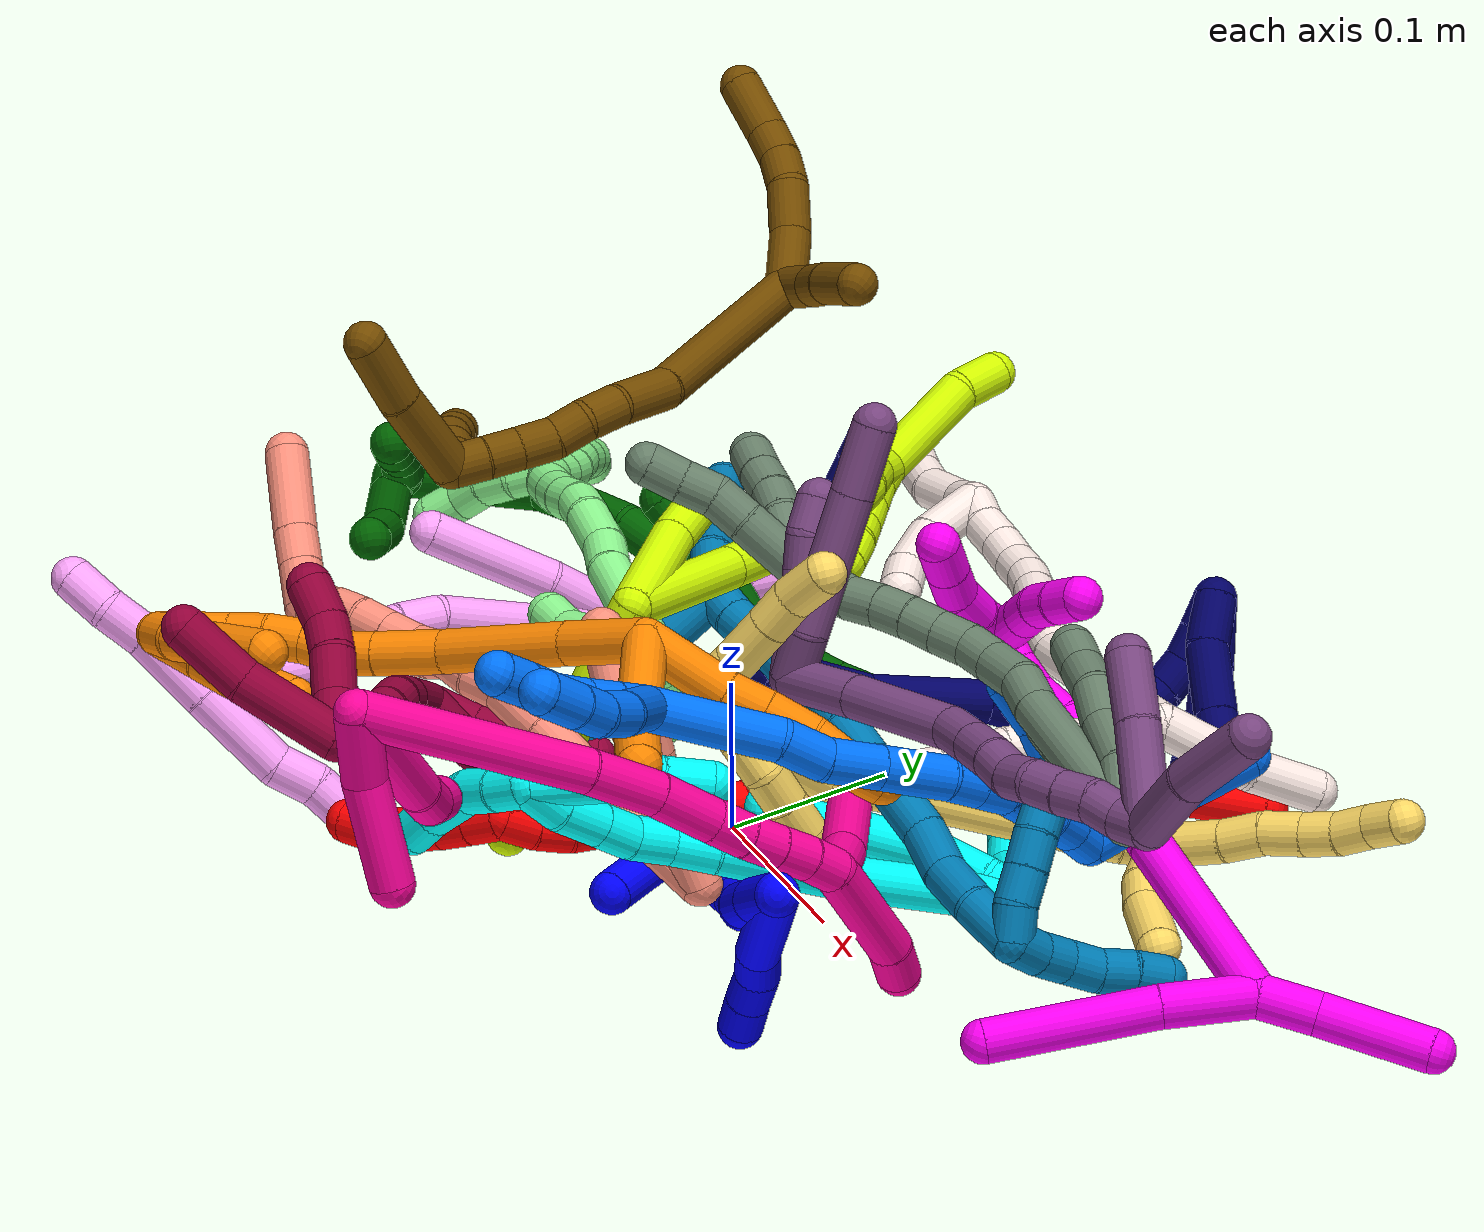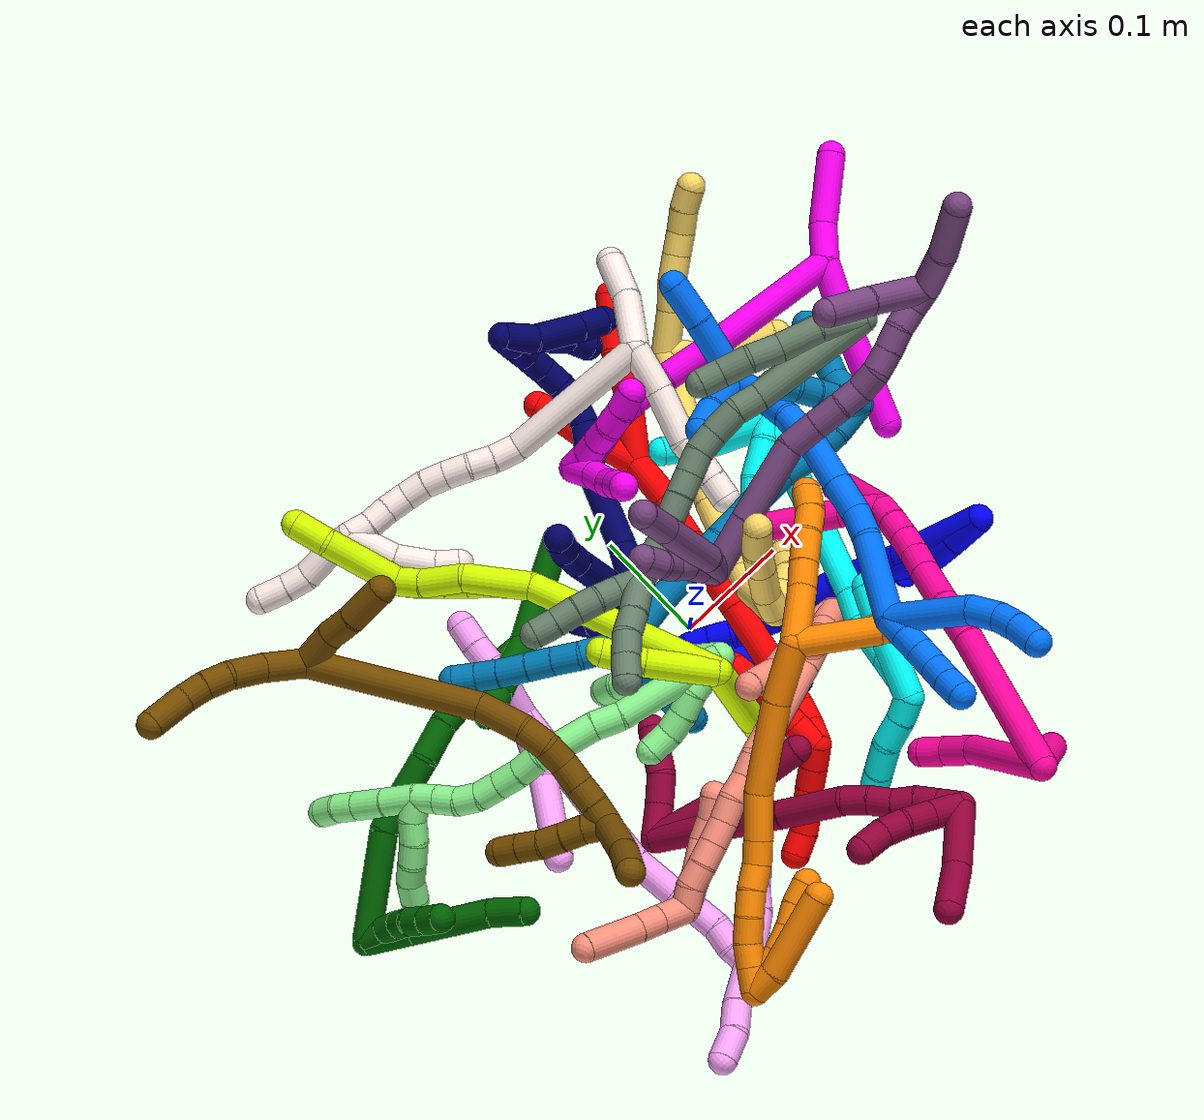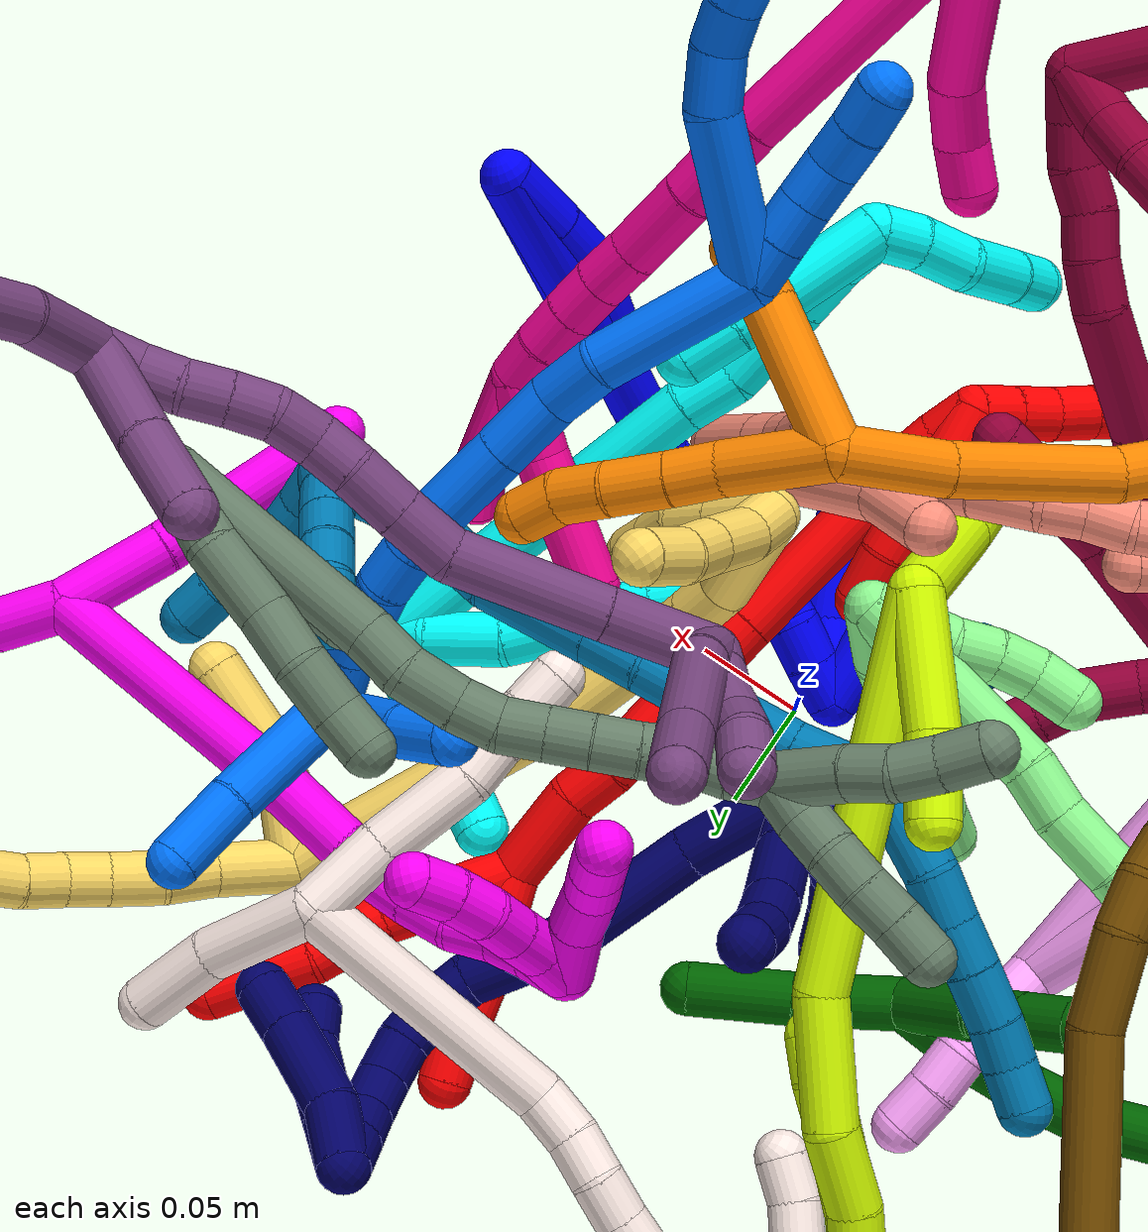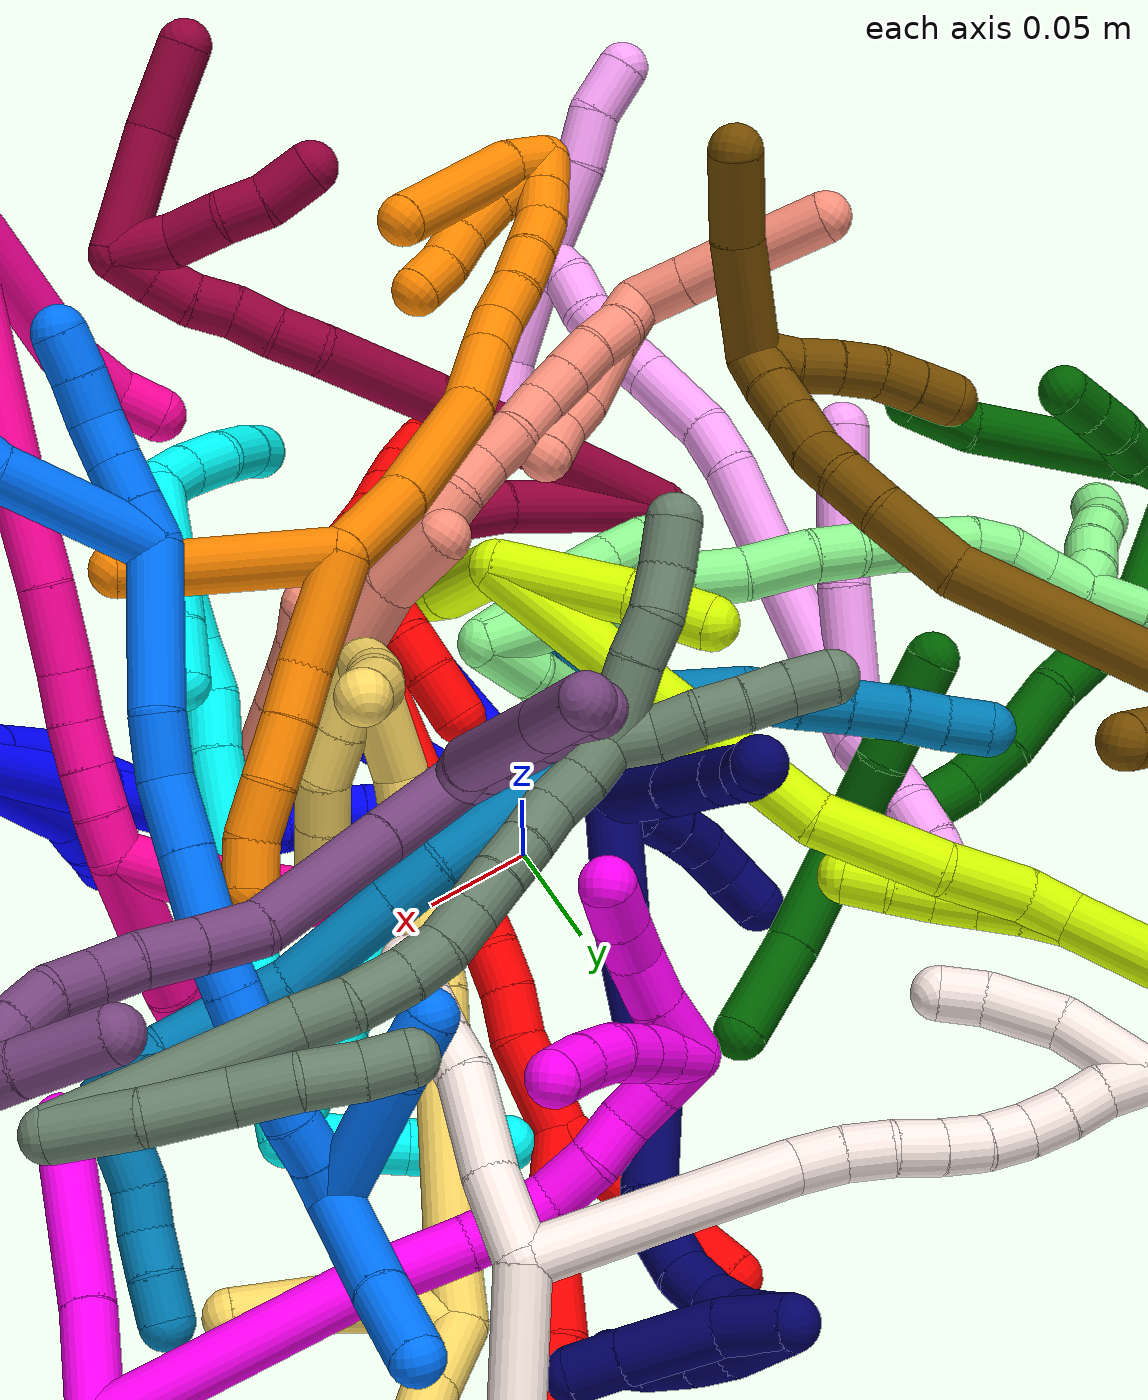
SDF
<sdf version="1.7">
 <world name="default">
  <plugin name="TubeGeneratorPlugin" filename="libtube_generator_plugin.so"/>
  <model name="photoneo_s_sensor">
   <static>1</static>
   <pose>0 0 2 1.57079 1.57079 3.14159</pose>
   <link name="link">
    <inertial><mass>0.1</mass></inertial>
    <sensor name="sensor" type="depth">
     <update_rate>30</update_rate>
     <camera>
      <horizontal_fov>1.22</horizontal_fov>
      <image><width>1920</width><height>1200</height><format>B8G8R8</format></image>
      <clip><near>0.1</near><far>4</far></clip>
      <depth_camera><output>points</output></depth_camera>
     </camera>
     <plugin name="camera_plugin" filename="libgazebo_ros_depth_camera.so">
      <baseline>0.2</baseline>
      <alwaysOn>1</alwaysOn>
      <updateRate>0.0</updateRate>
      <cameraName>camera_ir</cameraName>
      <imageTopicName>/camera/color/image_raw</imageTopicName>
      <cameraInfoTopicName>/camera/color/camera_info</cameraInfoTopicName>
      <depthImageTopicName>/camera/depth/image_raw</depthImageTopicName>
      <depthImageCameraInfoTopicName>/camera/depth/camera_info</depthImageCameraInfoTopicName>
      <pointCloudTopicName>/camera/depth/points</pointCloudTopicName>
      <frameName>fr_optical</frameName>
      <pointCloudCutoff>0.1</pointCloudCutoff>
      <pointCloudCutoffMax>2.0</pointCloudCutoffMax>
      <distortionK1>0</distortionK1>
      <distortionK2>0</distortionK2>
      <distortionK3>0</distortionK3>
      <distortionT1>0</distortionT1>
      <distortionT2>0</distortionT2>
      <CxPrime>0</CxPrime>
      <Cx>0</Cx>
      <Cy>0</Cy>
      <focalLength>0</focalLength>
      <hackBaseline>0</hackBaseline>
     </plugin>
    </sensor>
   </link>
  </model>
  <gravity>0 0 -9.8</gravity>
  <magnetic_field>6e-06 2.3e-05 -4.2e-05</magnetic_field>
  <atmosphere type="adiabatic"/>
  <physics name="default_physics" default="0" type="ode">
   <max_step_size>0.003</max_step_size>
   <real_time_factor>1</real_time_factor>
   <real_time_update_rate>1000</real_time_update_rate>
   <max_contacts>10000</max_contacts>
   <ode>
    <solver>
     <type>quick</type>
     <iters>100</iters>
     <sor>1.3</sor>
     <use_dynamic_moi_rescaling>0</use_dynamic_moi_rescaling>
    </solver>
    <constraints>
     <contact_max_correcting_vel>0</contact_max_correcting_vel>
     <contact_surface_layer>0.001</contact_surface_layer>
     <cfm>0</cfm>
     <erp>0.2</erp>
    </constraints>
   </ode>
  </physics>
  <scene><ambient>0.4 0.4 0.4 1</ambient><background>0.7 0.7 0.7 1</background><shadows>0</shadows></scene>
  <audio><device>default</device></audio>
  <spherical_coordinates>
   <surface_model>EARTH_WGS84</surface_model>
   <latitude_deg>0</latitude_deg>
   <longitude_deg>0</longitude_deg>
   <elevation>0</elevation>
   <heading_deg>0</heading_deg>
  </spherical_coordinates>
  <model name="bin">
   <static>1</static>
   <link name="bottom">
    <collision name="collision-bottom">
     <pose>0 0 -0.01 0 -0 0</pose>
     <geometry><box><size>0.8 0.6 0.02</size></box></geometry>
     <surface>
      <friction><ode><mu>100</mu><mu2>100</mu2></ode></friction>
      <contact><collide_bitmask>65535</collide_bitmask></contact>
     </surface>
    </collision>
   </link>
   <link name="west_wall">
    <collision name="collision-west_wall">
     <pose>-0.41 0 0.1 0 -0 0</pose>
     <geometry><box><size>0.02 0.6 0.2</size></box></geometry>
     <surface>
      <friction><ode><mu>100</mu><mu2>100</mu2></ode></friction>
      <contact><collide_bitmask>65535</collide_bitmask></contact>
     </surface>
    </collision>
   </link>
   <link name="east_wall">
    <collision name="collision-east_wall">
     <pose>0.41 0 0.1 0 -0 0</pose>
     <geometry><box><size>0.02 0.6 0.2</size></box></geometry>
     <surface>
      <friction><ode><mu>100</mu><mu2>100</mu2></ode></friction>
      <contact><collide_bitmask>65535</collide_bitmask></contact>
     </surface>
    </collision>
   </link>
   <link name="south_wall">
    <collision name="collision-south_wall">
     <pose>0 -0.31 0.1 0 -0 0</pose>
     <geometry><box><size>0.8 0.02 0.2</size></box></geometry>
     <surface>
      <friction><ode><mu>100</mu><mu2>100</mu2></ode></friction>
      <contact><collide_bitmask>65535</collide_bitmask></contact>
     </surface>
    </collision>
   </link>
   <link name="north_wall">
    <collision name="collision-north_wall">
     <pose>0 0.31 0.1 0 -0 0</pose>
     <geometry><box><size>0.8 0.02 0.2</size></box></geometry>
     <surface>
      <friction><ode><mu>100</mu><mu2>100</mu2></ode></friction>
      <contact><collide_bitmask>65535</collide_bitmask></contact>
     </surface>
    </collision>
   </link>
  </model>
  <model name="1">
   <static>0</static>
   <link name="1">
    <collision name="collision-cylinder-e_1_2_8">
     <pose>0.006822 -0.01149 -0.04221 2.87583 0.154698 1.0509</pose>
     <geometry><cylinder><radius>0.0125</radius><length>0.08855</length></cylinder></geometry>
     <surface>
      <friction><ode><mu>1.16</mu><mu2>1.16</mu2><slip1>0</slip1><slip2>0</slip2></ode></friction>
      <contact><ode><kp>1e+06</kp><kd>1</kd><max_vel>0</max_vel><min_depth>0.001</min_depth></ode></contact>
     </surface>
    </collision>
    <visual name="visual-cylinder-e_1_2_8">
     <pose>0.006822 -0.01149 -0.04221 2.87583 0.154698 1.0509</pose>
     <geometry><cylinder><radius>0.0125</radius><length>0.08855</length></cylinder></geometry>
     <material><ambient>0 0 1 1</ambient></material>
    </visual>
    <collision name="collision-cylinder-e_2_8_9">
     <pose>0.017901 -0.027295 -0.093028 2.67685 0.416255 1.45721</pose>
     <geometry><cylinder><radius>0.0125</radius><length>0.021056</length></cylinder></geometry>
     <surface>
      <friction><ode><mu>1.16</mu><mu2>1.16</mu2><slip1>0</slip1><slip2>0</slip2></ode></friction>
      <contact><ode><kp>1e+06</kp><kd>1</kd><max_vel>0</max_vel><min_depth>0.001</min_depth></ode></contact>
     </surface>
    </collision>
    <visual name="visual-cylinder-e_2_8_9">
     <pose>0.017901 -0.027295 -0.093028 2.67685 0.416255 1.45721</pose>
     <geometry><cylinder><radius>0.0125</radius><length>0.021056</length></cylinder></geometry>
     <material><ambient>0 0 1 1</ambient></material>
    </visual>
    <collision name="collision-cylinder-e_3_9_10">
     <pose>0.025056 -0.038016 -0.108989 2.42498 0.288922 0.741077</pose>
     <geometry><cylinder><radius>0.0125</radius><length>0.020348</length></cylinder></geometry>
     <surface>
      <friction><ode><mu>1.16</mu><mu2>1.16</mu2><slip1>0</slip1><slip2>0</slip2></ode></friction>
      <contact><ode><kp>1e+06</kp><kd>1</kd><max_vel>0</max_vel><min_depth>0.001</min_depth></ode></contact>
     </surface>
    </collision>
    <visual name="visual-cylinder-e_3_9_10">
     <pose>0.025056 -0.038016 -0.108989 2.42498 0.288922 0.741077</pose>
     <geometry><cylinder><radius>0.0125</radius><length>0.020348</length></cylinder></geometry>
     <material><ambient>0 0 1 1</ambient></material>
    </visual>
    <collision name="collision-cylinder-e_4_10_6">
     <pose>0.03132 -0.050587 -0.123494 2.43011 0.342374 0.870992</pose>
     <geometry><cylinder><radius>0.0125</radius><length>0.020047</length></cylinder></geometry>
     <surface>
      <friction><ode><mu>1.16</mu><mu2>1.16</mu2><slip1>0</slip1><slip2>0</slip2></ode></friction>
      <contact><ode><kp>1e+06</kp><kd>1</kd><max_vel>0</max_vel><min_depth>0.001</min_depth></ode></contact>
     </surface>
    </collision>
    <visual name="visual-cylinder-e_4_10_6">
     <pose>0.03132 -0.050587 -0.123494 2.43011 0.342374 0.870992</pose>
     <geometry><cylinder><radius>0.0125</radius><length>0.020047</length></cylinder></geometry>
     <material><ambient>0 0 1 1</ambient></material>
    </visual>
    <collision name="collision-cylinder-e_1_2_11">
     <pose>-0.003233 -0.003979 -0.016008 2.89794 -0.193524 -1.34068</pose>
     <geometry><cylinder><radius>0.0125</radius><length>0.033618</length></cylinder></geometry>
     <surface>
      <friction><ode><mu>1.16</mu><mu2>1.16</mu2><slip1>0</slip1><slip2>0</slip2></ode></friction>
      <contact><ode><kp>1e+06</kp><kd>1</kd><max_vel>0</max_vel><min_depth>0.001</min_depth></ode></contact>
     </surface>
    </collision>
    <visual name="visual-cylinder-e_1_2_11">
     <pose>-0.003233 -0.003979 -0.016008 2.89794 -0.193524 -1.34068</pose>
     <geometry><cylinder><radius>0.0125</radius><length>0.033618</length></cylinder></geometry>
     <material><ambient>0 0 1 1</ambient></material>
    </visual>
    <collision name="collision-cylinder-e_2_11_12">
     <pose>-0.008162 -0.01063 -0.043153 2.90622 -0.147044 -1.11426</pose>
     <geometry><cylinder><radius>0.0125</radius><length>0.023157</length></cylinder></geometry>
     <surface>
      <friction><ode><mu>1.16</mu><mu2>1.16</mu2><slip1>0</slip1><slip2>0</slip2></ode></friction>
      <contact><ode><kp>1e+06</kp><kd>1</kd><max_vel>0</max_vel><min_depth>0.001</min_depth></ode></contact>
     </surface>
    </collision>
    <visual name="visual-cylinder-e_2_11_12">
     <pose>-0.008162 -0.01063 -0.043153 2.90622 -0.147044 -1.11426</pose>
     <geometry><cylinder><radius>0.0125</radius><length>0.023157</length></cylinder></geometry>
     <material><ambient>0 0 1 1</ambient></material>
    </visual>
    <collision name="collision-cylinder-e_3_12_5">
     <pose>-0.008778 -0.012282 -0.075853 -3.09439 0.049981 -1.6279</pose>
     <geometry><cylinder><radius>0.0125</radius><length>0.043226</length></cylinder></geometry>
     <surface>
      <friction><ode><mu>1.16</mu><mu2>1.16</mu2><slip1>0</slip1><slip2>0</slip2></ode></friction>
      <contact><ode><kp>1e+06</kp><kd>1</kd><max_vel>0</max_vel><min_depth>0.001</min_depth></ode></contact>
     </surface>
    </collision>
    <visual name="visual-cylinder-e_3_12_5">
     <pose>-0.008778 -0.012282 -0.075853 -3.09439 0.049981 -1.6279</pose>
     <geometry><cylinder><radius>0.0125</radius><length>0.043226</length></cylinder></geometry>
     <material><ambient>0 0 1 1</ambient></material>
    </visual>
    <collision name="collision-cylinder-e_1_2_13">
     <pose>-0.002452 -0.003049 -0.044321 3.0729 -0.055143 -1.35265</pose>
     <geometry><cylinder><radius>0.0125</radius><length>0.088987</length></cylinder></geometry>
     <surface>
      <friction><ode><mu>1.16</mu><mu2>1.16</mu2><slip1>0</slip1><slip2>0</slip2></ode></friction>
      <contact><ode><kp>1e+06</kp><kd>1</kd><max_vel>0</max_vel><min_depth>0.001</min_depth></ode></contact>
     </surface>
    </collision>
    <visual name="visual-cylinder-e_1_2_13">
     <pose>-0.002452 -0.003049 -0.044321 3.0729 -0.055143 -1.35265</pose>
     <geometry><cylinder><radius>0.0125</radius><length>0.088987</length></cylinder></geometry>
     <material><ambient>0 0 1 1</ambient></material>
    </visual>
    <collision name="collision-cylinder-e_2_13_14">
     <pose>-0.006207 -0.005754 -0.109925 -3.12541 -0.061134 2.62403</pose>
     <geometry><cylinder><radius>0.0125</radius><length>0.042651</length></cylinder></geometry>
     <surface>
      <friction><ode><mu>1.16</mu><mu2>1.16</mu2><slip1>0</slip1><slip2>0</slip2></ode></friction>
      <contact><ode><kp>1e+06</kp><kd>1</kd><max_vel>0</max_vel><min_depth>0.001</min_depth></ode></contact>
     </surface>
    </collision>
    <visual name="visual-cylinder-e_2_13_14">
     <pose>-0.006207 -0.005754 -0.109925 -3.12541 -0.061134 2.62403</pose>
     <geometry><cylinder><radius>0.0125</radius><length>0.042651</length></cylinder></geometry>
     <material><ambient>0 0 1 1</ambient></material>
    </visual>
    <collision name="collision-cylinder-e_3_14_15">
     <pose>-0.007853 -0.005604 -0.14532 3.12783 -0.02427 -2.11007</pose>
     <geometry><cylinder><radius>0.0125</radius><length>0.028234</length></cylinder></geometry>
     <surface>
      <friction><ode><mu>1.16</mu><mu2>1.16</mu2><slip1>0</slip1><slip2>0</slip2></ode></friction>
      <contact><ode><kp>1e+06</kp><kd>1</kd><max_vel>0</max_vel><min_depth>0.001</min_depth></ode></contact>
     </surface>
    </collision>
    <visual name="visual-cylinder-e_3_14_15">
     <pose>-0.007853 -0.005604 -0.14532 3.12783 -0.02427 -2.11007</pose>
     <geometry><cylinder><radius>0.0125</radius><length>0.028234</length></cylinder></geometry>
     <material><ambient>0 0 1 1</ambient></material>
    </visual>
    <collision name="collision-cylinder-e_4_15_16">
     <pose>-0.011595 -0.005449 -0.168864 -3.10458 -0.345663 2.93034</pose>
     <geometry><cylinder><radius>0.0125</radius><length>0.020065</length></cylinder></geometry>
     <surface>
      <friction><ode><mu>1.16</mu><mu2>1.16</mu2><slip1>0</slip1><slip2>0</slip2></ode></friction>
      <contact><ode><kp>1e+06</kp><kd>1</kd><max_vel>0</max_vel><min_depth>0.001</min_depth></ode></contact>
     </surface>
    </collision>
    <visual name="visual-cylinder-e_4_15_16">
     <pose>-0.011595 -0.005449 -0.168864 -3.10458 -0.345663 2.93034</pose>
     <geometry><cylinder><radius>0.0125</radius><length>0.020065</length></cylinder></geometry>
     <material><ambient>0 0 1 1</ambient></material>
    </visual>
    <collision name="collision-cylinder-e_5_16_17">
     <pose>-0.020452 -0.004817 -0.186705 -3.10799 -0.575501 3.02816</pose>
     <geometry><cylinder><radius>0.0125</radius><length>0.020059</length></cylinder></geometry>
     <surface>
      <friction><ode><mu>1.16</mu><mu2>1.16</mu2><slip1>0</slip1><slip2>0</slip2></ode></friction>
      <contact><ode><kp>1e+06</kp><kd>1</kd><max_vel>0</max_vel><min_depth>0.001</min_depth></ode></contact>
     </surface>
    </collision>
    <visual name="visual-cylinder-e_5_16_17">
     <pose>-0.020452 -0.004817 -0.186705 -3.10799 -0.575501 3.02816</pose>
     <geometry><cylinder><radius>0.0125</radius><length>0.020059</length></cylinder></geometry>
     <material><ambient>0 0 1 1</ambient></material>
    </visual>
    <collision name="collision-cylinder-e_6_17_18">
     <pose>-0.030076 -0.001883 -0.203812 -2.84572 -0.429543 1.9429</pose>
     <geometry><cylinder><radius>0.0125</radius><length>0.020002</length></cylinder></geometry>
     <surface>
      <friction><ode><mu>1.16</mu><mu2>1.16</mu2><slip1>0</slip1><slip2>0</slip2></ode></friction>
      <contact><ode><kp>1e+06</kp><kd>1</kd><max_vel>0</max_vel><min_depth>0.001</min_depth></ode></contact>
     </surface>
    </collision>
    <visual name="visual-cylinder-e_6_17_18">
     <pose>-0.030076 -0.001883 -0.203812 -2.84572 -0.429543 1.9429</pose>
     <geometry><cylinder><radius>0.0125</radius><length>0.020002</length></cylinder></geometry>
     <material><ambient>0 0 1 1</ambient></material>
    </visual>
    <collision name="collision-cylinder-e_7_18_19">
     <pose>-0.038182 0.003543 -0.221272 -2.83489 -0.405113 1.85126</pose>
     <geometry><cylinder><radius>0.0125</radius><length>0.020001</length></cylinder></geometry>
     <surface>
      <friction><ode><mu>1.16</mu><mu2>1.16</mu2><slip1>0</slip1><slip2>0</slip2></ode></friction>
      <contact><ode><kp>1e+06</kp><kd>1</kd><max_vel>0</max_vel><min_depth>0.001</min_depth></ode></contact>
     </surface>
    </collision>
    <visual name="visual-cylinder-e_7_18_19">
     <pose>-0.038182 0.003543 -0.221272 -2.83489 -0.405113 1.85126</pose>
     <geometry><cylinder><radius>0.0125</radius><length>0.020001</length></cylinder></geometry>
     <material><ambient>0 0 1 1</ambient></material>
    </visual>
    <collision name="collision-cylinder-e_8_19_20">
     <pose>-0.04726 0.011035 -0.237201 -2.55952 -0.539426 1.49066</pose>
     <geometry><cylinder><radius>0.0125</radius><length>0.02</length></cylinder></geometry>
     <surface>
      <friction><ode><mu>1.16</mu><mu2>1.16</mu2><slip1>0</slip1><slip2>0</slip2></ode></friction>
      <contact><ode><kp>1e+06</kp><kd>1</kd><max_vel>0</max_vel><min_depth>0.001</min_depth></ode></contact>
     </surface>
    </collision>
    <visual name="visual-cylinder-e_8_19_20">
     <pose>-0.04726 0.011035 -0.237201 -2.55952 -0.539426 1.49066</pose>
     <geometry><cylinder><radius>0.0125</radius><length>0.02</length></cylinder></geometry>
     <material><ambient>0 0 1 1</ambient></material>
    </visual>
    <collision name="collision-cylinder-e_9_20_21">
     <pose>-0.055245 0.019059 -0.253365 -2.78933 -0.288781 1.37002</pose>
     <geometry><cylinder><radius>0.0125</radius><length>0.02</length></cylinder></geometry>
     <surface>
      <friction><ode><mu>1.16</mu><mu2>1.16</mu2><slip1>0</slip1><slip2>0</slip2></ode></friction>
      <contact><ode><kp>1e+06</kp><kd>1</kd><max_vel>0</max_vel><min_depth>0.001</min_depth></ode></contact>
     </surface>
    </collision>
    <visual name="visual-cylinder-e_9_20_21">
     <pose>-0.055245 0.019059 -0.253365 -2.78933 -0.288781 1.37002</pose>
     <geometry><cylinder><radius>0.0125</radius><length>0.02</length></cylinder></geometry>
     <material><ambient>0 0 1 1</ambient></material>
    </visual>
    <collision name="collision-cylinder-e_10_21_1">
     <pose>-0.061211 0.025095 -0.271465 -2.8504 -0.317074 1.65716</pose>
     <geometry><cylinder><radius>0.0125</radius><length>0.020001</length></cylinder></geometry>
     <surface>
      <friction><ode><mu>1.16</mu><mu2>1.16</mu2><slip1>0</slip1><slip2>0</slip2></ode></friction>
      <contact><ode><kp>1e+06</kp><kd>1</kd><max_vel>0</max_vel><min_depth>0.001</min_depth></ode></contact>
     </surface>
    </collision>
    <visual name="visual-cylinder-e_10_21_1">
     <pose>-0.061211 0.025095 -0.271465 -2.8504 -0.317074 1.65716</pose>
     <geometry><cylinder><radius>0.0125</radius><length>0.020001</length></cylinder></geometry>
     <material><ambient>0 0 1 1</ambient></material>
    </visual>
    <collision name="collision-cylinder-e_1_1_22">
     <pose>-0.061465 0.013513 -0.268964 0.889488 0.15423 0.073617</pose>
     <geometry><cylinder><radius>0.0125</radius><length>0.037286</length></cylinder></geometry>
     <surface>
      <friction><ode><mu>1.16</mu><mu2>1.16</mu2><slip1>0</slip1><slip2>0</slip2></ode></friction>
      <contact><ode><kp>1e+06</kp><kd>1</kd><max_vel>0</max_vel><min_depth>0.001</min_depth></ode></contact>
     </surface>
    </collision>
    <visual name="visual-cylinder-e_1_1_22">
     <pose>-0.061465 0.013513 -0.268964 0.889488 0.15423 0.073617</pose>
     <geometry><cylinder><radius>0.0125</radius><length>0.037286</length></cylinder></geometry>
     <material><ambient>0 0 1 1</ambient></material>
    </visual>
    <collision name="collision-cylinder-e_2_22_4">
     <pose>-0.062356 -0.024084 -0.236702 0.845137 -0.120034 -0.054026</pose>
     <geometry><cylinder><radius>0.0125</radius><length>0.062714</length></cylinder></geometry>
     <surface>
      <friction><ode><mu>1.16</mu><mu2>1.16</mu2><slip1>0</slip1><slip2>0</slip2></ode></friction>
      <contact><ode><kp>1e+06</kp><kd>1</kd><max_vel>0</max_vel><min_depth>0.001</min_depth></ode></contact>
     </surface>
    </collision>
    <visual name="visual-cylinder-e_2_22_4">
     <pose>-0.062356 -0.024084 -0.236702 0.845137 -0.120034 -0.054026</pose>
     <geometry><cylinder><radius>0.0125</radius><length>0.062714</length></cylinder></geometry>
     <material><ambient>0 0 1 1</ambient></material>
    </visual>
    <collision name="collision-cylinder-e_1_1_23">
     <pose>-0.074325 0.01459 -0.271431 0.966543 -0.556202 -0.297434</pose>
     <geometry><cylinder><radius>0.0125</radius><length>0.037868</length></cylinder></geometry>
     <surface>
      <friction><ode><mu>1.16</mu><mu2>1.16</mu2><slip1>0</slip1><slip2>0</slip2></ode></friction>
      <contact><ode><kp>1e+06</kp><kd>1</kd><max_vel>0</max_vel><min_depth>0.001</min_depth></ode></contact>
     </surface>
    </collision>
    <visual name="visual-cylinder-e_1_1_23">
     <pose>-0.074325 0.01459 -0.271431 0.966543 -0.556202 -0.297434</pose>
     <geometry><cylinder><radius>0.0125</radius><length>0.037868</length></cylinder></geometry>
     <material><ambient>0 0 1 1</ambient></material>
    </visual>
    <collision name="collision-cylinder-e_2_23_3">
     <pose>-0.097784 -0.01798 -0.242048 0.762435 -0.448224 -0.182223</pose>
     <geometry><cylinder><radius>0.0125</radius><length>0.062132</length></cylinder></geometry>
     <surface>
      <friction><ode><mu>1.16</mu><mu2>1.16</mu2><slip1>0</slip1><slip2>0</slip2></ode></friction>
      <contact><ode><kp>1e+06</kp><kd>1</kd><max_vel>0</max_vel><min_depth>0.001</min_depth></ode></contact>
     </surface>
    </collision>
    <visual name="visual-cylinder-e_2_23_3">
     <pose>-0.097784 -0.01798 -0.242048 0.762435 -0.448224 -0.182223</pose>
     <geometry><cylinder><radius>0.0125</radius><length>0.062132</length></cylinder></geometry>
     <material><ambient>0 0 1 1</ambient></material>
    </visual>
    <collision name="collision-sphere-3">
     <pose>-0.111247 -0.037317 -0.221802 0 -0 0</pose>
     <geometry><sphere><radius>0.0125</radius></sphere></geometry>
     <surface>
      <friction><ode><mu>1.16</mu><mu2>1.16</mu2><slip1>0</slip1><slip2>0</slip2></ode></friction>
      <contact><ode><kp>1e+06</kp><kd>1</kd><max_vel>0</max_vel><min_depth>0.001</min_depth></ode></contact>
     </surface>
    </collision>
    <visual name="visual-sphere-3">
     <pose>-0.111247 -0.037317 -0.221802 0 -0 0</pose>
     <geometry><sphere><radius>0.0125</radius></sphere></geometry>
     <material><ambient>0 0 1 1</ambient></material>
    </visual>
    <collision name="collision-sphere-23">
     <pose>-0.084321 0.001357 -0.262295 0 -0 0</pose>
     <geometry><sphere><radius>0.0125</radius></sphere></geometry>
     <surface>
      <friction><ode><mu>1.16</mu><mu2>1.16</mu2><slip1>0</slip1><slip2>0</slip2></ode></friction>
      <contact><ode><kp>1e+06</kp><kd>1</kd><max_vel>0</max_vel><min_depth>0.001</min_depth></ode></contact>
     </surface>
    </collision>
    <visual name="visual-sphere-23">
     <pose>-0.084321 0.001357 -0.262295 0 -0 0</pose>
     <geometry><sphere><radius>0.0125</radius></sphere></geometry>
     <material><ambient>0 0 1 1</ambient></material>
    </visual>
    <collision name="collision-sphere-4">
     <pose>-0.06611 -0.047372 -0.216043 0 -0 0</pose>
     <geometry><sphere><radius>0.0125</radius></sphere></geometry>
     <surface>
      <friction><ode><mu>1.16</mu><mu2>1.16</mu2><slip1>0</slip1><slip2>0</slip2></ode></friction>
      <contact><ode><kp>1e+06</kp><kd>1</kd><max_vel>0</max_vel><min_depth>0.001</min_depth></ode></contact>
     </surface>
    </collision>
    <visual name="visual-sphere-4">
     <pose>-0.06611 -0.047372 -0.216043 0 -0 0</pose>
     <geometry><sphere><radius>0.0125</radius></sphere></geometry>
     <material><ambient>0 0 1 1</ambient></material>
    </visual>
    <collision name="collision-sphere-22">
     <pose>-0.058601 -0.000796 -0.257362 0 -0 0</pose>
     <geometry><sphere><radius>0.0125</radius></sphere></geometry>
     <surface>
      <friction><ode><mu>1.16</mu><mu2>1.16</mu2><slip1>0</slip1><slip2>0</slip2></ode></friction>
      <contact><ode><kp>1e+06</kp><kd>1</kd><max_vel>0</max_vel><min_depth>0.001</min_depth></ode></contact>
     </surface>
    </collision>
    <visual name="visual-sphere-22">
     <pose>-0.058601 -0.000796 -0.257362 0 -0 0</pose>
     <geometry><sphere><radius>0.0125</radius></sphere></geometry>
     <material><ambient>0 0 1 1</ambient></material>
    </visual>
    <collision name="collision-sphere-1">
     <pose>-0.064329 0.027822 -0.280566 0 -0 0</pose>
     <geometry><sphere><radius>0.0125</radius></sphere></geometry>
     <surface>
      <friction><ode><mu>1.16</mu><mu2>1.16</mu2><slip1>0</slip1><slip2>0</slip2></ode></friction>
      <contact><ode><kp>1e+06</kp><kd>1</kd><max_vel>0</max_vel><min_depth>0.001</min_depth></ode></contact>
     </surface>
    </collision>
    <visual name="visual-sphere-1">
     <pose>-0.064329 0.027822 -0.280566 0 -0 0</pose>
     <geometry><sphere><radius>0.0125</radius></sphere></geometry>
     <material><ambient>0 0 1 1</ambient></material>
    </visual>
    <collision name="collision-sphere-21">
     <pose>-0.058093 0.022367 -0.262363 0 -0 0</pose>
     <geometry><sphere><radius>0.0125</radius></sphere></geometry>
     <surface>
      <friction><ode><mu>1.16</mu><mu2>1.16</mu2><slip1>0</slip1><slip2>0</slip2></ode></friction>
      <contact><ode><kp>1e+06</kp><kd>1</kd><max_vel>0</max_vel><min_depth>0.001</min_depth></ode></contact>
     </surface>
    </collision>
    <visual name="visual-sphere-21">
     <pose>-0.058093 0.022367 -0.262363 0 -0 0</pose>
     <geometry><sphere><radius>0.0125</radius></sphere></geometry>
     <material><ambient>0 0 1 1</ambient></material>
    </visual>
    <collision name="collision-sphere-11">
     <pose>-0.006465 -0.007959 -0.032016 0 -0 0</pose>
     <geometry><sphere><radius>0.0125</radius></sphere></geometry>
     <surface>
      <friction><ode><mu>1.16</mu><mu2>1.16</mu2><slip1>0</slip1><slip2>0</slip2></ode></friction>
      <contact><ode><kp>1e+06</kp><kd>1</kd><max_vel>0</max_vel><min_depth>0.001</min_depth></ode></contact>
     </surface>
    </collision>
    <visual name="visual-sphere-11">
     <pose>-0.006465 -0.007959 -0.032016 0 -0 0</pose>
     <geometry><sphere><radius>0.0125</radius></sphere></geometry>
     <material><ambient>0 0 1 1</ambient></material>
    </visual>
    <collision name="collision-sphere-6">
     <pose>0.034685 -0.056752 -0.130645 0 -0 0</pose>
     <geometry><sphere><radius>0.0125</radius></sphere></geometry>
     <surface>
      <friction><ode><mu>1.16</mu><mu2>1.16</mu2><slip1>0</slip1><slip2>0</slip2></ode></friction>
      <contact><ode><kp>1e+06</kp><kd>1</kd><max_vel>0</max_vel><min_depth>0.001</min_depth></ode></contact>
     </surface>
    </collision>
    <visual name="visual-sphere-6">
     <pose>0.034685 -0.056752 -0.130645 0 -0 0</pose>
     <geometry><sphere><radius>0.0125</radius></sphere></geometry>
     <material><ambient>0 0 1 1</ambient></material>
    </visual>
    <collision name="collision-sphere-10">
     <pose>0.027955 -0.044422 -0.116343 0 -0 0</pose>
     <geometry><sphere><radius>0.0125</radius></sphere></geometry>
     <surface>
      <friction><ode><mu>1.16</mu><mu2>1.16</mu2><slip1>0</slip1><slip2>0</slip2></ode></friction>
      <contact><ode><kp>1e+06</kp><kd>1</kd><max_vel>0</max_vel><min_depth>0.001</min_depth></ode></contact>
     </surface>
    </collision>
    <visual name="visual-sphere-10">
     <pose>0.027955 -0.044422 -0.116343 0 -0 0</pose>
     <geometry><sphere><radius>0.0125</radius></sphere></geometry>
     <material><ambient>0 0 1 1</ambient></material>
    </visual>
    <collision name="collision-sphere-9">
     <pose>0.022158 -0.031611 -0.101636 0 -0 0</pose>
     <geometry><sphere><radius>0.0125</radius></sphere></geometry>
     <surface>
      <friction><ode><mu>1.16</mu><mu2>1.16</mu2><slip1>0</slip1><slip2>0</slip2></ode></friction>
      <contact><ode><kp>1e+06</kp><kd>1</kd><max_vel>0</max_vel><min_depth>0.001</min_depth></ode></contact>
     </surface>
    </collision>
    <visual name="visual-sphere-9">
     <pose>0.022158 -0.031611 -0.101636 0 -0 0</pose>
     <geometry><sphere><radius>0.0125</radius></sphere></geometry>
     <material><ambient>0 0 1 1</ambient></material>
    </visual>
    <collision name="collision-sphere-2">
     <geometry><sphere><radius>0.0125</radius></sphere></geometry>
     <surface>
      <friction><ode><mu>1.16</mu><mu2>1.16</mu2><slip1>0</slip1><slip2>0</slip2></ode></friction>
      <contact><ode><kp>1e+06</kp><kd>1</kd><max_vel>0</max_vel><min_depth>0.001</min_depth></ode></contact>
     </surface>
    </collision>
    <visual name="visual-sphere-2">
     <geometry><sphere><radius>0.0125</radius></sphere></geometry>
     <material><ambient>0 0 1 1</ambient></material>
    </visual>
    <collision name="collision-sphere-19">
     <pose>-0.042124 0.006318 -0.230034 0 -0 0</pose>
     <geometry><sphere><radius>0.0125</radius></sphere></geometry>
     <surface>
      <friction><ode><mu>1.16</mu><mu2>1.16</mu2><slip1>0</slip1><slip2>0</slip2></ode></friction>
      <contact><ode><kp>1e+06</kp><kd>1</kd><max_vel>0</max_vel><min_depth>0.001</min_depth></ode></contact>
     </surface>
    </collision>
    <visual name="visual-sphere-19">
     <pose>-0.042124 0.006318 -0.230034 0 -0 0</pose>
     <geometry><sphere><radius>0.0125</radius></sphere></geometry>
     <material><ambient>0 0 1 1</ambient></material>
    </visual>
    <collision name="collision-sphere-8">
     <pose>0.013644 -0.022979 -0.084421 0 -0 0</pose>
     <geometry><sphere><radius>0.0125</radius></sphere></geometry>
     <surface>
      <friction><ode><mu>1.16</mu><mu2>1.16</mu2><slip1>0</slip1><slip2>0</slip2></ode></friction>
      <contact><ode><kp>1e+06</kp><kd>1</kd><max_vel>0</max_vel><min_depth>0.001</min_depth></ode></contact>
     </surface>
    </collision>
    <visual name="visual-sphere-8">
     <pose>0.013644 -0.022979 -0.084421 0 -0 0</pose>
     <geometry><sphere><radius>0.0125</radius></sphere></geometry>
     <material><ambient>0 0 1 1</ambient></material>
    </visual>
    <collision name="collision-sphere-12">
     <pose>-0.009858 -0.013301 -0.054291 0 -0 0</pose>
     <geometry><sphere><radius>0.0125</radius></sphere></geometry>
     <surface>
      <friction><ode><mu>1.16</mu><mu2>1.16</mu2><slip1>0</slip1><slip2>0</slip2></ode></friction>
      <contact><ode><kp>1e+06</kp><kd>1</kd><max_vel>0</max_vel><min_depth>0.001</min_depth></ode></contact>
     </surface>
    </collision>
    <visual name="visual-sphere-12">
     <pose>-0.009858 -0.013301 -0.054291 0 -0 0</pose>
     <geometry><sphere><radius>0.0125</radius></sphere></geometry>
     <material><ambient>0 0 1 1</ambient></material>
    </visual>
    <collision name="collision-sphere-5">
     <pose>-0.007699 -0.011264 -0.097414 0 -0 0</pose>
     <geometry><sphere><radius>0.0125</radius></sphere></geometry>
     <surface>
      <friction><ode><mu>1.16</mu><mu2>1.16</mu2><slip1>0</slip1><slip2>0</slip2></ode></friction>
      <contact><ode><kp>1e+06</kp><kd>1</kd><max_vel>0</max_vel><min_depth>0.001</min_depth></ode></contact>
     </surface>
    </collision>
    <visual name="visual-sphere-5">
     <pose>-0.007699 -0.011264 -0.097414 0 -0 0</pose>
     <geometry><sphere><radius>0.0125</radius></sphere></geometry>
     <material><ambient>0 0 1 1</ambient></material>
    </visual>
    <collision name="collision-sphere-13">
     <pose>-0.004905 -0.006099 -0.088642 0 -0 0</pose>
     <geometry><sphere><radius>0.0125</radius></sphere></geometry>
     <surface>
      <friction><ode><mu>1.16</mu><mu2>1.16</mu2><slip1>0</slip1><slip2>0</slip2></ode></friction>
      <contact><ode><kp>1e+06</kp><kd>1</kd><max_vel>0</max_vel><min_depth>0.001</min_depth></ode></contact>
     </surface>
    </collision>
    <visual name="visual-sphere-13">
     <pose>-0.004905 -0.006099 -0.088642 0 -0 0</pose>
     <geometry><sphere><radius>0.0125</radius></sphere></geometry>
     <material><ambient>0 0 1 1</ambient></material>
    </visual>
    <collision name="collision-sphere-14">
     <pose>-0.00751 -0.00541 -0.131208 0 -0 0</pose>
     <geometry><sphere><radius>0.0125</radius></sphere></geometry>
     <surface>
      <friction><ode><mu>1.16</mu><mu2>1.16</mu2><slip1>0</slip1><slip2>0</slip2></ode></friction>
      <contact><ode><kp>1e+06</kp><kd>1</kd><max_vel>0</max_vel><min_depth>0.001</min_depth></ode></contact>
     </surface>
    </collision>
    <visual name="visual-sphere-14">
     <pose>-0.00751 -0.00541 -0.131208 0 -0 0</pose>
     <geometry><sphere><radius>0.0125</radius></sphere></geometry>
     <material><ambient>0 0 1 1</ambient></material>
    </visual>
    <collision name="collision-sphere-15">
     <pose>-0.008196 -0.005798 -0.159431 0 -0 0</pose>
     <geometry><sphere><radius>0.0125</radius></sphere></geometry>
     <surface>
      <friction><ode><mu>1.16</mu><mu2>1.16</mu2><slip1>0</slip1><slip2>0</slip2></ode></friction>
      <contact><ode><kp>1e+06</kp><kd>1</kd><max_vel>0</max_vel><min_depth>0.001</min_depth></ode></contact>
     </surface>
    </collision>
    <visual name="visual-sphere-15">
     <pose>-0.008196 -0.005798 -0.159431 0 -0 0</pose>
     <geometry><sphere><radius>0.0125</radius></sphere></geometry>
     <material><ambient>0 0 1 1</ambient></material>
    </visual>
    <collision name="collision-sphere-16">
     <pose>-0.014994 -0.0051 -0.178296 0 -0 0</pose>
     <geometry><sphere><radius>0.0125</radius></sphere></geometry>
     <surface>
      <friction><ode><mu>1.16</mu><mu2>1.16</mu2><slip1>0</slip1><slip2>0</slip2></ode></friction>
      <contact><ode><kp>1e+06</kp><kd>1</kd><max_vel>0</max_vel><min_depth>0.001</min_depth></ode></contact>
     </surface>
    </collision>
    <visual name="visual-sphere-16">
     <pose>-0.014994 -0.0051 -0.178296 0 -0 0</pose>
     <geometry><sphere><radius>0.0125</radius></sphere></geometry>
     <material><ambient>0 0 1 1</ambient></material>
    </visual>
    <collision name="collision-sphere-17">
     <pose>-0.025911 -0.004534 -0.195114 0 -0 0</pose>
     <geometry><sphere><radius>0.0125</radius></sphere></geometry>
     <surface>
      <friction><ode><mu>1.16</mu><mu2>1.16</mu2><slip1>0</slip1><slip2>0</slip2></ode></friction>
      <contact><ode><kp>1e+06</kp><kd>1</kd><max_vel>0</max_vel><min_depth>0.001</min_depth></ode></contact>
     </surface>
    </collision>
    <visual name="visual-sphere-17">
     <pose>-0.025911 -0.004534 -0.195114 0 -0 0</pose>
     <geometry><sphere><radius>0.0125</radius></sphere></geometry>
     <material><ambient>0 0 1 1</ambient></material>
    </visual>
    <collision name="collision-sphere-18">
     <pose>-0.034241 0.000768 -0.212509 0 -0 0</pose>
     <geometry><sphere><radius>0.0125</radius></sphere></geometry>
     <surface>
      <friction><ode><mu>1.16</mu><mu2>1.16</mu2><slip1>0</slip1><slip2>0</slip2></ode></friction>
      <contact><ode><kp>1e+06</kp><kd>1</kd><max_vel>0</max_vel><min_depth>0.001</min_depth></ode></contact>
     </surface>
    </collision>
    <visual name="visual-sphere-18">
     <pose>-0.034241 0.000768 -0.212509 0 -0 0</pose>
     <geometry><sphere><radius>0.0125</radius></sphere></geometry>
     <material><ambient>0 0 1 1</ambient></material>
    </visual>
    <collision name="collision-sphere-20">
     <pose>-0.052397 0.015752 -0.244368 0 -0 0</pose>
     <geometry><sphere><radius>0.0125</radius></sphere></geometry>
     <surface>
      <friction><ode><mu>1.16</mu><mu2>1.16</mu2><slip1>0</slip1><slip2>0</slip2></ode></friction>
      <contact><ode><kp>1e+06</kp><kd>1</kd><max_vel>0</max_vel><min_depth>0.001</min_depth></ode></contact>
     </surface>
    </collision>
    <visual name="visual-sphere-20">
     <pose>-0.052397 0.015752 -0.244368 0 -0 0</pose>
     <geometry><sphere><radius>0.0125</radius></sphere></geometry>
     <material><ambient>0 0 1 1</ambient></material>
    </visual>
    <inertial>
     <pose>-0.026184 -0.007474 -0.145345 0 -0 0</pose>
     <mass>0.75</mass>
     <inertia><ixx>6.5e-05</ixx><ixy>0</ixy><ixz>0</ixz><iyy>-2e-05</iyy><iyz>0</iyz><izz>4.3e-05</izz></inertia>
    </inertial>
   </link>
   <pose>0.229037 -0.105976 0.144697 0.702274 0.576428 0.527384</pose>
  </model>
  <model name="2">
   <static>0</static>
   <link name="2">
    <collision name="collision-cylinder-e_1_2_8">
     <pose>-0.016816 0.020064 0.017414 -0.855982 -0.564312 0.262965</pose>
     <geometry><cylinder><radius>0.0125</radius><length>0.062883</length></cylinder></geometry>
     <surface>
      <friction><ode><mu>1.16</mu><mu2>1.16</mu2><slip1>0</slip1><slip2>0</slip2></ode></friction>
      <contact><ode><kp>1e+06</kp><kd>1</kd><max_vel>0</max_vel><min_depth>0.001</min_depth></ode></contact>
     </surface>
    </collision>
    <visual name="visual-cylinder-e_1_2_8">
     <pose>-0.016816 0.020064 0.017414 -0.855982 -0.564312 0.262965</pose>
     <geometry><cylinder><radius>0.0125</radius><length>0.062883</length></cylinder></geometry>
     <material><ambient>1 0 0 1</ambient></material>
    </visual>
    <collision name="collision-cylinder-e_2_8_9">
     <pose>-0.040872 0.051772 0.046967 -0.764639 -0.406439 0.165341</pose>
     <geometry><cylinder><radius>0.0125</radius><length>0.036626</length></cylinder></geometry>
     <surface>
      <friction><ode><mu>1.16</mu><mu2>1.16</mu2><slip1>0</slip1><slip2>0</slip2></ode></friction>
      <contact><ode><kp>1e+06</kp><kd>1</kd><max_vel>0</max_vel><min_depth>0.001</min_depth></ode></contact>
     </surface>
    </collision>
    <visual name="visual-cylinder-e_2_8_9">
     <pose>-0.040872 0.051772 0.046967 -0.764639 -0.406439 0.165341</pose>
     <geometry><cylinder><radius>0.0125</radius><length>0.036626</length></cylinder></geometry>
     <material><ambient>1 0 0 1</ambient></material>
    </visual>
    <collision name="collision-cylinder-e_3_9_6">
     <pose>-0.063004 0.076303 0.074901 -0.684283 -0.630941 0.231434</pose>
     <geometry><cylinder><radius>0.0125</radius><length>0.050491</length></cylinder></geometry>
     <surface>
      <friction><ode><mu>1.16</mu><mu2>1.16</mu2><slip1>0</slip1><slip2>0</slip2></ode></friction>
      <contact><ode><kp>1e+06</kp><kd>1</kd><max_vel>0</max_vel><min_depth>0.001</min_depth></ode></contact>
     </surface>
    </collision>
    <visual name="visual-cylinder-e_3_9_6">
     <pose>-0.063004 0.076303 0.074901 -0.684283 -0.630941 0.231434</pose>
     <geometry><cylinder><radius>0.0125</radius><length>0.050491</length></cylinder></geometry>
     <material><ambient>1 0 0 1</ambient></material>
    </visual>
    <collision name="collision-cylinder-e_1_2_10">
     <pose>0.008243 0.012177 0.021318 -0.518967 0.323939 -0.086701</pose>
     <geometry><cylinder><radius>0.0125</radius><length>0.051796</length></cylinder></geometry>
     <surface>
      <friction><ode><mu>1.16</mu><mu2>1.16</mu2><slip1>0</slip1><slip2>0</slip2></ode></friction>
      <contact><ode><kp>1e+06</kp><kd>1</kd><max_vel>0</max_vel><min_depth>0.001</min_depth></ode></contact>
     </surface>
    </collision>
    <visual name="visual-cylinder-e_1_2_10">
     <pose>0.008243 0.012177 0.021318 -0.518967 0.323939 -0.086701</pose>
     <geometry><cylinder><radius>0.0125</radius><length>0.051796</length></cylinder></geometry>
     <material><ambient>1 0 0 1</ambient></material>
    </visual>
    <collision name="collision-cylinder-e_2_10_11">
     <pose>0.01946 0.031056 0.053098 -0.569765 0.23487 -0.069072</pose>
     <geometry><cylinder><radius>0.0125</radius><length>0.02555</length></cylinder></geometry>
     <surface>
      <friction><ode><mu>1.16</mu><mu2>1.16</mu2><slip1>0</slip1><slip2>0</slip2></ode></friction>
      <contact><ode><kp>1e+06</kp><kd>1</kd><max_vel>0</max_vel><min_depth>0.001</min_depth></ode></contact>
     </surface>
    </collision>
    <visual name="visual-cylinder-e_2_10_11">
     <pose>0.01946 0.031056 0.053098 -0.569765 0.23487 -0.069072</pose>
     <geometry><cylinder><radius>0.0125</radius><length>0.02555</length></cylinder></geometry>
     <material><ambient>1 0 0 1</ambient></material>
    </visual>
    <collision name="collision-cylinder-e_3_11_5">
     <pose>0.025906 0.042998 0.072982 -0.507537 0.311652 -0.081446</pose>
     <geometry><cylinder><radius>0.0125</radius><length>0.022654</length></cylinder></geometry>
     <surface>
      <friction><ode><mu>1.16</mu><mu2>1.16</mu2><slip1>0</slip1><slip2>0</slip2></ode></friction>
      <contact><ode><kp>1e+06</kp><kd>1</kd><max_vel>0</max_vel><min_depth>0.001</min_depth></ode></contact>
     </surface>
    </collision>
    <visual name="visual-cylinder-e_3_11_5">
     <pose>0.025906 0.042998 0.072982 -0.507537 0.311652 -0.081446</pose>
     <geometry><cylinder><radius>0.0125</radius><length>0.022654</length></cylinder></geometry>
     <material><ambient>1 0 0 1</ambient></material>
    </visual>
    <collision name="collision-cylinder-e_1_2_12">
     <pose>0.003104 -0.007316 -0.021428 2.81258 0.136262 0.779992</pose>
     <geometry><cylinder><radius>0.0125</radius><length>0.045708</length></cylinder></geometry>
     <surface>
      <friction><ode><mu>1.16</mu><mu2>1.16</mu2><slip1>0</slip1><slip2>0</slip2></ode></friction>
      <contact><ode><kp>1e+06</kp><kd>1</kd><max_vel>0</max_vel><min_depth>0.001</min_depth></ode></contact>
     </surface>
    </collision>
    <visual name="visual-cylinder-e_1_2_12">
     <pose>0.003104 -0.007316 -0.021428 2.81258 0.136262 0.779992</pose>
     <geometry><cylinder><radius>0.0125</radius><length>0.045708</length></cylinder></geometry>
     <material><ambient>1 0 0 1</ambient></material>
    </visual>
    <collision name="collision-cylinder-e_2_12_13">
     <pose>0.010102 -0.019152 -0.052326 2.69626 0.35521 1.34061</pose>
     <geometry><cylinder><radius>0.0125</radius><length>0.022386</length></cylinder></geometry>
     <surface>
      <friction><ode><mu>1.16</mu><mu2>1.16</mu2><slip1>0</slip1><slip2>0</slip2></ode></friction>
      <contact><ode><kp>1e+06</kp><kd>1</kd><max_vel>0</max_vel><min_depth>0.001</min_depth></ode></contact>
     </surface>
    </collision>
    <visual name="visual-cylinder-e_2_12_13">
     <pose>0.010102 -0.019152 -0.052326 2.69626 0.35521 1.34061</pose>
     <geometry><cylinder><radius>0.0125</radius><length>0.022386</length></cylinder></geometry>
     <material><ambient>1 0 0 1</ambient></material>
    </visual>
    <collision name="collision-cylinder-e_3_13_14">
     <pose>0.016056 -0.027429 -0.07094 2.75178 0.205564 0.962951</pose>
     <geometry><cylinder><radius>0.0125</radius><length>0.020196</length></cylinder></geometry>
     <surface>
      <friction><ode><mu>1.16</mu><mu2>1.16</mu2><slip1>0</slip1><slip2>0</slip2></ode></friction>
      <contact><ode><kp>1e+06</kp><kd>1</kd><max_vel>0</max_vel><min_depth>0.001</min_depth></ode></contact>
     </surface>
    </collision>
    <visual name="visual-cylinder-e_3_13_14">
     <pose>0.016056 -0.027429 -0.07094 2.75178 0.205564 0.962951</pose>
     <geometry><cylinder><radius>0.0125</radius><length>0.020196</length></cylinder></geometry>
     <material><ambient>1 0 0 1</ambient></material>
    </visual>
    <collision name="collision-cylinder-e_4_14_15">
     <pose>0.023316 -0.050406 -0.10887 2.55286 0.14908 0.48303</pose>
     <geometry><cylinder><radius>0.0125</radius><length>0.070002</length></cylinder></geometry>
     <surface>
      <friction><ode><mu>1.16</mu><mu2>1.16</mu2><slip1>0</slip1><slip2>0</slip2></ode></friction>
      <contact><ode><kp>1e+06</kp><kd>1</kd><max_vel>0</max_vel><min_depth>0.001</min_depth></ode></contact>
     </surface>
    </collision>
    <visual name="visual-cylinder-e_4_14_15">
     <pose>0.023316 -0.050406 -0.10887 2.55286 0.14908 0.48303</pose>
     <geometry><cylinder><radius>0.0125</radius><length>0.070002</length></cylinder></geometry>
     <material><ambient>1 0 0 1</ambient></material>
    </visual>
    <collision name="collision-cylinder-e_5_15_16">
     <pose>0.036511 -0.098687 -0.178368 2.52168 0.158529 0.486199</pose>
     <geometry><cylinder><radius>0.0125</radius><length>0.10131</length></cylinder></geometry>
     <surface>
      <friction><ode><mu>1.16</mu><mu2>1.16</mu2><slip1>0</slip1><slip2>0</slip2></ode></friction>
      <contact><ode><kp>1e+06</kp><kd>1</kd><max_vel>0</max_vel><min_depth>0.001</min_depth></ode></contact>
     </surface>
    </collision>
    <visual name="visual-cylinder-e_5_15_16">
     <pose>0.036511 -0.098687 -0.178368 2.52168 0.158529 0.486199</pose>
     <geometry><cylinder><radius>0.0125</radius><length>0.10131</length></cylinder></geometry>
     <material><ambient>1 0 0 1</ambient></material>
    </visual>
    <collision name="collision-cylinder-e_6_16_17">
     <pose>0.047644 -0.131712 -0.227749 2.71254 0.317843 1.26844</pose>
     <geometry><cylinder><radius>0.0125</radius><length>0.020071</length></cylinder></geometry>
     <surface>
      <friction><ode><mu>1.16</mu><mu2>1.16</mu2><slip1>0</slip1><slip2>0</slip2></ode></friction>
      <contact><ode><kp>1e+06</kp><kd>1</kd><max_vel>0</max_vel><min_depth>0.001</min_depth></ode></contact>
     </surface>
    </collision>
    <visual name="visual-cylinder-e_6_16_17">
     <pose>0.047644 -0.131712 -0.227749 2.71254 0.317843 1.26844</pose>
     <geometry><cylinder><radius>0.0125</radius><length>0.020071</length></cylinder></geometry>
     <material><ambient>1 0 0 1</ambient></material>
    </visual>
    <collision name="collision-cylinder-e_7_17_1">
     <pose>0.055112 -0.13826 -0.245242 2.85691 0.440345 2.00248</pose>
     <geometry><cylinder><radius>0.0125</radius><length>0.020328</length></cylinder></geometry>
     <surface>
      <friction><ode><mu>1.16</mu><mu2>1.16</mu2><slip1>0</slip1><slip2>0</slip2></ode></friction>
      <contact><ode><kp>1e+06</kp><kd>1</kd><max_vel>0</max_vel><min_depth>0.001</min_depth></ode></contact>
     </surface>
    </collision>
    <visual name="visual-cylinder-e_7_17_1">
     <pose>0.055112 -0.13826 -0.245242 2.85691 0.440345 2.00248</pose>
     <geometry><cylinder><radius>0.0125</radius><length>0.020328</length></cylinder></geometry>
     <material><ambient>1 0 0 1</ambient></material>
    </visual>
    <collision name="collision-cylinder-e_1_1_18">
     <pose>0.060913 -0.134281 -0.243772 -0.567405 0.119705 -0.03494</pose>
     <geometry><cylinder><radius>0.0125</radius><length>0.024591</length></cylinder></geometry>
     <surface>
      <friction><ode><mu>1.16</mu><mu2>1.16</mu2><slip1>0</slip1><slip2>0</slip2></ode></friction>
      <contact><ode><kp>1e+06</kp><kd>1</kd><max_vel>0</max_vel><min_depth>0.001</min_depth></ode></contact>
     </surface>
    </collision>
    <visual name="visual-cylinder-e_1_1_18">
     <pose>0.060913 -0.134281 -0.243772 -0.567405 0.119705 -0.03494</pose>
     <geometry><cylinder><radius>0.0125</radius><length>0.024591</length></cylinder></geometry>
     <material><ambient>1 0 0 1</ambient></material>
    </visual>
    <collision name="collision-cylinder-e_2_18_19">
     <pose>0.062788 -0.118271 -0.220999 -0.64817 0.025991 -0.008732</pose>
     <geometry><cylinder><radius>0.0125</radius><length>0.031314</length></cylinder></geometry>
     <surface>
      <friction><ode><mu>1.16</mu><mu2>1.16</mu2><slip1>0</slip1><slip2>0</slip2></ode></friction>
      <contact><ode><kp>1e+06</kp><kd>1</kd><max_vel>0</max_vel><min_depth>0.001</min_depth></ode></contact>
     </surface>
    </collision>
    <visual name="visual-cylinder-e_2_18_19">
     <pose>0.062788 -0.118271 -0.220999 -0.64817 0.025991 -0.008732</pose>
     <geometry><cylinder><radius>0.0125</radius><length>0.031314</length></cylinder></geometry>
     <material><ambient>1 0 0 1</ambient></material>
    </visual>
    <collision name="collision-cylinder-e_3_19_20">
     <pose>0.06322 -0.10517 -0.198905 -0.362896 0.002403 -0.000441</pose>
     <geometry><cylinder><radius>0.0125</radius><length>0.020573</length></cylinder></geometry>
     <surface>
      <friction><ode><mu>1.16</mu><mu2>1.16</mu2><slip1>0</slip1><slip2>0</slip2></ode></friction>
      <contact><ode><kp>1e+06</kp><kd>1</kd><max_vel>0</max_vel><min_depth>0.001</min_depth></ode></contact>
     </surface>
    </collision>
    <visual name="visual-cylinder-e_3_19_20">
     <pose>0.06322 -0.10517 -0.198905 -0.362896 0.002403 -0.000441</pose>
     <geometry><cylinder><radius>0.0125</radius><length>0.020573</length></cylinder></geometry>
     <material><ambient>1 0 0 1</ambient></material>
    </visual>
    <collision name="collision-cylinder-e_4_20_4">
     <pose>0.06335 -0.099255 -0.177748 -0.193689 0.008963 -0.000871</pose>
     <geometry><cylinder><radius>0.0125</radius><length>0.023522</length></cylinder></geometry>
     <surface>
      <friction><ode><mu>1.16</mu><mu2>1.16</mu2><slip1>0</slip1><slip2>0</slip2></ode></friction>
      <contact><ode><kp>1e+06</kp><kd>1</kd><max_vel>0</max_vel><min_depth>0.001</min_depth></ode></contact>
     </surface>
    </collision>
    <visual name="visual-cylinder-e_4_20_4">
     <pose>0.06335 -0.099255 -0.177748 -0.193689 0.008963 -0.000871</pose>
     <geometry><cylinder><radius>0.0125</radius><length>0.023522</length></cylinder></geometry>
     <material><ambient>1 0 0 1</ambient></material>
    </visual>
    <collision name="collision-cylinder-e_1_1_21">
     <pose>0.065134 -0.148976 -0.255277 1.71863 0.605229 0.694894</pose>
     <geometry><cylinder><radius>0.0125</radius><length>0.02</length></cylinder></geometry>
     <surface>
      <friction><ode><mu>1.16</mu><mu2>1.16</mu2><slip1>0</slip1><slip2>0</slip2></ode></friction>
      <contact><ode><kp>1e+06</kp><kd>1</kd><max_vel>0</max_vel><min_depth>0.001</min_depth></ode></contact>
     </surface>
    </collision>
    <visual name="visual-cylinder-e_1_1_21">
     <pose>0.065134 -0.148976 -0.255277 1.71863 0.605229 0.694894</pose>
     <geometry><cylinder><radius>0.0125</radius><length>0.02</length></cylinder></geometry>
     <material><ambient>1 0 0 1</ambient></material>
    </visual>
    <collision name="collision-cylinder-e_2_21_22">
     <pose>0.076648 -0.165154 -0.257663 1.71572 0.621674 0.711464</pose>
     <geometry><cylinder><radius>0.0125</radius><length>0.02</length></cylinder></geometry>
     <surface>
      <friction><ode><mu>1.16</mu><mu2>1.16</mu2><slip1>0</slip1><slip2>0</slip2></ode></friction>
      <contact><ode><kp>1e+06</kp><kd>1</kd><max_vel>0</max_vel><min_depth>0.001</min_depth></ode></contact>
     </surface>
    </collision>
    <visual name="visual-cylinder-e_2_21_22">
     <pose>0.076648 -0.165154 -0.257663 1.71572 0.621674 0.711464</pose>
     <geometry><cylinder><radius>0.0125</radius><length>0.02</length></cylinder></geometry>
     <material><ambient>1 0 0 1</ambient></material>
    </visual>
    <collision name="collision-cylinder-e_3_22_23">
     <pose>0.08853 -0.180796 -0.261197 1.87195 0.65081 0.859133</pose>
     <geometry><cylinder><radius>0.0125</radius><length>0.02</length></cylinder></geometry>
     <surface>
      <friction><ode><mu>1.16</mu><mu2>1.16</mu2><slip1>0</slip1><slip2>0</slip2></ode></friction>
      <contact><ode><kp>1e+06</kp><kd>1</kd><max_vel>0</max_vel><min_depth>0.001</min_depth></ode></contact>
     </surface>
    </collision>
    <visual name="visual-cylinder-e_3_22_23">
     <pose>0.08853 -0.180796 -0.261197 1.87195 0.65081 0.859133</pose>
     <geometry><cylinder><radius>0.0125</radius><length>0.02</length></cylinder></geometry>
     <material><ambient>1 0 0 1</ambient></material>
    </visual>
    <collision name="collision-cylinder-e_4_23_24">
     <pose>0.100898 -0.195824 -0.265787 1.86247 0.682784 0.891209</pose>
     <geometry><cylinder><radius>0.0125</radius><length>0.02</length></cylinder></geometry>
     <surface>
      <friction><ode><mu>1.16</mu><mu2>1.16</mu2><slip1>0</slip1><slip2>0</slip2></ode></friction>
      <contact><ode><kp>1e+06</kp><kd>1</kd><max_vel>0</max_vel><min_depth>0.001</min_depth></ode></contact>
     </surface>
    </collision>
    <visual name="visual-cylinder-e_4_23_24">
     <pose>0.100898 -0.195824 -0.265787 1.86247 0.682784 0.891209</pose>
     <geometry><cylinder><radius>0.0125</radius><length>0.02</length></cylinder></geometry>
     <material><ambient>1 0 0 1</ambient></material>
    </visual>
    <collision name="collision-cylinder-e_5_24_3">
     <pose>0.115524 -0.208421 -0.270055 1.94629 0.982045 1.3317</pose>
     <geometry><cylinder><radius>0.0125</radius><length>0.02</length></cylinder></geometry>
     <surface>
      <friction><ode><mu>1.16</mu><mu2>1.16</mu2><slip1>0</slip1><slip2>0</slip2></ode></friction>
      <contact><ode><kp>1e+06</kp><kd>1</kd><max_vel>0</max_vel><min_depth>0.001</min_depth></ode></contact>
     </surface>
    </collision>
    <visual name="visual-cylinder-e_5_24_3">
     <pose>0.115524 -0.208421 -0.270055 1.94629 0.982045 1.3317</pose>
     <geometry><cylinder><radius>0.0125</radius><length>0.02</length></cylinder></geometry>
     <material><ambient>1 0 0 1</ambient></material>
    </visual>
    <collision name="collision-sphere-3">
     <pose>0.12384 -0.213587 -0.272091 0 -0 0</pose>
     <geometry><sphere><radius>0.0125</radius></sphere></geometry>
     <surface>
      <friction><ode><mu>1.16</mu><mu2>1.16</mu2><slip1>0</slip1><slip2>0</slip2></ode></friction>
      <contact><ode><kp>1e+06</kp><kd>1</kd><max_vel>0</max_vel><min_depth>0.001</min_depth></ode></contact>
     </surface>
    </collision>
    <visual name="visual-sphere-3">
     <pose>0.12384 -0.213587 -0.272091 0 -0 0</pose>
     <geometry><sphere><radius>0.0125</radius></sphere></geometry>
     <material><ambient>1 0 0 1</ambient></material>
    </visual>
    <collision name="collision-sphere-24">
     <pose>0.107207 -0.203255 -0.268018 0 -0 0</pose>
     <geometry><sphere><radius>0.0125</radius></sphere></geometry>
     <surface>
      <friction><ode><mu>1.16</mu><mu2>1.16</mu2><slip1>0</slip1><slip2>0</slip2></ode></friction>
      <contact><ode><kp>1e+06</kp><kd>1</kd><max_vel>0</max_vel><min_depth>0.001</min_depth></ode></contact>
     </surface>
    </collision>
    <visual name="visual-sphere-24">
     <pose>0.107207 -0.203255 -0.268018 0 -0 0</pose>
     <geometry><sphere><radius>0.0125</radius></sphere></geometry>
     <material><ambient>1 0 0 1</ambient></material>
    </visual>
    <collision name="collision-sphere-23">
     <pose>0.094588 -0.188394 -0.263556 0 -0 0</pose>
     <geometry><sphere><radius>0.0125</radius></sphere></geometry>
     <surface>
      <friction><ode><mu>1.16</mu><mu2>1.16</mu2><slip1>0</slip1><slip2>0</slip2></ode></friction>
      <contact><ode><kp>1e+06</kp><kd>1</kd><max_vel>0</max_vel><min_depth>0.001</min_depth></ode></contact>
     </surface>
    </collision>
    <visual name="visual-sphere-23">
     <pose>0.094588 -0.188394 -0.263556 0 -0 0</pose>
     <geometry><sphere><radius>0.0125</radius></sphere></geometry>
     <material><ambient>1 0 0 1</ambient></material>
    </visual>
    <collision name="collision-sphere-22">
     <pose>0.082472 -0.173198 -0.258837 0 -0 0</pose>
     <geometry><sphere><radius>0.0125</radius></sphere></geometry>
     <surface>
      <friction><ode><mu>1.16</mu><mu2>1.16</mu2><slip1>0</slip1><slip2>0</slip2></ode></friction>
      <contact><ode><kp>1e+06</kp><kd>1</kd><max_vel>0</max_vel><min_depth>0.001</min_depth></ode></contact>
     </surface>
    </collision>
    <visual name="visual-sphere-22">
     <pose>0.082472 -0.173198 -0.258837 0 -0 0</pose>
     <geometry><sphere><radius>0.0125</radius></sphere></geometry>
     <material><ambient>1 0 0 1</ambient></material>
    </visual>
    <collision name="collision-sphere-21">
     <pose>0.070824 -0.15711 -0.256489 0 -0 0</pose>
     <geometry><sphere><radius>0.0125</radius></sphere></geometry>
     <surface>
      <friction><ode><mu>1.16</mu><mu2>1.16</mu2><slip1>0</slip1><slip2>0</slip2></ode></friction>
      <contact><ode><kp>1e+06</kp><kd>1</kd><max_vel>0</max_vel><min_depth>0.001</min_depth></ode></contact>
     </surface>
    </collision>
    <visual name="visual-sphere-21">
     <pose>0.070824 -0.15711 -0.256489 0 -0 0</pose>
     <geometry><sphere><radius>0.0125</radius></sphere></geometry>
     <material><ambient>1 0 0 1</ambient></material>
    </visual>
    <collision name="collision-sphere-4">
     <pose>0.063455 -0.096991 -0.166208 0 -0 0</pose>
     <geometry><sphere><radius>0.0125</radius></sphere></geometry>
     <surface>
      <friction><ode><mu>1.16</mu><mu2>1.16</mu2><slip1>0</slip1><slip2>0</slip2></ode></friction>
      <contact><ode><kp>1e+06</kp><kd>1</kd><max_vel>0</max_vel><min_depth>0.001</min_depth></ode></contact>
     </surface>
    </collision>
    <visual name="visual-sphere-4">
     <pose>0.063455 -0.096991 -0.166208 0 -0 0</pose>
     <geometry><sphere><radius>0.0125</radius></sphere></geometry>
     <material><ambient>1 0 0 1</ambient></material>
    </visual>
    <collision name="collision-sphere-20">
     <pose>0.063245 -0.101519 -0.189289 0 -0 0</pose>
     <geometry><sphere><radius>0.0125</radius></sphere></geometry>
     <surface>
      <friction><ode><mu>1.16</mu><mu2>1.16</mu2><slip1>0</slip1><slip2>0</slip2></ode></friction>
      <contact><ode><kp>1e+06</kp><kd>1</kd><max_vel>0</max_vel><min_depth>0.001</min_depth></ode></contact>
     </surface>
    </collision>
    <visual name="visual-sphere-20">
     <pose>0.063245 -0.101519 -0.189289 0 -0 0</pose>
     <geometry><sphere><radius>0.0125</radius></sphere></geometry>
     <material><ambient>1 0 0 1</ambient></material>
    </visual>
    <collision name="collision-sphere-11">
     <pose>0.022433 0.037758 0.06356 0 -0 0</pose>
     <geometry><sphere><radius>0.0125</radius></sphere></geometry>
     <surface>
      <friction><ode><mu>1.16</mu><mu2>1.16</mu2><slip1>0</slip1><slip2>0</slip2></ode></friction>
      <contact><ode><kp>1e+06</kp><kd>1</kd><max_vel>0</max_vel><min_depth>0.001</min_depth></ode></contact>
     </surface>
    </collision>
    <visual name="visual-sphere-11">
     <pose>0.022433 0.037758 0.06356 0 -0 0</pose>
     <geometry><sphere><radius>0.0125</radius></sphere></geometry>
     <material><ambient>1 0 0 1</ambient></material>
    </visual>
    <collision name="collision-sphere-10">
     <pose>0.016487 0.024354 0.042637 0 -0 0</pose>
     <geometry><sphere><radius>0.0125</radius></sphere></geometry>
     <surface>
      <friction><ode><mu>1.16</mu><mu2>1.16</mu2><slip1>0</slip1><slip2>0</slip2></ode></friction>
      <contact><ode><kp>1e+06</kp><kd>1</kd><max_vel>0</max_vel><min_depth>0.001</min_depth></ode></contact>
     </surface>
    </collision>
    <visual name="visual-sphere-10">
     <pose>0.016487 0.024354 0.042637 0 -0 0</pose>
     <geometry><sphere><radius>0.0125</radius></sphere></geometry>
     <material><ambient>1 0 0 1</ambient></material>
    </visual>
    <collision name="collision-sphere-6">
     <pose>-0.077897 0.089188 0.090697 0 -0 0</pose>
     <geometry><sphere><radius>0.0125</radius></sphere></geometry>
     <surface>
      <friction><ode><mu>1.16</mu><mu2>1.16</mu2><slip1>0</slip1><slip2>0</slip2></ode></friction>
      <contact><ode><kp>1e+06</kp><kd>1</kd><max_vel>0</max_vel><min_depth>0.001</min_depth></ode></contact>
     </surface>
    </collision>
    <visual name="visual-sphere-6">
     <pose>-0.077897 0.089188 0.090697 0 -0 0</pose>
     <geometry><sphere><radius>0.0125</radius></sphere></geometry>
     <material><ambient>1 0 0 1</ambient></material>
    </visual>
    <collision name="collision-sphere-9">
     <pose>-0.048112 0.063417 0.059105 0 -0 0</pose>
     <geometry><sphere><radius>0.0125</radius></sphere></geometry>
     <surface>
      <friction><ode><mu>1.16</mu><mu2>1.16</mu2><slip1>0</slip1><slip2>0</slip2></ode></friction>
      <contact><ode><kp>1e+06</kp><kd>1</kd><max_vel>0</max_vel><min_depth>0.001</min_depth></ode></contact>
     </surface>
    </collision>
    <visual name="visual-sphere-9">
     <pose>-0.048112 0.063417 0.059105 0 -0 0</pose>
     <geometry><sphere><radius>0.0125</radius></sphere></geometry>
     <material><ambient>1 0 0 1</ambient></material>
    </visual>
    <collision name="collision-sphere-2">
     <geometry><sphere><radius>0.0125</radius></sphere></geometry>
     <surface>
      <friction><ode><mu>1.16</mu><mu2>1.16</mu2><slip1>0</slip1><slip2>0</slip2></ode></friction>
      <contact><ode><kp>1e+06</kp><kd>1</kd><max_vel>0</max_vel><min_depth>0.001</min_depth></ode></contact>
     </surface>
    </collision>
    <visual name="visual-sphere-2">
     <geometry><sphere><radius>0.0125</radius></sphere></geometry>
     <material><ambient>1 0 0 1</ambient></material>
    </visual>
    <collision name="collision-sphere-19">
     <pose>0.063195 -0.108822 -0.208522 0 -0 0</pose>
     <geometry><sphere><radius>0.0125</radius></sphere></geometry>
     <surface>
      <friction><ode><mu>1.16</mu><mu2>1.16</mu2><slip1>0</slip1><slip2>0</slip2></ode></friction>
      <contact><ode><kp>1e+06</kp><kd>1</kd><max_vel>0</max_vel><min_depth>0.001</min_depth></ode></contact>
     </surface>
    </collision>
    <visual name="visual-sphere-19">
     <pose>0.063195 -0.108822 -0.208522 0 -0 0</pose>
     <geometry><sphere><radius>0.0125</radius></sphere></geometry>
     <material><ambient>1 0 0 1</ambient></material>
    </visual>
    <collision name="collision-sphere-8">
     <pose>-0.033632 0.040127 0.034828 0 -0 0</pose>
     <geometry><sphere><radius>0.0125</radius></sphere></geometry>
     <surface>
      <friction><ode><mu>1.16</mu><mu2>1.16</mu2><slip1>0</slip1><slip2>0</slip2></ode></friction>
      <contact><ode><kp>1e+06</kp><kd>1</kd><max_vel>0</max_vel><min_depth>0.001</min_depth></ode></contact>
     </surface>
    </collision>
    <visual name="visual-sphere-8">
     <pose>-0.033632 0.040127 0.034828 0 -0 0</pose>
     <geometry><sphere><radius>0.0125</radius></sphere></geometry>
     <material><ambient>1 0 0 1</ambient></material>
    </visual>
    <collision name="collision-sphere-5">
     <pose>0.029379 0.048238 0.082405 0 -0 0</pose>
     <geometry><sphere><radius>0.0125</radius></sphere></geometry>
     <surface>
      <friction><ode><mu>1.16</mu><mu2>1.16</mu2><slip1>0</slip1><slip2>0</slip2></ode></friction>
      <contact><ode><kp>1e+06</kp><kd>1</kd><max_vel>0</max_vel><min_depth>0.001</min_depth></ode></contact>
     </surface>
    </collision>
    <visual name="visual-sphere-5">
     <pose>0.029379 0.048238 0.082405 0 -0 0</pose>
     <geometry><sphere><radius>0.0125</radius></sphere></geometry>
     <material><ambient>1 0 0 1</ambient></material>
    </visual>
    <collision name="collision-sphere-12">
     <pose>0.006209 -0.014632 -0.042855 0 -0 0</pose>
     <geometry><sphere><radius>0.0125</radius></sphere></geometry>
     <surface>
      <friction><ode><mu>1.16</mu><mu2>1.16</mu2><slip1>0</slip1><slip2>0</slip2></ode></friction>
      <contact><ode><kp>1e+06</kp><kd>1</kd><max_vel>0</max_vel><min_depth>0.001</min_depth></ode></contact>
     </surface>
    </collision>
    <visual name="visual-sphere-12">
     <pose>0.006209 -0.014632 -0.042855 0 -0 0</pose>
     <geometry><sphere><radius>0.0125</radius></sphere></geometry>
     <material><ambient>1 0 0 1</ambient></material>
    </visual>
    <collision name="collision-sphere-13">
     <pose>0.013995 -0.023673 -0.061797 0 -0 0</pose>
     <geometry><sphere><radius>0.0125</radius></sphere></geometry>
     <surface>
      <friction><ode><mu>1.16</mu><mu2>1.16</mu2><slip1>0</slip1><slip2>0</slip2></ode></friction>
      <contact><ode><kp>1e+06</kp><kd>1</kd><max_vel>0</max_vel><min_depth>0.001</min_depth></ode></contact>
     </surface>
    </collision>
    <visual name="visual-sphere-13">
     <pose>0.013995 -0.023673 -0.061797 0 -0 0</pose>
     <geometry><sphere><radius>0.0125</radius></sphere></geometry>
     <material><ambient>1 0 0 1</ambient></material>
    </visual>
    <collision name="collision-sphere-14">
     <pose>0.018117 -0.031186 -0.080084 0 -0 0</pose>
     <geometry><sphere><radius>0.0125</radius></sphere></geometry>
     <surface>
      <friction><ode><mu>1.16</mu><mu2>1.16</mu2><slip1>0</slip1><slip2>0</slip2></ode></friction>
      <contact><ode><kp>1e+06</kp><kd>1</kd><max_vel>0</max_vel><min_depth>0.001</min_depth></ode></contact>
     </surface>
    </collision>
    <visual name="visual-sphere-14">
     <pose>0.018117 -0.031186 -0.080084 0 -0 0</pose>
     <geometry><sphere><radius>0.0125</radius></sphere></geometry>
     <material><ambient>1 0 0 1</ambient></material>
    </visual>
    <collision name="collision-sphere-15">
     <pose>0.028514 -0.069627 -0.137655 0 -0 0</pose>
     <geometry><sphere><radius>0.0125</radius></sphere></geometry>
     <surface>
      <friction><ode><mu>1.16</mu><mu2>1.16</mu2><slip1>0</slip1><slip2>0</slip2></ode></friction>
      <contact><ode><kp>1e+06</kp><kd>1</kd><max_vel>0</max_vel><min_depth>0.001</min_depth></ode></contact>
     </surface>
    </collision>
    <visual name="visual-sphere-15">
     <pose>0.028514 -0.069627 -0.137655 0 -0 0</pose>
     <geometry><sphere><radius>0.0125</radius></sphere></geometry>
     <material><ambient>1 0 0 1</ambient></material>
    </visual>
    <collision name="collision-sphere-16">
     <pose>0.044507 -0.127746 -0.21908 0 -0 0</pose>
     <geometry><sphere><radius>0.0125</radius></sphere></geometry>
     <surface>
      <friction><ode><mu>1.16</mu><mu2>1.16</mu2><slip1>0</slip1><slip2>0</slip2></ode></friction>
      <contact><ode><kp>1e+06</kp><kd>1</kd><max_vel>0</max_vel><min_depth>0.001</min_depth></ode></contact>
     </surface>
    </collision>
    <visual name="visual-sphere-16">
     <pose>0.044507 -0.127746 -0.21908 0 -0 0</pose>
     <geometry><sphere><radius>0.0125</radius></sphere></geometry>
     <material><ambient>1 0 0 1</ambient></material>
    </visual>
    <collision name="collision-sphere-17">
     <pose>0.05078 -0.135678 -0.236418 0 -0 0</pose>
     <geometry><sphere><radius>0.0125</radius></sphere></geometry>
     <surface>
      <friction><ode><mu>1.16</mu><mu2>1.16</mu2><slip1>0</slip1><slip2>0</slip2></ode></friction>
      <contact><ode><kp>1e+06</kp><kd>1</kd><max_vel>0</max_vel><min_depth>0.001</min_depth></ode></contact>
     </surface>
    </collision>
    <visual name="visual-sphere-17">
     <pose>0.05078 -0.135678 -0.236418 0 -0 0</pose>
     <geometry><sphere><radius>0.0125</radius></sphere></geometry>
     <material><ambient>1 0 0 1</ambient></material>
    </visual>
    <collision name="collision-sphere-1">
     <pose>0.059445 -0.140842 -0.254066 0 -0 0</pose>
     <geometry><sphere><radius>0.0125</radius></sphere></geometry>
     <surface>
      <friction><ode><mu>1.16</mu><mu2>1.16</mu2><slip1>0</slip1><slip2>0</slip2></ode></friction>
      <contact><ode><kp>1e+06</kp><kd>1</kd><max_vel>0</max_vel><min_depth>0.001</min_depth></ode></contact>
     </surface>
    </collision>
    <visual name="visual-sphere-1">
     <pose>0.059445 -0.140842 -0.254066 0 -0 0</pose>
     <geometry><sphere><radius>0.0125</radius></sphere></geometry>
     <material><ambient>1 0 0 1</ambient></material>
    </visual>
    <collision name="collision-sphere-18">
     <pose>0.062381 -0.127721 -0.233477 0 -0 0</pose>
     <geometry><sphere><radius>0.0125</radius></sphere></geometry>
     <surface>
      <friction><ode><mu>1.16</mu><mu2>1.16</mu2><slip1>0</slip1><slip2>0</slip2></ode></friction>
      <contact><ode><kp>1e+06</kp><kd>1</kd><max_vel>0</max_vel><min_depth>0.001</min_depth></ode></contact>
     </surface>
    </collision>
    <visual name="visual-sphere-18">
     <pose>0.062381 -0.127721 -0.233477 0 -0 0</pose>
     <geometry><sphere><radius>0.0125</radius></sphere></geometry>
     <material><ambient>1 0 0 1</ambient></material>
    </visual>
    <inertial>
     <pose>0.02542 -0.053835 -0.100677 0 -0 0</pose>
     <mass>0.75</mass>
     <inertia><ixx>0.000264</ixx><ixy>0</ixy><ixz>0</ixz><iyy>4.5e-05</iyy><iyz>0</iyz><izz>3.1e-05</izz></inertia>
    </inertial>
   </link>
   <pose>0.06442 0.136184 0.014719 2.21448 -0.243573 3.10686</pose>
  </model>
  <model name="3">
   <static>0</static>
   <link name="3">
    <collision name="collision-cylinder-e_1_2_8">
     <pose>-0.007351 0.004421 0.00606 -0.63027 -0.775286 0.264656</pose>
     <geometry><cylinder><radius>0.0125</radius><length>0.021006</length></cylinder></geometry>
     <surface>
      <friction><ode><mu>1.16</mu><mu2>1.16</mu2><slip1>0</slip1><slip2>0</slip2></ode></friction>
      <contact><ode><kp>1e+06</kp><kd>1</kd><max_vel>0</max_vel><min_depth>0.001</min_depth></ode></contact>
     </surface>
    </collision>
    <visual name="visual-cylinder-e_1_2_8">
     <pose>-0.007351 0.004421 0.00606 -0.63027 -0.775286 0.264656</pose>
     <geometry><cylinder><radius>0.0125</radius><length>0.021006</length></cylinder></geometry>
     <material><ambient>0.003922 1 0.996078 1</ambient></material>
    </visual>
    <collision name="collision-cylinder-e_2_8_9">
     <pose>-0.029275 0.016431 0.018585 -0.865192 -0.970804 0.477855</pose>
     <geometry><cylinder><radius>0.0125</radius><length>0.035312</length></cylinder></geometry>
     <surface>
      <friction><ode><mu>1.16</mu><mu2>1.16</mu2><slip1>0</slip1><slip2>0</slip2></ode></friction>
      <contact><ode><kp>1e+06</kp><kd>1</kd><max_vel>0</max_vel><min_depth>0.001</min_depth></ode></contact>
     </surface>
    </collision>
    <visual name="visual-cylinder-e_2_8_9">
     <pose>-0.029275 0.016431 0.018585 -0.865192 -0.970804 0.477855</pose>
     <geometry><cylinder><radius>0.0125</radius><length>0.035312</length></cylinder></geometry>
     <material><ambient>0.003922 1 0.996078 1</ambient></material>
    </visual>
    <collision name="collision-cylinder-e_3_9_10">
     <pose>-0.065369 0.028092 0.034136 -0.421394 -1.1375 0.271732</pose>
     <geometry><cylinder><radius>0.0125</radius><length>0.047426</length></cylinder></geometry>
     <surface>
      <friction><ode><mu>1.16</mu><mu2>1.16</mu2><slip1>0</slip1><slip2>0</slip2></ode></friction>
      <contact><ode><kp>1e+06</kp><kd>1</kd><max_vel>0</max_vel><min_depth>0.001</min_depth></ode></contact>
     </surface>
    </collision>
    <visual name="visual-cylinder-e_3_9_10">
     <pose>-0.065369 0.028092 0.034136 -0.421394 -1.1375 0.271732</pose>
     <geometry><cylinder><radius>0.0125</radius><length>0.047426</length></cylinder></geometry>
     <material><ambient>0.003922 1 0.996078 1</ambient></material>
    </visual>
    <collision name="collision-cylinder-e_4_10_11">
     <pose>-0.09697 0.033798 0.047159 -0.393191 -1.17067 0.262507</pose>
     <geometry><cylinder><radius>0.0125</radius><length>0.021888</length></cylinder></geometry>
     <surface>
      <friction><ode><mu>1.16</mu><mu2>1.16</mu2><slip1>0</slip1><slip2>0</slip2></ode></friction>
      <contact><ode><kp>1e+06</kp><kd>1</kd><max_vel>0</max_vel><min_depth>0.001</min_depth></ode></contact>
     </surface>
    </collision>
    <visual name="visual-cylinder-e_4_10_11">
     <pose>-0.09697 0.033798 0.047159 -0.393191 -1.17067 0.262507</pose>
     <geometry><cylinder><radius>0.0125</radius><length>0.021888</length></cylinder></geometry>
     <material><ambient>0.003922 1 0.996078 1</ambient></material>
    </visual>
    <collision name="collision-cylinder-e_5_11_6">
     <pose>-0.117761 0.038561 0.055987 -0.569276 -1.07404 0.344939</pose>
     <geometry><cylinder><radius>0.0125</radius><length>0.024368</length></cylinder></geometry>
     <surface>
      <friction><ode><mu>1.16</mu><mu2>1.16</mu2><slip1>0</slip1><slip2>0</slip2></ode></friction>
      <contact><ode><kp>1e+06</kp><kd>1</kd><max_vel>0</max_vel><min_depth>0.001</min_depth></ode></contact>
     </surface>
    </collision>
    <visual name="visual-cylinder-e_5_11_6">
     <pose>-0.117761 0.038561 0.055987 -0.569276 -1.07404 0.344939</pose>
     <geometry><cylinder><radius>0.0125</radius><length>0.024368</length></cylinder></geometry>
     <material><ambient>0.003922 1 0.996078 1</ambient></material>
    </visual>
    <collision name="collision-cylinder-e_1_2_12">
     <pose>-0.007146 0.023576 -0.011683 -2.03087 -0.265191 0.423456</pose>
     <geometry><cylinder><radius>0.0125</radius><length>0.054531</length></cylinder></geometry>
     <surface>
      <friction><ode><mu>1.16</mu><mu2>1.16</mu2><slip1>0</slip1><slip2>0</slip2></ode></friction>
      <contact><ode><kp>1e+06</kp><kd>1</kd><max_vel>0</max_vel><min_depth>0.001</min_depth></ode></contact>
     </surface>
    </collision>
    <visual name="visual-cylinder-e_1_2_12">
     <pose>-0.007146 0.023576 -0.011683 -2.03087 -0.265191 0.423456</pose>
     <geometry><cylinder><radius>0.0125</radius><length>0.054531</length></cylinder></geometry>
     <material><ambient>0.003922 1 0.996078 1</ambient></material>
    </visual>
    <collision name="collision-cylinder-e_2_12_13">
     <pose>-0.015271 0.058958 -0.025909 -1.78296 -0.080855 0.100097</pose>
     <geometry><cylinder><radius>0.0125</radius><length>0.02423</length></cylinder></geometry>
     <surface>
      <friction><ode><mu>1.16</mu><mu2>1.16</mu2><slip1>0</slip1><slip2>0</slip2></ode></friction>
      <contact><ode><kp>1e+06</kp><kd>1</kd><max_vel>0</max_vel><min_depth>0.001</min_depth></ode></contact>
     </surface>
    </collision>
    <visual name="visual-cylinder-e_2_12_13">
     <pose>-0.015271 0.058958 -0.025909 -1.78296 -0.080855 0.100097</pose>
     <geometry><cylinder><radius>0.0125</radius><length>0.02423</length></cylinder></geometry>
     <material><ambient>0.003922 1 0.996078 1</ambient></material>
    </visual>
    <collision name="collision-cylinder-e_3_13_5">
     <pose>-0.016584 0.081346 -0.027648 -1.49502 -0.031549 0.029245</pose>
     <geometry><cylinder><radius>0.0125</radius><length>0.021239</length></cylinder></geometry>
     <surface>
      <friction><ode><mu>1.16</mu><mu2>1.16</mu2><slip1>0</slip1><slip2>0</slip2></ode></friction>
      <contact><ode><kp>1e+06</kp><kd>1</kd><max_vel>0</max_vel><min_depth>0.001</min_depth></ode></contact>
     </surface>
    </collision>
    <visual name="visual-cylinder-e_3_13_5">
     <pose>-0.016584 0.081346 -0.027648 -1.49502 -0.031549 0.029245</pose>
     <geometry><cylinder><radius>0.0125</radius><length>0.021239</length></cylinder></geometry>
     <material><ambient>0.003922 1 0.996078 1</ambient></material>
    </visual>
    <collision name="collision-cylinder-e_1_2_14">
     <pose>-0.043618 -0.010474 0.032275 0.313793 -0.909653 -0.154416</pose>
     <geometry><cylinder><radius>0.0125</radius><length>0.110524</length></cylinder></geometry>
     <surface>
      <friction><ode><mu>1.16</mu><mu2>1.16</mu2><slip1>0</slip1><slip2>0</slip2></ode></friction>
      <contact><ode><kp>1e+06</kp><kd>1</kd><max_vel>0</max_vel><min_depth>0.001</min_depth></ode></contact>
     </surface>
    </collision>
    <visual name="visual-cylinder-e_1_2_14">
     <pose>-0.043618 -0.010474 0.032275 0.313793 -0.909653 -0.154416</pose>
     <geometry><cylinder><radius>0.0125</radius><length>0.110524</length></cylinder></geometry>
     <material><ambient>0.003922 1 0.996078 1</ambient></material>
    </visual>
    <collision name="collision-cylinder-e_2_14_15">
     <pose>-0.112187 -0.026016 0.085209 0.240604 -0.864834 -0.111474</pose>
     <geometry><cylinder><radius>0.0125</radius><length>0.065577</length></cylinder></geometry>
     <surface>
      <friction><ode><mu>1.16</mu><mu2>1.16</mu2><slip1>0</slip1><slip2>0</slip2></ode></friction>
      <contact><ode><kp>1e+06</kp><kd>1</kd><max_vel>0</max_vel><min_depth>0.001</min_depth></ode></contact>
     </surface>
    </collision>
    <visual name="visual-cylinder-e_2_14_15">
     <pose>-0.112187 -0.026016 0.085209 0.240604 -0.864834 -0.111474</pose>
     <geometry><cylinder><radius>0.0125</radius><length>0.065577</length></cylinder></geometry>
     <material><ambient>0.003922 1 0.996078 1</ambient></material>
    </visual>
    <collision name="collision-cylinder-e_3_15_16">
     <pose>-0.148026 -0.032027 0.11312 0.129172 -0.979327 -0.068911</pose>
     <geometry><cylinder><radius>0.0125</radius><length>0.02623</length></cylinder></geometry>
     <surface>
      <friction><ode><mu>1.16</mu><mu2>1.16</mu2><slip1>0</slip1><slip2>0</slip2></ode></friction>
      <contact><ode><kp>1e+06</kp><kd>1</kd><max_vel>0</max_vel><min_depth>0.001</min_depth></ode></contact>
     </surface>
    </collision>
    <visual name="visual-cylinder-e_3_15_16">
     <pose>-0.148026 -0.032027 0.11312 0.129172 -0.979327 -0.068911</pose>
     <geometry><cylinder><radius>0.0125</radius><length>0.02623</length></cylinder></geometry>
     <material><ambient>0.003922 1 0.996078 1</ambient></material>
    </visual>
    <collision name="collision-cylinder-e_4_16_17">
     <pose>-0.167382 -0.036667 0.128628 0.421156 -0.75247 -0.168483</pose>
     <geometry><cylinder><radius>0.0125</radius><length>0.024784</length></cylinder></geometry>
     <surface>
      <friction><ode><mu>1.16</mu><mu2>1.16</mu2><slip1>0</slip1><slip2>0</slip2></ode></friction>
      <contact><ode><kp>1e+06</kp><kd>1</kd><max_vel>0</max_vel><min_depth>0.001</min_depth></ode></contact>
     </surface>
    </collision>
    <visual name="visual-cylinder-e_4_16_17">
     <pose>-0.167382 -0.036667 0.128628 0.421156 -0.75247 -0.168483</pose>
     <geometry><cylinder><radius>0.0125</radius><length>0.024784</length></cylinder></geometry>
     <material><ambient>0.003922 1 0.996078 1</ambient></material>
    </visual>
    <collision name="collision-cylinder-e_5_17_18">
     <pose>-0.181771 -0.042579 0.145782 0.243779 -0.573229 -0.072176</pose>
     <geometry><cylinder><radius>0.0125</radius><length>0.021829</length></cylinder></geometry>
     <surface>
      <friction><ode><mu>1.16</mu><mu2>1.16</mu2><slip1>0</slip1><slip2>0</slip2></ode></friction>
      <contact><ode><kp>1e+06</kp><kd>1</kd><max_vel>0</max_vel><min_depth>0.001</min_depth></ode></contact>
     </surface>
    </collision>
    <visual name="visual-cylinder-e_5_17_18">
     <pose>-0.181771 -0.042579 0.145782 0.243779 -0.573229 -0.072176</pose>
     <geometry><cylinder><radius>0.0125</radius><length>0.021829</length></cylinder></geometry>
     <material><ambient>0.003922 1 0.996078 1</ambient></material>
    </visual>
    <collision name="collision-cylinder-e_6_18_19">
     <pose>-0.194941 -0.047453 0.16532 0.245097 -0.584176 -0.074035</pose>
     <geometry><cylinder><radius>0.0125</radius><length>0.026294</length></cylinder></geometry>
     <surface>
      <friction><ode><mu>1.16</mu><mu2>1.16</mu2><slip1>0</slip1><slip2>0</slip2></ode></friction>
      <contact><ode><kp>1e+06</kp><kd>1</kd><max_vel>0</max_vel><min_depth>0.001</min_depth></ode></contact>
     </surface>
    </collision>
    <visual name="visual-cylinder-e_6_18_19">
     <pose>-0.194941 -0.047453 0.16532 0.245097 -0.584176 -0.074035</pose>
     <geometry><cylinder><radius>0.0125</radius><length>0.026294</length></cylinder></geometry>
     <material><ambient>0.003922 1 0.996078 1</ambient></material>
    </visual>
    <collision name="collision-cylinder-e_7_19_1">
     <pose>-0.207896 -0.05017 0.186947 0.005076 -0.478841 -0.001239</pose>
     <geometry><cylinder><radius>0.0125</radius><length>0.024762</length></cylinder></geometry>
     <surface>
      <friction><ode><mu>1.16</mu><mu2>1.16</mu2><slip1>0</slip1><slip2>0</slip2></ode></friction>
      <contact><ode><kp>1e+06</kp><kd>1</kd><max_vel>0</max_vel><min_depth>0.001</min_depth></ode></contact>
     </surface>
    </collision>
    <visual name="visual-cylinder-e_7_19_1">
     <pose>-0.207896 -0.05017 0.186947 0.005076 -0.478841 -0.001239</pose>
     <geometry><cylinder><radius>0.0125</radius><length>0.024762</length></cylinder></geometry>
     <material><ambient>0.003922 1 0.996078 1</ambient></material>
    </visual>
    <collision name="collision-cylinder-e_1_1_20">
     <pose>-0.189284 -0.044445 0.188911 -2.5719 1.15564 -2.29746</pose>
     <geometry><cylinder><radius>0.0125</radius><length>0.053148</length></cylinder></geometry>
     <surface>
      <friction><ode><mu>1.16</mu><mu2>1.16</mu2><slip1>0</slip1><slip2>0</slip2></ode></friction>
      <contact><ode><kp>1e+06</kp><kd>1</kd><max_vel>0</max_vel><min_depth>0.001</min_depth></ode></contact>
     </surface>
    </collision>
    <visual name="visual-cylinder-e_1_1_20">
     <pose>-0.189284 -0.044445 0.188911 -2.5719 1.15564 -2.29746</pose>
     <geometry><cylinder><radius>0.0125</radius><length>0.053148</length></cylinder></geometry>
     <material><ambient>0.003922 1 0.996078 1</ambient></material>
    </visual>
    <collision name="collision-cylinder-e_2_20_21">
     <pose>-0.155903 -0.036883 0.175668 -2.74204 1.10314 -2.50574</pose>
     <geometry><cylinder><radius>0.0125</radius><length>0.020309</length></cylinder></geometry>
     <surface>
      <friction><ode><mu>1.16</mu><mu2>1.16</mu2><slip1>0</slip1><slip2>0</slip2></ode></friction>
      <contact><ode><kp>1e+06</kp><kd>1</kd><max_vel>0</max_vel><min_depth>0.001</min_depth></ode></contact>
     </surface>
    </collision>
    <visual name="visual-cylinder-e_2_20_21">
     <pose>-0.155903 -0.036883 0.175668 -2.74204 1.10314 -2.50574</pose>
     <geometry><cylinder><radius>0.0125</radius><length>0.020309</length></cylinder></geometry>
     <material><ambient>0.003922 1 0.996078 1</ambient></material>
    </visual>
    <collision name="collision-cylinder-e_3_21_4">
     <pose>-0.135333 -0.033455 0.165047 -2.8898 1.04917 -2.71094</pose>
     <geometry><cylinder><radius>0.0125</radius><length>0.026543</length></cylinder></geometry>
     <surface>
      <friction><ode><mu>1.16</mu><mu2>1.16</mu2><slip1>0</slip1><slip2>0</slip2></ode></friction>
      <contact><ode><kp>1e+06</kp><kd>1</kd><max_vel>0</max_vel><min_depth>0.001</min_depth></ode></contact>
     </surface>
    </collision>
    <visual name="visual-cylinder-e_3_21_4">
     <pose>-0.135333 -0.033455 0.165047 -2.8898 1.04917 -2.71094</pose>
     <geometry><cylinder><radius>0.0125</radius><length>0.026543</length></cylinder></geometry>
     <material><ambient>0.003922 1 0.996078 1</ambient></material>
    </visual>
    <collision name="collision-cylinder-e_1_1_22">
     <pose>-0.223279 -0.046589 0.194578 -2.31632 -1.09803 1.89936</pose>
     <geometry><cylinder><radius>0.0125</radius><length>0.021742</length></cylinder></geometry>
     <surface>
      <friction><ode><mu>1.16</mu><mu2>1.16</mu2><slip1>0</slip1><slip2>0</slip2></ode></friction>
      <contact><ode><kp>1e+06</kp><kd>1</kd><max_vel>0</max_vel><min_depth>0.001</min_depth></ode></contact>
     </surface>
    </collision>
    <visual name="visual-cylinder-e_1_1_22">
     <pose>-0.223279 -0.046589 0.194578 -2.31632 -1.09803 1.89936</pose>
     <geometry><cylinder><radius>0.0125</radius><length>0.021742</length></cylinder></geometry>
     <material><ambient>0.003922 1 0.996078 1</ambient></material>
    </visual>
    <collision name="collision-cylinder-e_2_22_23">
     <pose>-0.243502 -0.037274 0.186503 -2.26407 -0.960017 1.67446</pose>
     <geometry><cylinder><radius>0.0125</radius><length>0.025743</length></cylinder></geometry>
     <surface>
      <friction><ode><mu>1.16</mu><mu2>1.16</mu2><slip1>0</slip1><slip2>0</slip2></ode></friction>
      <contact><ode><kp>1e+06</kp><kd>1</kd><max_vel>0</max_vel><min_depth>0.001</min_depth></ode></contact>
     </surface>
    </collision>
    <visual name="visual-cylinder-e_2_22_23">
     <pose>-0.243502 -0.037274 0.186503 -2.26407 -0.960017 1.67446</pose>
     <geometry><cylinder><radius>0.0125</radius><length>0.025743</length></cylinder></geometry>
     <material><ambient>0.003922 1 0.996078 1</ambient></material>
    </visual>
    <collision name="collision-cylinder-e_3_23_24">
     <pose>-0.267286 -0.029341 0.173264 -2.88283 -0.983385 2.66496</pose>
     <geometry><cylinder><radius>0.0125</radius><length>0.03181</length></cylinder></geometry>
     <surface>
      <friction><ode><mu>1.16</mu><mu2>1.16</mu2><slip1>0</slip1><slip2>0</slip2></ode></friction>
      <contact><ode><kp>1e+06</kp><kd>1</kd><max_vel>0</max_vel><min_depth>0.001</min_depth></ode></contact>
     </surface>
    </collision>
    <visual name="visual-cylinder-e_3_23_24">
     <pose>-0.267286 -0.029341 0.173264 -2.88283 -0.983385 2.66496</pose>
     <geometry><cylinder><radius>0.0125</radius><length>0.03181</length></cylinder></geometry>
     <material><ambient>0.003922 1 0.996078 1</ambient></material>
    </visual>
    <collision name="collision-cylinder-e_4_24_3">
     <pose>-0.28868 -0.026313 0.158412 -3.02014 -0.907097 2.89339</pose>
     <geometry><cylinder><radius>0.0125</radius><length>0.020705</length></cylinder></geometry>
     <surface>
      <friction><ode><mu>1.16</mu><mu2>1.16</mu2><slip1>0</slip1><slip2>0</slip2></ode></friction>
      <contact><ode><kp>1e+06</kp><kd>1</kd><max_vel>0</max_vel><min_depth>0.001</min_depth></ode></contact>
     </surface>
    </collision>
    <visual name="visual-cylinder-e_4_24_3">
     <pose>-0.28868 -0.026313 0.158412 -3.02014 -0.907097 2.89339</pose>
     <geometry><cylinder><radius>0.0125</radius><length>0.020705</length></cylinder></geometry>
     <material><ambient>0.003922 1 0.996078 1</ambient></material>
    </visual>
    <collision name="collision-sphere-3">
     <pose>-0.296834 -0.02554 0.152082 0 -0 0</pose>
     <geometry><sphere><radius>0.0125</radius></sphere></geometry>
     <surface>
      <friction><ode><mu>1.16</mu><mu2>1.16</mu2><slip1>0</slip1><slip2>0</slip2></ode></friction>
      <contact><ode><kp>1e+06</kp><kd>1</kd><max_vel>0</max_vel><min_depth>0.001</min_depth></ode></contact>
     </surface>
    </collision>
    <visual name="visual-sphere-3">
     <pose>-0.296834 -0.02554 0.152082 0 -0 0</pose>
     <geometry><sphere><radius>0.0125</radius></sphere></geometry>
     <material><ambient>0.003922 1 0.996078 1</ambient></material>
    </visual>
    <collision name="collision-sphere-24">
     <pose>-0.280525 -0.027085 0.164742 0 -0 0</pose>
     <geometry><sphere><radius>0.0125</radius></sphere></geometry>
     <surface>
      <friction><ode><mu>1.16</mu><mu2>1.16</mu2><slip1>0</slip1><slip2>0</slip2></ode></friction>
      <contact><ode><kp>1e+06</kp><kd>1</kd><max_vel>0</max_vel><min_depth>0.001</min_depth></ode></contact>
     </surface>
    </collision>
    <visual name="visual-sphere-24">
     <pose>-0.280525 -0.027085 0.164742 0 -0 0</pose>
     <geometry><sphere><radius>0.0125</radius></sphere></geometry>
     <material><ambient>0.003922 1 0.996078 1</ambient></material>
    </visual>
    <collision name="collision-sphere-23">
     <pose>-0.254047 -0.031596 0.181785 0 -0 0</pose>
     <geometry><sphere><radius>0.0125</radius></sphere></geometry>
     <surface>
      <friction><ode><mu>1.16</mu><mu2>1.16</mu2><slip1>0</slip1><slip2>0</slip2></ode></friction>
      <contact><ode><kp>1e+06</kp><kd>1</kd><max_vel>0</max_vel><min_depth>0.001</min_depth></ode></contact>
     </surface>
    </collision>
    <visual name="visual-sphere-23">
     <pose>-0.254047 -0.031596 0.181785 0 -0 0</pose>
     <geometry><sphere><radius>0.0125</radius></sphere></geometry>
     <material><ambient>0.003922 1 0.996078 1</ambient></material>
    </visual>
    <collision name="collision-sphere-22">
     <pose>-0.232958 -0.042952 0.19122 0 -0 0</pose>
     <geometry><sphere><radius>0.0125</radius></sphere></geometry>
     <surface>
      <friction><ode><mu>1.16</mu><mu2>1.16</mu2><slip1>0</slip1><slip2>0</slip2></ode></friction>
      <contact><ode><kp>1e+06</kp><kd>1</kd><max_vel>0</max_vel><min_depth>0.001</min_depth></ode></contact>
     </surface>
    </collision>
    <visual name="visual-sphere-22">
     <pose>-0.232958 -0.042952 0.19122 0 -0 0</pose>
     <geometry><sphere><radius>0.0125</radius></sphere></geometry>
     <material><ambient>0.003922 1 0.996078 1</ambient></material>
    </visual>
    <collision name="collision-sphere-4">
     <pose>-0.123826 -0.031807 0.158642 0 -0 0</pose>
     <geometry><sphere><radius>0.0125</radius></sphere></geometry>
     <surface>
      <friction><ode><mu>1.16</mu><mu2>1.16</mu2><slip1>0</slip1><slip2>0</slip2></ode></friction>
      <contact><ode><kp>1e+06</kp><kd>1</kd><max_vel>0</max_vel><min_depth>0.001</min_depth></ode></contact>
     </surface>
    </collision>
    <visual name="visual-sphere-4">
     <pose>-0.123826 -0.031807 0.158642 0 -0 0</pose>
     <geometry><sphere><radius>0.0125</radius></sphere></geometry>
     <material><ambient>0.003922 1 0.996078 1</ambient></material>
    </visual>
    <collision name="collision-sphere-21">
     <pose>-0.146839 -0.035102 0.171451 0 -0 0</pose>
     <geometry><sphere><radius>0.0125</radius></sphere></geometry>
     <surface>
      <friction><ode><mu>1.16</mu><mu2>1.16</mu2><slip1>0</slip1><slip2>0</slip2></ode></friction>
      <contact><ode><kp>1e+06</kp><kd>1</kd><max_vel>0</max_vel><min_depth>0.001</min_depth></ode></contact>
     </surface>
    </collision>
    <visual name="visual-sphere-21">
     <pose>-0.146839 -0.035102 0.171451 0 -0 0</pose>
     <geometry><sphere><radius>0.0125</radius></sphere></geometry>
     <material><ambient>0.003922 1 0.996078 1</ambient></material>
    </visual>
    <collision name="collision-sphere-20">
     <pose>-0.164967 -0.038664 0.179885 0 -0 0</pose>
     <geometry><sphere><radius>0.0125</radius></sphere></geometry>
     <surface>
      <friction><ode><mu>1.16</mu><mu2>1.16</mu2><slip1>0</slip1><slip2>0</slip2></ode></friction>
      <contact><ode><kp>1e+06</kp><kd>1</kd><max_vel>0</max_vel><min_depth>0.001</min_depth></ode></contact>
     </surface>
    </collision>
    <visual name="visual-sphere-20">
     <pose>-0.164967 -0.038664 0.179885 0 -0 0</pose>
     <geometry><sphere><radius>0.0125</radius></sphere></geometry>
     <material><ambient>0.003922 1 0.996078 1</ambient></material>
    </visual>
    <collision name="collision-sphere-6">
     <pose>-0.128472 0.041691 0.060878 0 -0 0</pose>
     <geometry><sphere><radius>0.0125</radius></sphere></geometry>
     <surface>
      <friction><ode><mu>1.16</mu><mu2>1.16</mu2><slip1>0</slip1><slip2>0</slip2></ode></friction>
      <contact><ode><kp>1e+06</kp><kd>1</kd><max_vel>0</max_vel><min_depth>0.001</min_depth></ode></contact>
     </surface>
    </collision>
    <visual name="visual-sphere-6">
     <pose>-0.128472 0.041691 0.060878 0 -0 0</pose>
     <geometry><sphere><radius>0.0125</radius></sphere></geometry>
     <material><ambient>0.003922 1 0.996078 1</ambient></material>
    </visual>
    <collision name="collision-sphere-11">
     <pose>-0.107049 0.035431 0.051096 0 -0 0</pose>
     <geometry><sphere><radius>0.0125</radius></sphere></geometry>
     <surface>
      <friction><ode><mu>1.16</mu><mu2>1.16</mu2><slip1>0</slip1><slip2>0</slip2></ode></friction>
      <contact><ode><kp>1e+06</kp><kd>1</kd><max_vel>0</max_vel><min_depth>0.001</min_depth></ode></contact>
     </surface>
    </collision>
    <visual name="visual-sphere-11">
     <pose>-0.107049 0.035431 0.051096 0 -0 0</pose>
     <geometry><sphere><radius>0.0125</radius></sphere></geometry>
     <material><ambient>0.003922 1 0.996078 1</ambient></material>
    </visual>
    <collision name="collision-sphere-10">
     <pose>-0.086891 0.032165 0.043221 0 -0 0</pose>
     <geometry><sphere><radius>0.0125</radius></sphere></geometry>
     <surface>
      <friction><ode><mu>1.16</mu><mu2>1.16</mu2><slip1>0</slip1><slip2>0</slip2></ode></friction>
      <contact><ode><kp>1e+06</kp><kd>1</kd><max_vel>0</max_vel><min_depth>0.001</min_depth></ode></contact>
     </surface>
    </collision>
    <visual name="visual-sphere-10">
     <pose>-0.086891 0.032165 0.043221 0 -0 0</pose>
     <geometry><sphere><radius>0.0125</radius></sphere></geometry>
     <material><ambient>0.003922 1 0.996078 1</ambient></material>
    </visual>
    <collision name="collision-sphere-9">
     <pose>-0.043847 0.02402 0.02505 0 -0 0</pose>
     <geometry><sphere><radius>0.0125</radius></sphere></geometry>
     <surface>
      <friction><ode><mu>1.16</mu><mu2>1.16</mu2><slip1>0</slip1><slip2>0</slip2></ode></friction>
      <contact><ode><kp>1e+06</kp><kd>1</kd><max_vel>0</max_vel><min_depth>0.001</min_depth></ode></contact>
     </surface>
    </collision>
    <visual name="visual-sphere-9">
     <pose>-0.043847 0.02402 0.02505 0 -0 0</pose>
     <geometry><sphere><radius>0.0125</radius></sphere></geometry>
     <material><ambient>0.003922 1 0.996078 1</ambient></material>
    </visual>
    <collision name="collision-sphere-2">
     <geometry><sphere><radius>0.0125</radius></sphere></geometry>
     <surface>
      <friction><ode><mu>1.16</mu><mu2>1.16</mu2><slip1>0</slip1><slip2>0</slip2></ode></friction>
      <contact><ode><kp>1e+06</kp><kd>1</kd><max_vel>0</max_vel><min_depth>0.001</min_depth></ode></contact>
     </surface>
    </collision>
    <visual name="visual-sphere-2">
     <geometry><sphere><radius>0.0125</radius></sphere></geometry>
     <material><ambient>0.003922 1 0.996078 1</ambient></material>
    </visual>
    <collision name="collision-sphere-19">
     <pose>-0.202192 -0.050114 0.175959 0 -0 0</pose>
     <geometry><sphere><radius>0.0125</radius></sphere></geometry>
     <surface>
      <friction><ode><mu>1.16</mu><mu2>1.16</mu2><slip1>0</slip1><slip2>0</slip2></ode></friction>
      <contact><ode><kp>1e+06</kp><kd>1</kd><max_vel>0</max_vel><min_depth>0.001</min_depth></ode></contact>
     </surface>
    </collision>
    <visual name="visual-sphere-19">
     <pose>-0.202192 -0.050114 0.175959 0 -0 0</pose>
     <geometry><sphere><radius>0.0125</radius></sphere></geometry>
     <material><ambient>0.003922 1 0.996078 1</ambient></material>
    </visual>
    <collision name="collision-sphere-8">
     <pose>-0.014703 0.008842 0.01212 0 -0 0</pose>
     <geometry><sphere><radius>0.0125</radius></sphere></geometry>
     <surface>
      <friction><ode><mu>1.16</mu><mu2>1.16</mu2><slip1>0</slip1><slip2>0</slip2></ode></friction>
      <contact><ode><kp>1e+06</kp><kd>1</kd><max_vel>0</max_vel><min_depth>0.001</min_depth></ode></contact>
     </surface>
    </collision>
    <visual name="visual-sphere-8">
     <pose>-0.014703 0.008842 0.01212 0 -0 0</pose>
     <geometry><sphere><radius>0.0125</radius></sphere></geometry>
     <material><ambient>0.003922 1 0.996078 1</ambient></material>
    </visual>
    <collision name="collision-sphere-12">
     <pose>-0.014292 0.047153 -0.023366 0 -0 0</pose>
     <geometry><sphere><radius>0.0125</radius></sphere></geometry>
     <surface>
      <friction><ode><mu>1.16</mu><mu2>1.16</mu2><slip1>0</slip1><slip2>0</slip2></ode></friction>
      <contact><ode><kp>1e+06</kp><kd>1</kd><max_vel>0</max_vel><min_depth>0.001</min_depth></ode></contact>
     </surface>
    </collision>
    <visual name="visual-sphere-12">
     <pose>-0.014292 0.047153 -0.023366 0 -0 0</pose>
     <geometry><sphere><radius>0.0125</radius></sphere></geometry>
     <material><ambient>0.003922 1 0.996078 1</ambient></material>
    </visual>
    <collision name="collision-sphere-13">
     <pose>-0.016249 0.070762 -0.028452 0 -0 0</pose>
     <geometry><sphere><radius>0.0125</radius></sphere></geometry>
     <surface>
      <friction><ode><mu>1.16</mu><mu2>1.16</mu2><slip1>0</slip1><slip2>0</slip2></ode></friction>
      <contact><ode><kp>1e+06</kp><kd>1</kd><max_vel>0</max_vel><min_depth>0.001</min_depth></ode></contact>
     </surface>
    </collision>
    <visual name="visual-sphere-13">
     <pose>-0.016249 0.070762 -0.028452 0 -0 0</pose>
     <geometry><sphere><radius>0.0125</radius></sphere></geometry>
     <material><ambient>0.003922 1 0.996078 1</ambient></material>
    </visual>
    <collision name="collision-sphere-5">
     <pose>-0.016919 0.09193 -0.026845 0 -0 0</pose>
     <geometry><sphere><radius>0.0125</radius></sphere></geometry>
     <surface>
      <friction><ode><mu>1.16</mu><mu2>1.16</mu2><slip1>0</slip1><slip2>0</slip2></ode></friction>
      <contact><ode><kp>1e+06</kp><kd>1</kd><max_vel>0</max_vel><min_depth>0.001</min_depth></ode></contact>
     </surface>
    </collision>
    <visual name="visual-sphere-5">
     <pose>-0.016919 0.09193 -0.026845 0 -0 0</pose>
     <geometry><sphere><radius>0.0125</radius></sphere></geometry>
     <material><ambient>0.003922 1 0.996078 1</ambient></material>
    </visual>
    <collision name="collision-sphere-14">
     <pose>-0.087236 -0.020947 0.06455 0 -0 0</pose>
     <geometry><sphere><radius>0.0125</radius></sphere></geometry>
     <surface>
      <friction><ode><mu>1.16</mu><mu2>1.16</mu2><slip1>0</slip1><slip2>0</slip2></ode></friction>
      <contact><ode><kp>1e+06</kp><kd>1</kd><max_vel>0</max_vel><min_depth>0.001</min_depth></ode></contact>
     </surface>
    </collision>
    <visual name="visual-sphere-14">
     <pose>-0.087236 -0.020947 0.06455 0 -0 0</pose>
     <geometry><sphere><radius>0.0125</radius></sphere></geometry>
     <material><ambient>0.003922 1 0.996078 1</ambient></material>
    </visual>
    <collision name="collision-sphere-15">
     <pose>-0.137139 -0.031085 0.105869 0 -0 0</pose>
     <geometry><sphere><radius>0.0125</radius></sphere></geometry>
     <surface>
      <friction><ode><mu>1.16</mu><mu2>1.16</mu2><slip1>0</slip1><slip2>0</slip2></ode></friction>
      <contact><ode><kp>1e+06</kp><kd>1</kd><max_vel>0</max_vel><min_depth>0.001</min_depth></ode></contact>
     </surface>
    </collision>
    <visual name="visual-sphere-15">
     <pose>-0.137139 -0.031085 0.105869 0 -0 0</pose>
     <geometry><sphere><radius>0.0125</radius></sphere></geometry>
     <material><ambient>0.003922 1 0.996078 1</ambient></material>
    </visual>
    <collision name="collision-sphere-16">
     <pose>-0.158913 -0.032969 0.120372 0 -0 0</pose>
     <geometry><sphere><radius>0.0125</radius></sphere></geometry>
     <surface>
      <friction><ode><mu>1.16</mu><mu2>1.16</mu2><slip1>0</slip1><slip2>0</slip2></ode></friction>
      <contact><ode><kp>1e+06</kp><kd>1</kd><max_vel>0</max_vel><min_depth>0.001</min_depth></ode></contact>
     </surface>
    </collision>
    <visual name="visual-sphere-16">
     <pose>-0.158913 -0.032969 0.120372 0 -0 0</pose>
     <geometry><sphere><radius>0.0125</radius></sphere></geometry>
     <material><ambient>0.003922 1 0.996078 1</ambient></material>
    </visual>
    <collision name="collision-sphere-17">
     <pose>-0.175851 -0.040366 0.136883 0 -0 0</pose>
     <geometry><sphere><radius>0.0125</radius></sphere></geometry>
     <surface>
      <friction><ode><mu>1.16</mu><mu2>1.16</mu2><slip1>0</slip1><slip2>0</slip2></ode></friction>
      <contact><ode><kp>1e+06</kp><kd>1</kd><max_vel>0</max_vel><min_depth>0.001</min_depth></ode></contact>
     </surface>
    </collision>
    <visual name="visual-sphere-17">
     <pose>-0.175851 -0.040366 0.136883 0 -0 0</pose>
     <geometry><sphere><radius>0.0125</radius></sphere></geometry>
     <material><ambient>0.003922 1 0.996078 1</ambient></material>
    </visual>
    <collision name="collision-sphere-18">
     <pose>-0.18769 -0.044792 0.154681 0 -0 0</pose>
     <geometry><sphere><radius>0.0125</radius></sphere></geometry>
     <surface>
      <friction><ode><mu>1.16</mu><mu2>1.16</mu2><slip1>0</slip1><slip2>0</slip2></ode></friction>
      <contact><ode><kp>1e+06</kp><kd>1</kd><max_vel>0</max_vel><min_depth>0.001</min_depth></ode></contact>
     </surface>
    </collision>
    <visual name="visual-sphere-18">
     <pose>-0.18769 -0.044792 0.154681 0 -0 0</pose>
     <geometry><sphere><radius>0.0125</radius></sphere></geometry>
     <material><ambient>0.003922 1 0.996078 1</ambient></material>
    </visual>
    <collision name="collision-sphere-1">
     <pose>-0.213601 -0.050226 0.197936 0 -0 0</pose>
     <geometry><sphere><radius>0.0125</radius></sphere></geometry>
     <surface>
      <friction><ode><mu>1.16</mu><mu2>1.16</mu2><slip1>0</slip1><slip2>0</slip2></ode></friction>
      <contact><ode><kp>1e+06</kp><kd>1</kd><max_vel>0</max_vel><min_depth>0.001</min_depth></ode></contact>
     </surface>
    </collision>
    <visual name="visual-sphere-1">
     <pose>-0.213601 -0.050226 0.197936 0 -0 0</pose>
     <geometry><sphere><radius>0.0125</radius></sphere></geometry>
     <material><ambient>0.003922 1 0.996078 1</ambient></material>
    </visual>
    <inertial>
     <pose>-0.116352 -0.009807 0.088303 0 -0 0</pose>
     <mass>0.75</mass>
     <inertia>
      <ixx>8.1e-05</ixx>
      <ixy>0</ixy>
      <ixz>0</ixz>
      <iyy>0.000196</iyy>
      <iyz>0</iyz>
      <izz>0.000144</izz>
     </inertia>
    </inertial>
   </link>
   <pose>0.171261 0.081267 0.030409 0.183396 -0.284057 0.918681</pose>
  </model>
  <model name="4">
   <static>0</static>
   <link name="4">
    <collision name="collision-cylinder-e_1_2_8">
     <pose>0.011732 0.008891 -0.034618 -2.89018 0.317152 -1.80409</pose>
     <geometry><cylinder><radius>0.0125</radius><length>0.075236</length></cylinder></geometry>
     <surface>
      <friction><ode><mu>1.16</mu><mu2>1.16</mu2><slip1>0</slip1><slip2>0</slip2></ode></friction>
      <contact><ode><kp>1e+06</kp><kd>1</kd><max_vel>0</max_vel><min_depth>0.001</min_depth></ode></contact>
     </surface>
    </collision>
    <visual name="visual-cylinder-e_1_2_8">
     <pose>0.011732 0.008891 -0.034618 -2.89018 0.317152 -1.80409</pose>
     <geometry><cylinder><radius>0.0125</radius><length>0.075236</length></cylinder></geometry>
     <material><ambient>1 0.65098 0.996078 1</ambient></material>
    </visual>
    <collision name="collision-cylinder-e_2_8_6">
     <pose>0.038847 0.020738 -0.103178 -3.05476 0.424118 -2.74337</pose>
     <geometry><cylinder><radius>0.0125</radius><length>0.074764</length></cylinder></geometry>
     <surface>
      <friction><ode><mu>1.16</mu><mu2>1.16</mu2><slip1>0</slip1><slip2>0</slip2></ode></friction>
      <contact><ode><kp>1e+06</kp><kd>1</kd><max_vel>0</max_vel><min_depth>0.001</min_depth></ode></contact>
     </surface>
    </collision>
    <visual name="visual-cylinder-e_2_8_6">
     <pose>0.038847 0.020738 -0.103178 -3.05476 0.424118 -2.74337</pose>
     <geometry><cylinder><radius>0.0125</radius><length>0.074764</length></cylinder></geometry>
     <material><ambient>1 0.65098 0.996078 1</ambient></material>
    </visual>
    <collision name="collision-cylinder-e_1_2_9">
     <pose>0.000677 0.015139 0.011486 -0.92173 0.035597 -0.017676</pose>
     <geometry><cylinder><radius>0.0125</radius><length>0.03803</length></cylinder></geometry>
     <surface>
      <friction><ode><mu>1.16</mu><mu2>1.16</mu2><slip1>0</slip1><slip2>0</slip2></ode></friction>
      <contact><ode><kp>1e+06</kp><kd>1</kd><max_vel>0</max_vel><min_depth>0.001</min_depth></ode></contact>
     </surface>
    </collision>
    <visual name="visual-cylinder-e_1_2_9">
     <pose>0.000677 0.015139 0.011486 -0.92173 0.035597 -0.017676</pose>
     <geometry><cylinder><radius>0.0125</radius><length>0.03803</length></cylinder></geometry>
     <material><ambient>1 0.65098 0.996078 1</ambient></material>
    </visual>
    <collision name="collision-cylinder-e_2_9_10">
     <pose>0.001946 0.035922 0.031271 -0.597313 0.059011 -0.018172</pose>
     <geometry><cylinder><radius>0.0125</radius><length>0.020109</length></cylinder></geometry>
     <surface>
      <friction><ode><mu>1.16</mu><mu2>1.16</mu2><slip1>0</slip1><slip2>0</slip2></ode></friction>
      <contact><ode><kp>1e+06</kp><kd>1</kd><max_vel>0</max_vel><min_depth>0.001</min_depth></ode></contact>
     </surface>
    </collision>
    <visual name="visual-cylinder-e_2_9_10">
     <pose>0.001946 0.035922 0.031271 -0.597313 0.059011 -0.018172</pose>
     <geometry><cylinder><radius>0.0125</radius><length>0.020109</length></cylinder></geometry>
     <material><ambient>1 0.65098 0.996078 1</ambient></material>
    </visual>
    <collision name="collision-cylinder-e_3_10_11">
     <pose>0.003308 0.044122 0.049378 -0.254845 0.075668 -0.009699</pose>
     <geometry><cylinder><radius>0.0125</radius><length>0.020328</length></cylinder></geometry>
     <surface>
      <friction><ode><mu>1.16</mu><mu2>1.16</mu2><slip1>0</slip1><slip2>0</slip2></ode></friction>
      <contact><ode><kp>1e+06</kp><kd>1</kd><max_vel>0</max_vel><min_depth>0.001</min_depth></ode></contact>
     </surface>
    </collision>
    <visual name="visual-cylinder-e_3_10_11">
     <pose>0.003308 0.044122 0.049378 -0.254845 0.075668 -0.009699</pose>
     <geometry><cylinder><radius>0.0125</radius><length>0.020328</length></cylinder></geometry>
     <material><ambient>1 0.65098 0.996078 1</ambient></material>
    </visual>
    <collision name="collision-cylinder-e_4_11_5">
     <pose>0.003804 0.048703 0.069757 -0.189302 -0.025311 0.002403</pose>
     <geometry><cylinder><radius>0.0125</radius><length>0.021533</length></cylinder></geometry>
     <surface>
      <friction><ode><mu>1.16</mu><mu2>1.16</mu2><slip1>0</slip1><slip2>0</slip2></ode></friction>
      <contact><ode><kp>1e+06</kp><kd>1</kd><max_vel>0</max_vel><min_depth>0.001</min_depth></ode></contact>
     </surface>
    </collision>
    <visual name="visual-cylinder-e_4_11_5">
     <pose>0.003804 0.048703 0.069757 -0.189302 -0.025311 0.002403</pose>
     <geometry><cylinder><radius>0.0125</radius><length>0.021533</length></cylinder></geometry>
     <material><ambient>1 0.65098 0.996078 1</ambient></material>
    </visual>
    <collision name="collision-cylinder-e_1_2_12">
     <pose>0.000494 0.002577 -0.072556 -3.10609 0.006798 -0.37832</pose>
     <geometry><cylinder><radius>0.0125</radius><length>0.145206</length></cylinder></geometry>
     <surface>
      <friction><ode><mu>1.16</mu><mu2>1.16</mu2><slip1>0</slip1><slip2>0</slip2></ode></friction>
      <contact><ode><kp>1e+06</kp><kd>1</kd><max_vel>0</max_vel><min_depth>0.001</min_depth></ode></contact>
     </surface>
    </collision>
    <visual name="visual-cylinder-e_1_2_12">
     <pose>0.000494 0.002577 -0.072556 -3.10609 0.006798 -0.37832</pose>
     <geometry><cylinder><radius>0.0125</radius><length>0.145206</length></cylinder></geometry>
     <material><ambient>1 0.65098 0.996078 1</ambient></material>
    </visual>
    <collision name="collision-cylinder-e_2_12_13">
     <pose>0.000181 0.002071 -0.156976 2.88731 -0.065672 -0.503045</pose>
     <geometry><cylinder><radius>0.0125</radius><length>0.024571</length></cylinder></geometry>
     <surface>
      <friction><ode><mu>1.16</mu><mu2>1.16</mu2><slip1>0</slip1><slip2>0</slip2></ode></friction>
      <contact><ode><kp>1e+06</kp><kd>1</kd><max_vel>0</max_vel><min_depth>0.001</min_depth></ode></contact>
     </surface>
    </collision>
    <visual name="visual-cylinder-e_2_12_13">
     <pose>0.000181 0.002071 -0.156976 2.88731 -0.065672 -0.503045</pose>
     <geometry><cylinder><radius>0.0125</radius><length>0.024571</length></cylinder></geometry>
     <material><ambient>1 0.65098 0.996078 1</ambient></material>
    </visual>
    <collision name="collision-cylinder-e_3_13_14">
     <pose>-0.006272 -0.007583 -0.187566 2.80414 -0.277244 -1.37247</pose>
     <geometry><cylinder><radius>0.0125</radius><length>0.041264</length></cylinder></geometry>
     <surface>
      <friction><ode><mu>1.16</mu><mu2>1.16</mu2><slip1>0</slip1><slip2>0</slip2></ode></friction>
      <contact><ode><kp>1e+06</kp><kd>1</kd><max_vel>0</max_vel><min_depth>0.001</min_depth></ode></contact>
     </surface>
    </collision>
    <visual name="visual-cylinder-e_3_13_14">
     <pose>-0.006272 -0.007583 -0.187566 2.80414 -0.277244 -1.37247</pose>
     <geometry><cylinder><radius>0.0125</radius><length>0.041264</length></cylinder></geometry>
     <material><ambient>1 0.65098 0.996078 1</ambient></material>
    </visual>
    <collision name="collision-cylinder-e_4_14_15">
     <pose>-0.015907 -0.017619 -0.217987 2.85349 -0.315935 -1.66431</pose>
     <geometry><cylinder><radius>0.0125</radius><length>0.025667</length></cylinder></geometry>
     <surface>
      <friction><ode><mu>1.16</mu><mu2>1.16</mu2><slip1>0</slip1><slip2>0</slip2></ode></friction>
      <contact><ode><kp>1e+06</kp><kd>1</kd><max_vel>0</max_vel><min_depth>0.001</min_depth></ode></contact>
     </surface>
    </collision>
    <visual name="visual-cylinder-e_4_14_15">
     <pose>-0.015907 -0.017619 -0.217987 2.85349 -0.315935 -1.66431</pose>
     <geometry><cylinder><radius>0.0125</radius><length>0.025667</length></cylinder></geometry>
     <material><ambient>1 0.65098 0.996078 1</ambient></material>
    </visual>
    <collision name="collision-cylinder-e_5_15_16">
     <pose>-0.022515 -0.02208 -0.24015 3.04684 -0.244217 -2.40426</pose>
     <geometry><cylinder><radius>0.0125</radius><length>0.021674</length></cylinder></geometry>
     <surface>
      <friction><ode><mu>1.16</mu><mu2>1.16</mu2><slip1>0</slip1><slip2>0</slip2></ode></friction>
      <contact><ode><kp>1e+06</kp><kd>1</kd><max_vel>0</max_vel><min_depth>0.001</min_depth></ode></contact>
     </surface>
    </collision>
    <visual name="visual-cylinder-e_5_15_16">
     <pose>-0.022515 -0.02208 -0.24015 3.04684 -0.244217 -2.40426</pose>
     <geometry><cylinder><radius>0.0125</radius><length>0.021674</length></cylinder></geometry>
     <material><ambient>1 0.65098 0.996078 1</ambient></material>
    </visual>
    <collision name="collision-cylinder-e_6_16_17">
     <pose>-0.025142 -0.025708 -0.260625 2.88433 -0.000697 -0.005392</pose>
     <geometry><cylinder><radius>0.0125</radius><length>0.020694</length></cylinder></geometry>
     <surface>
      <friction><ode><mu>1.16</mu><mu2>1.16</mu2><slip1>0</slip1><slip2>0</slip2></ode></friction>
      <contact><ode><kp>1e+06</kp><kd>1</kd><max_vel>0</max_vel><min_depth>0.001</min_depth></ode></contact>
     </surface>
    </collision>
    <visual name="visual-cylinder-e_6_16_17">
     <pose>-0.025142 -0.025708 -0.260625 2.88433 -0.000697 -0.005392</pose>
     <geometry><cylinder><radius>0.0125</radius><length>0.020694</length></cylinder></geometry>
     <material><ambient>1 0.65098 0.996078 1</ambient></material>
    </visual>
    <collision name="collision-cylinder-e_7_17_1">
     <pose>-0.027962 -0.032059 -0.279997 2.76365 -0.272167 -1.24272</pose>
     <geometry><cylinder><radius>0.0125</radius><length>0.020924</length></cylinder></geometry>
     <surface>
      <friction><ode><mu>1.16</mu><mu2>1.16</mu2><slip1>0</slip1><slip2>0</slip2></ode></friction>
      <contact><ode><kp>1e+06</kp><kd>1</kd><max_vel>0</max_vel><min_depth>0.001</min_depth></ode></contact>
     </surface>
    </collision>
    <visual name="visual-cylinder-e_7_17_1">
     <pose>-0.027962 -0.032059 -0.279997 2.76365 -0.272167 -1.24272</pose>
     <geometry><cylinder><radius>0.0125</radius><length>0.020924</length></cylinder></geometry>
     <material><ambient>1 0.65098 0.996078 1</ambient></material>
    </visual>
    <collision name="collision-cylinder-e_1_1_18">
     <pose>-0.01403 -0.029024 -0.304451 -2.72075 0.791825 -2.19681</pose>
     <geometry><cylinder><radius>0.0125</radius><length>0.047059</length></cylinder></geometry>
     <surface>
      <friction><ode><mu>1.16</mu><mu2>1.16</mu2><slip1>0</slip1><slip2>0</slip2></ode></friction>
      <contact><ode><kp>1e+06</kp><kd>1</kd><max_vel>0</max_vel><min_depth>0.001</min_depth></ode></contact>
     </surface>
    </collision>
    <visual name="visual-cylinder-e_1_1_18">
     <pose>-0.01403 -0.029024 -0.304451 -2.72075 0.791825 -2.19681</pose>
     <geometry><cylinder><radius>0.0125</radius><length>0.047059</length></cylinder></geometry>
     <material><ambient>1 0.65098 0.996078 1</ambient></material>
    </visual>
    <collision name="collision-cylinder-e_2_18_19">
     <pose>0.01085 -0.019573 -0.329471 -2.87638 0.668901 -2.40858</pose>
     <geometry><cylinder><radius>0.0125</radius><length>0.026236</length></cylinder></geometry>
     <surface>
      <friction><ode><mu>1.16</mu><mu2>1.16</mu2><slip1>0</slip1><slip2>0</slip2></ode></friction>
      <contact><ode><kp>1e+06</kp><kd>1</kd><max_vel>0</max_vel><min_depth>0.001</min_depth></ode></contact>
     </surface>
    </collision>
    <visual name="visual-cylinder-e_2_18_19">
     <pose>0.01085 -0.019573 -0.329471 -2.87638 0.668901 -2.40858</pose>
     <geometry><cylinder><radius>0.0125</radius><length>0.026236</length></cylinder></geometry>
     <material><ambient>1 0.65098 0.996078 1</ambient></material>
    </visual>
    <collision name="collision-cylinder-e_3_19_4">
     <pose>0.030046 -0.015591 -0.34677 -2.96895 0.97629 -2.8185</pose>
     <geometry><cylinder><radius>0.0125</radius><length>0.026704</length></cylinder></geometry>
     <surface>
      <friction><ode><mu>1.16</mu><mu2>1.16</mu2><slip1>0</slip1><slip2>0</slip2></ode></friction>
      <contact><ode><kp>1e+06</kp><kd>1</kd><max_vel>0</max_vel><min_depth>0.001</min_depth></ode></contact>
     </surface>
    </collision>
    <visual name="visual-cylinder-e_3_19_4">
     <pose>0.030046 -0.015591 -0.34677 -2.96895 0.97629 -2.8185</pose>
     <geometry><cylinder><radius>0.0125</radius><length>0.026704</length></cylinder></geometry>
     <material><ambient>1 0.65098 0.996078 1</ambient></material>
    </visual>
    <collision name="collision-cylinder-e_1_1_20">
     <pose>-0.048399 -0.04448 -0.270327 0.428826 -0.699844 -0.158605</pose>
     <geometry><cylinder><radius>0.0125</radius><length>0.054726</length></cylinder></geometry>
     <surface>
      <friction><ode><mu>1.16</mu><mu2>1.16</mu2><slip1>0</slip1><slip2>0</slip2></ode></friction>
      <contact><ode><kp>1e+06</kp><kd>1</kd><max_vel>0</max_vel><min_depth>0.001</min_depth></ode></contact>
     </surface>
    </collision>
    <visual name="visual-cylinder-e_1_1_20">
     <pose>-0.048399 -0.04448 -0.270327 0.428826 -0.699844 -0.158605</pose>
     <geometry><cylinder><radius>0.0125</radius><length>0.054726</length></cylinder></geometry>
     <material><ambient>1 0.65098 0.996078 1</ambient></material>
    </visual>
    <collision name="collision-cylinder-e_2_20_21">
     <pose>-0.072379 -0.054485 -0.240546 0.120556 -0.530963 -0.032816</pose>
     <geometry><cylinder><radius>0.0125</radius><length>0.025103</length></cylinder></geometry>
     <surface>
      <friction><ode><mu>1.16</mu><mu2>1.16</mu2><slip1>0</slip1><slip2>0</slip2></ode></friction>
      <contact><ode><kp>1e+06</kp><kd>1</kd><max_vel>0</max_vel><min_depth>0.001</min_depth></ode></contact>
     </surface>
    </collision>
    <visual name="visual-cylinder-e_2_20_21">
     <pose>-0.072379 -0.054485 -0.240546 0.120556 -0.530963 -0.032816</pose>
     <geometry><cylinder><radius>0.0125</radius><length>0.025103</length></cylinder></geometry>
     <material><ambient>1 0.65098 0.996078 1</ambient></material>
    </visual>
    <collision name="collision-cylinder-e_3_21_3">
     <pose>-0.084745 -0.059022 -0.222377 0.410988 -0.638464 -0.137574</pose>
     <geometry><cylinder><radius>0.0125</radius><length>0.020171</length></cylinder></geometry>
     <surface>
      <friction><ode><mu>1.16</mu><mu2>1.16</mu2><slip1>0</slip1><slip2>0</slip2></ode></friction>
      <contact><ode><kp>1e+06</kp><kd>1</kd><max_vel>0</max_vel><min_depth>0.001</min_depth></ode></contact>
     </surface>
    </collision>
    <visual name="visual-cylinder-e_3_21_3">
     <pose>-0.084745 -0.059022 -0.222377 0.410988 -0.638464 -0.137574</pose>
     <geometry><cylinder><radius>0.0125</radius><length>0.020171</length></cylinder></geometry>
     <material><ambient>1 0.65098 0.996078 1</ambient></material>
    </visual>
    <collision name="collision-sphere-3">
     <pose>-0.090756 -0.062258 -0.214953 0 -0 0</pose>
     <geometry><sphere><radius>0.0125</radius></sphere></geometry>
     <surface>
      <friction><ode><mu>1.16</mu><mu2>1.16</mu2><slip1>0</slip1><slip2>0</slip2></ode></friction>
      <contact><ode><kp>1e+06</kp><kd>1</kd><max_vel>0</max_vel><min_depth>0.001</min_depth></ode></contact>
     </surface>
    </collision>
    <visual name="visual-sphere-3">
     <pose>-0.090756 -0.062258 -0.214953 0 -0 0</pose>
     <geometry><sphere><radius>0.0125</radius></sphere></geometry>
     <material><ambient>1 0.65098 0.996078 1</ambient></material>
    </visual>
    <collision name="collision-sphere-21">
     <pose>-0.078735 -0.055787 -0.229801 0 -0 0</pose>
     <geometry><sphere><radius>0.0125</radius></sphere></geometry>
     <surface>
      <friction><ode><mu>1.16</mu><mu2>1.16</mu2><slip1>0</slip1><slip2>0</slip2></ode></friction>
      <contact><ode><kp>1e+06</kp><kd>1</kd><max_vel>0</max_vel><min_depth>0.001</min_depth></ode></contact>
     </surface>
    </collision>
    <visual name="visual-sphere-21">
     <pose>-0.078735 -0.055787 -0.229801 0 -0 0</pose>
     <geometry><sphere><radius>0.0125</radius></sphere></geometry>
     <material><ambient>1 0.65098 0.996078 1</ambient></material>
    </visual>
    <collision name="collision-sphere-20">
     <pose>-0.066023 -0.053183 -0.251291 0 -0 0</pose>
     <geometry><sphere><radius>0.0125</radius></sphere></geometry>
     <surface>
      <friction><ode><mu>1.16</mu><mu2>1.16</mu2><slip1>0</slip1><slip2>0</slip2></ode></friction>
      <contact><ode><kp>1e+06</kp><kd>1</kd><max_vel>0</max_vel><min_depth>0.001</min_depth></ode></contact>
     </surface>
    </collision>
    <visual name="visual-sphere-20">
     <pose>-0.066023 -0.053183 -0.251291 0 -0 0</pose>
     <geometry><sphere><radius>0.0125</radius></sphere></geometry>
     <material><ambient>1 0.65098 0.996078 1</ambient></material>
    </visual>
    <collision name="collision-sphere-4">
     <pose>0.041107 -0.014306 -0.354137 0 -0 0</pose>
     <geometry><sphere><radius>0.0125</radius></sphere></geometry>
     <surface>
      <friction><ode><mu>1.16</mu><mu2>1.16</mu2><slip1>0</slip1><slip2>0</slip2></ode></friction>
      <contact><ode><kp>1e+06</kp><kd>1</kd><max_vel>0</max_vel><min_depth>0.001</min_depth></ode></contact>
     </surface>
    </collision>
    <visual name="visual-sphere-4">
     <pose>0.041107 -0.014306 -0.354137 0 -0 0</pose>
     <geometry><sphere><radius>0.0125</radius></sphere></geometry>
     <material><ambient>1 0.65098 0.996078 1</ambient></material>
    </visual>
    <collision name="collision-sphere-11">
     <pose>0.004076 0.046677 0.059186 0 -0 0</pose>
     <geometry><sphere><radius>0.0125</radius></sphere></geometry>
     <surface>
      <friction><ode><mu>1.16</mu><mu2>1.16</mu2><slip1>0</slip1><slip2>0</slip2></ode></friction>
      <contact><ode><kp>1e+06</kp><kd>1</kd><max_vel>0</max_vel><min_depth>0.001</min_depth></ode></contact>
     </surface>
    </collision>
    <visual name="visual-sphere-11">
     <pose>0.004076 0.046677 0.059186 0 -0 0</pose>
     <geometry><sphere><radius>0.0125</radius></sphere></geometry>
     <material><ambient>1 0.65098 0.996078 1</ambient></material>
    </visual>
    <collision name="collision-sphere-10">
     <pose>0.002539 0.041567 0.039571 0 -0 0</pose>
     <geometry><sphere><radius>0.0125</radius></sphere></geometry>
     <surface>
      <friction><ode><mu>1.16</mu><mu2>1.16</mu2><slip1>0</slip1><slip2>0</slip2></ode></friction>
      <contact><ode><kp>1e+06</kp><kd>1</kd><max_vel>0</max_vel><min_depth>0.001</min_depth></ode></contact>
     </surface>
    </collision>
    <visual name="visual-sphere-10">
     <pose>0.002539 0.041567 0.039571 0 -0 0</pose>
     <geometry><sphere><radius>0.0125</radius></sphere></geometry>
     <material><ambient>1 0.65098 0.996078 1</ambient></material>
    </visual>
    <collision name="collision-sphere-6">
     <pose>0.05423 0.023692 -0.13712 0 -0 0</pose>
     <geometry><sphere><radius>0.0125</radius></sphere></geometry>
     <surface>
      <friction><ode><mu>1.16</mu><mu2>1.16</mu2><slip1>0</slip1><slip2>0</slip2></ode></friction>
      <contact><ode><kp>1e+06</kp><kd>1</kd><max_vel>0</max_vel><min_depth>0.001</min_depth></ode></contact>
     </surface>
    </collision>
    <visual name="visual-sphere-6">
     <pose>0.05423 0.023692 -0.13712 0 -0 0</pose>
     <geometry><sphere><radius>0.0125</radius></sphere></geometry>
     <material><ambient>1 0.65098 0.996078 1</ambient></material>
    </visual>
    <collision name="collision-sphere-9">
     <pose>0.001353 0.030277 0.022972 0 -0 0</pose>
     <geometry><sphere><radius>0.0125</radius></sphere></geometry>
     <surface>
      <friction><ode><mu>1.16</mu><mu2>1.16</mu2><slip1>0</slip1><slip2>0</slip2></ode></friction>
      <contact><ode><kp>1e+06</kp><kd>1</kd><max_vel>0</max_vel><min_depth>0.001</min_depth></ode></contact>
     </surface>
    </collision>
    <visual name="visual-sphere-9">
     <pose>0.001353 0.030277 0.022972 0 -0 0</pose>
     <geometry><sphere><radius>0.0125</radius></sphere></geometry>
     <material><ambient>1 0.65098 0.996078 1</ambient></material>
    </visual>
    <collision name="collision-sphere-2">
     <geometry><sphere><radius>0.0125</radius></sphere></geometry>
     <surface>
      <friction><ode><mu>1.16</mu><mu2>1.16</mu2><slip1>0</slip1><slip2>0</slip2></ode></friction>
      <contact><ode><kp>1e+06</kp><kd>1</kd><max_vel>0</max_vel><min_depth>0.001</min_depth></ode></contact>
     </surface>
    </collision>
    <visual name="visual-sphere-2">
     <geometry><sphere><radius>0.0125</radius></sphere></geometry>
     <material><ambient>1 0.65098 0.996078 1</ambient></material>
    </visual>
    <collision name="collision-sphere-19">
     <pose>0.018985 -0.016875 -0.339403 0 -0 0</pose>
     <geometry><sphere><radius>0.0125</radius></sphere></geometry>
     <surface>
      <friction><ode><mu>1.16</mu><mu2>1.16</mu2><slip1>0</slip1><slip2>0</slip2></ode></friction>
      <contact><ode><kp>1e+06</kp><kd>1</kd><max_vel>0</max_vel><min_depth>0.001</min_depth></ode></contact>
     </surface>
    </collision>
    <visual name="visual-sphere-19">
     <pose>0.018985 -0.016875 -0.339403 0 -0 0</pose>
     <geometry><sphere><radius>0.0125</radius></sphere></geometry>
     <material><ambient>1 0.65098 0.996078 1</ambient></material>
    </visual>
    <collision name="collision-sphere-8">
     <pose>0.023463 0.017783 -0.069236 0 -0 0</pose>
     <geometry><sphere><radius>0.0125</radius></sphere></geometry>
     <surface>
      <friction><ode><mu>1.16</mu><mu2>1.16</mu2><slip1>0</slip1><slip2>0</slip2></ode></friction>
      <contact><ode><kp>1e+06</kp><kd>1</kd><max_vel>0</max_vel><min_depth>0.001</min_depth></ode></contact>
     </surface>
    </collision>
    <visual name="visual-sphere-8">
     <pose>0.023463 0.017783 -0.069236 0 -0 0</pose>
     <geometry><sphere><radius>0.0125</radius></sphere></geometry>
     <material><ambient>1 0.65098 0.996078 1</ambient></material>
    </visual>
    <collision name="collision-sphere-5">
     <pose>0.003531 0.050728 0.080327 0 -0 0</pose>
     <geometry><sphere><radius>0.0125</radius></sphere></geometry>
     <surface>
      <friction><ode><mu>1.16</mu><mu2>1.16</mu2><slip1>0</slip1><slip2>0</slip2></ode></friction>
      <contact><ode><kp>1e+06</kp><kd>1</kd><max_vel>0</max_vel><min_depth>0.001</min_depth></ode></contact>
     </surface>
    </collision>
    <visual name="visual-sphere-5">
     <pose>0.003531 0.050728 0.080327 0 -0 0</pose>
     <geometry><sphere><radius>0.0125</radius></sphere></geometry>
     <material><ambient>1 0.65098 0.996078 1</ambient></material>
    </visual>
    <collision name="collision-sphere-12">
     <pose>0.000987 0.005154 -0.145111 0 -0 0</pose>
     <geometry><sphere><radius>0.0125</radius></sphere></geometry>
     <surface>
      <friction><ode><mu>1.16</mu><mu2>1.16</mu2><slip1>0</slip1><slip2>0</slip2></ode></friction>
      <contact><ode><kp>1e+06</kp><kd>1</kd><max_vel>0</max_vel><min_depth>0.001</min_depth></ode></contact>
     </surface>
    </collision>
    <visual name="visual-sphere-12">
     <pose>0.000987 0.005154 -0.145111 0 -0 0</pose>
     <geometry><sphere><radius>0.0125</radius></sphere></geometry>
     <material><ambient>1 0.65098 0.996078 1</ambient></material>
    </visual>
    <collision name="collision-sphere-13">
     <pose>-0.000625 -0.001013 -0.168841 0 -0 0</pose>
     <geometry><sphere><radius>0.0125</radius></sphere></geometry>
     <surface>
      <friction><ode><mu>1.16</mu><mu2>1.16</mu2><slip1>0</slip1><slip2>0</slip2></ode></friction>
      <contact><ode><kp>1e+06</kp><kd>1</kd><max_vel>0</max_vel><min_depth>0.001</min_depth></ode></contact>
     </surface>
    </collision>
    <visual name="visual-sphere-13">
     <pose>-0.000625 -0.001013 -0.168841 0 -0 0</pose>
     <geometry><sphere><radius>0.0125</radius></sphere></geometry>
     <material><ambient>1 0.65098 0.996078 1</ambient></material>
    </visual>
    <collision name="collision-sphere-14">
     <pose>-0.01192 -0.014153 -0.206291 0 -0 0</pose>
     <geometry><sphere><radius>0.0125</radius></sphere></geometry>
     <surface>
      <friction><ode><mu>1.16</mu><mu2>1.16</mu2><slip1>0</slip1><slip2>0</slip2></ode></friction>
      <contact><ode><kp>1e+06</kp><kd>1</kd><max_vel>0</max_vel><min_depth>0.001</min_depth></ode></contact>
     </surface>
    </collision>
    <visual name="visual-sphere-14">
     <pose>-0.01192 -0.014153 -0.206291 0 -0 0</pose>
     <geometry><sphere><radius>0.0125</radius></sphere></geometry>
     <material><ambient>1 0.65098 0.996078 1</ambient></material>
    </visual>
    <collision name="collision-sphere-15">
     <pose>-0.019894 -0.021085 -0.229682 0 -0 0</pose>
     <geometry><sphere><radius>0.0125</radius></sphere></geometry>
     <surface>
      <friction><ode><mu>1.16</mu><mu2>1.16</mu2><slip1>0</slip1><slip2>0</slip2></ode></friction>
      <contact><ode><kp>1e+06</kp><kd>1</kd><max_vel>0</max_vel><min_depth>0.001</min_depth></ode></contact>
     </surface>
    </collision>
    <visual name="visual-sphere-15">
     <pose>-0.019894 -0.021085 -0.229682 0 -0 0</pose>
     <geometry><sphere><radius>0.0125</radius></sphere></geometry>
     <material><ambient>1 0.65098 0.996078 1</ambient></material>
    </visual>
    <collision name="collision-sphere-16">
     <pose>-0.025135 -0.023075 -0.250618 0 -0 0</pose>
     <geometry><sphere><radius>0.0125</radius></sphere></geometry>
     <surface>
      <friction><ode><mu>1.16</mu><mu2>1.16</mu2><slip1>0</slip1><slip2>0</slip2></ode></friction>
      <contact><ode><kp>1e+06</kp><kd>1</kd><max_vel>0</max_vel><min_depth>0.001</min_depth></ode></contact>
     </surface>
    </collision>
    <visual name="visual-sphere-16">
     <pose>-0.025135 -0.023075 -0.250618 0 -0 0</pose>
     <geometry><sphere><radius>0.0125</radius></sphere></geometry>
     <material><ambient>1 0.65098 0.996078 1</ambient></material>
    </visual>
    <collision name="collision-sphere-17">
     <pose>-0.02515 -0.02834 -0.270632 0 -0 0</pose>
     <geometry><sphere><radius>0.0125</radius></sphere></geometry>
     <surface>
      <friction><ode><mu>1.16</mu><mu2>1.16</mu2><slip1>0</slip1><slip2>0</slip2></ode></friction>
      <contact><ode><kp>1e+06</kp><kd>1</kd><max_vel>0</max_vel><min_depth>0.001</min_depth></ode></contact>
     </surface>
    </collision>
    <visual name="visual-sphere-17">
     <pose>-0.02515 -0.02834 -0.270632 0 -0 0</pose>
     <geometry><sphere><radius>0.0125</radius></sphere></geometry>
     <material><ambient>1 0.65098 0.996078 1</ambient></material>
    </visual>
    <collision name="collision-sphere-1">
     <pose>-0.030774 -0.035777 -0.289363 0 -0 0</pose>
     <geometry><sphere><radius>0.0125</radius></sphere></geometry>
     <surface>
      <friction><ode><mu>1.16</mu><mu2>1.16</mu2><slip1>0</slip1><slip2>0</slip2></ode></friction>
      <contact><ode><kp>1e+06</kp><kd>1</kd><max_vel>0</max_vel><min_depth>0.001</min_depth></ode></contact>
     </surface>
    </collision>
    <visual name="visual-sphere-1">
     <pose>-0.030774 -0.035777 -0.289363 0 -0 0</pose>
     <geometry><sphere><radius>0.0125</radius></sphere></geometry>
     <material><ambient>1 0.65098 0.996078 1</ambient></material>
    </visual>
    <collision name="collision-sphere-18">
     <pose>0.002715 -0.02227 -0.31954 0 -0 0</pose>
     <geometry><sphere><radius>0.0125</radius></sphere></geometry>
     <surface>
      <friction><ode><mu>1.16</mu><mu2>1.16</mu2><slip1>0</slip1><slip2>0</slip2></ode></friction>
      <contact><ode><kp>1e+06</kp><kd>1</kd><max_vel>0</max_vel><min_depth>0.001</min_depth></ode></contact>
     </surface>
    </collision>
    <visual name="visual-sphere-18">
     <pose>0.002715 -0.02227 -0.31954 0 -0 0</pose>
     <geometry><sphere><radius>0.0125</radius></sphere></geometry>
     <material><ambient>1 0.65098 0.996078 1</ambient></material>
    </visual>
    <inertial>
     <pose>-0.005242 -0.005129 -0.144641 0 -0 0</pose>
     <mass>0.75</mass>
     <inertia><ixx>6e-05</ixx><ixy>0</ixy><ixz>0</ixz><iyy>-0.000324</iyy><iyz>0</iyz><izz>-7.2e-05</izz></inertia>
    </inertial>
   </link>
   <pose>-0.157692 0.042428 0.01931 1.9131 -0.13792 2.9856</pose>
  </model>
  <model name="5">
   <static>0</static>
   <link name="5">
    <collision name="collision-cylinder-e_1_2_8">
     <pose>0.006579 -0.007897 0.016617 0.443655 0.343411 0.078183</pose>
     <geometry><cylinder><radius>0.0125</radius><length>0.039078</length></cylinder></geometry>
     <surface>
      <friction><ode><mu>1.16</mu><mu2>1.16</mu2><slip1>0</slip1><slip2>0</slip2></ode></friction>
      <contact><ode><kp>1e+06</kp><kd>1</kd><max_vel>0</max_vel><min_depth>0.001</min_depth></ode></contact>
     </surface>
    </collision>
    <visual name="visual-cylinder-e_1_2_8">
     <pose>0.006579 -0.007897 0.016617 0.443655 0.343411 0.078183</pose>
     <geometry><cylinder><radius>0.0125</radius><length>0.039078</length></cylinder></geometry>
     <material><ambient>1 0.858824 0.4 1</ambient></material>
    </visual>
    <collision name="collision-cylinder-e_2_8_9">
     <pose>0.015852 -0.020769 0.043942 0.434912 0.224362 0.049771</pose>
     <geometry><cylinder><radius>0.0125</radius><length>0.024221</length></cylinder></geometry>
     <surface>
      <friction><ode><mu>1.16</mu><mu2>1.16</mu2><slip1>0</slip1><slip2>0</slip2></ode></friction>
      <contact><ode><kp>1e+06</kp><kd>1</kd><max_vel>0</max_vel><min_depth>0.001</min_depth></ode></contact>
     </surface>
    </collision>
    <visual name="visual-cylinder-e_2_8_9">
     <pose>0.015852 -0.020769 0.043942 0.434912 0.224362 0.049771</pose>
     <geometry><cylinder><radius>0.0125</radius><length>0.024221</length></cylinder></geometry>
     <material><ambient>1 0.858824 0.4 1</ambient></material>
    </visual>
    <collision name="collision-cylinder-e_3_9_10">
     <pose>0.023726 -0.029932 0.064957 0.385948 0.435712 0.08646</pose>
     <geometry><cylinder><radius>0.0125</radius><length>0.024543</length></cylinder></geometry>
     <surface>
      <friction><ode><mu>1.16</mu><mu2>1.16</mu2><slip1>0</slip1><slip2>0</slip2></ode></friction>
      <contact><ode><kp>1e+06</kp><kd>1</kd><max_vel>0</max_vel><min_depth>0.001</min_depth></ode></contact>
     </surface>
    </collision>
    <visual name="visual-cylinder-e_3_9_10">
     <pose>0.023726 -0.029932 0.064957 0.385948 0.435712 0.08646</pose>
     <geometry><cylinder><radius>0.0125</radius><length>0.024543</length></cylinder></geometry>
     <material><ambient>1 0.858824 0.4 1</ambient></material>
    </visual>
    <collision name="collision-cylinder-e_4_10_11">
     <pose>0.032904 -0.03829 0.083727 0.457822 0.400925 0.094615</pose>
     <geometry><cylinder><radius>0.0125</radius><length>0.020495</length></cylinder></geometry>
     <surface>
      <friction><ode><mu>1.16</mu><mu2>1.16</mu2><slip1>0</slip1><slip2>0</slip2></ode></friction>
      <contact><ode><kp>1e+06</kp><kd>1</kd><max_vel>0</max_vel><min_depth>0.001</min_depth></ode></contact>
     </surface>
    </collision>
    <visual name="visual-cylinder-e_4_10_11">
     <pose>0.032904 -0.03829 0.083727 0.457822 0.400925 0.094615</pose>
     <geometry><cylinder><radius>0.0125</radius><length>0.020495</length></cylinder></geometry>
     <material><ambient>1 0.858824 0.4 1</ambient></material>
    </visual>
    <collision name="collision-cylinder-e_5_11_12">
     <pose>0.039365 -0.047948 0.100676 0.574058 0.238892 0.070824</pose>
     <geometry><cylinder><radius>0.0125</radius><length>0.020804</length></cylinder></geometry>
     <surface>
      <friction><ode><mu>1.16</mu><mu2>1.16</mu2><slip1>0</slip1><slip2>0</slip2></ode></friction>
      <contact><ode><kp>1e+06</kp><kd>1</kd><max_vel>0</max_vel><min_depth>0.001</min_depth></ode></contact>
     </surface>
    </collision>
    <visual name="visual-cylinder-e_5_11_12">
     <pose>0.039365 -0.047948 0.100676 0.574058 0.238892 0.070824</pose>
     <geometry><cylinder><radius>0.0125</radius><length>0.020804</length></cylinder></geometry>
     <material><ambient>1 0.858824 0.4 1</ambient></material>
    </visual>
    <collision name="collision-cylinder-e_6_12_6">
     <pose>0.045331 -0.059828 0.116622 0.708445 0.342742 0.127834</pose>
     <geometry><cylinder><radius>0.0125</radius><length>0.020859</length></cylinder></geometry>
     <surface>
      <friction><ode><mu>1.16</mu><mu2>1.16</mu2><slip1>0</slip1><slip2>0</slip2></ode></friction>
      <contact><ode><kp>1e+06</kp><kd>1</kd><max_vel>0</max_vel><min_depth>0.001</min_depth></ode></contact>
     </surface>
    </collision>
    <visual name="visual-cylinder-e_6_12_6">
     <pose>0.045331 -0.059828 0.116622 0.708445 0.342742 0.127834</pose>
     <geometry><cylinder><radius>0.0125</radius><length>0.020859</length></cylinder></geometry>
     <material><ambient>1 0.858824 0.4 1</ambient></material>
    </visual>
    <collision name="collision-cylinder-e_1_2_13">
     <pose>0.014362 -0.009641 -0.008705 2.30522 0.835551 1.56969</pose>
     <geometry><cylinder><radius>0.0125</radius><length>0.03873</length></cylinder></geometry>
     <surface>
      <friction><ode><mu>1.16</mu><mu2>1.16</mu2><slip1>0</slip1><slip2>0</slip2></ode></friction>
      <contact><ode><kp>1e+06</kp><kd>1</kd><max_vel>0</max_vel><min_depth>0.001</min_depth></ode></contact>
     </surface>
    </collision>
    <visual name="visual-cylinder-e_1_2_13">
     <pose>0.014362 -0.009641 -0.008705 2.30522 0.835551 1.56969</pose>
     <geometry><cylinder><radius>0.0125</radius><length>0.03873</length></cylinder></geometry>
     <material><ambient>1 0.858824 0.4 1</ambient></material>
    </visual>
    <collision name="collision-cylinder-e_2_13_14">
     <pose>0.038013 -0.024936 -0.01941 1.91079 0.997458 1.31284</pose>
     <geometry><cylinder><radius>0.0125</radius><length>0.022112</length></cylinder></geometry>
     <surface>
      <friction><ode><mu>1.16</mu><mu2>1.16</mu2><slip1>0</slip1><slip2>0</slip2></ode></friction>
      <contact><ode><kp>1e+06</kp><kd>1</kd><max_vel>0</max_vel><min_depth>0.001</min_depth></ode></contact>
     </surface>
    </collision>
    <visual name="visual-cylinder-e_2_13_14">
     <pose>0.038013 -0.024936 -0.01941 1.91079 0.997458 1.31284</pose>
     <geometry><cylinder><radius>0.0125</radius><length>0.022112</length></cylinder></geometry>
     <material><ambient>1 0.858824 0.4 1</ambient></material>
    </visual>
    <collision name="collision-cylinder-e_3_14_5">
     <pose>0.063778 -0.041157 -0.02182 1.60957 1.00021 1.03319</pose>
     <geometry><cylinder><radius>0.0125</radius><length>0.039158</length></cylinder></geometry>
     <surface>
      <friction><ode><mu>1.16</mu><mu2>1.16</mu2><slip1>0</slip1><slip2>0</slip2></ode></friction>
      <contact><ode><kp>1e+06</kp><kd>1</kd><max_vel>0</max_vel><min_depth>0.001</min_depth></ode></contact>
     </surface>
    </collision>
    <visual name="visual-cylinder-e_3_14_5">
     <pose>0.063778 -0.041157 -0.02182 1.60957 1.00021 1.03319</pose>
     <geometry><cylinder><radius>0.0125</radius><length>0.039158</length></cylinder></geometry>
     <material><ambient>1 0.858824 0.4 1</ambient></material>
    </visual>
    <collision name="collision-cylinder-e_1_2_15">
     <pose>-0.002846 -0.003239 -0.010925 2.85339 -0.24475 -1.40618</pose>
     <geometry><cylinder><radius>0.0125</radius><length>0.02349</length></cylinder></geometry>
     <surface>
      <friction><ode><mu>1.16</mu><mu2>1.16</mu2><slip1>0</slip1><slip2>0</slip2></ode></friction>
      <contact><ode><kp>1e+06</kp><kd>1</kd><max_vel>0</max_vel><min_depth>0.001</min_depth></ode></contact>
     </surface>
    </collision>
    <visual name="visual-cylinder-e_1_2_15">
     <pose>-0.002846 -0.003239 -0.010925 2.85339 -0.24475 -1.40618</pose>
     <geometry><cylinder><radius>0.0125</radius><length>0.02349</length></cylinder></geometry>
     <material><ambient>1 0.858824 0.4 1</ambient></material>
    </visual>
    <collision name="collision-cylinder-e_2_15_16">
     <pose>-0.026225 -0.025959 -0.076352 2.79831 -0.340904 -1.56369</pose>
     <geometry><cylinder><radius>0.0125</radius><length>0.122826</length></cylinder></geometry>
     <surface>
      <friction><ode><mu>1.16</mu><mu2>1.16</mu2><slip1>0</slip1><slip2>0</slip2></ode></friction>
      <contact><ode><kp>1e+06</kp><kd>1</kd><max_vel>0</max_vel><min_depth>0.001</min_depth></ode></contact>
     </surface>
    </collision>
    <visual name="visual-cylinder-e_2_15_16">
     <pose>-0.026225 -0.025959 -0.076352 2.79831 -0.340904 -1.56369</pose>
     <geometry><cylinder><radius>0.0125</radius><length>0.122826</length></cylinder></geometry>
     <material><ambient>1 0.858824 0.4 1</ambient></material>
    </visual>
    <collision name="collision-cylinder-e_3_16_17">
     <pose>-0.052472 -0.055629 -0.152861 2.70798 -0.231418 -0.971065</pose>
     <geometry><cylinder><radius>0.0125</radius><length>0.049831</length></cylinder></geometry>
     <surface>
      <friction><ode><mu>1.16</mu><mu2>1.16</mu2><slip1>0</slip1><slip2>0</slip2></ode></friction>
      <contact><ode><kp>1e+06</kp><kd>1</kd><max_vel>0</max_vel><min_depth>0.001</min_depth></ode></contact>
     </surface>
    </collision>
    <visual name="visual-cylinder-e_3_16_17">
     <pose>-0.052472 -0.055629 -0.152861 2.70798 -0.231418 -0.971065</pose>
     <geometry><cylinder><radius>0.0125</radius><length>0.049831</length></cylinder></geometry>
     <material><ambient>1 0.858824 0.4 1</ambient></material>
    </visual>
    <collision name="collision-cylinder-e_4_17_18">
     <pose>-0.063163 -0.075036 -0.184337 2.36962 -0.360165 -0.842382</pose>
     <geometry><cylinder><radius>0.0125</radius><length>0.028239</length></cylinder></geometry>
     <surface>
      <friction><ode><mu>1.16</mu><mu2>1.16</mu2><slip1>0</slip1><slip2>0</slip2></ode></friction>
      <contact><ode><kp>1e+06</kp><kd>1</kd><max_vel>0</max_vel><min_depth>0.001</min_depth></ode></contact>
     </surface>
    </collision>
    <visual name="visual-cylinder-e_4_17_18">
     <pose>-0.063163 -0.075036 -0.184337 2.36962 -0.360165 -0.842382</pose>
     <geometry><cylinder><radius>0.0125</radius><length>0.028239</length></cylinder></geometry>
     <material><ambient>1 0.858824 0.4 1</ambient></material>
    </visual>
    <collision name="collision-cylinder-e_5_18_19">
     <pose>-0.071841 -0.091235 -0.200808 2.35773 -0.358225 -0.825748</pose>
     <geometry><cylinder><radius>0.0125</radius><length>0.021118</length></cylinder></geometry>
     <surface>
      <friction><ode><mu>1.16</mu><mu2>1.16</mu2><slip1>0</slip1><slip2>0</slip2></ode></friction>
      <contact><ode><kp>1e+06</kp><kd>1</kd><max_vel>0</max_vel><min_depth>0.001</min_depth></ode></contact>
     </surface>
    </collision>
    <visual name="visual-cylinder-e_5_18_19">
     <pose>-0.071841 -0.091235 -0.200808 2.35773 -0.358225 -0.825748</pose>
     <geometry><cylinder><radius>0.0125</radius><length>0.021118</length></cylinder></geometry>
     <material><ambient>1 0.858824 0.4 1</ambient></material>
    </visual>
    <collision name="collision-cylinder-e_6_19_1">
     <pose>-0.083249 -0.121845 -0.218979 2.01233 -0.28671 -0.448112</pose>
     <geometry><cylinder><radius>0.0125</radius><length>0.054494</length></cylinder></geometry>
     <surface>
      <friction><ode><mu>1.16</mu><mu2>1.16</mu2><slip1>0</slip1><slip2>0</slip2></ode></friction>
      <contact><ode><kp>1e+06</kp><kd>1</kd><max_vel>0</max_vel><min_depth>0.001</min_depth></ode></contact>
     </surface>
    </collision>
    <visual name="visual-cylinder-e_6_19_1">
     <pose>-0.083249 -0.121845 -0.218979 2.01233 -0.28671 -0.448112</pose>
     <geometry><cylinder><radius>0.0125</radius><length>0.054494</length></cylinder></geometry>
     <material><ambient>1 0.858824 0.4 1</ambient></material>
    </visual>
    <collision name="collision-cylinder-e_1_1_20">
     <pose>-0.094593 -0.150171 -0.221178 0.482412 -0.345014 -0.085671</pose>
     <geometry><cylinder><radius>0.0125</radius><length>0.021518</length></cylinder></geometry>
     <surface>
      <friction><ode><mu>1.16</mu><mu2>1.16</mu2><slip1>0</slip1><slip2>0</slip2></ode></friction>
      <contact><ode><kp>1e+06</kp><kd>1</kd><max_vel>0</max_vel><min_depth>0.001</min_depth></ode></contact>
     </surface>
    </collision>
    <visual name="visual-cylinder-e_1_1_20">
     <pose>-0.094593 -0.150171 -0.221178 0.482412 -0.345014 -0.085671</pose>
     <geometry><cylinder><radius>0.0125</radius><length>0.021518</length></cylinder></geometry>
     <material><ambient>1 0.858824 0.4 1</ambient></material>
    </visual>
    <collision name="collision-cylinder-e_2_20_21">
     <pose>-0.102016 -0.164956 -0.200844 0.725983 -0.244062 -0.093096</pose>
     <geometry><cylinder><radius>0.0125</radius><length>0.03132</length></cylinder></geometry>
     <surface>
      <friction><ode><mu>1.16</mu><mu2>1.16</mu2><slip1>0</slip1><slip2>0</slip2></ode></friction>
      <contact><ode><kp>1e+06</kp><kd>1</kd><max_vel>0</max_vel><min_depth>0.001</min_depth></ode></contact>
     </surface>
    </collision>
    <visual name="visual-cylinder-e_2_20_21">
     <pose>-0.102016 -0.164956 -0.200844 0.725983 -0.244062 -0.093096</pose>
     <geometry><cylinder><radius>0.0125</radius><length>0.03132</length></cylinder></geometry>
     <material><ambient>1 0.858824 0.4 1</ambient></material>
    </visual>
    <collision name="collision-cylinder-e_3_21_22">
     <pose>-0.108705 -0.181763 -0.181836 0.721057 -0.277988 -0.105386</pose>
     <geometry><cylinder><radius>0.0125</radius><length>0.021165</length></cylinder></geometry>
     <surface>
      <friction><ode><mu>1.16</mu><mu2>1.16</mu2><slip1>0</slip1><slip2>0</slip2></ode></friction>
      <contact><ode><kp>1e+06</kp><kd>1</kd><max_vel>0</max_vel><min_depth>0.001</min_depth></ode></contact>
     </surface>
    </collision>
    <visual name="visual-cylinder-e_3_21_22">
     <pose>-0.108705 -0.181763 -0.181836 0.721057 -0.277988 -0.105386</pose>
     <geometry><cylinder><radius>0.0125</radius><length>0.021165</length></cylinder></geometry>
     <material><ambient>1 0.858824 0.4 1</ambient></material>
    </visual>
    <collision name="collision-cylinder-e_4_22_4">
     <pose>-0.112144 -0.197337 -0.164693 0.750368 -0.041208 -0.016231</pose>
     <geometry><cylinder><radius>0.0125</radius><length>0.025996</length></cylinder></geometry>
     <surface>
      <friction><ode><mu>1.16</mu><mu2>1.16</mu2><slip1>0</slip1><slip2>0</slip2></ode></friction>
      <contact><ode><kp>1e+06</kp><kd>1</kd><max_vel>0</max_vel><min_depth>0.001</min_depth></ode></contact>
     </surface>
    </collision>
    <visual name="visual-cylinder-e_4_22_4">
     <pose>-0.112144 -0.197337 -0.164693 0.750368 -0.041208 -0.016231</pose>
     <geometry><cylinder><radius>0.0125</radius><length>0.025996</length></cylinder></geometry>
     <material><ambient>1 0.858824 0.4 1</ambient></material>
    </visual>
    <collision name="collision-cylinder-e_1_1_23">
     <pose>-0.078665 -0.137588 -0.224195 -0.924219 0.893661 -0.468546</pose>
     <geometry><cylinder><radius>0.0125</radius><length>0.031536</length></cylinder></geometry>
     <surface>
      <friction><ode><mu>1.16</mu><mu2>1.16</mu2><slip1>0</slip1><slip2>0</slip2></ode></friction>
      <contact><ode><kp>1e+06</kp><kd>1</kd><max_vel>0</max_vel><min_depth>0.001</min_depth></ode></contact>
     </surface>
    </collision>
    <visual name="visual-cylinder-e_1_1_23">
     <pose>-0.078665 -0.137588 -0.224195 -0.924219 0.893661 -0.468546</pose>
     <geometry><cylinder><radius>0.0125</radius><length>0.031536</length></cylinder></geometry>
     <material><ambient>1 0.858824 0.4 1</ambient></material>
    </visual>
    <collision name="collision-cylinder-e_2_23_24">
     <pose>-0.056958 -0.123652 -0.213755 -0.932566 0.89616 -0.474738</pose>
     <geometry><cylinder><radius>0.0125</radius><length>0.024121</length></cylinder></geometry>
     <surface>
      <friction><ode><mu>1.16</mu><mu2>1.16</mu2><slip1>0</slip1><slip2>0</slip2></ode></friction>
      <contact><ode><kp>1e+06</kp><kd>1</kd><max_vel>0</max_vel><min_depth>0.001</min_depth></ode></contact>
     </surface>
    </collision>
    <visual name="visual-cylinder-e_2_23_24">
     <pose>-0.056958 -0.123652 -0.213755 -0.932566 0.89616 -0.474738</pose>
     <geometry><cylinder><radius>0.0125</radius><length>0.024121</length></cylinder></geometry>
     <material><ambient>1 0.858824 0.4 1</ambient></material>
    </visual>
    <collision name="collision-cylinder-e_3_24_25">
     <pose>-0.041071 -0.109018 -0.205474 -1.15472 0.603431 -0.400032</pose>
     <geometry><cylinder><radius>0.0125</radius><length>0.022796</length></cylinder></geometry>
     <surface>
      <friction><ode><mu>1.16</mu><mu2>1.16</mu2><slip1>0</slip1><slip2>0</slip2></ode></friction>
      <contact><ode><kp>1e+06</kp><kd>1</kd><max_vel>0</max_vel><min_depth>0.001</min_depth></ode></contact>
     </surface>
    </collision>
    <visual name="visual-cylinder-e_3_24_25">
     <pose>-0.041071 -0.109018 -0.205474 -1.15472 0.603431 -0.400032</pose>
     <geometry><cylinder><radius>0.0125</radius><length>0.022796</length></cylinder></geometry>
     <material><ambient>1 0.858824 0.4 1</ambient></material>
    </visual>
    <collision name="collision-cylinder-e_4_25_3">
     <pose>-0.028511 -0.092332 -0.198031 -1.14753 0.600999 -0.395323</pose>
     <geometry><cylinder><radius>0.0125</radius><length>0.021547</length></cylinder></geometry>
     <surface>
      <friction><ode><mu>1.16</mu><mu2>1.16</mu2><slip1>0</slip1><slip2>0</slip2></ode></friction>
      <contact><ode><kp>1e+06</kp><kd>1</kd><max_vel>0</max_vel><min_depth>0.001</min_depth></ode></contact>
     </surface>
    </collision>
    <visual name="visual-cylinder-e_4_25_3">
     <pose>-0.028511 -0.092332 -0.198031 -1.14753 0.600999 -0.395323</pose>
     <geometry><cylinder><radius>0.0125</radius><length>0.021547</length></cylinder></geometry>
     <material><ambient>1 0.858824 0.4 1</ambient></material>
    </visual>
    <collision name="collision-sphere-3">
     <pose>-0.022419 -0.08423 -0.194381 0 -0 0</pose>
     <geometry><sphere><radius>0.0125</radius></sphere></geometry>
     <surface>
      <friction><ode><mu>1.16</mu><mu2>1.16</mu2><slip1>0</slip1><slip2>0</slip2></ode></friction>
      <contact><ode><kp>1e+06</kp><kd>1</kd><max_vel>0</max_vel><min_depth>0.001</min_depth></ode></contact>
     </surface>
    </collision>
    <visual name="visual-sphere-3">
     <pose>-0.022419 -0.08423 -0.194381 0 -0 0</pose>
     <geometry><sphere><radius>0.0125</radius></sphere></geometry>
     <material><ambient>1 0.858824 0.4 1</ambient></material>
    </visual>
    <collision name="collision-sphere-25">
     <pose>-0.034603 -0.100433 -0.201681 0 -0 0</pose>
     <geometry><sphere><radius>0.0125</radius></sphere></geometry>
     <surface>
      <friction><ode><mu>1.16</mu><mu2>1.16</mu2><slip1>0</slip1><slip2>0</slip2></ode></friction>
      <contact><ode><kp>1e+06</kp><kd>1</kd><max_vel>0</max_vel><min_depth>0.001</min_depth></ode></contact>
     </surface>
    </collision>
    <visual name="visual-sphere-25">
     <pose>-0.034603 -0.100433 -0.201681 0 -0 0</pose>
     <geometry><sphere><radius>0.0125</radius></sphere></geometry>
     <material><ambient>1 0.858824 0.4 1</ambient></material>
    </visual>
    <collision name="collision-sphere-24">
     <pose>-0.047539 -0.117602 -0.209267 0 -0 0</pose>
     <geometry><sphere><radius>0.0125</radius></sphere></geometry>
     <surface>
      <friction><ode><mu>1.16</mu><mu2>1.16</mu2><slip1>0</slip1><slip2>0</slip2></ode></friction>
      <contact><ode><kp>1e+06</kp><kd>1</kd><max_vel>0</max_vel><min_depth>0.001</min_depth></ode></contact>
     </surface>
    </collision>
    <visual name="visual-sphere-24">
     <pose>-0.047539 -0.117602 -0.209267 0 -0 0</pose>
     <geometry><sphere><radius>0.0125</radius></sphere></geometry>
     <material><ambient>1 0.858824 0.4 1</ambient></material>
    </visual>
    <collision name="collision-sphere-23">
     <pose>-0.066376 -0.129703 -0.218243 0 -0 0</pose>
     <geometry><sphere><radius>0.0125</radius></sphere></geometry>
     <surface>
      <friction><ode><mu>1.16</mu><mu2>1.16</mu2><slip1>0</slip1><slip2>0</slip2></ode></friction>
      <contact><ode><kp>1e+06</kp><kd>1</kd><max_vel>0</max_vel><min_depth>0.001</min_depth></ode></contact>
     </surface>
    </collision>
    <visual name="visual-sphere-23">
     <pose>-0.066376 -0.129703 -0.218243 0 -0 0</pose>
     <geometry><sphere><radius>0.0125</radius></sphere></geometry>
     <material><ambient>1 0.858824 0.4 1</ambient></material>
    </visual>
    <collision name="collision-sphere-4">
     <pose>-0.11268 -0.206193 -0.155194 0 -0 0</pose>
     <geometry><sphere><radius>0.0125</radius></sphere></geometry>
     <surface>
      <friction><ode><mu>1.16</mu><mu2>1.16</mu2><slip1>0</slip1><slip2>0</slip2></ode></friction>
      <contact><ode><kp>1e+06</kp><kd>1</kd><max_vel>0</max_vel><min_depth>0.001</min_depth></ode></contact>
     </surface>
    </collision>
    <visual name="visual-sphere-4">
     <pose>-0.11268 -0.206193 -0.155194 0 -0 0</pose>
     <geometry><sphere><radius>0.0125</radius></sphere></geometry>
     <material><ambient>1 0.858824 0.4 1</ambient></material>
    </visual>
    <collision name="collision-sphere-22">
     <pose>-0.111609 -0.188481 -0.174193 0 -0 0</pose>
     <geometry><sphere><radius>0.0125</radius></sphere></geometry>
     <surface>
      <friction><ode><mu>1.16</mu><mu2>1.16</mu2><slip1>0</slip1><slip2>0</slip2></ode></friction>
      <contact><ode><kp>1e+06</kp><kd>1</kd><max_vel>0</max_vel><min_depth>0.001</min_depth></ode></contact>
     </surface>
    </collision>
    <visual name="visual-sphere-22">
     <pose>-0.111609 -0.188481 -0.174193 0 -0 0</pose>
     <geometry><sphere><radius>0.0125</radius></sphere></geometry>
     <material><ambient>1 0.858824 0.4 1</ambient></material>
    </visual>
    <collision name="collision-sphere-21">
     <pose>-0.1058 -0.175044 -0.18948 0 -0 0</pose>
     <geometry><sphere><radius>0.0125</radius></sphere></geometry>
     <surface>
      <friction><ode><mu>1.16</mu><mu2>1.16</mu2><slip1>0</slip1><slip2>0</slip2></ode></friction>
      <contact><ode><kp>1e+06</kp><kd>1</kd><max_vel>0</max_vel><min_depth>0.001</min_depth></ode></contact>
     </surface>
    </collision>
    <visual name="visual-sphere-21">
     <pose>-0.1058 -0.175044 -0.18948 0 -0 0</pose>
     <geometry><sphere><radius>0.0125</radius></sphere></geometry>
     <material><ambient>1 0.858824 0.4 1</ambient></material>
    </visual>
    <collision name="collision-sphere-20">
     <pose>-0.098232 -0.154868 -0.212208 0 -0 0</pose>
     <geometry><sphere><radius>0.0125</radius></sphere></geometry>
     <surface>
      <friction><ode><mu>1.16</mu><mu2>1.16</mu2><slip1>0</slip1><slip2>0</slip2></ode></friction>
      <contact><ode><kp>1e+06</kp><kd>1</kd><max_vel>0</max_vel><min_depth>0.001</min_depth></ode></contact>
     </surface>
    </collision>
    <visual name="visual-sphere-20">
     <pose>-0.098232 -0.154868 -0.212208 0 -0 0</pose>
     <geometry><sphere><radius>0.0125</radius></sphere></geometry>
     <material><ambient>1 0.858824 0.4 1</ambient></material>
    </visual>
    <collision name="collision-sphere-12">
     <pose>0.041826 -0.053437 0.109163 0 -0 0</pose>
     <geometry><sphere><radius>0.0125</radius></sphere></geometry>
     <surface>
      <friction><ode><mu>1.16</mu><mu2>1.16</mu2><slip1>0</slip1><slip2>0</slip2></ode></friction>
      <contact><ode><kp>1e+06</kp><kd>1</kd><max_vel>0</max_vel><min_depth>0.001</min_depth></ode></contact>
     </surface>
    </collision>
    <visual name="visual-sphere-12">
     <pose>0.041826 -0.053437 0.109163 0 -0 0</pose>
     <geometry><sphere><radius>0.0125</radius></sphere></geometry>
     <material><ambient>1 0.858824 0.4 1</ambient></material>
    </visual>
    <collision name="collision-sphere-11">
     <pose>0.036904 -0.04246 0.09219 0 -0 0</pose>
     <geometry><sphere><radius>0.0125</radius></sphere></geometry>
     <surface>
      <friction><ode><mu>1.16</mu><mu2>1.16</mu2><slip1>0</slip1><slip2>0</slip2></ode></friction>
      <contact><ode><kp>1e+06</kp><kd>1</kd><max_vel>0</max_vel><min_depth>0.001</min_depth></ode></contact>
     </surface>
    </collision>
    <visual name="visual-sphere-11">
     <pose>0.036904 -0.04246 0.09219 0 -0 0</pose>
     <geometry><sphere><radius>0.0125</radius></sphere></geometry>
     <material><ambient>1 0.858824 0.4 1</ambient></material>
    </visual>
    <collision name="collision-sphere-10">
     <pose>0.028905 -0.03412 0.075263 0 -0 0</pose>
     <geometry><sphere><radius>0.0125</radius></sphere></geometry>
     <surface>
      <friction><ode><mu>1.16</mu><mu2>1.16</mu2><slip1>0</slip1><slip2>0</slip2></ode></friction>
      <contact><ode><kp>1e+06</kp><kd>1</kd><max_vel>0</max_vel><min_depth>0.001</min_depth></ode></contact>
     </surface>
    </collision>
    <visual name="visual-sphere-10">
     <pose>0.028905 -0.03412 0.075263 0 -0 0</pose>
     <geometry><sphere><radius>0.0125</radius></sphere></geometry>
     <material><ambient>1 0.858824 0.4 1</ambient></material>
    </visual>
    <collision name="collision-sphere-9">
     <pose>0.018546 -0.025744 0.05465 0 -0 0</pose>
     <geometry><sphere><radius>0.0125</radius></sphere></geometry>
     <surface>
      <friction><ode><mu>1.16</mu><mu2>1.16</mu2><slip1>0</slip1><slip2>0</slip2></ode></friction>
      <contact><ode><kp>1e+06</kp><kd>1</kd><max_vel>0</max_vel><min_depth>0.001</min_depth></ode></contact>
     </surface>
    </collision>
    <visual name="visual-sphere-9">
     <pose>0.018546 -0.025744 0.05465 0 -0 0</pose>
     <geometry><sphere><radius>0.0125</radius></sphere></geometry>
     <material><ambient>1 0.858824 0.4 1</ambient></material>
    </visual>
    <collision name="collision-sphere-2">
     <geometry><sphere><radius>0.0125</radius></sphere></geometry>
     <surface>
      <friction><ode><mu>1.16</mu><mu2>1.16</mu2><slip1>0</slip1><slip2>0</slip2></ode></friction>
      <contact><ode><kp>1e+06</kp><kd>1</kd><max_vel>0</max_vel><min_depth>0.001</min_depth></ode></contact>
     </surface>
    </collision>
    <visual name="visual-sphere-2">
     <geometry><sphere><radius>0.0125</radius></sphere></geometry>
     <material><ambient>1 0.858824 0.4 1</ambient></material>
    </visual>
    <collision name="collision-sphere-19">
     <pose>-0.075544 -0.098216 -0.207811 0 -0 0</pose>
     <geometry><sphere><radius>0.0125</radius></sphere></geometry>
     <surface>
      <friction><ode><mu>1.16</mu><mu2>1.16</mu2><slip1>0</slip1><slip2>0</slip2></ode></friction>
      <contact><ode><kp>1e+06</kp><kd>1</kd><max_vel>0</max_vel><min_depth>0.001</min_depth></ode></contact>
     </surface>
    </collision>
    <visual name="visual-sphere-19">
     <pose>-0.075544 -0.098216 -0.207811 0 -0 0</pose>
     <geometry><sphere><radius>0.0125</radius></sphere></geometry>
     <material><ambient>1 0.858824 0.4 1</ambient></material>
    </visual>
    <collision name="collision-sphere-8">
     <pose>0.013157 -0.015794 0.033234 0 -0 0</pose>
     <geometry><sphere><radius>0.0125</radius></sphere></geometry>
     <surface>
      <friction><ode><mu>1.16</mu><mu2>1.16</mu2><slip1>0</slip1><slip2>0</slip2></ode></friction>
      <contact><ode><kp>1e+06</kp><kd>1</kd><max_vel>0</max_vel><min_depth>0.001</min_depth></ode></contact>
     </surface>
    </collision>
    <visual name="visual-sphere-8">
     <pose>0.013157 -0.015794 0.033234 0 -0 0</pose>
     <geometry><sphere><radius>0.0125</radius></sphere></geometry>
     <material><ambient>1 0.858824 0.4 1</ambient></material>
    </visual>
    <collision name="collision-sphere-6">
     <pose>0.048836 -0.066219 0.124081 0 -0 0</pose>
     <geometry><sphere><radius>0.0125</radius></sphere></geometry>
     <surface>
      <friction><ode><mu>1.16</mu><mu2>1.16</mu2><slip1>0</slip1><slip2>0</slip2></ode></friction>
      <contact><ode><kp>1e+06</kp><kd>1</kd><max_vel>0</max_vel><min_depth>0.001</min_depth></ode></contact>
     </surface>
    </collision>
    <visual name="visual-sphere-6">
     <pose>0.048836 -0.066219 0.124081 0 -0 0</pose>
     <geometry><sphere><radius>0.0125</radius></sphere></geometry>
     <material><ambient>1 0.858824 0.4 1</ambient></material>
    </visual>
    <collision name="collision-sphere-13">
     <pose>0.028725 -0.019282 -0.01741 0 -0 0</pose>
     <geometry><sphere><radius>0.0125</radius></sphere></geometry>
     <surface>
      <friction><ode><mu>1.16</mu><mu2>1.16</mu2><slip1>0</slip1><slip2>0</slip2></ode></friction>
      <contact><ode><kp>1e+06</kp><kd>1</kd><max_vel>0</max_vel><min_depth>0.001</min_depth></ode></contact>
     </surface>
    </collision>
    <visual name="visual-sphere-13">
     <pose>0.028725 -0.019282 -0.01741 0 -0 0</pose>
     <geometry><sphere><radius>0.0125</radius></sphere></geometry>
     <material><ambient>1 0.858824 0.4 1</ambient></material>
    </visual>
    <collision name="collision-sphere-14">
     <pose>0.047301 -0.03059 -0.02141 0 -0 0</pose>
     <geometry><sphere><radius>0.0125</radius></sphere></geometry>
     <surface>
      <friction><ode><mu>1.16</mu><mu2>1.16</mu2><slip1>0</slip1><slip2>0</slip2></ode></friction>
      <contact><ode><kp>1e+06</kp><kd>1</kd><max_vel>0</max_vel><min_depth>0.001</min_depth></ode></contact>
     </surface>
    </collision>
    <visual name="visual-sphere-14">
     <pose>0.047301 -0.03059 -0.02141 0 -0 0</pose>
     <geometry><sphere><radius>0.0125</radius></sphere></geometry>
     <material><ambient>1 0.858824 0.4 1</ambient></material>
    </visual>
    <collision name="collision-sphere-5">
     <pose>0.080256 -0.051724 -0.02223 0 -0 0</pose>
     <geometry><sphere><radius>0.0125</radius></sphere></geometry>
     <surface>
      <friction><ode><mu>1.16</mu><mu2>1.16</mu2><slip1>0</slip1><slip2>0</slip2></ode></friction>
      <contact><ode><kp>1e+06</kp><kd>1</kd><max_vel>0</max_vel><min_depth>0.001</min_depth></ode></contact>
     </surface>
    </collision>
    <visual name="visual-sphere-5">
     <pose>0.080256 -0.051724 -0.02223 0 -0 0</pose>
     <geometry><sphere><radius>0.0125</radius></sphere></geometry>
     <material><ambient>1 0.858824 0.4 1</ambient></material>
    </visual>
    <collision name="collision-sphere-15">
     <pose>-0.005692 -0.006478 -0.02185 0 -0 0</pose>
     <geometry><sphere><radius>0.0125</radius></sphere></geometry>
     <surface>
      <friction><ode><mu>1.16</mu><mu2>1.16</mu2><slip1>0</slip1><slip2>0</slip2></ode></friction>
      <contact><ode><kp>1e+06</kp><kd>1</kd><max_vel>0</max_vel><min_depth>0.001</min_depth></ode></contact>
     </surface>
    </collision>
    <visual name="visual-sphere-15">
     <pose>-0.005692 -0.006478 -0.02185 0 -0 0</pose>
     <geometry><sphere><radius>0.0125</radius></sphere></geometry>
     <material><ambient>1 0.858824 0.4 1</ambient></material>
    </visual>
    <collision name="collision-sphere-16">
     <pose>-0.046758 -0.04544 -0.130854 0 -0 0</pose>
     <geometry><sphere><radius>0.0125</radius></sphere></geometry>
     <surface>
      <friction><ode><mu>1.16</mu><mu2>1.16</mu2><slip1>0</slip1><slip2>0</slip2></ode></friction>
      <contact><ode><kp>1e+06</kp><kd>1</kd><max_vel>0</max_vel><min_depth>0.001</min_depth></ode></contact>
     </surface>
    </collision>
    <visual name="visual-sphere-16">
     <pose>-0.046758 -0.04544 -0.130854 0 -0 0</pose>
     <geometry><sphere><radius>0.0125</radius></sphere></geometry>
     <material><ambient>1 0.858824 0.4 1</ambient></material>
    </visual>
    <collision name="collision-sphere-17">
     <pose>-0.058187 -0.065819 -0.174868 0 -0 0</pose>
     <geometry><sphere><radius>0.0125</radius></sphere></geometry>
     <surface>
      <friction><ode><mu>1.16</mu><mu2>1.16</mu2><slip1>0</slip1><slip2>0</slip2></ode></friction>
      <contact><ode><kp>1e+06</kp><kd>1</kd><max_vel>0</max_vel><min_depth>0.001</min_depth></ode></contact>
     </surface>
    </collision>
    <visual name="visual-sphere-17">
     <pose>-0.058187 -0.065819 -0.174868 0 -0 0</pose>
     <geometry><sphere><radius>0.0125</radius></sphere></geometry>
     <material><ambient>1 0.858824 0.4 1</ambient></material>
    </visual>
    <collision name="collision-sphere-18">
     <pose>-0.068139 -0.084253 -0.193805 0 -0 0</pose>
     <geometry><sphere><radius>0.0125</radius></sphere></geometry>
     <surface>
      <friction><ode><mu>1.16</mu><mu2>1.16</mu2><slip1>0</slip1><slip2>0</slip2></ode></friction>
      <contact><ode><kp>1e+06</kp><kd>1</kd><max_vel>0</max_vel><min_depth>0.001</min_depth></ode></contact>
     </surface>
    </collision>
    <visual name="visual-sphere-18">
     <pose>-0.068139 -0.084253 -0.193805 0 -0 0</pose>
     <geometry><sphere><radius>0.0125</radius></sphere></geometry>
     <material><ambient>1 0.858824 0.4 1</ambient></material>
    </visual>
    <collision name="collision-sphere-1">
     <pose>-0.090954 -0.145474 -0.230147 0 -0 0</pose>
     <geometry><sphere><radius>0.0125</radius></sphere></geometry>
     <surface>
      <friction><ode><mu>1.16</mu><mu2>1.16</mu2><slip1>0</slip1><slip2>0</slip2></ode></friction>
      <contact><ode><kp>1e+06</kp><kd>1</kd><max_vel>0</max_vel><min_depth>0.001</min_depth></ode></contact>
     </surface>
    </collision>
    <visual name="visual-sphere-1">
     <pose>-0.090954 -0.145474 -0.230147 0 -0 0</pose>
     <geometry><sphere><radius>0.0125</radius></sphere></geometry>
     <material><ambient>1 0.858824 0.4 1</ambient></material>
    </visual>
    <inertial>
     <pose>-0.029381 -0.070675 -0.094744 0 -0 0</pose>
     <mass>0.75</mass>
     <inertia>
      <ixx>-0.000103</ixx>
      <ixy>0</ixy>
      <ixz>0</ixz>
      <iyy>-0.000143</iyy>
      <iyz>0</iyz>
      <izz>0.000127</izz>
     </inertia>
    </inertial>
   </link>
   <pose>0.148868 0.189284 0.012815 -1.38656 0.476447 -0.257728</pose>
  </model>
  <model name="6">
   <static>0</static>
   <link name="6">
    <collision name="collision-cylinder-e_1_2_8">
     <pose>0.017341 -0.006133 -0.010673 2.62005 0.953501 2.18782</pose>
     <geometry><cylinder><radius>0.0125</radius><length>0.042531</length></cylinder></geometry>
     <surface>
      <friction><ode><mu>1.16</mu><mu2>1.16</mu2><slip1>0</slip1><slip2>0</slip2></ode></friction>
      <contact><ode><kp>1e+06</kp><kd>1</kd><max_vel>0</max_vel><min_depth>0.001</min_depth></ode></contact>
     </surface>
    </collision>
    <visual name="visual-cylinder-e_1_2_8">
     <pose>0.017341 -0.006133 -0.010673 2.62005 0.953501 2.18782</pose>
     <geometry><cylinder><radius>0.0125</radius><length>0.042531</length></cylinder></geometry>
     <material><ambient>0 0.392157 0.003922 1</ambient></material>
    </visual>
    <collision name="collision-cylinder-e_2_8_9">
     <pose>0.065241 -0.023077 -0.039488 2.6042 0.966061 2.17467</pose>
     <geometry><cylinder><radius>0.0125</radius><length>0.074294</length></cylinder></geometry>
     <surface>
      <friction><ode><mu>1.16</mu><mu2>1.16</mu2><slip1>0</slip1><slip2>0</slip2></ode></friction>
      <contact><ode><kp>1e+06</kp><kd>1</kd><max_vel>0</max_vel><min_depth>0.001</min_depth></ode></contact>
     </surface>
    </collision>
    <visual name="visual-cylinder-e_2_8_9">
     <pose>0.065241 -0.023077 -0.039488 2.6042 0.966061 2.17467</pose>
     <geometry><cylinder><radius>0.0125</radius><length>0.074294</length></cylinder></geometry>
     <material><ambient>0 0.392157 0.003922 1</ambient></material>
    </visual>
    <collision name="collision-cylinder-e_3_9_6">
     <pose>0.109509 -0.041138 -0.063517 2.25268 0.972752 1.6752</pose>
     <geometry><cylinder><radius>0.0125</radius><length>0.033174</length></cylinder></geometry>
     <surface>
      <friction><ode><mu>1.16</mu><mu2>1.16</mu2><slip1>0</slip1><slip2>0</slip2></ode></friction>
      <contact><ode><kp>1e+06</kp><kd>1</kd><max_vel>0</max_vel><min_depth>0.001</min_depth></ode></contact>
     </surface>
    </collision>
    <visual name="visual-cylinder-e_3_9_6">
     <pose>0.109509 -0.041138 -0.063517 2.25268 0.972752 1.6752</pose>
     <geometry><cylinder><radius>0.0125</radius><length>0.033174</length></cylinder></geometry>
     <material><ambient>0 0.392157 0.003922 1</ambient></material>
    </visual>
    <collision name="collision-cylinder-e_1_2_10">
     <pose>0.009375 8e-06 -0.00348 -3.13941 1.21531 -3.13846</pose>
     <geometry><cylinder><radius>0.0125</radius><length>0.02</length></cylinder></geometry>
     <surface>
      <friction><ode><mu>1.16</mu><mu2>1.16</mu2><slip1>0</slip1><slip2>0</slip2></ode></friction>
      <contact><ode><kp>1e+06</kp><kd>1</kd><max_vel>0</max_vel><min_depth>0.001</min_depth></ode></contact>
     </surface>
    </collision>
    <visual name="visual-cylinder-e_1_2_10">
     <pose>0.009375 8e-06 -0.00348 -3.13941 1.21531 -3.13846</pose>
     <geometry><cylinder><radius>0.0125</radius><length>0.02</length></cylinder></geometry>
     <material><ambient>0 0.392157 0.003922 1</ambient></material>
    </visual>
    <collision name="collision-cylinder-e_2_10_11">
     <pose>0.028605 -0.001495 -0.007727 2.0402 1.40068 1.88234</pose>
     <geometry><cylinder><radius>0.0125</radius><length>0.02</length></cylinder></geometry>
     <surface>
      <friction><ode><mu>1.16</mu><mu2>1.16</mu2><slip1>0</slip1><slip2>0</slip2></ode></friction>
      <contact><ode><kp>1e+06</kp><kd>1</kd><max_vel>0</max_vel><min_depth>0.001</min_depth></ode></contact>
     </surface>
    </collision>
    <visual name="visual-cylinder-e_2_10_11">
     <pose>0.028605 -0.001495 -0.007727 2.0402 1.40068 1.88234</pose>
     <geometry><cylinder><radius>0.0125</radius><length>0.02</length></cylinder></geometry>
     <material><ambient>0 0.392157 0.003922 1</ambient></material>
    </visual>
    <collision name="collision-cylinder-e_3_11_12">
     <pose>0.048115 -0.005055 -0.006882 0.904832 1.30701 0.7126</pose>
     <geometry><cylinder><radius>0.0125</radius><length>0.02</length></cylinder></geometry>
     <surface>
      <friction><ode><mu>1.16</mu><mu2>1.16</mu2><slip1>0</slip1><slip2>0</slip2></ode></friction>
      <contact><ode><kp>1e+06</kp><kd>1</kd><max_vel>0</max_vel><min_depth>0.001</min_depth></ode></contact>
     </surface>
    </collision>
    <visual name="visual-cylinder-e_3_11_12">
     <pose>0.048115 -0.005055 -0.006882 0.904832 1.30701 0.7126</pose>
     <geometry><cylinder><radius>0.0125</radius><length>0.02</length></cylinder></geometry>
     <material><ambient>0 0.392157 0.003922 1</ambient></material>
    </visual>
    <collision name="collision-cylinder-e_4_12_13">
     <pose>0.067036 -0.010834 -0.005728 1.69271 1.18564 1.30129</pose>
     <geometry><cylinder><radius>0.0125</radius><length>0.02</length></cylinder></geometry>
     <surface>
      <friction><ode><mu>1.16</mu><mu2>1.16</mu2><slip1>0</slip1><slip2>0</slip2></ode></friction>
      <contact><ode><kp>1e+06</kp><kd>1</kd><max_vel>0</max_vel><min_depth>0.001</min_depth></ode></contact>
     </surface>
    </collision>
    <visual name="visual-cylinder-e_4_12_13">
     <pose>0.067036 -0.010834 -0.005728 1.69271 1.18564 1.30129</pose>
     <geometry><cylinder><radius>0.0125</radius><length>0.02</length></cylinder></geometry>
     <material><ambient>0 0.392157 0.003922 1</ambient></material>
    </visual>
    <collision name="collision-cylinder-e_5_13_5">
     <pose>0.085868 -0.017479 -0.006312 1.61442 1.27461 1.3166</pose>
     <geometry><cylinder><radius>0.0125</radius><length>0.02</length></cylinder></geometry>
     <surface>
      <friction><ode><mu>1.16</mu><mu2>1.16</mu2><slip1>0</slip1><slip2>0</slip2></ode></friction>
      <contact><ode><kp>1e+06</kp><kd>1</kd><max_vel>0</max_vel><min_depth>0.001</min_depth></ode></contact>
     </surface>
    </collision>
    <visual name="visual-cylinder-e_5_13_5">
     <pose>0.085868 -0.017479 -0.006312 1.61442 1.27461 1.3166</pose>
     <geometry><cylinder><radius>0.0125</radius><length>0.02</length></cylinder></geometry>
     <material><ambient>0 0.392157 0.003922 1</ambient></material>
    </visual>
    <collision name="collision-cylinder-e_1_2_14">
     <pose>0.02629 0.037345 -0.016615 -1.98941 0.571576 -0.849579</pose>
     <geometry><cylinder><radius>0.0125</radius><length>0.0972</length></cylinder></geometry>
     <surface>
      <friction><ode><mu>1.16</mu><mu2>1.16</mu2><slip1>0</slip1><slip2>0</slip2></ode></friction>
      <contact><ode><kp>1e+06</kp><kd>1</kd><max_vel>0</max_vel><min_depth>0.001</min_depth></ode></contact>
     </surface>
    </collision>
    <visual name="visual-cylinder-e_1_2_14">
     <pose>0.02629 0.037345 -0.016615 -1.98941 0.571576 -0.849579</pose>
     <geometry><cylinder><radius>0.0125</radius><length>0.0972</length></cylinder></geometry>
     <material><ambient>0 0.392157 0.003922 1</ambient></material>
    </visual>
    <collision name="collision-cylinder-e_2_14_15">
     <pose>0.059447 0.080765 -0.0391 -2.33905 0.682594 -1.39397</pose>
     <geometry><cylinder><radius>0.0125</radius><length>0.02177</length></cylinder></geometry>
     <surface>
      <friction><ode><mu>1.16</mu><mu2>1.16</mu2><slip1>0</slip1><slip2>0</slip2></ode></friction>
      <contact><ode><kp>1e+06</kp><kd>1</kd><max_vel>0</max_vel><min_depth>0.001</min_depth></ode></contact>
     </surface>
    </collision>
    <visual name="visual-cylinder-e_2_14_15">
     <pose>0.059447 0.080765 -0.0391 -2.33905 0.682594 -1.39397</pose>
     <geometry><cylinder><radius>0.0125</radius><length>0.02177</length></cylinder></geometry>
     <material><ambient>0 0.392157 0.003922 1</ambient></material>
    </visual>
    <collision name="collision-cylinder-e_3_15_16">
     <pose>0.08243 0.098569 -0.058439 -2.42514 0.734072 -1.59736</pose>
     <geometry><cylinder><radius>0.0125</radius><length>0.048115</length></cylinder></geometry>
     <surface>
      <friction><ode><mu>1.16</mu><mu2>1.16</mu2><slip1>0</slip1><slip2>0</slip2></ode></friction>
      <contact><ode><kp>1e+06</kp><kd>1</kd><max_vel>0</max_vel><min_depth>0.001</min_depth></ode></contact>
     </surface>
    </collision>
    <visual name="visual-cylinder-e_3_15_16">
     <pose>0.08243 0.098569 -0.058439 -2.42514 0.734072 -1.59736</pose>
     <geometry><cylinder><radius>0.0125</radius><length>0.048115</length></cylinder></geometry>
     <material><ambient>0 0.392157 0.003922 1</ambient></material>
    </visual>
    <collision name="collision-cylinder-e_4_16_17">
     <pose>0.105902 0.119929 -0.084497 -2.48852 0.434559 -1.15538</pose>
     <geometry><cylinder><radius>0.0125</radius><length>0.034946</length></cylinder></geometry>
     <surface>
      <friction><ode><mu>1.16</mu><mu2>1.16</mu2><slip1>0</slip1><slip2>0</slip2></ode></friction>
      <contact><ode><kp>1e+06</kp><kd>1</kd><max_vel>0</max_vel><min_depth>0.001</min_depth></ode></contact>
     </surface>
    </collision>
    <visual name="visual-cylinder-e_4_16_17">
     <pose>0.105902 0.119929 -0.084497 -2.48852 0.434559 -1.15538</pose>
     <geometry><cylinder><radius>0.0125</radius><length>0.034946</length></cylinder></geometry>
     <material><ambient>0 0.392157 0.003922 1</ambient></material>
    </visual>
    <collision name="collision-cylinder-e_5_17_18">
     <pose>0.119828 0.134892 -0.108596 -2.70775 0.477802 -1.67057</pose>
     <geometry><cylinder><radius>0.0125</radius><length>0.028574</length></cylinder></geometry>
     <surface>
      <friction><ode><mu>1.16</mu><mu2>1.16</mu2><slip1>0</slip1><slip2>0</slip2></ode></friction>
      <contact><ode><kp>1e+06</kp><kd>1</kd><max_vel>0</max_vel><min_depth>0.001</min_depth></ode></contact>
     </surface>
    </collision>
    <visual name="visual-cylinder-e_5_17_18">
     <pose>0.119828 0.134892 -0.108596 -2.70775 0.477802 -1.67057</pose>
     <geometry><cylinder><radius>0.0125</radius><length>0.028574</length></cylinder></geometry>
     <material><ambient>0 0.392157 0.003922 1</ambient></material>
    </visual>
    <collision name="collision-cylinder-e_6_18_19">
     <pose>0.135966 0.144349 -0.129421 -2.7248 0.75421 -2.16076</pose>
     <geometry><cylinder><radius>0.0125</radius><length>0.027949</length></cylinder></geometry>
     <surface>
      <friction><ode><mu>1.16</mu><mu2>1.16</mu2><slip1>0</slip1><slip2>0</slip2></ode></friction>
      <contact><ode><kp>1e+06</kp><kd>1</kd><max_vel>0</max_vel><min_depth>0.001</min_depth></ode></contact>
     </surface>
    </collision>
    <visual name="visual-cylinder-e_6_18_19">
     <pose>0.135966 0.144349 -0.129421 -2.7248 0.75421 -2.16076</pose>
     <geometry><cylinder><radius>0.0125</radius><length>0.027949</length></cylinder></geometry>
     <material><ambient>0 0.392157 0.003922 1</ambient></material>
    </visual>
    <collision name="collision-cylinder-e_7_19_20">
     <pose>0.152373 0.150545 -0.146464 -2.8795 0.707023 -2.4555</pose>
     <geometry><cylinder><radius>0.0125</radius><length>0.021053</length></cylinder></geometry>
     <surface>
      <friction><ode><mu>1.16</mu><mu2>1.16</mu2><slip1>0</slip1><slip2>0</slip2></ode></friction>
      <contact><ode><kp>1e+06</kp><kd>1</kd><max_vel>0</max_vel><min_depth>0.001</min_depth></ode></contact>
     </surface>
    </collision>
    <visual name="visual-cylinder-e_7_19_20">
     <pose>0.152373 0.150545 -0.146464 -2.8795 0.707023 -2.4555</pose>
     <geometry><cylinder><radius>0.0125</radius><length>0.021053</length></cylinder></geometry>
     <material><ambient>0 0.392157 0.003922 1</ambient></material>
    </visual>
    <collision name="collision-cylinder-e_8_20_1">
     <pose>0.166061 0.15444 -0.161523 -2.89808 0.736788 -2.52766</pose>
     <geometry><cylinder><radius>0.0125</radius><length>0.020393</length></cylinder></geometry>
     <surface>
      <friction><ode><mu>1.16</mu><mu2>1.16</mu2><slip1>0</slip1><slip2>0</slip2></ode></friction>
      <contact><ode><kp>1e+06</kp><kd>1</kd><max_vel>0</max_vel><min_depth>0.001</min_depth></ode></contact>
     </surface>
    </collision>
    <visual name="visual-cylinder-e_8_20_1">
     <pose>0.166061 0.15444 -0.161523 -2.89808 0.736788 -2.52766</pose>
     <geometry><cylinder><radius>0.0125</radius><length>0.020393</length></cylinder></geometry>
     <material><ambient>0 0.392157 0.003922 1</ambient></material>
    </visual>
    <collision name="collision-cylinder-e_1_1_21">
     <pose>0.180938 0.174174 -0.185159 -2.3093 0.319915 -0.700033</pose>
     <geometry><cylinder><radius>0.0125</radius><length>0.051039</length></cylinder></geometry>
     <surface>
      <friction><ode><mu>1.16</mu><mu2>1.16</mu2><slip1>0</slip1><slip2>0</slip2></ode></friction>
      <contact><ode><kp>1e+06</kp><kd>1</kd><max_vel>0</max_vel><min_depth>0.001</min_depth></ode></contact>
     </surface>
    </collision>
    <visual name="visual-cylinder-e_1_1_21">
     <pose>0.180938 0.174174 -0.185159 -2.3093 0.319915 -0.700033</pose>
     <geometry><cylinder><radius>0.0125</radius><length>0.051039</length></cylinder></geometry>
     <material><ambient>0 0.392157 0.003922 1</ambient></material>
    </visual>
    <collision name="collision-cylinder-e_2_21_4">
     <pose>0.200423 0.208704 -0.215319 -2.26571 0.487138 -0.975788</pose>
     <geometry><cylinder><radius>0.0125</radius><length>0.048961</length></cylinder></geometry>
     <surface>
      <friction><ode><mu>1.16</mu><mu2>1.16</mu2><slip1>0</slip1><slip2>0</slip2></ode></friction>
      <contact><ode><kp>1e+06</kp><kd>1</kd><max_vel>0</max_vel><min_depth>0.001</min_depth></ode></contact>
     </surface>
    </collision>
    <visual name="visual-cylinder-e_2_21_4">
     <pose>0.200423 0.208704 -0.215319 -2.26571 0.487138 -0.975788</pose>
     <geometry><cylinder><radius>0.0125</radius><length>0.048961</length></cylinder></geometry>
     <material><ambient>0 0.392157 0.003922 1</ambient></material>
    </visual>
    <collision name="collision-cylinder-e_1_1_22">
     <pose>0.178583 0.146192 -0.147715 0.444579 0.237621 0.053949</pose>
     <geometry><cylinder><radius>0.0125</radius><length>0.048178</length></cylinder></geometry>
     <surface>
      <friction><ode><mu>1.16</mu><mu2>1.16</mu2><slip1>0</slip1><slip2>0</slip2></ode></friction>
      <contact><ode><kp>1e+06</kp><kd>1</kd><max_vel>0</max_vel><min_depth>0.001</min_depth></ode></contact>
     </surface>
    </collision>
    <visual name="visual-cylinder-e_1_1_22">
     <pose>0.178583 0.146192 -0.147715 0.444579 0.237621 0.053949</pose>
     <geometry><cylinder><radius>0.0125</radius><length>0.048178</length></cylinder></geometry>
     <material><ambient>0 0.392157 0.003922 1</ambient></material>
    </visual>
    <collision name="collision-cylinder-e_2_22_23">
     <pose>0.185024 0.129336 -0.115791 0.561529 0.060428 0.017431</pose>
     <geometry><cylinder><radius>0.0125</radius><length>0.025536</length></cylinder></geometry>
     <surface>
      <friction><ode><mu>1.16</mu><mu2>1.16</mu2><slip1>0</slip1><slip2>0</slip2></ode></friction>
      <contact><ode><kp>1e+06</kp><kd>1</kd><max_vel>0</max_vel><min_depth>0.001</min_depth></ode></contact>
     </surface>
    </collision>
    <visual name="visual-cylinder-e_2_22_23">
     <pose>0.185024 0.129336 -0.115791 0.561529 0.060428 0.017431</pose>
     <geometry><cylinder><radius>0.0125</radius><length>0.025536</length></cylinder></geometry>
     <material><ambient>0 0.392157 0.003922 1</ambient></material>
    </visual>
    <collision name="collision-cylinder-e_3_23_3">
     <pose>0.186756 0.115733 -0.093808 0.546976 0.073143 0.020526</pose>
     <geometry><cylinder><radius>0.0125</radius><length>0.026286</length></cylinder></geometry>
     <surface>
      <friction><ode><mu>1.16</mu><mu2>1.16</mu2><slip1>0</slip1><slip2>0</slip2></ode></friction>
      <contact><ode><kp>1e+06</kp><kd>1</kd><max_vel>0</max_vel><min_depth>0.001</min_depth></ode></contact>
     </surface>
    </collision>
    <visual name="visual-cylinder-e_3_23_3">
     <pose>0.186756 0.115733 -0.093808 0.546976 0.073143 0.020526</pose>
     <geometry><cylinder><radius>0.0125</radius><length>0.026286</length></cylinder></geometry>
     <material><ambient>0 0.392157 0.003922 1</ambient></material>
    </visual>
    <collision name="collision-sphere-3">
     <pose>0.187716 0.108915 -0.082613 0 -0 0</pose>
     <geometry><sphere><radius>0.0125</radius></sphere></geometry>
     <surface>
      <friction><ode><mu>1.16</mu><mu2>1.16</mu2><slip1>0</slip1><slip2>0</slip2></ode></friction>
      <contact><ode><kp>1e+06</kp><kd>1</kd><max_vel>0</max_vel><min_depth>0.001</min_depth></ode></contact>
     </surface>
    </collision>
    <visual name="visual-sphere-3">
     <pose>0.187716 0.108915 -0.082613 0 -0 0</pose>
     <geometry><sphere><radius>0.0125</radius></sphere></geometry>
     <material><ambient>0 0.392157 0.003922 1</ambient></material>
    </visual>
    <collision name="collision-sphere-23">
     <pose>0.185795 0.12255 -0.105004 0 -0 0</pose>
     <geometry><sphere><radius>0.0125</radius></sphere></geometry>
     <surface>
      <friction><ode><mu>1.16</mu><mu2>1.16</mu2><slip1>0</slip1><slip2>0</slip2></ode></friction>
      <contact><ode><kp>1e+06</kp><kd>1</kd><max_vel>0</max_vel><min_depth>0.001</min_depth></ode></contact>
     </surface>
    </collision>
    <visual name="visual-sphere-23">
     <pose>0.185795 0.12255 -0.105004 0 -0 0</pose>
     <geometry><sphere><radius>0.0125</radius></sphere></geometry>
     <material><ambient>0 0.392157 0.003922 1</ambient></material>
    </visual>
    <collision name="collision-sphere-22">
     <pose>0.184253 0.136123 -0.126579 0 -0 0</pose>
     <geometry><sphere><radius>0.0125</radius></sphere></geometry>
     <surface>
      <friction><ode><mu>1.16</mu><mu2>1.16</mu2><slip1>0</slip1><slip2>0</slip2></ode></friction>
      <contact><ode><kp>1e+06</kp><kd>1</kd><max_vel>0</max_vel><min_depth>0.001</min_depth></ode></contact>
     </surface>
    </collision>
    <visual name="visual-sphere-22">
     <pose>0.184253 0.136123 -0.126579 0 -0 0</pose>
     <geometry><sphere><radius>0.0125</radius></sphere></geometry>
     <material><ambient>0 0.392157 0.003922 1</ambient></material>
    </visual>
    <collision name="collision-sphere-4">
     <pose>0.211882 0.225321 -0.229171 0 -0 0</pose>
     <geometry><sphere><radius>0.0125</radius></sphere></geometry>
     <surface>
      <friction><ode><mu>1.16</mu><mu2>1.16</mu2><slip1>0</slip1><slip2>0</slip2></ode></friction>
      <contact><ode><kp>1e+06</kp><kd>1</kd><max_vel>0</max_vel><min_depth>0.001</min_depth></ode></contact>
     </surface>
    </collision>
    <visual name="visual-sphere-4">
     <pose>0.211882 0.225321 -0.229171 0 -0 0</pose>
     <geometry><sphere><radius>0.0125</radius></sphere></geometry>
     <material><ambient>0 0.392157 0.003922 1</ambient></material>
    </visual>
    <collision name="collision-sphere-21">
     <pose>0.188964 0.192088 -0.201467 0 -0 0</pose>
     <geometry><sphere><radius>0.0125</radius></sphere></geometry>
     <surface>
      <friction><ode><mu>1.16</mu><mu2>1.16</mu2><slip1>0</slip1><slip2>0</slip2></ode></friction>
      <contact><ode><kp>1e+06</kp><kd>1</kd><max_vel>0</max_vel><min_depth>0.001</min_depth></ode></contact>
     </surface>
    </collision>
    <visual name="visual-sphere-21">
     <pose>0.188964 0.192088 -0.201467 0 -0 0</pose>
     <geometry><sphere><radius>0.0125</radius></sphere></geometry>
     <material><ambient>0 0.392157 0.003922 1</ambient></material>
    </visual>
    <collision name="collision-sphere-1">
     <pose>0.172912 0.156261 -0.168852 0 -0 0</pose>
     <geometry><sphere><radius>0.0125</radius></sphere></geometry>
     <surface>
      <friction><ode><mu>1.16</mu><mu2>1.16</mu2><slip1>0</slip1><slip2>0</slip2></ode></friction>
      <contact><ode><kp>1e+06</kp><kd>1</kd><max_vel>0</max_vel><min_depth>0.001</min_depth></ode></contact>
     </surface>
    </collision>
    <visual name="visual-sphere-1">
     <pose>0.172912 0.156261 -0.168852 0 -0 0</pose>
     <geometry><sphere><radius>0.0125</radius></sphere></geometry>
     <material><ambient>0 0.392157 0.003922 1</ambient></material>
    </visual>
    <collision name="collision-sphere-11">
     <pose>0.038461 -0.003004 -0.008492 0 -0 0</pose>
     <geometry><sphere><radius>0.0125</radius></sphere></geometry>
     <surface>
      <friction><ode><mu>1.16</mu><mu2>1.16</mu2><slip1>0</slip1><slip2>0</slip2></ode></friction>
      <contact><ode><kp>1e+06</kp><kd>1</kd><max_vel>0</max_vel><min_depth>0.001</min_depth></ode></contact>
     </surface>
    </collision>
    <visual name="visual-sphere-11">
     <pose>0.038461 -0.003004 -0.008492 0 -0 0</pose>
     <geometry><sphere><radius>0.0125</radius></sphere></geometry>
     <material><ambient>0 0.392157 0.003922 1</ambient></material>
    </visual>
    <collision name="collision-sphere-10">
     <pose>0.01875 1.5e-05 -0.006961 0 -0 0</pose>
     <geometry><sphere><radius>0.0125</radius></sphere></geometry>
     <surface>
      <friction><ode><mu>1.16</mu><mu2>1.16</mu2><slip1>0</slip1><slip2>0</slip2></ode></friction>
      <contact><ode><kp>1e+06</kp><kd>1</kd><max_vel>0</max_vel><min_depth>0.001</min_depth></ode></contact>
     </surface>
    </collision>
    <visual name="visual-sphere-10">
     <pose>0.01875 1.5e-05 -0.006961 0 -0 0</pose>
     <geometry><sphere><radius>0.0125</radius></sphere></geometry>
     <material><ambient>0 0.392157 0.003922 1</ambient></material>
    </visual>
    <collision name="collision-sphere-6">
     <pose>0.123217 -0.048389 -0.069403 0 -0 0</pose>
     <geometry><sphere><radius>0.0125</radius></sphere></geometry>
     <surface>
      <friction><ode><mu>1.16</mu><mu2>1.16</mu2><slip1>0</slip1><slip2>0</slip2></ode></friction>
      <contact><ode><kp>1e+06</kp><kd>1</kd><max_vel>0</max_vel><min_depth>0.001</min_depth></ode></contact>
     </surface>
    </collision>
    <visual name="visual-sphere-6">
     <pose>0.123217 -0.048389 -0.069403 0 -0 0</pose>
     <geometry><sphere><radius>0.0125</radius></sphere></geometry>
     <material><ambient>0 0.392157 0.003922 1</ambient></material>
    </visual>
    <collision name="collision-sphere-9">
     <pose>0.0958 -0.033888 -0.057631 0 -0 0</pose>
     <geometry><sphere><radius>0.0125</radius></sphere></geometry>
     <surface>
      <friction><ode><mu>1.16</mu><mu2>1.16</mu2><slip1>0</slip1><slip2>0</slip2></ode></friction>
      <contact><ode><kp>1e+06</kp><kd>1</kd><max_vel>0</max_vel><min_depth>0.001</min_depth></ode></contact>
     </surface>
    </collision>
    <visual name="visual-sphere-9">
     <pose>0.0958 -0.033888 -0.057631 0 -0 0</pose>
     <geometry><sphere><radius>0.0125</radius></sphere></geometry>
     <material><ambient>0 0.392157 0.003922 1</ambient></material>
    </visual>
    <collision name="collision-sphere-2">
     <geometry><sphere><radius>0.0125</radius></sphere></geometry>
     <surface>
      <friction><ode><mu>1.16</mu><mu2>1.16</mu2><slip1>0</slip1><slip2>0</slip2></ode></friction>
      <contact><ode><kp>1e+06</kp><kd>1</kd><max_vel>0</max_vel><min_depth>0.001</min_depth></ode></contact>
     </surface>
    </collision>
    <visual name="visual-sphere-2">
     <geometry><sphere><radius>0.0125</radius></sphere></geometry>
     <material><ambient>0 0.392157 0.003922 1</ambient></material>
    </visual>
    <collision name="collision-sphere-19">
     <pose>0.145535 0.148472 -0.138734 0 -0 0</pose>
     <geometry><sphere><radius>0.0125</radius></sphere></geometry>
     <surface>
      <friction><ode><mu>1.16</mu><mu2>1.16</mu2><slip1>0</slip1><slip2>0</slip2></ode></friction>
      <contact><ode><kp>1e+06</kp><kd>1</kd><max_vel>0</max_vel><min_depth>0.001</min_depth></ode></contact>
     </surface>
    </collision>
    <visual name="visual-sphere-19">
     <pose>0.145535 0.148472 -0.138734 0 -0 0</pose>
     <geometry><sphere><radius>0.0125</radius></sphere></geometry>
     <material><ambient>0 0.392157 0.003922 1</ambient></material>
    </visual>
    <collision name="collision-sphere-8">
     <pose>0.034682 -0.012265 -0.021345 0 -0 0</pose>
     <geometry><sphere><radius>0.0125</radius></sphere></geometry>
     <surface>
      <friction><ode><mu>1.16</mu><mu2>1.16</mu2><slip1>0</slip1><slip2>0</slip2></ode></friction>
      <contact><ode><kp>1e+06</kp><kd>1</kd><max_vel>0</max_vel><min_depth>0.001</min_depth></ode></contact>
     </surface>
    </collision>
    <visual name="visual-sphere-8">
     <pose>0.034682 -0.012265 -0.021345 0 -0 0</pose>
     <geometry><sphere><radius>0.0125</radius></sphere></geometry>
     <material><ambient>0 0.392157 0.003922 1</ambient></material>
    </visual>
    <collision name="collision-sphere-12">
     <pose>0.057769 -0.007105 -0.005271 0 -0 0</pose>
     <geometry><sphere><radius>0.0125</radius></sphere></geometry>
     <surface>
      <friction><ode><mu>1.16</mu><mu2>1.16</mu2><slip1>0</slip1><slip2>0</slip2></ode></friction>
      <contact><ode><kp>1e+06</kp><kd>1</kd><max_vel>0</max_vel><min_depth>0.001</min_depth></ode></contact>
     </surface>
    </collision>
    <visual name="visual-sphere-12">
     <pose>0.057769 -0.007105 -0.005271 0 -0 0</pose>
     <geometry><sphere><radius>0.0125</radius></sphere></geometry>
     <material><ambient>0 0.392157 0.003922 1</ambient></material>
    </visual>
    <collision name="collision-sphere-13">
     <pose>0.076304 -0.014563 -0.006185 0 -0 0</pose>
     <geometry><sphere><radius>0.0125</radius></sphere></geometry>
     <surface>
      <friction><ode><mu>1.16</mu><mu2>1.16</mu2><slip1>0</slip1><slip2>0</slip2></ode></friction>
      <contact><ode><kp>1e+06</kp><kd>1</kd><max_vel>0</max_vel><min_depth>0.001</min_depth></ode></contact>
     </surface>
    </collision>
    <visual name="visual-sphere-13">
     <pose>0.076304 -0.014563 -0.006185 0 -0 0</pose>
     <geometry><sphere><radius>0.0125</radius></sphere></geometry>
     <material><ambient>0 0.392157 0.003922 1</ambient></material>
    </visual>
    <collision name="collision-sphere-5">
     <pose>0.095433 -0.020395 -0.006439 0 -0 0</pose>
     <geometry><sphere><radius>0.0125</radius></sphere></geometry>
     <surface>
      <friction><ode><mu>1.16</mu><mu2>1.16</mu2><slip1>0</slip1><slip2>0</slip2></ode></friction>
      <contact><ode><kp>1e+06</kp><kd>1</kd><max_vel>0</max_vel><min_depth>0.001</min_depth></ode></contact>
     </surface>
    </collision>
    <visual name="visual-sphere-5">
     <pose>0.095433 -0.020395 -0.006439 0 -0 0</pose>
     <geometry><sphere><radius>0.0125</radius></sphere></geometry>
     <material><ambient>0 0.392157 0.003922 1</ambient></material>
    </visual>
    <collision name="collision-sphere-14">
     <pose>0.052581 0.074691 -0.033231 0 -0 0</pose>
     <geometry><sphere><radius>0.0125</radius></sphere></geometry>
     <surface>
      <friction><ode><mu>1.16</mu><mu2>1.16</mu2><slip1>0</slip1><slip2>0</slip2></ode></friction>
      <contact><ode><kp>1e+06</kp><kd>1</kd><max_vel>0</max_vel><min_depth>0.001</min_depth></ode></contact>
     </surface>
    </collision>
    <visual name="visual-sphere-14">
     <pose>0.052581 0.074691 -0.033231 0 -0 0</pose>
     <geometry><sphere><radius>0.0125</radius></sphere></geometry>
     <material><ambient>0 0.392157 0.003922 1</ambient></material>
    </visual>
    <collision name="collision-sphere-15">
     <pose>0.066314 0.086839 -0.044969 0 -0 0</pose>
     <geometry><sphere><radius>0.0125</radius></sphere></geometry>
     <surface>
      <friction><ode><mu>1.16</mu><mu2>1.16</mu2><slip1>0</slip1><slip2>0</slip2></ode></friction>
      <contact><ode><kp>1e+06</kp><kd>1</kd><max_vel>0</max_vel><min_depth>0.001</min_depth></ode></contact>
     </surface>
    </collision>
    <visual name="visual-sphere-15">
     <pose>0.066314 0.086839 -0.044969 0 -0 0</pose>
     <geometry><sphere><radius>0.0125</radius></sphere></geometry>
     <material><ambient>0 0.392157 0.003922 1</ambient></material>
    </visual>
    <collision name="collision-sphere-16">
     <pose>0.098546 0.110298 -0.071909 0 -0 0</pose>
     <geometry><sphere><radius>0.0125</radius></sphere></geometry>
     <surface>
      <friction><ode><mu>1.16</mu><mu2>1.16</mu2><slip1>0</slip1><slip2>0</slip2></ode></friction>
      <contact><ode><kp>1e+06</kp><kd>1</kd><max_vel>0</max_vel><min_depth>0.001</min_depth></ode></contact>
     </surface>
    </collision>
    <visual name="visual-sphere-16">
     <pose>0.098546 0.110298 -0.071909 0 -0 0</pose>
     <geometry><sphere><radius>0.0125</radius></sphere></geometry>
     <material><ambient>0 0.392157 0.003922 1</ambient></material>
    </visual>
    <collision name="collision-sphere-17">
     <pose>0.113258 0.129559 -0.097084 0 -0 0</pose>
     <geometry><sphere><radius>0.0125</radius></sphere></geometry>
     <surface>
      <friction><ode><mu>1.16</mu><mu2>1.16</mu2><slip1>0</slip1><slip2>0</slip2></ode></friction>
      <contact><ode><kp>1e+06</kp><kd>1</kd><max_vel>0</max_vel><min_depth>0.001</min_depth></ode></contact>
     </surface>
    </collision>
    <visual name="visual-sphere-17">
     <pose>0.113258 0.129559 -0.097084 0 -0 0</pose>
     <geometry><sphere><radius>0.0125</radius></sphere></geometry>
     <material><ambient>0 0.392157 0.003922 1</ambient></material>
    </visual>
    <collision name="collision-sphere-18">
     <pose>0.126398 0.140226 -0.120108 0 -0 0</pose>
     <geometry><sphere><radius>0.0125</radius></sphere></geometry>
     <surface>
      <friction><ode><mu>1.16</mu><mu2>1.16</mu2><slip1>0</slip1><slip2>0</slip2></ode></friction>
      <contact><ode><kp>1e+06</kp><kd>1</kd><max_vel>0</max_vel><min_depth>0.001</min_depth></ode></contact>
     </surface>
    </collision>
    <visual name="visual-sphere-18">
     <pose>0.126398 0.140226 -0.120108 0 -0 0</pose>
     <geometry><sphere><radius>0.0125</radius></sphere></geometry>
     <material><ambient>0 0.392157 0.003922 1</ambient></material>
    </visual>
    <collision name="collision-sphere-20">
     <pose>0.15921 0.152619 -0.154193 0 -0 0</pose>
     <geometry><sphere><radius>0.0125</radius></sphere></geometry>
     <surface>
      <friction><ode><mu>1.16</mu><mu2>1.16</mu2><slip1>0</slip1><slip2>0</slip2></ode></friction>
      <contact><ode><kp>1e+06</kp><kd>1</kd><max_vel>0</max_vel><min_depth>0.001</min_depth></ode></contact>
     </surface>
    </collision>
    <visual name="visual-sphere-20">
     <pose>0.15921 0.152619 -0.154193 0 -0 0</pose>
     <geometry><sphere><radius>0.0125</radius></sphere></geometry>
     <material><ambient>0 0.392157 0.003922 1</ambient></material>
    </visual>
    <inertial>
     <pose>0.102157 0.075985 -0.079944 0 -0 0</pose>
     <mass>0.75</mass>
     <inertia>
      <ixx>3.3e-05</ixx>
      <ixy>0</ixy>
      <ixz>0</ixz>
      <iyy>2.3e-05</iyy>
      <iyz>0</iyz>
      <izz>-0.000204</izz>
     </inertia>
    </inertial>
   </link>
   <pose>-0.388545 -0.007188 0.012853 -0.092543 -0.861559 -0.177301</pose>
  </model>
  <model name="7">
   <static>0</static>
   <link name="7">
    <collision name="collision-cylinder-e_1_2_8">
     <pose>-0.010026 0.027921 0.006389 -1.34583 -0.336719 0.269293</pose>
     <geometry><cylinder><radius>0.0125</radius><length>0.060693</length></cylinder></geometry>
     <surface>
      <friction><ode><mu>1.16</mu><mu2>1.16</mu2><slip1>0</slip1><slip2>0</slip2></ode></friction>
      <contact><ode><kp>1e+06</kp><kd>1</kd><max_vel>0</max_vel><min_depth>0.001</min_depth></ode></contact>
     </surface>
    </collision>
    <visual name="visual-cylinder-e_1_2_8">
     <pose>-0.010026 0.027921 0.006389 -1.34583 -0.336719 0.269293</pose>
     <geometry><cylinder><radius>0.0125</radius><length>0.060693</length></cylinder></geometry>
     <material><ambient>0.003922 0 0.403922 1</ambient></material>
    </visual>
    <collision name="collision-cylinder-e_2_8_9">
     <pose>-0.028037 0.075521 0.017129 -1.35324 -0.377194 0.304194</pose>
     <geometry><cylinder><radius>0.0125</radius><length>0.043359</length></cylinder></geometry>
     <surface>
      <friction><ode><mu>1.16</mu><mu2>1.16</mu2><slip1>0</slip1><slip2>0</slip2></ode></friction>
      <contact><ode><kp>1e+06</kp><kd>1</kd><max_vel>0</max_vel><min_depth>0.001</min_depth></ode></contact>
     </surface>
    </collision>
    <visual name="visual-cylinder-e_2_8_9">
     <pose>-0.028037 0.075521 0.017129 -1.35324 -0.377194 0.304194</pose>
     <geometry><cylinder><radius>0.0125</radius><length>0.043359</length></cylinder></geometry>
     <material><ambient>0.003922 0 0.403922 1</ambient></material>
    </visual>
    <collision name="collision-cylinder-e_3_9_10">
     <pose>-0.039825 0.105576 0.02441 -1.29556 -0.339173 0.257707</pose>
     <geometry><cylinder><radius>0.0125</radius><length>0.022863</length></cylinder></geometry>
     <surface>
      <friction><ode><mu>1.16</mu><mu2>1.16</mu2><slip1>0</slip1><slip2>0</slip2></ode></friction>
      <contact><ode><kp>1e+06</kp><kd>1</kd><max_vel>0</max_vel><min_depth>0.001</min_depth></ode></contact>
     </surface>
    </collision>
    <visual name="visual-cylinder-e_3_9_10">
     <pose>-0.039825 0.105576 0.02441 -1.29556 -0.339173 0.257707</pose>
     <geometry><cylinder><radius>0.0125</radius><length>0.022863</length></cylinder></geometry>
     <material><ambient>0.003922 0 0.403922 1</ambient></material>
    </visual>
    <collision name="collision-cylinder-e_4_10_6">
     <pose>-0.048111 0.125071 0.032813 -1.03026 -0.398811 0.227823</pose>
     <geometry><cylinder><radius>0.0125</radius><length>0.023085</length></cylinder></geometry>
     <surface>
      <friction><ode><mu>1.16</mu><mu2>1.16</mu2><slip1>0</slip1><slip2>0</slip2></ode></friction>
      <contact><ode><kp>1e+06</kp><kd>1</kd><max_vel>0</max_vel><min_depth>0.001</min_depth></ode></contact>
     </surface>
    </collision>
    <visual name="visual-cylinder-e_4_10_6">
     <pose>-0.048111 0.125071 0.032813 -1.03026 -0.398811 0.227823</pose>
     <geometry><cylinder><radius>0.0125</radius><length>0.023085</length></cylinder></geometry>
     <material><ambient>0.003922 0 0.403922 1</ambient></material>
    </visual>
    <collision name="collision-cylinder-e_1_2_11">
     <pose>0.004203 0.000633 -0.009052 -3.07177 0.4338 -2.82722</pose>
     <geometry><cylinder><radius>0.0125</radius><length>0.02</length></cylinder></geometry>
     <surface>
      <friction><ode><mu>1.16</mu><mu2>1.16</mu2><slip1>0</slip1><slip2>0</slip2></ode></friction>
      <contact><ode><kp>1e+06</kp><kd>1</kd><max_vel>0</max_vel><min_depth>0.001</min_depth></ode></contact>
     </surface>
    </collision>
    <visual name="visual-cylinder-e_1_2_11">
     <pose>0.004203 0.000633 -0.009052 -3.07177 0.4338 -2.82722</pose>
     <geometry><cylinder><radius>0.0125</radius><length>0.02</length></cylinder></geometry>
     <material><ambient>0.003922 0 0.403922 1</ambient></material>
    </visual>
    <collision name="collision-cylinder-e_2_11_12">
     <pose>0.012463 0.001581 -0.027238 -3.10713 0.417752 -2.97937</pose>
     <geometry><cylinder><radius>0.0125</radius><length>0.02</length></cylinder></geometry>
     <surface>
      <friction><ode><mu>1.16</mu><mu2>1.16</mu2><slip1>0</slip1><slip2>0</slip2></ode></friction>
      <contact><ode><kp>1e+06</kp><kd>1</kd><max_vel>0</max_vel><min_depth>0.001</min_depth></ode></contact>
     </surface>
    </collision>
    <visual name="visual-cylinder-e_2_11_12">
     <pose>0.012463 0.001581 -0.027238 -3.10713 0.417752 -2.97937</pose>
     <geometry><cylinder><radius>0.0125</radius><length>0.02</length></cylinder></geometry>
     <material><ambient>0.003922 0 0.403922 1</ambient></material>
    </visual>
    <collision name="collision-cylinder-e_3_12_13">
     <pose>0.02168 0.001998 -0.044938 -3.12965 0.542146 -3.09861</pose>
     <geometry><cylinder><radius>0.0125</radius><length>0.02</length></cylinder></geometry>
     <surface>
      <friction><ode><mu>1.16</mu><mu2>1.16</mu2><slip1>0</slip1><slip2>0</slip2></ode></friction>
      <contact><ode><kp>1e+06</kp><kd>1</kd><max_vel>0</max_vel><min_depth>0.001</min_depth></ode></contact>
     </surface>
    </collision>
    <visual name="visual-cylinder-e_3_12_13">
     <pose>0.02168 0.001998 -0.044938 -3.12965 0.542146 -3.09861</pose>
     <geometry><cylinder><radius>0.0125</radius><length>0.02</length></cylinder></geometry>
     <material><ambient>0.003922 0 0.403922 1</ambient></material>
    </visual>
    <collision name="collision-cylinder-e_4_13_14">
     <pose>0.033524 0.004492 -0.060546 -2.81424 0.732075 -2.32795</pose>
     <geometry><cylinder><radius>0.0125</radius><length>0.02</length></cylinder></geometry>
     <surface>
      <friction><ode><mu>1.16</mu><mu2>1.16</mu2><slip1>0</slip1><slip2>0</slip2></ode></friction>
      <contact><ode><kp>1e+06</kp><kd>1</kd><max_vel>0</max_vel><min_depth>0.001</min_depth></ode></contact>
     </surface>
    </collision>
    <visual name="visual-cylinder-e_4_13_14">
     <pose>0.033524 0.004492 -0.060546 -2.81424 0.732075 -2.32795</pose>
     <geometry><cylinder><radius>0.0125</radius><length>0.02</length></cylinder></geometry>
     <material><ambient>0.003922 0 0.403922 1</ambient></material>
    </visual>
    <collision name="collision-cylinder-e_5_14_5">
     <pose>0.046782 0.011712 -0.073374 -2.44608 0.717371 -1.60447</pose>
     <geometry><cylinder><radius>0.0125</radius><length>0.02</length></cylinder></geometry>
     <surface>
      <friction><ode><mu>1.16</mu><mu2>1.16</mu2><slip1>0</slip1><slip2>0</slip2></ode></friction>
      <contact><ode><kp>1e+06</kp><kd>1</kd><max_vel>0</max_vel><min_depth>0.001</min_depth></ode></contact>
     </surface>
    </collision>
    <visual name="visual-cylinder-e_5_14_5">
     <pose>0.046782 0.011712 -0.073374 -2.44608 0.717371 -1.60447</pose>
     <geometry><cylinder><radius>0.0125</radius><length>0.02</length></cylinder></geometry>
     <material><ambient>0.003922 0 0.403922 1</ambient></material>
    </visual>
    <collision name="collision-cylinder-e_1_2_15">
     <pose>0.027264 0.013291 0.004292 -1.25842 1.09738 -0.837326</pose>
     <geometry><cylinder><radius>0.0125</radius><length>0.061267</length></cylinder></geometry>
     <surface>
      <friction><ode><mu>1.16</mu><mu2>1.16</mu2><slip1>0</slip1><slip2>0</slip2></ode></friction>
      <contact><ode><kp>1e+06</kp><kd>1</kd><max_vel>0</max_vel><min_depth>0.001</min_depth></ode></contact>
     </surface>
    </collision>
    <visual name="visual-cylinder-e_1_2_15">
     <pose>0.027264 0.013291 0.004292 -1.25842 1.09738 -0.837326</pose>
     <geometry><cylinder><radius>0.0125</radius><length>0.061267</length></cylinder></geometry>
     <material><ambient>0.003922 0 0.403922 1</ambient></material>
    </visual>
    <collision name="collision-cylinder-e_2_15_16">
     <pose>0.082039 0.048107 0.014027 -1.32314 0.891787 -0.712599</pose>
     <geometry><cylinder><radius>0.0125</radius><length>0.070705</length></cylinder></geometry>
     <surface>
      <friction><ode><mu>1.16</mu><mu2>1.16</mu2><slip1>0</slip1><slip2>0</slip2></ode></friction>
      <contact><ode><kp>1e+06</kp><kd>1</kd><max_vel>0</max_vel><min_depth>0.001</min_depth></ode></contact>
     </surface>
    </collision>
    <visual name="visual-cylinder-e_2_15_16">
     <pose>0.082039 0.048107 0.014027 -1.32314 0.891787 -0.712599</pose>
     <geometry><cylinder><radius>0.0125</radius><length>0.070705</length></cylinder></geometry>
     <material><ambient>0.003922 0 0.403922 1</ambient></material>
    </visual>
    <collision name="collision-cylinder-e_3_16_17">
     <pose>0.129541 0.078854 0.026081 -0.948811 1.05449 -0.58105</pose>
     <geometry><cylinder><radius>0.0125</radius><length>0.045974</length></cylinder></geometry>
     <surface>
      <friction><ode><mu>1.16</mu><mu2>1.16</mu2><slip1>0</slip1><slip2>0</slip2></ode></friction>
      <contact><ode><kp>1e+06</kp><kd>1</kd><max_vel>0</max_vel><min_depth>0.001</min_depth></ode></contact>
     </surface>
    </collision>
    <visual name="visual-cylinder-e_3_16_17">
     <pose>0.129541 0.078854 0.026081 -0.948811 1.05449 -0.58105</pose>
     <geometry><cylinder><radius>0.0125</radius><length>0.045974</length></cylinder></geometry>
     <material><ambient>0.003922 0 0.403922 1</ambient></material>
    </visual>
    <collision name="collision-cylinder-e_4_17_18">
     <pose>0.157253 0.095246 0.034162 -1.36864 0.812221 -0.67481</pose>
     <geometry><cylinder><radius>0.0125</radius><length>0.021276</length></cylinder></geometry>
     <surface>
      <friction><ode><mu>1.16</mu><mu2>1.16</mu2><slip1>0</slip1><slip2>0</slip2></ode></friction>
      <contact><ode><kp>1e+06</kp><kd>1</kd><max_vel>0</max_vel><min_depth>0.001</min_depth></ode></contact>
     </surface>
    </collision>
    <visual name="visual-cylinder-e_4_17_18">
     <pose>0.157253 0.095246 0.034162 -1.36864 0.812221 -0.67481</pose>
     <geometry><cylinder><radius>0.0125</radius><length>0.021276</length></cylinder></geometry>
     <material><ambient>0.003922 0 0.403922 1</ambient></material>
    </visual>
    <collision name="collision-cylinder-e_5_18_19">
     <pose>0.169945 0.111135 0.036312 -1.49288 0.516745 -0.479497</pose>
     <geometry><cylinder><radius>0.0125</radius><length>0.020122</length></cylinder></geometry>
     <surface>
      <friction><ode><mu>1.16</mu><mu2>1.16</mu2><slip1>0</slip1><slip2>0</slip2></ode></friction>
      <contact><ode><kp>1e+06</kp><kd>1</kd><max_vel>0</max_vel><min_depth>0.001</min_depth></ode></contact>
     </surface>
    </collision>
    <visual name="visual-cylinder-e_5_18_19">
     <pose>0.169945 0.111135 0.036312 -1.49288 0.516745 -0.479497</pose>
     <geometry><cylinder><radius>0.0125</radius><length>0.020122</length></cylinder></geometry>
     <material><ambient>0.003922 0 0.403922 1</ambient></material>
    </visual>
    <collision name="collision-cylinder-e_6_19_20">
     <pose>0.177532 0.129773 0.036688 -1.60161 0.257855 -0.265831</pose>
     <geometry><cylinder><radius>0.0125</radius><length>0.020522</length></cylinder></geometry>
     <surface>
      <friction><ode><mu>1.16</mu><mu2>1.16</mu2><slip1>0</slip1><slip2>0</slip2></ode></friction>
      <contact><ode><kp>1e+06</kp><kd>1</kd><max_vel>0</max_vel><min_depth>0.001</min_depth></ode></contact>
     </surface>
    </collision>
    <visual name="visual-cylinder-e_6_19_20">
     <pose>0.177532 0.129773 0.036688 -1.60161 0.257855 -0.265831</pose>
     <geometry><cylinder><radius>0.0125</radius><length>0.020522</length></cylinder></geometry>
     <material><ambient>0.003922 0 0.403922 1</ambient></material>
    </visual>
    <collision name="collision-cylinder-e_7_20_21">
     <pose>0.179996 0.149721 0.037051 -1.5042 -0.015204 0.014224</pose>
     <geometry><cylinder><radius>0.0125</radius><length>0.020108</length></cylinder></geometry>
     <surface>
      <friction><ode><mu>1.16</mu><mu2>1.16</mu2><slip1>0</slip1><slip2>0</slip2></ode></friction>
      <contact><ode><kp>1e+06</kp><kd>1</kd><max_vel>0</max_vel><min_depth>0.001</min_depth></ode></contact>
     </surface>
    </collision>
    <visual name="visual-cylinder-e_7_20_21">
     <pose>0.179996 0.149721 0.037051 -1.5042 -0.015204 0.014224</pose>
     <geometry><cylinder><radius>0.0125</radius><length>0.020108</length></cylinder></geometry>
     <material><ambient>0.003922 0 0.403922 1</ambient></material>
    </visual>
    <collision name="collision-cylinder-e_8_21_22">
     <pose>0.176908 0.169158 0.039496 -1.38421 -0.297483 0.247147</pose>
     <geometry><cylinder><radius>0.0125</radius><length>0.020025</length></cylinder></geometry>
     <surface>
      <friction><ode><mu>1.16</mu><mu2>1.16</mu2><slip1>0</slip1><slip2>0</slip2></ode></friction>
      <contact><ode><kp>1e+06</kp><kd>1</kd><max_vel>0</max_vel><min_depth>0.001</min_depth></ode></contact>
     </surface>
    </collision>
    <visual name="visual-cylinder-e_8_21_22">
     <pose>0.176908 0.169158 0.039496 -1.38421 -0.297483 0.247147</pose>
     <geometry><cylinder><radius>0.0125</radius><length>0.020025</length></cylinder></geometry>
     <material><ambient>0.003922 0 0.403922 1</ambient></material>
    </visual>
    <collision name="collision-cylinder-e_9_22_1">
     <pose>0.170431 0.187662 0.043441 -1.33673 -0.362143 0.287126</pose>
     <geometry><cylinder><radius>0.0125</radius><length>0.020001</length></cylinder></geometry>
     <surface>
      <friction><ode><mu>1.16</mu><mu2>1.16</mu2><slip1>0</slip1><slip2>0</slip2></ode></friction>
      <contact><ode><kp>1e+06</kp><kd>1</kd><max_vel>0</max_vel><min_depth>0.001</min_depth></ode></contact>
     </surface>
    </collision>
    <visual name="visual-cylinder-e_9_22_1">
     <pose>0.170431 0.187662 0.043441 -1.33673 -0.362143 0.287126</pose>
     <geometry><cylinder><radius>0.0125</radius><length>0.020001</length></cylinder></geometry>
     <material><ambient>0.003922 0 0.403922 1</ambient></material>
    </visual>
    <collision name="collision-cylinder-e_1_1_23">
     <pose>0.177852 0.182204 0.046831 1.48707 0.643916 0.595264</pose>
     <geometry><cylinder><radius>0.0125</radius><length>0.036526</length></cylinder></geometry>
     <surface>
      <friction><ode><mu>1.16</mu><mu2>1.16</mu2><slip1>0</slip1><slip2>0</slip2></ode></friction>
      <contact><ode><kp>1e+06</kp><kd>1</kd><max_vel>0</max_vel><min_depth>0.001</min_depth></ode></contact>
     </surface>
    </collision>
    <visual name="visual-cylinder-e_1_1_23">
     <pose>0.177852 0.182204 0.046831 1.48707 0.643916 0.595264</pose>
     <geometry><cylinder><radius>0.0125</radius><length>0.036526</length></cylinder></geometry>
     <material><ambient>0.003922 0 0.403922 1</ambient></material>
    </visual>
    <collision name="collision-cylinder-e_2_23_24">
     <pose>0.193471 0.159232 0.051082 1.22535 0.479831 0.34057</pose>
     <geometry><cylinder><radius>0.0125</radius><length>0.020168</length></cylinder></geometry>
     <surface>
      <friction><ode><mu>1.16</mu><mu2>1.16</mu2><slip1>0</slip1><slip2>0</slip2></ode></friction>
      <contact><ode><kp>1e+06</kp><kd>1</kd><max_vel>0</max_vel><min_depth>0.001</min_depth></ode></contact>
     </surface>
    </collision>
    <visual name="visual-cylinder-e_2_23_24">
     <pose>0.193471 0.159232 0.051082 1.22535 0.479831 0.34057</pose>
     <geometry><cylinder><radius>0.0125</radius><length>0.020168</length></cylinder></geometry>
     <material><ambient>0.003922 0 0.403922 1</ambient></material>
    </visual>
    <collision name="collision-cylinder-e_3_24_25">
     <pose>0.20189 0.141331 0.058569 1.13135 0.34489 0.220267</pose>
     <geometry><cylinder><radius>0.0125</radius><length>0.02227</length></cylinder></geometry>
     <surface>
      <friction><ode><mu>1.16</mu><mu2>1.16</mu2><slip1>0</slip1><slip2>0</slip2></ode></friction>
      <contact><ode><kp>1e+06</kp><kd>1</kd><max_vel>0</max_vel><min_depth>0.001</min_depth></ode></contact>
     </surface>
    </collision>
    <visual name="visual-cylinder-e_3_24_25">
     <pose>0.20189 0.141331 0.058569 1.13135 0.34489 0.220267</pose>
     <geometry><cylinder><radius>0.0125</radius><length>0.02227</length></cylinder></geometry>
     <material><ambient>0.003922 0 0.403922 1</ambient></material>
    </visual>
    <collision name="collision-cylinder-e_4_25_4">
     <pose>0.20862 0.121795 0.063913 1.48293 0.28578 0.261998</pose>
     <geometry><cylinder><radius>0.0125</radius><length>0.021036</length></cylinder></geometry>
     <surface>
      <friction><ode><mu>1.16</mu><mu2>1.16</mu2><slip1>0</slip1><slip2>0</slip2></ode></friction>
      <contact><ode><kp>1e+06</kp><kd>1</kd><max_vel>0</max_vel><min_depth>0.001</min_depth></ode></contact>
     </surface>
    </collision>
    <visual name="visual-cylinder-e_4_25_4">
     <pose>0.20862 0.121795 0.063913 1.48293 0.28578 0.261998</pose>
     <geometry><cylinder><radius>0.0125</radius><length>0.021036</length></cylinder></geometry>
     <material><ambient>0.003922 0 0.403922 1</ambient></material>
    </visual>
    <collision name="collision-cylinder-e_1_1_26">
     <pose>0.171853 0.183119 0.051538 1.16078 0.322234 0.212344</pose>
     <geometry><cylinder><radius>0.0125</radius><length>0.031359</length></cylinder></geometry>
     <surface>
      <friction><ode><mu>1.16</mu><mu2>1.16</mu2><slip1>0</slip1><slip2>0</slip2></ode></friction>
      <contact><ode><kp>1e+06</kp><kd>1</kd><max_vel>0</max_vel><min_depth>0.001</min_depth></ode></contact>
     </surface>
    </collision>
    <visual name="visual-cylinder-e_1_1_26">
     <pose>0.171853 0.183119 0.051538 1.16078 0.322234 0.212344</pose>
     <geometry><cylinder><radius>0.0125</radius><length>0.031359</length></cylinder></geometry>
     <material><ambient>0.003922 0 0.403922 1</ambient></material>
    </visual>
    <collision name="collision-cylinder-e_2_26_27">
     <pose>0.187227 0.153835 0.069305 0.922973 0.487781 0.246249</pose>
     <geometry><cylinder><radius>0.0125</radius><length>0.044418</length></cylinder></geometry>
     <surface>
      <friction><ode><mu>1.16</mu><mu2>1.16</mu2><slip1>0</slip1><slip2>0</slip2></ode></friction>
      <contact><ode><kp>1e+06</kp><kd>1</kd><max_vel>0</max_vel><min_depth>0.001</min_depth></ode></contact>
     </surface>
    </collision>
    <visual name="visual-cylinder-e_2_26_27">
     <pose>0.187227 0.153835 0.069305 0.922973 0.487781 0.246249</pose>
     <geometry><cylinder><radius>0.0125</radius><length>0.044418</length></cylinder></geometry>
     <material><ambient>0.003922 0 0.403922 1</ambient></material>
    </visual>
    <collision name="collision-cylinder-e_3_27_3">
     <pose>0.203425 0.130081 0.08803 0.866884 0.498316 0.234431</pose>
     <geometry><cylinder><radius>0.0125</radius><length>0.024223</length></cylinder></geometry>
     <surface>
      <friction><ode><mu>1.16</mu><mu2>1.16</mu2><slip1>0</slip1><slip2>0</slip2></ode></friction>
      <contact><ode><kp>1e+06</kp><kd>1</kd><max_vel>0</max_vel><min_depth>0.001</min_depth></ode></contact>
     </surface>
    </collision>
    <visual name="visual-cylinder-e_3_27_3">
     <pose>0.203425 0.130081 0.08803 0.866884 0.498316 0.234431</pose>
     <geometry><cylinder><radius>0.0125</radius><length>0.024223</length></cylinder></geometry>
     <material><ambient>0.003922 0 0.403922 1</ambient></material>
    </visual>
    <collision name="collision-sphere-3">
     <pose>0.209213 0.121971 0.094915 0 -0 0</pose>
     <geometry><sphere><radius>0.0125</radius></sphere></geometry>
     <surface>
      <friction><ode><mu>1.16</mu><mu2>1.16</mu2><slip1>0</slip1><slip2>0</slip2></ode></friction>
      <contact><ode><kp>1e+06</kp><kd>1</kd><max_vel>0</max_vel><min_depth>0.001</min_depth></ode></contact>
     </surface>
    </collision>
    <visual name="visual-sphere-3">
     <pose>0.209213 0.121971 0.094915 0 -0 0</pose>
     <geometry><sphere><radius>0.0125</radius></sphere></geometry>
     <material><ambient>0.003922 0 0.403922 1</ambient></material>
    </visual>
    <collision name="collision-sphere-27">
     <pose>0.197636 0.138191 0.081144 0 -0 0</pose>
     <geometry><sphere><radius>0.0125</radius></sphere></geometry>
     <surface>
      <friction><ode><mu>1.16</mu><mu2>1.16</mu2><slip1>0</slip1><slip2>0</slip2></ode></friction>
      <contact><ode><kp>1e+06</kp><kd>1</kd><max_vel>0</max_vel><min_depth>0.001</min_depth></ode></contact>
     </surface>
    </collision>
    <visual name="visual-sphere-27">
     <pose>0.197636 0.138191 0.081144 0 -0 0</pose>
     <geometry><sphere><radius>0.0125</radius></sphere></geometry>
     <material><ambient>0.003922 0 0.403922 1</ambient></material>
    </visual>
    <collision name="collision-sphere-26">
     <pose>0.176819 0.169479 0.057466 0 -0 0</pose>
     <geometry><sphere><radius>0.0125</radius></sphere></geometry>
     <surface>
      <friction><ode><mu>1.16</mu><mu2>1.16</mu2><slip1>0</slip1><slip2>0</slip2></ode></friction>
      <contact><ode><kp>1e+06</kp><kd>1</kd><max_vel>0</max_vel><min_depth>0.001</min_depth></ode></contact>
     </surface>
    </collision>
    <visual name="visual-sphere-26">
     <pose>0.176819 0.169479 0.057466 0 -0 0</pose>
     <geometry><sphere><radius>0.0125</radius></sphere></geometry>
     <material><ambient>0.003922 0 0.403922 1</ambient></material>
    </visual>
    <collision name="collision-sphere-4">
     <pose>0.211585 0.111743 0.064798 0 -0 0</pose>
     <geometry><sphere><radius>0.0125</radius></sphere></geometry>
     <surface>
      <friction><ode><mu>1.16</mu><mu2>1.16</mu2><slip1>0</slip1><slip2>0</slip2></ode></friction>
      <contact><ode><kp>1e+06</kp><kd>1</kd><max_vel>0</max_vel><min_depth>0.001</min_depth></ode></contact>
     </surface>
    </collision>
    <visual name="visual-sphere-4">
     <pose>0.211585 0.111743 0.064798 0 -0 0</pose>
     <geometry><sphere><radius>0.0125</radius></sphere></geometry>
     <material><ambient>0.003922 0 0.403922 1</ambient></material>
    </visual>
    <collision name="collision-sphere-25">
     <pose>0.205655 0.131848 0.063027 0 -0 0</pose>
     <geometry><sphere><radius>0.0125</radius></sphere></geometry>
     <surface>
      <friction><ode><mu>1.16</mu><mu2>1.16</mu2><slip1>0</slip1><slip2>0</slip2></ode></friction>
      <contact><ode><kp>1e+06</kp><kd>1</kd><max_vel>0</max_vel><min_depth>0.001</min_depth></ode></contact>
     </surface>
    </collision>
    <visual name="visual-sphere-25">
     <pose>0.205655 0.131848 0.063027 0 -0 0</pose>
     <geometry><sphere><radius>0.0125</radius></sphere></geometry>
     <material><ambient>0.003922 0 0.403922 1</ambient></material>
    </visual>
    <collision name="collision-sphere-24">
     <pose>0.198126 0.150815 0.054111 0 -0 0</pose>
     <geometry><sphere><radius>0.0125</radius></sphere></geometry>
     <surface>
      <friction><ode><mu>1.16</mu><mu2>1.16</mu2><slip1>0</slip1><slip2>0</slip2></ode></friction>
      <contact><ode><kp>1e+06</kp><kd>1</kd><max_vel>0</max_vel><min_depth>0.001</min_depth></ode></contact>
     </surface>
    </collision>
    <visual name="visual-sphere-24">
     <pose>0.198126 0.150815 0.054111 0 -0 0</pose>
     <geometry><sphere><radius>0.0125</radius></sphere></geometry>
     <material><ambient>0.003922 0 0.403922 1</ambient></material>
    </visual>
    <collision name="collision-sphere-23">
     <pose>0.188816 0.167649 0.048053 0 -0 0</pose>
     <geometry><sphere><radius>0.0125</radius></sphere></geometry>
     <surface>
      <friction><ode><mu>1.16</mu><mu2>1.16</mu2><slip1>0</slip1><slip2>0</slip2></ode></friction>
      <contact><ode><kp>1e+06</kp><kd>1</kd><max_vel>0</max_vel><min_depth>0.001</min_depth></ode></contact>
     </surface>
    </collision>
    <visual name="visual-sphere-23">
     <pose>0.188816 0.167649 0.048053 0 -0 0</pose>
     <geometry><sphere><radius>0.0125</radius></sphere></geometry>
     <material><ambient>0.003922 0 0.403922 1</ambient></material>
    </visual>
    <collision name="collision-sphere-1">
     <pose>0.166888 0.196758 0.04561 0 -0 0</pose>
     <geometry><sphere><radius>0.0125</radius></sphere></geometry>
     <surface>
      <friction><ode><mu>1.16</mu><mu2>1.16</mu2><slip1>0</slip1><slip2>0</slip2></ode></friction>
      <contact><ode><kp>1e+06</kp><kd>1</kd><max_vel>0</max_vel><min_depth>0.001</min_depth></ode></contact>
     </surface>
    </collision>
    <visual name="visual-sphere-1">
     <pose>0.166888 0.196758 0.04561 0 -0 0</pose>
     <geometry><sphere><radius>0.0125</radius></sphere></geometry>
     <material><ambient>0.003922 0 0.403922 1</ambient></material>
    </visual>
    <collision name="collision-sphere-22">
     <pose>0.173974 0.178565 0.041272 0 -0 0</pose>
     <geometry><sphere><radius>0.0125</radius></sphere></geometry>
     <surface>
      <friction><ode><mu>1.16</mu><mu2>1.16</mu2><slip1>0</slip1><slip2>0</slip2></ode></friction>
      <contact><ode><kp>1e+06</kp><kd>1</kd><max_vel>0</max_vel><min_depth>0.001</min_depth></ode></contact>
     </surface>
    </collision>
    <visual name="visual-sphere-22">
     <pose>0.173974 0.178565 0.041272 0 -0 0</pose>
     <geometry><sphere><radius>0.0125</radius></sphere></geometry>
     <material><ambient>0.003922 0 0.403922 1</ambient></material>
    </visual>
    <collision name="collision-sphere-21">
     <pose>0.179843 0.159752 0.03772 0 -0 0</pose>
     <geometry><sphere><radius>0.0125</radius></sphere></geometry>
     <surface>
      <friction><ode><mu>1.16</mu><mu2>1.16</mu2><slip1>0</slip1><slip2>0</slip2></ode></friction>
      <contact><ode><kp>1e+06</kp><kd>1</kd><max_vel>0</max_vel><min_depth>0.001</min_depth></ode></contact>
     </surface>
    </collision>
    <visual name="visual-sphere-21">
     <pose>0.179843 0.159752 0.03772 0 -0 0</pose>
     <geometry><sphere><radius>0.0125</radius></sphere></geometry>
     <material><ambient>0.003922 0 0.403922 1</ambient></material>
    </visual>
    <collision name="collision-sphere-11">
     <pose>0.008406 0.001266 -0.018103 0 -0 0</pose>
     <geometry><sphere><radius>0.0125</radius></sphere></geometry>
     <surface>
      <friction><ode><mu>1.16</mu><mu2>1.16</mu2><slip1>0</slip1><slip2>0</slip2></ode></friction>
      <contact><ode><kp>1e+06</kp><kd>1</kd><max_vel>0</max_vel><min_depth>0.001</min_depth></ode></contact>
     </surface>
    </collision>
    <visual name="visual-sphere-11">
     <pose>0.008406 0.001266 -0.018103 0 -0 0</pose>
     <geometry><sphere><radius>0.0125</radius></sphere></geometry>
     <material><ambient>0.003922 0 0.403922 1</ambient></material>
    </visual>
    <collision name="collision-sphere-6">
     <pose>-0.052593 0.134191 0.038287 0 -0 0</pose>
     <geometry><sphere><radius>0.0125</radius></sphere></geometry>
     <surface>
      <friction><ode><mu>1.16</mu><mu2>1.16</mu2><slip1>0</slip1><slip2>0</slip2></ode></friction>
      <contact><ode><kp>1e+06</kp><kd>1</kd><max_vel>0</max_vel><min_depth>0.001</min_depth></ode></contact>
     </surface>
    </collision>
    <visual name="visual-sphere-6">
     <pose>-0.052593 0.134191 0.038287 0 -0 0</pose>
     <geometry><sphere><radius>0.0125</radius></sphere></geometry>
     <material><ambient>0.003922 0 0.403922 1</ambient></material>
    </visual>
    <collision name="collision-sphere-10">
     <pose>-0.043629 0.11595 0.02734 0 -0 0</pose>
     <geometry><sphere><radius>0.0125</radius></sphere></geometry>
     <surface>
      <friction><ode><mu>1.16</mu><mu2>1.16</mu2><slip1>0</slip1><slip2>0</slip2></ode></friction>
      <contact><ode><kp>1e+06</kp><kd>1</kd><max_vel>0</max_vel><min_depth>0.001</min_depth></ode></contact>
     </surface>
    </collision>
    <visual name="visual-sphere-10">
     <pose>-0.043629 0.11595 0.02734 0 -0 0</pose>
     <geometry><sphere><radius>0.0125</radius></sphere></geometry>
     <material><ambient>0.003922 0 0.403922 1</ambient></material>
    </visual>
    <collision name="collision-sphere-9">
     <pose>-0.036022 0.095202 0.02148 0 -0 0</pose>
     <geometry><sphere><radius>0.0125</radius></sphere></geometry>
     <surface>
      <friction><ode><mu>1.16</mu><mu2>1.16</mu2><slip1>0</slip1><slip2>0</slip2></ode></friction>
      <contact><ode><kp>1e+06</kp><kd>1</kd><max_vel>0</max_vel><min_depth>0.001</min_depth></ode></contact>
     </surface>
    </collision>
    <visual name="visual-sphere-9">
     <pose>-0.036022 0.095202 0.02148 0 -0 0</pose>
     <geometry><sphere><radius>0.0125</radius></sphere></geometry>
     <material><ambient>0.003922 0 0.403922 1</ambient></material>
    </visual>
    <collision name="collision-sphere-2">
     <geometry><sphere><radius>0.0125</radius></sphere></geometry>
     <surface>
      <friction><ode><mu>1.16</mu><mu2>1.16</mu2><slip1>0</slip1><slip2>0</slip2></ode></friction>
      <contact><ode><kp>1e+06</kp><kd>1</kd><max_vel>0</max_vel><min_depth>0.001</min_depth></ode></contact>
     </surface>
    </collision>
    <visual name="visual-sphere-2">
     <geometry><sphere><radius>0.0125</radius></sphere></geometry>
     <material><ambient>0.003922 0 0.403922 1</ambient></material>
    </visual>
    <collision name="collision-sphere-19">
     <pose>0.174916 0.119856 0.036993 0 -0 0</pose>
     <geometry><sphere><radius>0.0125</radius></sphere></geometry>
     <surface>
      <friction><ode><mu>1.16</mu><mu2>1.16</mu2><slip1>0</slip1><slip2>0</slip2></ode></friction>
      <contact><ode><kp>1e+06</kp><kd>1</kd><max_vel>0</max_vel><min_depth>0.001</min_depth></ode></contact>
     </surface>
    </collision>
    <visual name="visual-sphere-19">
     <pose>0.174916 0.119856 0.036993 0 -0 0</pose>
     <geometry><sphere><radius>0.0125</radius></sphere></geometry>
     <material><ambient>0.003922 0 0.403922 1</ambient></material>
    </visual>
    <collision name="collision-sphere-8">
     <pose>-0.020052 0.055841 0.012779 0 -0 0</pose>
     <geometry><sphere><radius>0.0125</radius></sphere></geometry>
     <surface>
      <friction><ode><mu>1.16</mu><mu2>1.16</mu2><slip1>0</slip1><slip2>0</slip2></ode></friction>
      <contact><ode><kp>1e+06</kp><kd>1</kd><max_vel>0</max_vel><min_depth>0.001</min_depth></ode></contact>
     </surface>
    </collision>
    <visual name="visual-sphere-8">
     <pose>-0.020052 0.055841 0.012779 0 -0 0</pose>
     <geometry><sphere><radius>0.0125</radius></sphere></geometry>
     <material><ambient>0.003922 0 0.403922 1</ambient></material>
    </visual>
    <collision name="collision-sphere-12">
     <pose>0.016521 0.001896 -0.036373 0 -0 0</pose>
     <geometry><sphere><radius>0.0125</radius></sphere></geometry>
     <surface>
      <friction><ode><mu>1.16</mu><mu2>1.16</mu2><slip1>0</slip1><slip2>0</slip2></ode></friction>
      <contact><ode><kp>1e+06</kp><kd>1</kd><max_vel>0</max_vel><min_depth>0.001</min_depth></ode></contact>
     </surface>
    </collision>
    <visual name="visual-sphere-12">
     <pose>0.016521 0.001896 -0.036373 0 -0 0</pose>
     <geometry><sphere><radius>0.0125</radius></sphere></geometry>
     <material><ambient>0.003922 0 0.403922 1</ambient></material>
    </visual>
    <collision name="collision-sphere-13">
     <pose>0.02684 0.002101 -0.053503 0 -0 0</pose>
     <geometry><sphere><radius>0.0125</radius></sphere></geometry>
     <surface>
      <friction><ode><mu>1.16</mu><mu2>1.16</mu2><slip1>0</slip1><slip2>0</slip2></ode></friction>
      <contact><ode><kp>1e+06</kp><kd>1</kd><max_vel>0</max_vel><min_depth>0.001</min_depth></ode></contact>
     </surface>
    </collision>
    <visual name="visual-sphere-13">
     <pose>0.02684 0.002101 -0.053503 0 -0 0</pose>
     <geometry><sphere><radius>0.0125</radius></sphere></geometry>
     <material><ambient>0.003922 0 0.403922 1</ambient></material>
    </visual>
    <collision name="collision-sphere-14">
     <pose>0.040208 0.006884 -0.067589 0 -0 0</pose>
     <geometry><sphere><radius>0.0125</radius></sphere></geometry>
     <surface>
      <friction><ode><mu>1.16</mu><mu2>1.16</mu2><slip1>0</slip1><slip2>0</slip2></ode></friction>
      <contact><ode><kp>1e+06</kp><kd>1</kd><max_vel>0</max_vel><min_depth>0.001</min_depth></ode></contact>
     </surface>
    </collision>
    <visual name="visual-sphere-14">
     <pose>0.040208 0.006884 -0.067589 0 -0 0</pose>
     <geometry><sphere><radius>0.0125</radius></sphere></geometry>
     <material><ambient>0.003922 0 0.403922 1</ambient></material>
    </visual>
    <collision name="collision-sphere-5">
     <pose>0.053356 0.016541 -0.079159 0 -0 0</pose>
     <geometry><sphere><radius>0.0125</radius></sphere></geometry>
     <surface>
      <friction><ode><mu>1.16</mu><mu2>1.16</mu2><slip1>0</slip1><slip2>0</slip2></ode></friction>
      <contact><ode><kp>1e+06</kp><kd>1</kd><max_vel>0</max_vel><min_depth>0.001</min_depth></ode></contact>
     </surface>
    </collision>
    <visual name="visual-sphere-5">
     <pose>0.053356 0.016541 -0.079159 0 -0 0</pose>
     <geometry><sphere><radius>0.0125</radius></sphere></geometry>
     <material><ambient>0.003922 0 0.403922 1</ambient></material>
    </visual>
    <collision name="collision-sphere-15">
     <pose>0.054528 0.026582 0.008585 0 -0 0</pose>
     <geometry><sphere><radius>0.0125</radius></sphere></geometry>
     <surface>
      <friction><ode><mu>1.16</mu><mu2>1.16</mu2><slip1>0</slip1><slip2>0</slip2></ode></friction>
      <contact><ode><kp>1e+06</kp><kd>1</kd><max_vel>0</max_vel><min_depth>0.001</min_depth></ode></contact>
     </surface>
    </collision>
    <visual name="visual-sphere-15">
     <pose>0.054528 0.026582 0.008585 0 -0 0</pose>
     <geometry><sphere><radius>0.0125</radius></sphere></geometry>
     <material><ambient>0.003922 0 0.403922 1</ambient></material>
    </visual>
    <collision name="collision-sphere-16">
     <pose>0.109551 0.069631 0.019469 0 -0 0</pose>
     <geometry><sphere><radius>0.0125</radius></sphere></geometry>
     <surface>
      <friction><ode><mu>1.16</mu><mu2>1.16</mu2><slip1>0</slip1><slip2>0</slip2></ode></friction>
      <contact><ode><kp>1e+06</kp><kd>1</kd><max_vel>0</max_vel><min_depth>0.001</min_depth></ode></contact>
     </surface>
    </collision>
    <visual name="visual-sphere-16">
     <pose>0.109551 0.069631 0.019469 0 -0 0</pose>
     <geometry><sphere><radius>0.0125</radius></sphere></geometry>
     <material><ambient>0.003922 0 0.403922 1</ambient></material>
    </visual>
    <collision name="collision-sphere-17">
     <pose>0.149532 0.088077 0.032693 0 -0 0</pose>
     <geometry><sphere><radius>0.0125</radius></sphere></geometry>
     <surface>
      <friction><ode><mu>1.16</mu><mu2>1.16</mu2><slip1>0</slip1><slip2>0</slip2></ode></friction>
      <contact><ode><kp>1e+06</kp><kd>1</kd><max_vel>0</max_vel><min_depth>0.001</min_depth></ode></contact>
     </surface>
    </collision>
    <visual name="visual-sphere-17">
     <pose>0.149532 0.088077 0.032693 0 -0 0</pose>
     <geometry><sphere><radius>0.0125</radius></sphere></geometry>
     <material><ambient>0.003922 0 0.403922 1</ambient></material>
    </visual>
    <collision name="collision-sphere-18">
     <pose>0.164974 0.102414 0.035632 0 -0 0</pose>
     <geometry><sphere><radius>0.0125</radius></sphere></geometry>
     <surface>
      <friction><ode><mu>1.16</mu><mu2>1.16</mu2><slip1>0</slip1><slip2>0</slip2></ode></friction>
      <contact><ode><kp>1e+06</kp><kd>1</kd><max_vel>0</max_vel><min_depth>0.001</min_depth></ode></contact>
     </surface>
    </collision>
    <visual name="visual-sphere-18">
     <pose>0.164974 0.102414 0.035632 0 -0 0</pose>
     <geometry><sphere><radius>0.0125</radius></sphere></geometry>
     <material><ambient>0.003922 0 0.403922 1</ambient></material>
    </visual>
    <collision name="collision-sphere-20">
     <pose>0.180149 0.13969 0.036382 0 -0 0</pose>
     <geometry><sphere><radius>0.0125</radius></sphere></geometry>
     <surface>
      <friction><ode><mu>1.16</mu><mu2>1.16</mu2><slip1>0</slip1><slip2>0</slip2></ode></friction>
      <contact><ode><kp>1e+06</kp><kd>1</kd><max_vel>0</max_vel><min_depth>0.001</min_depth></ode></contact>
     </surface>
    </collision>
    <visual name="visual-sphere-20">
     <pose>0.180149 0.13969 0.036382 0 -0 0</pose>
     <geometry><sphere><radius>0.0125</radius></sphere></geometry>
     <material><ambient>0.003922 0 0.403922 1</ambient></material>
    </visual>
    <inertial>
     <pose>0.094466 0.089199 0.023238 0 -0 0</pose>
     <mass>0.75</mass>
     <inertia>
      <ixx>8.9e-05</ixx>
      <ixy>0</ixy>
      <ixz>0</ixz>
      <iyy>8.4e-05</iyy>
      <iyz>0</iyz>
      <izz>-0.000105</izz>
     </inertia>
    </inertial>
   </link>
   <pose>-0.024791 0.035946 0.081944 0.798109 0.789197 0.876131</pose>
  </model>
  <model name="8">
   <static>0</static>
   <link name="8">
    <collision name="collision-cylinder-e_1_2_8">
     <pose>0.036702 0.002291 -0.020335 -3.02938 1.06216 -2.95094</pose>
     <geometry><cylinder><radius>0.0125</radius><length>0.084043</length></cylinder></geometry>
     <surface>
      <friction><ode><mu>1.16</mu><mu2>1.16</mu2><slip1>0</slip1><slip2>0</slip2></ode></friction>
      <contact><ode><kp>1e+06</kp><kd>1</kd><max_vel>0</max_vel><min_depth>0.001</min_depth></ode></contact>
     </surface>
    </collision>
    <visual name="visual-cylinder-e_1_2_8">
     <pose>0.036702 0.002291 -0.020335 -3.02938 1.06216 -2.95094</pose>
     <geometry><cylinder><radius>0.0125</radius><length>0.084043</length></cylinder></geometry>
     <material><ambient>0.584314 0 0.227451 1</ambient></material>
    </visual>
    <collision name="collision-cylinder-e_2_8_6">
     <pose>0.100602 0.010258 -0.058436 -2.83237 0.969722 -2.56631</pose>
     <geometry><cylinder><radius>0.0125</radius><length>0.065957</length></cylinder></geometry>
     <surface>
      <friction><ode><mu>1.16</mu><mu2>1.16</mu2><slip1>0</slip1><slip2>0</slip2></ode></friction>
      <contact><ode><kp>1e+06</kp><kd>1</kd><max_vel>0</max_vel><min_depth>0.001</min_depth></ode></contact>
     </surface>
    </collision>
    <visual name="visual-cylinder-e_2_8_6">
     <pose>0.100602 0.010258 -0.058436 -2.83237 0.969722 -2.56631</pose>
     <geometry><cylinder><radius>0.0125</radius><length>0.065957</length></cylinder></geometry>
     <material><ambient>0.584314 0 0.227451 1</ambient></material>
    </visual>
    <collision name="collision-cylinder-e_1_2_9">
     <pose>0.001497 0.012191 -0.008676 -2.18931 0.099724 -0.192928</pose>
     <geometry><cylinder><radius>0.0125</radius><length>0.030075</length></cylinder></geometry>
     <surface>
      <friction><ode><mu>1.16</mu><mu2>1.16</mu2><slip1>0</slip1><slip2>0</slip2></ode></friction>
      <contact><ode><kp>1e+06</kp><kd>1</kd><max_vel>0</max_vel><min_depth>0.001</min_depth></ode></contact>
     </surface>
    </collision>
    <visual name="visual-cylinder-e_1_2_9">
     <pose>0.001497 0.012191 -0.008676 -2.18931 0.099724 -0.192928</pose>
     <geometry><cylinder><radius>0.0125</radius><length>0.030075</length></cylinder></geometry>
     <material><ambient>0.584314 0 0.227451 1</ambient></material>
    </visual>
    <collision name="collision-cylinder-e_2_9_10">
     <pose>0.006026 0.036163 -0.023412 -2.04593 0.224967 -0.366141</pose>
     <geometry><cylinder><radius>0.0125</radius><length>0.027183</length></cylinder></geometry>
     <surface>
      <friction><ode><mu>1.16</mu><mu2>1.16</mu2><slip1>0</slip1><slip2>0</slip2></ode></friction>
      <contact><ode><kp>1e+06</kp><kd>1</kd><max_vel>0</max_vel><min_depth>0.001</min_depth></ode></contact>
     </surface>
    </collision>
    <visual name="visual-cylinder-e_2_9_10">
     <pose>0.006026 0.036163 -0.023412 -2.04593 0.224967 -0.366141</pose>
     <geometry><cylinder><radius>0.0125</radius><length>0.027183</length></cylinder></geometry>
     <material><ambient>0.584314 0 0.227451 1</ambient></material>
    </visual>
    <collision name="collision-cylinder-e_3_10_11">
     <pose>0.008013 0.058042 -0.033397 -1.94138 -0.096135 0.140365</pose>
     <geometry><cylinder><radius>0.0125</radius><length>0.021768</length></cylinder></geometry>
     <surface>
      <friction><ode><mu>1.16</mu><mu2>1.16</mu2><slip1>0</slip1><slip2>0</slip2></ode></friction>
      <contact><ode><kp>1e+06</kp><kd>1</kd><max_vel>0</max_vel><min_depth>0.001</min_depth></ode></contact>
     </surface>
    </collision>
    <visual name="visual-cylinder-e_3_10_11">
     <pose>0.008013 0.058042 -0.033397 -1.94138 -0.096135 0.140365</pose>
     <geometry><cylinder><radius>0.0125</radius><length>0.021768</length></cylinder></geometry>
     <material><ambient>0.584314 0 0.227451 1</ambient></material>
    </visual>
    <collision name="collision-cylinder-e_4_11_5">
     <pose>0.006652 0.07804 -0.040768 -1.90599 -0.030224 0.04253</pose>
     <geometry><cylinder><radius>0.0125</radius><length>0.020975</length></cylinder></geometry>
     <surface>
      <friction><ode><mu>1.16</mu><mu2>1.16</mu2><slip1>0</slip1><slip2>0</slip2></ode></friction>
      <contact><ode><kp>1e+06</kp><kd>1</kd><max_vel>0</max_vel><min_depth>0.001</min_depth></ode></contact>
     </surface>
    </collision>
    <visual name="visual-cylinder-e_4_11_5">
     <pose>0.006652 0.07804 -0.040768 -1.90599 -0.030224 0.04253</pose>
     <geometry><cylinder><radius>0.0125</radius><length>0.020975</length></cylinder></geometry>
     <material><ambient>0.584314 0 0.227451 1</ambient></material>
    </visual>
    <collision name="collision-cylinder-e_1_2_12">
     <pose>0.064288 -0.014627 -0.014956 2.36731 1.2562 2.11844</pose>
     <geometry><cylinder><radius>0.0125</radius><length>0.135211</length></cylinder></geometry>
     <surface>
      <friction><ode><mu>1.16</mu><mu2>1.16</mu2><slip1>0</slip1><slip2>0</slip2></ode></friction>
      <contact><ode><kp>1e+06</kp><kd>1</kd><max_vel>0</max_vel><min_depth>0.001</min_depth></ode></contact>
     </surface>
    </collision>
    <visual name="visual-cylinder-e_1_2_12">
     <pose>0.064288 -0.014627 -0.014956 2.36731 1.2562 2.11844</pose>
     <geometry><cylinder><radius>0.0125</radius><length>0.135211</length></cylinder></geometry>
     <material><ambient>0.584314 0 0.227451 1</ambient></material>
    </visual>
    <collision name="collision-cylinder-e_2_12_13">
     <pose>0.157883 -0.035369 -0.0377 2.47599 1.24495 2.24388</pose>
     <geometry><cylinder><radius>0.0125</radius><length>0.061871</length></cylinder></geometry>
     <surface>
      <friction><ode><mu>1.16</mu><mu2>1.16</mu2><slip1>0</slip1><slip2>0</slip2></ode></friction>
      <contact><ode><kp>1e+06</kp><kd>1</kd><max_vel>0</max_vel><min_depth>0.001</min_depth></ode></contact>
     </surface>
    </collision>
    <visual name="visual-cylinder-e_2_12_13">
     <pose>0.157883 -0.035369 -0.0377 2.47599 1.24495 2.24388</pose>
     <geometry><cylinder><radius>0.0125</radius><length>0.061871</length></cylinder></geometry>
     <material><ambient>0.584314 0 0.227451 1</ambient></material>
    </visual>
    <collision name="collision-cylinder-e_3_13_14">
     <pose>0.196214 -0.045817 -0.050389 2.41742 0.943592 1.86437</pose>
     <geometry><cylinder><radius>0.0125</radius><length>0.022289</length></cylinder></geometry>
     <surface>
      <friction><ode><mu>1.16</mu><mu2>1.16</mu2><slip1>0</slip1><slip2>0</slip2></ode></friction>
      <contact><ode><kp>1e+06</kp><kd>1</kd><max_vel>0</max_vel><min_depth>0.001</min_depth></ode></contact>
     </surface>
    </collision>
    <visual name="visual-cylinder-e_3_13_14">
     <pose>0.196214 -0.045817 -0.050389 2.41742 0.943592 1.86437</pose>
     <geometry><cylinder><radius>0.0125</radius><length>0.022289</length></cylinder></geometry>
     <material><ambient>0.584314 0 0.227451 1</ambient></material>
    </visual>
    <collision name="collision-cylinder-e_4_14_15">
     <pose>0.21265 -0.055715 -0.05967 2.23783 0.808142 1.44439</pose>
     <geometry><cylinder><radius>0.0125</radius><length>0.020504</length></cylinder></geometry>
     <surface>
      <friction><ode><mu>1.16</mu><mu2>1.16</mu2><slip1>0</slip1><slip2>0</slip2></ode></friction>
      <contact><ode><kp>1e+06</kp><kd>1</kd><max_vel>0</max_vel><min_depth>0.001</min_depth></ode></contact>
     </surface>
    </collision>
    <visual name="visual-cylinder-e_4_14_15">
     <pose>0.21265 -0.055715 -0.05967 2.23783 0.808142 1.44439</pose>
     <geometry><cylinder><radius>0.0125</radius><length>0.020504</length></cylinder></geometry>
     <material><ambient>0.584314 0 0.227451 1</ambient></material>
    </visual>
    <collision name="collision-cylinder-e_5_15_16">
     <pose>0.228301 -0.064241 -0.068949 2.59782 0.963627 2.16198</pose>
     <geometry><cylinder><radius>0.0125</radius><length>0.020063</length></cylinder></geometry>
     <surface>
      <friction><ode><mu>1.16</mu><mu2>1.16</mu2><slip1>0</slip1><slip2>0</slip2></ode></friction>
      <contact><ode><kp>1e+06</kp><kd>1</kd><max_vel>0</max_vel><min_depth>0.001</min_depth></ode></contact>
     </surface>
    </collision>
    <visual name="visual-cylinder-e_5_15_16">
     <pose>0.228301 -0.064241 -0.068949 2.59782 0.963627 2.16198</pose>
     <geometry><cylinder><radius>0.0125</radius><length>0.020063</length></cylinder></geometry>
     <material><ambient>0.584314 0 0.227451 1</ambient></material>
    </visual>
    <collision name="collision-cylinder-e_6_16_17">
     <pose>0.244398 -0.072341 -0.077371 2.17191 0.900403 1.48477</pose>
     <geometry><cylinder><radius>0.0125</radius><length>0.020059</length></cylinder></geometry>
     <surface>
      <friction><ode><mu>1.16</mu><mu2>1.16</mu2><slip1>0</slip1><slip2>0</slip2></ode></friction>
      <contact><ode><kp>1e+06</kp><kd>1</kd><max_vel>0</max_vel><min_depth>0.001</min_depth></ode></contact>
     </surface>
    </collision>
    <visual name="visual-cylinder-e_6_16_17">
     <pose>0.244398 -0.072341 -0.077371 2.17191 0.900403 1.48477</pose>
     <geometry><cylinder><radius>0.0125</radius><length>0.020059</length></cylinder></geometry>
     <material><ambient>0.584314 0 0.227451 1</ambient></material>
    </visual>
    <collision name="collision-cylinder-e_7_17_1">
     <pose>0.260657 -0.082313 -0.083365 2.04318 0.997131 1.45407</pose>
     <geometry><cylinder><radius>0.0125</radius><length>0.020002</length></cylinder></geometry>
     <surface>
      <friction><ode><mu>1.16</mu><mu2>1.16</mu2><slip1>0</slip1><slip2>0</slip2></ode></friction>
      <contact><ode><kp>1e+06</kp><kd>1</kd><max_vel>0</max_vel><min_depth>0.001</min_depth></ode></contact>
     </surface>
    </collision>
    <visual name="visual-cylinder-e_7_17_1">
     <pose>0.260657 -0.082313 -0.083365 2.04318 0.997131 1.45407</pose>
     <geometry><cylinder><radius>0.0125</radius><length>0.020002</length></cylinder></geometry>
     <material><ambient>0.584314 0 0.227451 1</ambient></material>
    </visual>
    <collision name="collision-cylinder-e_1_1_18">
     <pose>0.270463 -0.10952 -0.06727 0.878167 0.048304 0.02269</pose>
     <geometry><cylinder><radius>0.0125</radius><length>0.058212</length></cylinder></geometry>
     <surface>
      <friction><ode><mu>1.16</mu><mu2>1.16</mu2><slip1>0</slip1><slip2>0</slip2></ode></friction>
      <contact><ode><kp>1e+06</kp><kd>1</kd><max_vel>0</max_vel><min_depth>0.001</min_depth></ode></contact>
     </surface>
    </collision>
    <visual name="visual-cylinder-e_1_1_18">
     <pose>0.270463 -0.10952 -0.06727 0.878167 0.048304 0.02269</pose>
     <geometry><cylinder><radius>0.0125</radius><length>0.058212</length></cylinder></geometry>
     <material><ambient>0.584314 0 0.227451 1</ambient></material>
    </visual>
    <collision name="collision-cylinder-e_2_18_4">
     <pose>0.274002 -0.145378 -0.03289 0.706044 0.102307 0.037724</pose>
     <geometry><cylinder><radius>0.0125</radius><length>0.041788</length></cylinder></geometry>
     <surface>
      <friction><ode><mu>1.16</mu><mu2>1.16</mu2><slip1>0</slip1><slip2>0</slip2></ode></friction>
      <contact><ode><kp>1e+06</kp><kd>1</kd><max_vel>0</max_vel><min_depth>0.001</min_depth></ode></contact>
     </surface>
    </collision>
    <visual name="visual-cylinder-e_2_18_4">
     <pose>0.274002 -0.145378 -0.03289 0.706044 0.102307 0.037724</pose>
     <geometry><cylinder><radius>0.0125</radius><length>0.041788</length></cylinder></geometry>
     <material><ambient>0.584314 0 0.227451 1</ambient></material>
    </visual>
    <collision name="collision-cylinder-e_1_1_19">
     <pose>0.263172 -0.085259 -0.073441 -0.151168 -0.438948 0.033782</pose>
     <geometry><cylinder><radius>0.0125</radius><length>0.027699</length></cylinder></geometry>
     <surface>
      <friction><ode><mu>1.16</mu><mu2>1.16</mu2><slip1>0</slip1><slip2>0</slip2></ode></friction>
      <contact><ode><kp>1e+06</kp><kd>1</kd><max_vel>0</max_vel><min_depth>0.001</min_depth></ode></contact>
     </surface>
    </collision>
    <visual name="visual-cylinder-e_1_1_19">
     <pose>0.263172 -0.085259 -0.073441 -0.151168 -0.438948 0.033782</pose>
     <geometry><cylinder><radius>0.0125</radius><length>0.027699</length></cylinder></geometry>
     <material><ambient>0.584314 0 0.227451 1</ambient></material>
    </visual>
    <collision name="collision-cylinder-e_2_19_20">
     <pose>0.255179 -0.08187 -0.047778 -0.112633 -0.156455 0.008838</pose>
     <geometry><cylinder><radius>0.0125</radius><length>0.027038</length></cylinder></geometry>
     <surface>
      <friction><ode><mu>1.16</mu><mu2>1.16</mu2><slip1>0</slip1><slip2>0</slip2></ode></friction>
      <contact><ode><kp>1e+06</kp><kd>1</kd><max_vel>0</max_vel><min_depth>0.001</min_depth></ode></contact>
     </surface>
    </collision>
    <visual name="visual-cylinder-e_2_19_20">
     <pose>0.255179 -0.08187 -0.047778 -0.112633 -0.156455 0.008838</pose>
     <geometry><cylinder><radius>0.0125</radius><length>0.027038</length></cylinder></geometry>
     <material><ambient>0.584314 0 0.227451 1</ambient></material>
    </visual>
    <collision name="collision-cylinder-e_3_20_21">
     <pose>0.249215 -0.080221 -0.024981 -0.015491 -0.384639 0.003017</pose>
     <geometry><cylinder><radius>0.0125</radius><length>0.020562</length></cylinder></geometry>
     <surface>
      <friction><ode><mu>1.16</mu><mu2>1.16</mu2><slip1>0</slip1><slip2>0</slip2></ode></friction>
      <contact><ode><kp>1e+06</kp><kd>1</kd><max_vel>0</max_vel><min_depth>0.001</min_depth></ode></contact>
     </surface>
    </collision>
    <visual name="visual-cylinder-e_3_20_21">
     <pose>0.249215 -0.080221 -0.024981 -0.015491 -0.384639 0.003017</pose>
     <geometry><cylinder><radius>0.0125</radius><length>0.020562</length></cylinder></geometry>
     <material><ambient>0.584314 0 0.227451 1</ambient></material>
    </visual>
    <collision name="collision-cylinder-e_4_21_3">
     <pose>0.24266 -0.082651 -0.003679 0.215554 -0.220196 -0.02392</pose>
     <geometry><cylinder><radius>0.0125</radius><length>0.024701</length></cylinder></geometry>
     <surface>
      <friction><ode><mu>1.16</mu><mu2>1.16</mu2><slip1>0</slip1><slip2>0</slip2></ode></friction>
      <contact><ode><kp>1e+06</kp><kd>1</kd><max_vel>0</max_vel><min_depth>0.001</min_depth></ode></contact>
     </surface>
    </collision>
    <visual name="visual-cylinder-e_4_21_3">
     <pose>0.24266 -0.082651 -0.003679 0.215554 -0.220196 -0.02392</pose>
     <geometry><cylinder><radius>0.0125</radius><length>0.024701</length></cylinder></geometry>
     <material><ambient>0.584314 0 0.227451 1</ambient></material>
    </visual>
    <collision name="collision-sphere-3">
     <pose>0.239962 -0.085229 0.008095 0 -0 0</pose>
     <geometry><sphere><radius>0.0125</radius></sphere></geometry>
     <surface>
      <friction><ode><mu>1.16</mu><mu2>1.16</mu2><slip1>0</slip1><slip2>0</slip2></ode></friction>
      <contact><ode><kp>1e+06</kp><kd>1</kd><max_vel>0</max_vel><min_depth>0.001</min_depth></ode></contact>
     </surface>
    </collision>
    <visual name="visual-sphere-3">
     <pose>0.239962 -0.085229 0.008095 0 -0 0</pose>
     <geometry><sphere><radius>0.0125</radius></sphere></geometry>
     <material><ambient>0.584314 0 0.227451 1</ambient></material>
    </visual>
    <collision name="collision-sphere-21">
     <pose>0.245357 -0.080074 -0.015452 0 -0 0</pose>
     <geometry><sphere><radius>0.0125</radius></sphere></geometry>
     <surface>
      <friction><ode><mu>1.16</mu><mu2>1.16</mu2><slip1>0</slip1><slip2>0</slip2></ode></friction>
      <contact><ode><kp>1e+06</kp><kd>1</kd><max_vel>0</max_vel><min_depth>0.001</min_depth></ode></contact>
     </surface>
    </collision>
    <visual name="visual-sphere-21">
     <pose>0.245357 -0.080074 -0.015452 0 -0 0</pose>
     <geometry><sphere><radius>0.0125</radius></sphere></geometry>
     <material><ambient>0.584314 0 0.227451 1</ambient></material>
    </visual>
    <collision name="collision-sphere-20">
     <pose>0.253073 -0.080369 -0.034509 0 -0 0</pose>
     <geometry><sphere><radius>0.0125</radius></sphere></geometry>
     <surface>
      <friction><ode><mu>1.16</mu><mu2>1.16</mu2><slip1>0</slip1><slip2>0</slip2></ode></friction>
      <contact><ode><kp>1e+06</kp><kd>1</kd><max_vel>0</max_vel><min_depth>0.001</min_depth></ode></contact>
     </surface>
    </collision>
    <visual name="visual-sphere-20">
     <pose>0.253073 -0.080369 -0.034509 0 -0 0</pose>
     <geometry><sphere><radius>0.0125</radius></sphere></geometry>
     <material><ambient>0.584314 0 0.227451 1</ambient></material>
    </visual>
    <collision name="collision-sphere-19">
     <pose>0.257286 -0.083371 -0.061048 0 -0 0</pose>
     <geometry><sphere><radius>0.0125</radius></sphere></geometry>
     <surface>
      <friction><ode><mu>1.16</mu><mu2>1.16</mu2><slip1>0</slip1><slip2>0</slip2></ode></friction>
      <contact><ode><kp>1e+06</kp><kd>1</kd><max_vel>0</max_vel><min_depth>0.001</min_depth></ode></contact>
     </surface>
    </collision>
    <visual name="visual-sphere-19">
     <pose>0.257286 -0.083371 -0.061048 0 -0 0</pose>
     <geometry><sphere><radius>0.0125</radius></sphere></geometry>
     <material><ambient>0.584314 0 0.227451 1</ambient></material>
    </visual>
    <collision name="collision-sphere-11">
     <pose>0.006969 0.068141 -0.03732 0 -0 0</pose>
     <geometry><sphere><radius>0.0125</radius></sphere></geometry>
     <surface>
      <friction><ode><mu>1.16</mu><mu2>1.16</mu2><slip1>0</slip1><slip2>0</slip2></ode></friction>
      <contact><ode><kp>1e+06</kp><kd>1</kd><max_vel>0</max_vel><min_depth>0.001</min_depth></ode></contact>
     </surface>
    </collision>
    <visual name="visual-sphere-11">
     <pose>0.006969 0.068141 -0.03732 0 -0 0</pose>
     <geometry><sphere><radius>0.0125</radius></sphere></geometry>
     <material><ambient>0.584314 0 0.227451 1</ambient></material>
    </visual>
    <collision name="collision-sphere-10">
     <pose>0.009058 0.047944 -0.029473 0 -0 0</pose>
     <geometry><sphere><radius>0.0125</radius></sphere></geometry>
     <surface>
      <friction><ode><mu>1.16</mu><mu2>1.16</mu2><slip1>0</slip1><slip2>0</slip2></ode></friction>
      <contact><ode><kp>1e+06</kp><kd>1</kd><max_vel>0</max_vel><min_depth>0.001</min_depth></ode></contact>
     </surface>
    </collision>
    <visual name="visual-sphere-10">
     <pose>0.009058 0.047944 -0.029473 0 -0 0</pose>
     <geometry><sphere><radius>0.0125</radius></sphere></geometry>
     <material><ambient>0.584314 0 0.227451 1</ambient></material>
    </visual>
    <collision name="collision-sphere-6">
     <pose>0.127801 0.015934 -0.076202 0 -0 0</pose>
     <geometry><sphere><radius>0.0125</radius></sphere></geometry>
     <surface>
      <friction><ode><mu>1.16</mu><mu2>1.16</mu2><slip1>0</slip1><slip2>0</slip2></ode></friction>
      <contact><ode><kp>1e+06</kp><kd>1</kd><max_vel>0</max_vel><min_depth>0.001</min_depth></ode></contact>
     </surface>
    </collision>
    <visual name="visual-sphere-6">
     <pose>0.127801 0.015934 -0.076202 0 -0 0</pose>
     <geometry><sphere><radius>0.0125</radius></sphere></geometry>
     <material><ambient>0.584314 0 0.227451 1</ambient></material>
    </visual>
    <collision name="collision-sphere-9">
     <pose>0.002994 0.024381 -0.017351 0 -0 0</pose>
     <geometry><sphere><radius>0.0125</radius></sphere></geometry>
     <surface>
      <friction><ode><mu>1.16</mu><mu2>1.16</mu2><slip1>0</slip1><slip2>0</slip2></ode></friction>
      <contact><ode><kp>1e+06</kp><kd>1</kd><max_vel>0</max_vel><min_depth>0.001</min_depth></ode></contact>
     </surface>
    </collision>
    <visual name="visual-sphere-9">
     <pose>0.002994 0.024381 -0.017351 0 -0 0</pose>
     <geometry><sphere><radius>0.0125</radius></sphere></geometry>
     <material><ambient>0.584314 0 0.227451 1</ambient></material>
    </visual>
    <collision name="collision-sphere-2">
     <geometry><sphere><radius>0.0125</radius></sphere></geometry>
     <surface>
      <friction><ode><mu>1.16</mu><mu2>1.16</mu2><slip1>0</slip1><slip2>0</slip2></ode></friction>
      <contact><ode><kp>1e+06</kp><kd>1</kd><max_vel>0</max_vel><min_depth>0.001</min_depth></ode></contact>
     </surface>
    </collision>
    <visual name="visual-sphere-2">
     <geometry><sphere><radius>0.0125</radius></sphere></geometry>
     <material><ambient>0.584314 0 0.227451 1</ambient></material>
    </visual>
    <collision name="collision-sphere-8">
     <pose>0.073404 0.004583 -0.04067 0 -0 0</pose>
     <geometry><sphere><radius>0.0125</radius></sphere></geometry>
     <surface>
      <friction><ode><mu>1.16</mu><mu2>1.16</mu2><slip1>0</slip1><slip2>0</slip2></ode></friction>
      <contact><ode><kp>1e+06</kp><kd>1</kd><max_vel>0</max_vel><min_depth>0.001</min_depth></ode></contact>
     </surface>
    </collision>
    <visual name="visual-sphere-8">
     <pose>0.073404 0.004583 -0.04067 0 -0 0</pose>
     <geometry><sphere><radius>0.0125</radius></sphere></geometry>
     <material><ambient>0.584314 0 0.227451 1</ambient></material>
    </visual>
    <collision name="collision-sphere-5">
     <pose>0.006335 0.087939 -0.044216 0 -0 0</pose>
     <geometry><sphere><radius>0.0125</radius></sphere></geometry>
     <surface>
      <friction><ode><mu>1.16</mu><mu2>1.16</mu2><slip1>0</slip1><slip2>0</slip2></ode></friction>
      <contact><ode><kp>1e+06</kp><kd>1</kd><max_vel>0</max_vel><min_depth>0.001</min_depth></ode></contact>
     </surface>
    </collision>
    <visual name="visual-sphere-5">
     <pose>0.006335 0.087939 -0.044216 0 -0 0</pose>
     <geometry><sphere><radius>0.0125</radius></sphere></geometry>
     <material><ambient>0.584314 0 0.227451 1</ambient></material>
    </visual>
    <collision name="collision-sphere-12">
     <pose>0.128575 -0.029254 -0.029911 0 -0 0</pose>
     <geometry><sphere><radius>0.0125</radius></sphere></geometry>
     <surface>
      <friction><ode><mu>1.16</mu><mu2>1.16</mu2><slip1>0</slip1><slip2>0</slip2></ode></friction>
      <contact><ode><kp>1e+06</kp><kd>1</kd><max_vel>0</max_vel><min_depth>0.001</min_depth></ode></contact>
     </surface>
    </collision>
    <visual name="visual-sphere-12">
     <pose>0.128575 -0.029254 -0.029911 0 -0 0</pose>
     <geometry><sphere><radius>0.0125</radius></sphere></geometry>
     <material><ambient>0.584314 0 0.227451 1</ambient></material>
    </visual>
    <collision name="collision-sphere-13">
     <pose>0.187191 -0.041484 -0.045489 0 -0 0</pose>
     <geometry><sphere><radius>0.0125</radius></sphere></geometry>
     <surface>
      <friction><ode><mu>1.16</mu><mu2>1.16</mu2><slip1>0</slip1><slip2>0</slip2></ode></friction>
      <contact><ode><kp>1e+06</kp><kd>1</kd><max_vel>0</max_vel><min_depth>0.001</min_depth></ode></contact>
     </surface>
    </collision>
    <visual name="visual-sphere-13">
     <pose>0.187191 -0.041484 -0.045489 0 -0 0</pose>
     <geometry><sphere><radius>0.0125</radius></sphere></geometry>
     <material><ambient>0.584314 0 0.227451 1</ambient></material>
    </visual>
    <collision name="collision-sphere-14">
     <pose>0.205238 -0.050151 -0.055288 0 -0 0</pose>
     <geometry><sphere><radius>0.0125</radius></sphere></geometry>
     <surface>
      <friction><ode><mu>1.16</mu><mu2>1.16</mu2><slip1>0</slip1><slip2>0</slip2></ode></friction>
      <contact><ode><kp>1e+06</kp><kd>1</kd><max_vel>0</max_vel><min_depth>0.001</min_depth></ode></contact>
     </surface>
    </collision>
    <visual name="visual-sphere-14">
     <pose>0.205238 -0.050151 -0.055288 0 -0 0</pose>
     <geometry><sphere><radius>0.0125</radius></sphere></geometry>
     <material><ambient>0.584314 0 0.227451 1</ambient></material>
    </visual>
    <collision name="collision-sphere-15">
     <pose>0.220063 -0.06128 -0.064051 0 -0 0</pose>
     <geometry><sphere><radius>0.0125</radius></sphere></geometry>
     <surface>
      <friction><ode><mu>1.16</mu><mu2>1.16</mu2><slip1>0</slip1><slip2>0</slip2></ode></friction>
      <contact><ode><kp>1e+06</kp><kd>1</kd><max_vel>0</max_vel><min_depth>0.001</min_depth></ode></contact>
     </surface>
    </collision>
    <visual name="visual-sphere-15">
     <pose>0.220063 -0.06128 -0.064051 0 -0 0</pose>
     <geometry><sphere><radius>0.0125</radius></sphere></geometry>
     <material><ambient>0.584314 0 0.227451 1</ambient></material>
    </visual>
    <collision name="collision-sphere-16">
     <pose>0.23654 -0.067202 -0.073847 0 -0 0</pose>
     <geometry><sphere><radius>0.0125</radius></sphere></geometry>
     <surface>
      <friction><ode><mu>1.16</mu><mu2>1.16</mu2><slip1>0</slip1><slip2>0</slip2></ode></friction>
      <contact><ode><kp>1e+06</kp><kd>1</kd><max_vel>0</max_vel><min_depth>0.001</min_depth></ode></contact>
     </surface>
    </collision>
    <visual name="visual-sphere-16">
     <pose>0.23654 -0.067202 -0.073847 0 -0 0</pose>
     <geometry><sphere><radius>0.0125</radius></sphere></geometry>
     <material><ambient>0.584314 0 0.227451 1</ambient></material>
    </visual>
    <collision name="collision-sphere-17">
     <pose>0.252257 -0.07748 -0.080896 0 -0 0</pose>
     <geometry><sphere><radius>0.0125</radius></sphere></geometry>
     <surface>
      <friction><ode><mu>1.16</mu><mu2>1.16</mu2><slip1>0</slip1><slip2>0</slip2></ode></friction>
      <contact><ode><kp>1e+06</kp><kd>1</kd><max_vel>0</max_vel><min_depth>0.001</min_depth></ode></contact>
     </surface>
    </collision>
    <visual name="visual-sphere-17">
     <pose>0.252257 -0.07748 -0.080896 0 -0 0</pose>
     <geometry><sphere><radius>0.0125</radius></sphere></geometry>
     <material><ambient>0.584314 0 0.227451 1</ambient></material>
    </visual>
    <collision name="collision-sphere-1">
     <pose>0.269057 -0.087146 -0.085835 0 -0 0</pose>
     <geometry><sphere><radius>0.0125</radius></sphere></geometry>
     <surface>
      <friction><ode><mu>1.16</mu><mu2>1.16</mu2><slip1>0</slip1><slip2>0</slip2></ode></friction>
      <contact><ode><kp>1e+06</kp><kd>1</kd><max_vel>0</max_vel><min_depth>0.001</min_depth></ode></contact>
     </surface>
    </collision>
    <visual name="visual-sphere-1">
     <pose>0.269057 -0.087146 -0.085835 0 -0 0</pose>
     <geometry><sphere><radius>0.0125</radius></sphere></geometry>
     <material><ambient>0.584314 0 0.227451 1</ambient></material>
    </visual>
    <collision name="collision-sphere-18">
     <pose>0.271868 -0.131893 -0.048706 0 -0 0</pose>
     <geometry><sphere><radius>0.0125</radius></sphere></geometry>
     <surface>
      <friction><ode><mu>1.16</mu><mu2>1.16</mu2><slip1>0</slip1><slip2>0</slip2></ode></friction>
      <contact><ode><kp>1e+06</kp><kd>1</kd><max_vel>0</max_vel><min_depth>0.001</min_depth></ode></contact>
     </surface>
    </collision>
    <visual name="visual-sphere-18">
     <pose>0.271868 -0.131893 -0.048706 0 -0 0</pose>
     <geometry><sphere><radius>0.0125</radius></sphere></geometry>
     <material><ambient>0.584314 0 0.227451 1</ambient></material>
    </visual>
    <collision name="collision-sphere-4">
     <pose>0.276136 -0.158864 -0.017075 0 -0 0</pose>
     <geometry><sphere><radius>0.0125</radius></sphere></geometry>
     <surface>
      <friction><ode><mu>1.16</mu><mu2>1.16</mu2><slip1>0</slip1><slip2>0</slip2></ode></friction>
      <contact><ode><kp>1e+06</kp><kd>1</kd><max_vel>0</max_vel><min_depth>0.001</min_depth></ode></contact>
     </surface>
    </collision>
    <visual name="visual-sphere-4">
     <pose>0.276136 -0.158864 -0.017075 0 -0 0</pose>
     <geometry><sphere><radius>0.0125</radius></sphere></geometry>
     <material><ambient>0.584314 0 0.227451 1</ambient></material>
    </visual>
    <inertial>
     <pose>0.139514 -0.035085 -0.03809 0 -0 0</pose>
     <mass>0.75</mass>
     <inertia><ixx>5e-05</ixx><ixy>0</ixy><ixz>0</ixz><iyy>0.000373</iyy><iyz>0</iyz><izz>-0.000242</izz></inertia>
    </inertial>
   </link>
   <pose>-0.14789 -0.1132 0.034505 0.003107 -0.899677 -0.318807</pose>
  </model>
  <model name="9">
   <static>0</static>
   <link name="9">
    <collision name="collision-cylinder-e_1_2_8">
     <pose>-0.014139 0.011384 -0.00466 -1.95937 -0.854812 1.1925</pose>
     <geometry><cylinder><radius>0.0125</radius><length>0.037483</length></cylinder></geometry>
     <surface>
      <friction><ode><mu>1.16</mu><mu2>1.16</mu2><slip1>0</slip1><slip2>0</slip2></ode></friction>
      <contact><ode><kp>1e+06</kp><kd>1</kd><max_vel>0</max_vel><min_depth>0.001</min_depth></ode></contact>
     </surface>
    </collision>
    <visual name="visual-cylinder-e_1_2_8">
     <pose>-0.014139 0.011384 -0.00466 -1.95937 -0.854812 1.1925</pose>
     <geometry><cylinder><radius>0.0125</radius><length>0.037483</length></cylinder></geometry>
     <material><ambient>0 0.490196 0.709804 1</ambient></material>
    </visual>
    <collision name="collision-cylinder-e_2_8_9">
     <pose>-0.034957 0.031796 -0.01325 -1.98125 -0.595994 0.876466</pose>
     <geometry><cylinder><radius>0.0125</radius><length>0.023794</length></cylinder></geometry>
     <surface>
      <friction><ode><mu>1.16</mu><mu2>1.16</mu2><slip1>0</slip1><slip2>0</slip2></ode></friction>
      <contact><ode><kp>1e+06</kp><kd>1</kd><max_vel>0</max_vel><min_depth>0.001</min_depth></ode></contact>
     </surface>
    </collision>
    <visual name="visual-cylinder-e_2_8_9">
     <pose>-0.034957 0.031796 -0.01325 -1.98125 -0.595994 0.876466</pose>
     <geometry><cylinder><radius>0.0125</radius><length>0.023794</length></cylinder></geometry>
     <material><ambient>0 0.490196 0.709804 1</ambient></material>
    </visual>
    <collision name="collision-cylinder-e_3_9_10">
     <pose>-0.048427 0.049059 -0.020956 -2.00094 -0.643329 0.958289</pose>
     <geometry><cylinder><radius>0.0125</radius><length>0.022646</length></cylinder></geometry>
     <surface>
      <friction><ode><mu>1.16</mu><mu2>1.16</mu2><slip1>0</slip1><slip2>0</slip2></ode></friction>
      <contact><ode><kp>1e+06</kp><kd>1</kd><max_vel>0</max_vel><min_depth>0.001</min_depth></ode></contact>
     </surface>
    </collision>
    <visual name="visual-cylinder-e_3_9_10">
     <pose>-0.048427 0.049059 -0.020956 -2.00094 -0.643329 0.958289</pose>
     <geometry><cylinder><radius>0.0125</radius><length>0.022646</length></cylinder></geometry>
     <material><ambient>0 0.490196 0.709804 1</ambient></material>
    </visual>
    <collision name="collision-cylinder-e_4_10_11">
     <pose>-0.062351 0.066783 -0.029162 -2.00738 -0.597825 0.901248</pose>
     <geometry><cylinder><radius>0.0125</radius><length>0.02534</length></cylinder></geometry>
     <surface>
      <friction><ode><mu>1.16</mu><mu2>1.16</mu2><slip1>0</slip1><slip2>0</slip2></ode></friction>
      <contact><ode><kp>1e+06</kp><kd>1</kd><max_vel>0</max_vel><min_depth>0.001</min_depth></ode></contact>
     </surface>
    </collision>
    <visual name="visual-cylinder-e_4_10_11">
     <pose>-0.062351 0.066783 -0.029162 -2.00738 -0.597825 0.901248</pose>
     <geometry><cylinder><radius>0.0125</radius><length>0.02534</length></cylinder></geometry>
     <material><ambient>0 0.490196 0.709804 1</ambient></material>
    </visual>
    <collision name="collision-cylinder-e_5_11_12">
     <pose>-0.074559 0.08432 -0.036796 -1.94984 -0.530182 0.761623</pose>
     <geometry><cylinder><radius>0.0125</radius><length>0.02008</length></cylinder></geometry>
     <surface>
      <friction><ode><mu>1.16</mu><mu2>1.16</mu2><slip1>0</slip1><slip2>0</slip2></ode></friction>
      <contact><ode><kp>1e+06</kp><kd>1</kd><max_vel>0</max_vel><min_depth>0.001</min_depth></ode></contact>
     </surface>
    </collision>
    <visual name="visual-cylinder-e_5_11_12">
     <pose>-0.074559 0.08432 -0.036796 -1.94984 -0.530182 0.761623</pose>
     <geometry><cylinder><radius>0.0125</radius><length>0.02008</length></cylinder></geometry>
     <material><ambient>0 0.490196 0.709804 1</ambient></material>
    </visual>
    <collision name="collision-cylinder-e_6_12_6">
     <pose>-0.085977 0.100177 -0.042342 -1.86208 -0.660982 0.863961</pose>
     <geometry><cylinder><radius>0.0125</radius><length>0.020658</length></cylinder></geometry>
     <surface>
      <friction><ode><mu>1.16</mu><mu2>1.16</mu2><slip1>0</slip1><slip2>0</slip2></ode></friction>
      <contact><ode><kp>1e+06</kp><kd>1</kd><max_vel>0</max_vel><min_depth>0.001</min_depth></ode></contact>
     </surface>
    </collision>
    <visual name="visual-cylinder-e_6_12_6">
     <pose>-0.085977 0.100177 -0.042342 -1.86208 -0.660982 0.863961</pose>
     <geometry><cylinder><radius>0.0125</radius><length>0.020658</length></cylinder></geometry>
     <material><ambient>0 0.490196 0.709804 1</ambient></material>
    </visual>
    <collision name="collision-cylinder-e_1_2_13">
     <pose>0.008659 -0.01023 -0.016983 2.59945 0.411761 1.28886</pose>
     <geometry><cylinder><radius>0.0125</radius><length>0.043269</length></cylinder></geometry>
     <surface>
      <friction><ode><mu>1.16</mu><mu2>1.16</mu2><slip1>0</slip1><slip2>0</slip2></ode></friction>
      <contact><ode><kp>1e+06</kp><kd>1</kd><max_vel>0</max_vel><min_depth>0.001</min_depth></ode></contact>
     </surface>
    </collision>
    <visual name="visual-cylinder-e_1_2_13">
     <pose>0.008659 -0.01023 -0.016983 2.59945 0.411761 1.28886</pose>
     <geometry><cylinder><radius>0.0125</radius><length>0.043269</length></cylinder></geometry>
     <material><ambient>0 0.490196 0.709804 1</ambient></material>
    </visual>
    <collision name="collision-cylinder-e_2_13_14">
     <pose>0.024519 -0.029543 -0.047132 2.53769 0.42307 1.20722</pose>
     <geometry><cylinder><radius>0.0125</radius><length>0.035084</length></cylinder></geometry>
     <surface>
      <friction><ode><mu>1.16</mu><mu2>1.16</mu2><slip1>0</slip1><slip2>0</slip2></ode></friction>
      <contact><ode><kp>1e+06</kp><kd>1</kd><max_vel>0</max_vel><min_depth>0.001</min_depth></ode></contact>
     </surface>
    </collision>
    <visual name="visual-cylinder-e_2_13_14">
     <pose>0.024519 -0.029543 -0.047132 2.53769 0.42307 1.20722</pose>
     <geometry><cylinder><radius>0.0125</radius><length>0.035084</length></cylinder></geometry>
     <material><ambient>0 0.490196 0.709804 1</ambient></material>
    </visual>
    <collision name="collision-cylinder-e_3_14_5">
     <pose>0.038165 -0.041857 -0.068372 2.76095 0.637732 2.08509</pose>
     <geometry><cylinder><radius>0.0125</radius><length>0.021647</length></cylinder></geometry>
     <surface>
      <friction><ode><mu>1.16</mu><mu2>1.16</mu2><slip1>0</slip1><slip2>0</slip2></ode></friction>
      <contact><ode><kp>1e+06</kp><kd>1</kd><max_vel>0</max_vel><min_depth>0.001</min_depth></ode></contact>
     </surface>
    </collision>
    <visual name="visual-cylinder-e_3_14_5">
     <pose>0.038165 -0.041857 -0.068372 2.76095 0.637732 2.08509</pose>
     <geometry><cylinder><radius>0.0125</radius><length>0.021647</length></cylinder></geometry>
     <material><ambient>0 0.490196 0.709804 1</ambient></material>
    </visual>
    <collision name="collision-cylinder-e_1_2_15">
     <pose>0.00902 -0.001197 0.004646 0.252247 1.08197 0.152058</pose>
     <geometry><cylinder><radius>0.0125</radius><length>0.020434</length></cylinder></geometry>
     <surface>
      <friction><ode><mu>1.16</mu><mu2>1.16</mu2><slip1>0</slip1><slip2>0</slip2></ode></friction>
      <contact><ode><kp>1e+06</kp><kd>1</kd><max_vel>0</max_vel><min_depth>0.001</min_depth></ode></contact>
     </surface>
    </collision>
    <visual name="visual-cylinder-e_1_2_15">
     <pose>0.00902 -0.001197 0.004646 0.252247 1.08197 0.152058</pose>
     <geometry><cylinder><radius>0.0125</radius><length>0.020434</length></cylinder></geometry>
     <material><ambient>0 0.490196 0.709804 1</ambient></material>
    </visual>
    <collision name="collision-cylinder-e_2_15_16">
     <pose>0.029054 -0.002942 0.016864 0.072185 0.967233 0.037925</pose>
     <geometry><cylinder><radius>0.0125</radius><length>0.026752</length></cylinder></geometry>
     <surface>
      <friction><ode><mu>1.16</mu><mu2>1.16</mu2><slip1>0</slip1><slip2>0</slip2></ode></friction>
      <contact><ode><kp>1e+06</kp><kd>1</kd><max_vel>0</max_vel><min_depth>0.001</min_depth></ode></contact>
     </surface>
    </collision>
    <visual name="visual-cylinder-e_2_15_16">
     <pose>0.029054 -0.002942 0.016864 0.072185 0.967233 0.037925</pose>
     <geometry><cylinder><radius>0.0125</radius><length>0.026752</length></cylinder></geometry>
     <material><ambient>0 0.490196 0.709804 1</ambient></material>
    </visual>
    <collision name="collision-cylinder-e_3_16_17">
     <pose>0.07223 -0.007832 0.043775 0.220861 1.01853 0.123673</pose>
     <geometry><cylinder><radius>0.0125</radius><length>0.075561</length></cylinder></geometry>
     <surface>
      <friction><ode><mu>1.16</mu><mu2>1.16</mu2><slip1>0</slip1><slip2>0</slip2></ode></friction>
      <contact><ode><kp>1e+06</kp><kd>1</kd><max_vel>0</max_vel><min_depth>0.001</min_depth></ode></contact>
     </surface>
    </collision>
    <visual name="visual-cylinder-e_3_16_17">
     <pose>0.07223 -0.007832 0.043775 0.220861 1.01853 0.123673</pose>
     <geometry><cylinder><radius>0.0125</radius><length>0.075561</length></cylinder></geometry>
     <material><ambient>0 0.490196 0.709804 1</ambient></material>
    </visual>
    <collision name="collision-cylinder-e_4_17_18">
     <pose>0.11706 -0.012747 0.068269 0.110647 1.18211 0.074295</pose>
     <geometry><cylinder><radius>0.0125</radius><length>0.027373</length></cylinder></geometry>
     <surface>
      <friction><ode><mu>1.16</mu><mu2>1.16</mu2><slip1>0</slip1><slip2>0</slip2></ode></friction>
      <contact><ode><kp>1e+06</kp><kd>1</kd><max_vel>0</max_vel><min_depth>0.001</min_depth></ode></contact>
     </surface>
    </collision>
    <visual name="visual-cylinder-e_4_17_18">
     <pose>0.11706 -0.012747 0.068269 0.110647 1.18211 0.074295</pose>
     <geometry><cylinder><radius>0.0125</radius><length>0.027373</length></cylinder></geometry>
     <material><ambient>0 0.490196 0.709804 1</ambient></material>
    </visual>
    <collision name="collision-cylinder-e_5_18_19">
     <pose>0.155655 -0.01439 0.084081 0.100077 1.17909 0.066972</pose>
     <geometry><cylinder><radius>0.0125</radius><length>0.056108</length></cylinder></geometry>
     <surface>
      <friction><ode><mu>1.16</mu><mu2>1.16</mu2><slip1>0</slip1><slip2>0</slip2></ode></friction>
      <contact><ode><kp>1e+06</kp><kd>1</kd><max_vel>0</max_vel><min_depth>0.001</min_depth></ode></contact>
     </surface>
    </collision>
    <visual name="visual-cylinder-e_5_18_19">
     <pose>0.155655 -0.01439 0.084081 0.100077 1.17909 0.066972</pose>
     <geometry><cylinder><radius>0.0125</radius><length>0.056108</length></cylinder></geometry>
     <material><ambient>0 0.490196 0.709804 1</ambient></material>
    </visual>
    <collision name="collision-cylinder-e_6_19_20">
     <pose>0.195506 -0.019236 0.099529 0.667475 1.15777 0.445674</pose>
     <geometry><cylinder><radius>0.0125</radius><length>0.0304</length></cylinder></geometry>
     <surface>
      <friction><ode><mu>1.16</mu><mu2>1.16</mu2><slip1>0</slip1><slip2>0</slip2></ode></friction>
      <contact><ode><kp>1e+06</kp><kd>1</kd><max_vel>0</max_vel><min_depth>0.001</min_depth></ode></contact>
     </surface>
    </collision>
    <visual name="visual-cylinder-e_6_19_20">
     <pose>0.195506 -0.019236 0.099529 0.667475 1.15777 0.445674</pose>
     <geometry><cylinder><radius>0.0125</radius><length>0.0304</length></cylinder></geometry>
     <material><ambient>0 0.490196 0.709804 1</ambient></material>
    </visual>
    <collision name="collision-cylinder-e_7_20_21">
     <pose>0.222107 -0.026905 0.112659 0.436756 0.94298 0.225327</pose>
     <geometry><cylinder><radius>0.0125</radius><length>0.031334</length></cylinder></geometry>
     <surface>
      <friction><ode><mu>1.16</mu><mu2>1.16</mu2><slip1>0</slip1><slip2>0</slip2></ode></friction>
      <contact><ode><kp>1e+06</kp><kd>1</kd><max_vel>0</max_vel><min_depth>0.001</min_depth></ode></contact>
     </surface>
    </collision>
    <visual name="visual-cylinder-e_7_20_21">
     <pose>0.222107 -0.026905 0.112659 0.436756 0.94298 0.225327</pose>
     <geometry><cylinder><radius>0.0125</radius><length>0.031334</length></cylinder></geometry>
     <material><ambient>0 0.490196 0.709804 1</ambient></material>
    </visual>
    <collision name="collision-cylinder-e_8_21_1">
     <pose>0.248486 -0.031318 0.129285 0.062706 1.02589 0.035326</pose>
     <geometry><cylinder><radius>0.0125</radius><length>0.032038</length></cylinder></geometry>
     <surface>
      <friction><ode><mu>1.16</mu><mu2>1.16</mu2><slip1>0</slip1><slip2>0</slip2></ode></friction>
      <contact><ode><kp>1e+06</kp><kd>1</kd><max_vel>0</max_vel><min_depth>0.001</min_depth></ode></contact>
     </surface>
    </collision>
    <visual name="visual-cylinder-e_8_21_1">
     <pose>0.248486 -0.031318 0.129285 0.062706 1.02589 0.035326</pose>
     <geometry><cylinder><radius>0.0125</radius><length>0.032038</length></cylinder></geometry>
     <material><ambient>0 0.490196 0.709804 1</ambient></material>
    </visual>
    <collision name="collision-cylinder-e_1_1_22">
     <pose>0.265749 -0.022504 0.137983 -1.52679 0.364425 -0.349055</pose>
     <geometry><cylinder><radius>0.0125</radius><length>0.02</length></cylinder></geometry>
     <surface>
      <friction><ode><mu>1.16</mu><mu2>1.16</mu2><slip1>0</slip1><slip2>0</slip2></ode></friction>
      <contact><ode><kp>1e+06</kp><kd>1</kd><max_vel>0</max_vel><min_depth>0.001</min_depth></ode></contact>
     </surface>
    </collision>
    <visual name="visual-cylinder-e_1_1_22">
     <pose>0.265749 -0.022504 0.137983 -1.52679 0.364425 -0.349055</pose>
     <geometry><cylinder><radius>0.0125</radius><length>0.02</length></cylinder></geometry>
     <material><ambient>0 0.490196 0.709804 1</ambient></material>
    </visual>
    <collision name="collision-cylinder-e_2_22_23">
     <pose>0.272363 -0.003802 0.140106 -1.38997 0.309988 -0.259083</pose>
     <geometry><cylinder><radius>0.0125</radius><length>0.02</length></cylinder></geometry>
     <surface>
      <friction><ode><mu>1.16</mu><mu2>1.16</mu2><slip1>0</slip1><slip2>0</slip2></ode></friction>
      <contact><ode><kp>1e+06</kp><kd>1</kd><max_vel>0</max_vel><min_depth>0.001</min_depth></ode></contact>
     </surface>
    </collision>
    <visual name="visual-cylinder-e_2_22_23">
     <pose>0.272363 -0.003802 0.140106 -1.38997 0.309988 -0.259083</pose>
     <geometry><cylinder><radius>0.0125</radius><length>0.02</length></cylinder></geometry>
     <material><ambient>0 0.490196 0.709804 1</ambient></material>
    </visual>
    <collision name="collision-cylinder-e_3_23_24">
     <pose>0.279625 0.013837 0.145543 -1.14778 0.434638 -0.283573</pose>
     <geometry><cylinder><radius>0.0125</radius><length>0.02</length></cylinder></geometry>
     <surface>
      <friction><ode><mu>1.16</mu><mu2>1.16</mu2><slip1>0</slip1><slip2>0</slip2></ode></friction>
      <contact><ode><kp>1e+06</kp><kd>1</kd><max_vel>0</max_vel><min_depth>0.001</min_depth></ode></contact>
     </surface>
    </collision>
    <visual name="visual-cylinder-e_3_23_24">
     <pose>0.279625 0.013837 0.145543 -1.14778 0.434638 -0.283573</pose>
     <geometry><cylinder><radius>0.0125</radius><length>0.02</length></cylinder></geometry>
     <material><ambient>0 0.490196 0.709804 1</ambient></material>
    </visual>
    <collision name="collision-cylinder-e_4_24_25">
     <pose>0.286349 0.030335 0.154364 -1.01605 0.254119 -0.142013</pose>
     <geometry><cylinder><radius>0.0125</radius><length>0.02</length></cylinder></geometry>
     <surface>
      <friction><ode><mu>1.16</mu><mu2>1.16</mu2><slip1>0</slip1><slip2>0</slip2></ode></friction>
      <contact><ode><kp>1e+06</kp><kd>1</kd><max_vel>0</max_vel><min_depth>0.001</min_depth></ode></contact>
     </surface>
    </collision>
    <visual name="visual-cylinder-e_4_24_25">
     <pose>0.286349 0.030335 0.154364 -1.01605 0.254119 -0.142013</pose>
     <geometry><cylinder><radius>0.0125</radius><length>0.02</length></cylinder></geometry>
     <material><ambient>0 0.490196 0.709804 1</ambient></material>
    </visual>
    <collision name="collision-cylinder-e_5_25_4">
     <pose>0.292017 0.047199 0.163394 -1.14356 0.320854 -0.207505</pose>
     <geometry><cylinder><radius>0.0125</radius><length>0.02</length></cylinder></geometry>
     <surface>
      <friction><ode><mu>1.16</mu><mu2>1.16</mu2><slip1>0</slip1><slip2>0</slip2></ode></friction>
      <contact><ode><kp>1e+06</kp><kd>1</kd><max_vel>0</max_vel><min_depth>0.001</min_depth></ode></contact>
     </surface>
    </collision>
    <visual name="visual-cylinder-e_5_25_4">
     <pose>0.292017 0.047199 0.163394 -1.14356 0.320854 -0.207505</pose>
     <geometry><cylinder><radius>0.0125</radius><length>0.02</length></cylinder></geometry>
     <material><ambient>0 0.490196 0.709804 1</ambient></material>
    </visual>
    <collision name="collision-cylinder-e_1_1_26">
     <pose>0.253432 -0.031719 0.142407 -0.024815 -1.06594 0.014639</pose>
     <geometry><cylinder><radius>0.0125</radius><length>0.02</length></cylinder></geometry>
     <surface>
      <friction><ode><mu>1.16</mu><mu2>1.16</mu2><slip1>0</slip1><slip2>0</slip2></ode></friction>
      <contact><ode><kp>1e+06</kp><kd>1</kd><max_vel>0</max_vel><min_depth>0.001</min_depth></ode></contact>
     </surface>
    </collision>
    <visual name="visual-cylinder-e_1_1_26">
     <pose>0.253432 -0.031719 0.142407 -0.024815 -1.06594 0.014639</pose>
     <geometry><cylinder><radius>0.0125</radius><length>0.02</length></cylinder></geometry>
     <material><ambient>0 0.490196 0.709804 1</ambient></material>
    </visual>
    <collision name="collision-cylinder-e_2_26_27">
     <pose>0.236442 -0.028993 0.152277 -0.477564 -0.968073 0.25458</pose>
     <geometry><cylinder><radius>0.0125</radius><length>0.02</length></cylinder></geometry>
     <surface>
      <friction><ode><mu>1.16</mu><mu2>1.16</mu2><slip1>0</slip1><slip2>0</slip2></ode></friction>
      <contact><ode><kp>1e+06</kp><kd>1</kd><max_vel>0</max_vel><min_depth>0.001</min_depth></ode></contact>
     </surface>
    </collision>
    <visual name="visual-cylinder-e_2_26_27">
     <pose>0.236442 -0.028993 0.152277 -0.477564 -0.968073 0.25458</pose>
     <geometry><cylinder><radius>0.0125</radius><length>0.02</length></cylinder></geometry>
     <material><ambient>0 0.490196 0.709804 1</ambient></material>
    </visual>
    <collision name="collision-cylinder-e_3_27_28">
     <pose>0.21979 -0.023656 0.161974 -0.529946 -0.999885 0.294299</pose>
     <geometry><cylinder><radius>0.0125</radius><length>0.02</length></cylinder></geometry>
     <surface>
      <friction><ode><mu>1.16</mu><mu2>1.16</mu2><slip1>0</slip1><slip2>0</slip2></ode></friction>
      <contact><ode><kp>1e+06</kp><kd>1</kd><max_vel>0</max_vel><min_depth>0.001</min_depth></ode></contact>
     </surface>
    </collision>
    <visual name="visual-cylinder-e_3_27_28">
     <pose>0.21979 -0.023656 0.161974 -0.529946 -0.999885 0.294299</pose>
     <geometry><cylinder><radius>0.0125</radius><length>0.02</length></cylinder></geometry>
     <material><ambient>0 0.490196 0.709804 1</ambient></material>
    </visual>
    <collision name="collision-cylinder-e_4_28_29">
     <pose>0.203223 -0.016935 0.170835 -0.759946 -0.953108 0.406655</pose>
     <geometry><cylinder><radius>0.0125</radius><length>0.02</length></cylinder></geometry>
     <surface>
      <friction><ode><mu>1.16</mu><mu2>1.16</mu2><slip1>0</slip1><slip2>0</slip2></ode></friction>
      <contact><ode><kp>1e+06</kp><kd>1</kd><max_vel>0</max_vel><min_depth>0.001</min_depth></ode></contact>
     </surface>
    </collision>
    <visual name="visual-cylinder-e_4_28_29">
     <pose>0.203223 -0.016935 0.170835 -0.759946 -0.953108 0.406655</pose>
     <geometry><cylinder><radius>0.0125</radius><length>0.02</length></cylinder></geometry>
     <material><ambient>0 0.490196 0.709804 1</ambient></material>
    </visual>
    <collision name="collision-cylinder-e_5_29_3">
     <pose>0.187544 -0.006923 0.177694 -1.15471 -0.85211 0.574902</pose>
     <geometry><cylinder><radius>0.0125</radius><length>0.02</length></cylinder></geometry>
     <surface>
      <friction><ode><mu>1.16</mu><mu2>1.16</mu2><slip1>0</slip1><slip2>0</slip2></ode></friction>
      <contact><ode><kp>1e+06</kp><kd>1</kd><max_vel>0</max_vel><min_depth>0.001</min_depth></ode></contact>
     </surface>
    </collision>
    <visual name="visual-cylinder-e_5_29_3">
     <pose>0.187544 -0.006923 0.177694 -1.15471 -0.85211 0.574902</pose>
     <geometry><cylinder><radius>0.0125</radius><length>0.02</length></cylinder></geometry>
     <material><ambient>0 0.490196 0.709804 1</ambient></material>
    </visual>
    <collision name="collision-sphere-3">
     <pose>0.180018 -0.000901 0.180355 0 -0 0</pose>
     <geometry><sphere><radius>0.0125</radius></sphere></geometry>
     <surface>
      <friction><ode><mu>1.16</mu><mu2>1.16</mu2><slip1>0</slip1><slip2>0</slip2></ode></friction>
      <contact><ode><kp>1e+06</kp><kd>1</kd><max_vel>0</max_vel><min_depth>0.001</min_depth></ode></contact>
     </surface>
    </collision>
    <visual name="visual-sphere-3">
     <pose>0.180018 -0.000901 0.180355 0 -0 0</pose>
     <geometry><sphere><radius>0.0125</radius></sphere></geometry>
     <material><ambient>0 0.490196 0.709804 1</ambient></material>
    </visual>
    <collision name="collision-sphere-29">
     <pose>0.195071 -0.012945 0.175033 0 -0 0</pose>
     <geometry><sphere><radius>0.0125</radius></sphere></geometry>
     <surface>
      <friction><ode><mu>1.16</mu><mu2>1.16</mu2><slip1>0</slip1><slip2>0</slip2></ode></friction>
      <contact><ode><kp>1e+06</kp><kd>1</kd><max_vel>0</max_vel><min_depth>0.001</min_depth></ode></contact>
     </surface>
    </collision>
    <visual name="visual-sphere-29">
     <pose>0.195071 -0.012945 0.175033 0 -0 0</pose>
     <geometry><sphere><radius>0.0125</radius></sphere></geometry>
     <material><ambient>0 0.490196 0.709804 1</ambient></material>
    </visual>
    <collision name="collision-sphere-28">
     <pose>0.211376 -0.020924 0.166637 0 -0 0</pose>
     <geometry><sphere><radius>0.0125</radius></sphere></geometry>
     <surface>
      <friction><ode><mu>1.16</mu><mu2>1.16</mu2><slip1>0</slip1><slip2>0</slip2></ode></friction>
      <contact><ode><kp>1e+06</kp><kd>1</kd><max_vel>0</max_vel><min_depth>0.001</min_depth></ode></contact>
     </surface>
    </collision>
    <visual name="visual-sphere-28">
     <pose>0.211376 -0.020924 0.166637 0 -0 0</pose>
     <geometry><sphere><radius>0.0125</radius></sphere></geometry>
     <material><ambient>0 0.490196 0.709804 1</ambient></material>
    </visual>
    <collision name="collision-sphere-27">
     <pose>0.228204 -0.026388 0.157311 0 -0 0</pose>
     <geometry><sphere><radius>0.0125</radius></sphere></geometry>
     <surface>
      <friction><ode><mu>1.16</mu><mu2>1.16</mu2><slip1>0</slip1><slip2>0</slip2></ode></friction>
      <contact><ode><kp>1e+06</kp><kd>1</kd><max_vel>0</max_vel><min_depth>0.001</min_depth></ode></contact>
     </surface>
    </collision>
    <visual name="visual-sphere-27">
     <pose>0.228204 -0.026388 0.157311 0 -0 0</pose>
     <geometry><sphere><radius>0.0125</radius></sphere></geometry>
     <material><ambient>0 0.490196 0.709804 1</ambient></material>
    </visual>
    <collision name="collision-sphere-26">
     <pose>0.24468 -0.031599 0.147242 0 -0 0</pose>
     <geometry><sphere><radius>0.0125</radius></sphere></geometry>
     <surface>
      <friction><ode><mu>1.16</mu><mu2>1.16</mu2><slip1>0</slip1><slip2>0</slip2></ode></friction>
      <contact><ode><kp>1e+06</kp><kd>1</kd><max_vel>0</max_vel><min_depth>0.001</min_depth></ode></contact>
     </surface>
    </collision>
    <visual name="visual-sphere-26">
     <pose>0.24468 -0.031599 0.147242 0 -0 0</pose>
     <geometry><sphere><radius>0.0125</radius></sphere></geometry>
     <material><ambient>0 0.490196 0.709804 1</ambient></material>
    </visual>
    <collision name="collision-sphere-4">
     <pose>0.295171 0.055836 0.167327 0 -0 0</pose>
     <geometry><sphere><radius>0.0125</radius></sphere></geometry>
     <surface>
      <friction><ode><mu>1.16</mu><mu2>1.16</mu2><slip1>0</slip1><slip2>0</slip2></ode></friction>
      <contact><ode><kp>1e+06</kp><kd>1</kd><max_vel>0</max_vel><min_depth>0.001</min_depth></ode></contact>
     </surface>
    </collision>
    <visual name="visual-sphere-4">
     <pose>0.295171 0.055836 0.167327 0 -0 0</pose>
     <geometry><sphere><radius>0.0125</radius></sphere></geometry>
     <material><ambient>0 0.490196 0.709804 1</ambient></material>
    </visual>
    <collision name="collision-sphere-25">
     <pose>0.288863 0.038562 0.159462 0 -0 0</pose>
     <geometry><sphere><radius>0.0125</radius></sphere></geometry>
     <surface>
      <friction><ode><mu>1.16</mu><mu2>1.16</mu2><slip1>0</slip1><slip2>0</slip2></ode></friction>
      <contact><ode><kp>1e+06</kp><kd>1</kd><max_vel>0</max_vel><min_depth>0.001</min_depth></ode></contact>
     </surface>
    </collision>
    <visual name="visual-sphere-25">
     <pose>0.288863 0.038562 0.159462 0 -0 0</pose>
     <geometry><sphere><radius>0.0125</radius></sphere></geometry>
     <material><ambient>0 0.490196 0.709804 1</ambient></material>
    </visual>
    <collision name="collision-sphere-24">
     <pose>0.283835 0.022108 0.149266 0 -0 0</pose>
     <geometry><sphere><radius>0.0125</radius></sphere></geometry>
     <surface>
      <friction><ode><mu>1.16</mu><mu2>1.16</mu2><slip1>0</slip1><slip2>0</slip2></ode></friction>
      <contact><ode><kp>1e+06</kp><kd>1</kd><max_vel>0</max_vel><min_depth>0.001</min_depth></ode></contact>
     </surface>
    </collision>
    <visual name="visual-sphere-24">
     <pose>0.283835 0.022108 0.149266 0 -0 0</pose>
     <geometry><sphere><radius>0.0125</radius></sphere></geometry>
     <material><ambient>0 0.490196 0.709804 1</ambient></material>
    </visual>
    <collision name="collision-sphere-23">
     <pose>0.275414 0.005566 0.141819 0 -0 0</pose>
     <geometry><sphere><radius>0.0125</radius></sphere></geometry>
     <surface>
      <friction><ode><mu>1.16</mu><mu2>1.16</mu2><slip1>0</slip1><slip2>0</slip2></ode></friction>
      <contact><ode><kp>1e+06</kp><kd>1</kd><max_vel>0</max_vel><min_depth>0.001</min_depth></ode></contact>
     </surface>
    </collision>
    <visual name="visual-sphere-23">
     <pose>0.275414 0.005566 0.141819 0 -0 0</pose>
     <geometry><sphere><radius>0.0125</radius></sphere></geometry>
     <material><ambient>0 0.490196 0.709804 1</ambient></material>
    </visual>
    <collision name="collision-sphere-22">
     <pose>0.269313 -0.01317 0.138394 0 -0 0</pose>
     <geometry><sphere><radius>0.0125</radius></sphere></geometry>
     <surface>
      <friction><ode><mu>1.16</mu><mu2>1.16</mu2><slip1>0</slip1><slip2>0</slip2></ode></friction>
      <contact><ode><kp>1e+06</kp><kd>1</kd><max_vel>0</max_vel><min_depth>0.001</min_depth></ode></contact>
     </surface>
    </collision>
    <visual name="visual-sphere-22">
     <pose>0.269313 -0.01317 0.138394 0 -0 0</pose>
     <geometry><sphere><radius>0.0125</radius></sphere></geometry>
     <material><ambient>0 0.490196 0.709804 1</ambient></material>
    </visual>
    <collision name="collision-sphere-1">
     <pose>0.262185 -0.031839 0.137572 0 -0 0</pose>
     <geometry><sphere><radius>0.0125</radius></sphere></geometry>
     <surface>
      <friction><ode><mu>1.16</mu><mu2>1.16</mu2><slip1>0</slip1><slip2>0</slip2></ode></friction>
      <contact><ode><kp>1e+06</kp><kd>1</kd><max_vel>0</max_vel><min_depth>0.001</min_depth></ode></contact>
     </surface>
    </collision>
    <visual name="visual-sphere-1">
     <pose>0.262185 -0.031839 0.137572 0 -0 0</pose>
     <geometry><sphere><radius>0.0125</radius></sphere></geometry>
     <material><ambient>0 0.490196 0.709804 1</ambient></material>
    </visual>
    <collision name="collision-sphere-21">
     <pose>0.234787 -0.030798 0.120998 0 -0 0</pose>
     <geometry><sphere><radius>0.0125</radius></sphere></geometry>
     <surface>
      <friction><ode><mu>1.16</mu><mu2>1.16</mu2><slip1>0</slip1><slip2>0</slip2></ode></friction>
      <contact><ode><kp>1e+06</kp><kd>1</kd><max_vel>0</max_vel><min_depth>0.001</min_depth></ode></contact>
     </surface>
    </collision>
    <visual name="visual-sphere-21">
     <pose>0.234787 -0.030798 0.120998 0 -0 0</pose>
     <geometry><sphere><radius>0.0125</radius></sphere></geometry>
     <material><ambient>0 0.490196 0.709804 1</ambient></material>
    </visual>
    <collision name="collision-sphere-12">
     <pose>-0.079636 0.092367 -0.040001 0 -0 0</pose>
     <geometry><sphere><radius>0.0125</radius></sphere></geometry>
     <surface>
      <friction><ode><mu>1.16</mu><mu2>1.16</mu2><slip1>0</slip1><slip2>0</slip2></ode></friction>
      <contact><ode><kp>1e+06</kp><kd>1</kd><max_vel>0</max_vel><min_depth>0.001</min_depth></ode></contact>
     </surface>
    </collision>
    <visual name="visual-sphere-12">
     <pose>-0.079636 0.092367 -0.040001 0 -0 0</pose>
     <geometry><sphere><radius>0.0125</radius></sphere></geometry>
     <material><ambient>0 0.490196 0.709804 1</ambient></material>
    </visual>
    <collision name="collision-sphere-11">
     <pose>-0.069482 0.076273 -0.033591 0 -0 0</pose>
     <geometry><sphere><radius>0.0125</radius></sphere></geometry>
     <surface>
      <friction><ode><mu>1.16</mu><mu2>1.16</mu2><slip1>0</slip1><slip2>0</slip2></ode></friction>
      <contact><ode><kp>1e+06</kp><kd>1</kd><max_vel>0</max_vel><min_depth>0.001</min_depth></ode></contact>
     </surface>
    </collision>
    <visual name="visual-sphere-11">
     <pose>-0.069482 0.076273 -0.033591 0 -0 0</pose>
     <geometry><sphere><radius>0.0125</radius></sphere></geometry>
     <material><ambient>0 0.490196 0.709804 1</ambient></material>
    </visual>
    <collision name="collision-sphere-10">
     <pose>-0.055219 0.057293 -0.024734 0 -0 0</pose>
     <geometry><sphere><radius>0.0125</radius></sphere></geometry>
     <surface>
      <friction><ode><mu>1.16</mu><mu2>1.16</mu2><slip1>0</slip1><slip2>0</slip2></ode></friction>
      <contact><ode><kp>1e+06</kp><kd>1</kd><max_vel>0</max_vel><min_depth>0.001</min_depth></ode></contact>
     </surface>
    </collision>
    <visual name="visual-sphere-10">
     <pose>-0.055219 0.057293 -0.024734 0 -0 0</pose>
     <geometry><sphere><radius>0.0125</radius></sphere></geometry>
     <material><ambient>0 0.490196 0.709804 1</ambient></material>
    </visual>
    <collision name="collision-sphere-9">
     <pose>-0.041635 0.040824 -0.017179 0 -0 0</pose>
     <geometry><sphere><radius>0.0125</radius></sphere></geometry>
     <surface>
      <friction><ode><mu>1.16</mu><mu2>1.16</mu2><slip1>0</slip1><slip2>0</slip2></ode></friction>
      <contact><ode><kp>1e+06</kp><kd>1</kd><max_vel>0</max_vel><min_depth>0.001</min_depth></ode></contact>
     </surface>
    </collision>
    <visual name="visual-sphere-9">
     <pose>-0.041635 0.040824 -0.017179 0 -0 0</pose>
     <geometry><sphere><radius>0.0125</radius></sphere></geometry>
     <material><ambient>0 0.490196 0.709804 1</ambient></material>
    </visual>
    <collision name="collision-sphere-2">
     <geometry><sphere><radius>0.0125</radius></sphere></geometry>
     <surface>
      <friction><ode><mu>1.16</mu><mu2>1.16</mu2><slip1>0</slip1><slip2>0</slip2></ode></friction>
      <contact><ode><kp>1e+06</kp><kd>1</kd><max_vel>0</max_vel><min_depth>0.001</min_depth></ode></contact>
     </surface>
    </collision>
    <visual name="visual-sphere-2">
     <geometry><sphere><radius>0.0125</radius></sphere></geometry>
     <material><ambient>0 0.490196 0.709804 1</ambient></material>
    </visual>
    <collision name="collision-sphere-19">
     <pose>0.181584 -0.01546 0.094737 0 -0 0</pose>
     <geometry><sphere><radius>0.0125</radius></sphere></geometry>
     <surface>
      <friction><ode><mu>1.16</mu><mu2>1.16</mu2><slip1>0</slip1><slip2>0</slip2></ode></friction>
      <contact><ode><kp>1e+06</kp><kd>1</kd><max_vel>0</max_vel><min_depth>0.001</min_depth></ode></contact>
     </surface>
    </collision>
    <visual name="visual-sphere-19">
     <pose>0.181584 -0.01546 0.094737 0 -0 0</pose>
     <geometry><sphere><radius>0.0125</radius></sphere></geometry>
     <material><ambient>0 0.490196 0.709804 1</ambient></material>
    </visual>
    <collision name="collision-sphere-8">
     <pose>-0.028279 0.022768 -0.009321 0 -0 0</pose>
     <geometry><sphere><radius>0.0125</radius></sphere></geometry>
     <surface>
      <friction><ode><mu>1.16</mu><mu2>1.16</mu2><slip1>0</slip1><slip2>0</slip2></ode></friction>
      <contact><ode><kp>1e+06</kp><kd>1</kd><max_vel>0</max_vel><min_depth>0.001</min_depth></ode></contact>
     </surface>
    </collision>
    <visual name="visual-sphere-8">
     <pose>-0.028279 0.022768 -0.009321 0 -0 0</pose>
     <geometry><sphere><radius>0.0125</radius></sphere></geometry>
     <material><ambient>0 0.490196 0.709804 1</ambient></material>
    </visual>
    <collision name="collision-sphere-6">
     <pose>-0.092318 0.107987 -0.044684 0 -0 0</pose>
     <geometry><sphere><radius>0.0125</radius></sphere></geometry>
     <surface>
      <friction><ode><mu>1.16</mu><mu2>1.16</mu2><slip1>0</slip1><slip2>0</slip2></ode></friction>
      <contact><ode><kp>1e+06</kp><kd>1</kd><max_vel>0</max_vel><min_depth>0.001</min_depth></ode></contact>
     </surface>
    </collision>
    <visual name="visual-sphere-6">
     <pose>-0.092318 0.107987 -0.044684 0 -0 0</pose>
     <geometry><sphere><radius>0.0125</radius></sphere></geometry>
     <material><ambient>0 0.490196 0.709804 1</ambient></material>
    </visual>
    <collision name="collision-sphere-13">
     <pose>0.017317 -0.02046 -0.033966 0 -0 0</pose>
     <geometry><sphere><radius>0.0125</radius></sphere></geometry>
     <surface>
      <friction><ode><mu>1.16</mu><mu2>1.16</mu2><slip1>0</slip1><slip2>0</slip2></ode></friction>
      <contact><ode><kp>1e+06</kp><kd>1</kd><max_vel>0</max_vel><min_depth>0.001</min_depth></ode></contact>
     </surface>
    </collision>
    <visual name="visual-sphere-13">
     <pose>0.017317 -0.02046 -0.033966 0 -0 0</pose>
     <geometry><sphere><radius>0.0125</radius></sphere></geometry>
     <material><ambient>0 0.490196 0.709804 1</ambient></material>
    </visual>
    <collision name="collision-sphere-14">
     <pose>0.031721 -0.038626 -0.060298 0 -0 0</pose>
     <geometry><sphere><radius>0.0125</radius></sphere></geometry>
     <surface>
      <friction><ode><mu>1.16</mu><mu2>1.16</mu2><slip1>0</slip1><slip2>0</slip2></ode></friction>
      <contact><ode><kp>1e+06</kp><kd>1</kd><max_vel>0</max_vel><min_depth>0.001</min_depth></ode></contact>
     </surface>
    </collision>
    <visual name="visual-sphere-14">
     <pose>0.031721 -0.038626 -0.060298 0 -0 0</pose>
     <geometry><sphere><radius>0.0125</radius></sphere></geometry>
     <material><ambient>0 0.490196 0.709804 1</ambient></material>
    </visual>
    <collision name="collision-sphere-5">
     <pose>0.04461 -0.045088 -0.076446 0 -0 0</pose>
     <geometry><sphere><radius>0.0125</radius></sphere></geometry>
     <surface>
      <friction><ode><mu>1.16</mu><mu2>1.16</mu2><slip1>0</slip1><slip2>0</slip2></ode></friction>
      <contact><ode><kp>1e+06</kp><kd>1</kd><max_vel>0</max_vel><min_depth>0.001</min_depth></ode></contact>
     </surface>
    </collision>
    <visual name="visual-sphere-5">
     <pose>0.04461 -0.045088 -0.076446 0 -0 0</pose>
     <geometry><sphere><radius>0.0125</radius></sphere></geometry>
     <material><ambient>0 0.490196 0.709804 1</ambient></material>
    </visual>
    <collision name="collision-sphere-15">
     <pose>0.018041 -0.002395 0.009292 0 -0 0</pose>
     <geometry><sphere><radius>0.0125</radius></sphere></geometry>
     <surface>
      <friction><ode><mu>1.16</mu><mu2>1.16</mu2><slip1>0</slip1><slip2>0</slip2></ode></friction>
      <contact><ode><kp>1e+06</kp><kd>1</kd><max_vel>0</max_vel><min_depth>0.001</min_depth></ode></contact>
     </surface>
    </collision>
    <visual name="visual-sphere-15">
     <pose>0.018041 -0.002395 0.009292 0 -0 0</pose>
     <geometry><sphere><radius>0.0125</radius></sphere></geometry>
     <material><ambient>0 0.490196 0.709804 1</ambient></material>
    </visual>
    <collision name="collision-sphere-16">
     <pose>0.040066 -0.00349 0.024436 0 -0 0</pose>
     <geometry><sphere><radius>0.0125</radius></sphere></geometry>
     <surface>
      <friction><ode><mu>1.16</mu><mu2>1.16</mu2><slip1>0</slip1><slip2>0</slip2></ode></friction>
      <contact><ode><kp>1e+06</kp><kd>1</kd><max_vel>0</max_vel><min_depth>0.001</min_depth></ode></contact>
     </surface>
    </collision>
    <visual name="visual-sphere-16">
     <pose>0.040066 -0.00349 0.024436 0 -0 0</pose>
     <geometry><sphere><radius>0.0125</radius></sphere></geometry>
     <material><ambient>0 0.490196 0.709804 1</ambient></material>
    </visual>
    <collision name="collision-sphere-17">
     <pose>0.104394 -0.012174 0.063114 0 -0 0</pose>
     <geometry><sphere><radius>0.0125</radius></sphere></geometry>
     <surface>
      <friction><ode><mu>1.16</mu><mu2>1.16</mu2><slip1>0</slip1><slip2>0</slip2></ode></friction>
      <contact><ode><kp>1e+06</kp><kd>1</kd><max_vel>0</max_vel><min_depth>0.001</min_depth></ode></contact>
     </surface>
    </collision>
    <visual name="visual-sphere-17">
     <pose>0.104394 -0.012174 0.063114 0 -0 0</pose>
     <geometry><sphere><radius>0.0125</radius></sphere></geometry>
     <material><ambient>0 0.490196 0.709804 1</ambient></material>
    </visual>
    <collision name="collision-sphere-18">
     <pose>0.129725 -0.01332 0.073424 0 -0 0</pose>
     <geometry><sphere><radius>0.0125</radius></sphere></geometry>
     <surface>
      <friction><ode><mu>1.16</mu><mu2>1.16</mu2><slip1>0</slip1><slip2>0</slip2></ode></friction>
      <contact><ode><kp>1e+06</kp><kd>1</kd><max_vel>0</max_vel><min_depth>0.001</min_depth></ode></contact>
     </surface>
    </collision>
    <visual name="visual-sphere-18">
     <pose>0.129725 -0.01332 0.073424 0 -0 0</pose>
     <geometry><sphere><radius>0.0125</radius></sphere></geometry>
     <material><ambient>0 0.490196 0.709804 1</ambient></material>
    </visual>
    <collision name="collision-sphere-20">
     <pose>0.209428 -0.023013 0.104321 0 -0 0</pose>
     <geometry><sphere><radius>0.0125</radius></sphere></geometry>
     <surface>
      <friction><ode><mu>1.16</mu><mu2>1.16</mu2><slip1>0</slip1><slip2>0</slip2></ode></friction>
      <contact><ode><kp>1e+06</kp><kd>1</kd><max_vel>0</max_vel><min_depth>0.001</min_depth></ode></contact>
     </surface>
    </collision>
    <visual name="visual-sphere-20">
     <pose>0.209428 -0.023013 0.104321 0 -0 0</pose>
     <geometry><sphere><radius>0.0125</radius></sphere></geometry>
     <material><ambient>0 0.490196 0.709804 1</ambient></material>
    </visual>
    <inertial>
     <pose>0.111868 0.000291 0.059845 0 -0 0</pose>
     <mass>0.75</mass>
     <inertia>
      <ixx>9.4e-05</ixx>
      <ixy>0</ixy>
      <ixz>0</ixz>
      <iyy>0.000125</iyy>
      <iyz>0</iyz>
      <izz>-5.5e-05</izz>
     </inertia>
    </inertial>
   </link>
   <pose>-0.058351 0.022604 0.116963 -0.65857 0.64666 -0.150706</pose>
  </model>
  <model name="10">
   <static>0</static>
   <link name="10">
    <collision name="collision-cylinder-e_1_2_8">
     <pose>0.008023 -0.008559 0.023515 0.349067 0.310253 0.055135</pose>
     <geometry><cylinder><radius>0.0125</radius><length>0.052557</length></cylinder></geometry>
     <surface>
      <friction><ode><mu>1.16</mu><mu2>1.16</mu2><slip1>0</slip1><slip2>0</slip2></ode></friction>
      <contact><ode><kp>1e+06</kp><kd>1</kd><max_vel>0</max_vel><min_depth>0.001</min_depth></ode></contact>
     </surface>
    </collision>
    <visual name="visual-cylinder-e_1_2_8">
     <pose>0.008023 -0.008559 0.023515 0.349067 0.310253 0.055135</pose>
     <geometry><cylinder><radius>0.0125</radius><length>0.052557</length></cylinder></geometry>
     <material><ambient>1 0 0.964706 1</ambient></material>
    </visual>
    <collision name="collision-cylinder-e_2_8_6">
     <pose>0.034477 -0.034043 0.088834 0.384695 0.387954 0.076481</pose>
     <geometry><cylinder><radius>0.0125</radius><length>0.097443</length></cylinder></geometry>
     <surface>
      <friction><ode><mu>1.16</mu><mu2>1.16</mu2><slip1>0</slip1><slip2>0</slip2></ode></friction>
      <contact><ode><kp>1e+06</kp><kd>1</kd><max_vel>0</max_vel><min_depth>0.001</min_depth></ode></contact>
     </surface>
    </collision>
    <visual name="visual-cylinder-e_2_8_6">
     <pose>0.034477 -0.034043 0.088834 0.384695 0.387954 0.076481</pose>
     <geometry><cylinder><radius>0.0125</radius><length>0.097443</length></cylinder></geometry>
     <material><ambient>1 0 0.964706 1</ambient></material>
    </visual>
    <collision name="collision-cylinder-e_1_2_9">
     <pose>0.000169 0.001657 -0.017172 -3.04539 0.009812 -0.203128</pose>
     <geometry><cylinder><radius>0.0125</radius><length>0.034505</length></cylinder></geometry>
     <surface>
      <friction><ode><mu>1.16</mu><mu2>1.16</mu2><slip1>0</slip1><slip2>0</slip2></ode></friction>
      <contact><ode><kp>1e+06</kp><kd>1</kd><max_vel>0</max_vel><min_depth>0.001</min_depth></ode></contact>
     </surface>
    </collision>
    <visual name="visual-cylinder-e_1_2_9">
     <pose>0.000169 0.001657 -0.017172 -3.04539 0.009812 -0.203128</pose>
     <geometry><cylinder><radius>0.0125</radius><length>0.034505</length></cylinder></geometry>
     <material><ambient>1 0 0.964706 1</ambient></material>
    </visual>
    <collision name="collision-cylinder-e_2_9_5">
     <pose>0.005424 0.010289 -0.065933 -2.92429 0.155921 -1.24297</pose>
     <geometry><cylinder><radius>0.0125</radius><length>0.065495</length></cylinder></geometry>
     <surface>
      <friction><ode><mu>1.16</mu><mu2>1.16</mu2><slip1>0</slip1><slip2>0</slip2></ode></friction>
      <contact><ode><kp>1e+06</kp><kd>1</kd><max_vel>0</max_vel><min_depth>0.001</min_depth></ode></contact>
     </surface>
    </collision>
    <visual name="visual-cylinder-e_2_9_5">
     <pose>0.005424 0.010289 -0.065933 -2.92429 0.155921 -1.24297</pose>
     <geometry><cylinder><radius>0.0125</radius><length>0.065495</length></cylinder></geometry>
     <material><ambient>1 0 0.964706 1</ambient></material>
    </visual>
    <collision name="collision-cylinder-e_1_2_10">
     <pose>-0.050857 -0.01177 0.035407 0.32093 -0.937836 -0.163629</pose>
     <geometry><cylinder><radius>0.0125</radius><length>0.126152</length></cylinder></geometry>
     <surface>
      <friction><ode><mu>1.16</mu><mu2>1.16</mu2><slip1>0</slip1><slip2>0</slip2></ode></friction>
      <contact><ode><kp>1e+06</kp><kd>1</kd><max_vel>0</max_vel><min_depth>0.001</min_depth></ode></contact>
     </surface>
    </collision>
    <visual name="visual-cylinder-e_1_2_10">
     <pose>-0.050857 -0.01177 0.035407 0.32093 -0.937836 -0.163629</pose>
     <geometry><cylinder><radius>0.0125</radius><length>0.126152</length></cylinder></geometry>
     <material><ambient>1 0 0.964706 1</ambient></material>
    </visual>
    <collision name="collision-cylinder-e_2_10_11">
     <pose>-0.120963 -0.029992 0.082016 0.522568 -0.979368 -0.283129</pose>
     <geometry><cylinder><radius>0.0125</radius><length>0.046376</length></cylinder></geometry>
     <surface>
      <friction><ode><mu>1.16</mu><mu2>1.16</mu2><slip1>0</slip1><slip2>0</slip2></ode></friction>
      <contact><ode><kp>1e+06</kp><kd>1</kd><max_vel>0</max_vel><min_depth>0.001</min_depth></ode></contact>
     </surface>
    </collision>
    <visual name="visual-cylinder-e_2_10_11">
     <pose>-0.120963 -0.029992 0.082016 0.522568 -0.979368 -0.283129</pose>
     <geometry><cylinder><radius>0.0125</radius><length>0.046376</length></cylinder></geometry>
     <material><ambient>1 0 0.964706 1</ambient></material>
    </visual>
    <collision name="collision-cylinder-e_3_11_12">
     <pose>-0.14859 -0.038358 0.098363 0.356093 -0.99078 -0.193858</pose>
     <geometry><cylinder><radius>0.0125</radius><length>0.020031</length></cylinder></geometry>
     <surface>
      <friction><ode><mu>1.16</mu><mu2>1.16</mu2><slip1>0</slip1><slip2>0</slip2></ode></friction>
      <contact><ode><kp>1e+06</kp><kd>1</kd><max_vel>0</max_vel><min_depth>0.001</min_depth></ode></contact>
     </surface>
    </collision>
    <visual name="visual-cylinder-e_3_11_12">
     <pose>-0.14859 -0.038358 0.098363 0.356093 -0.99078 -0.193858</pose>
     <geometry><cylinder><radius>0.0125</radius><length>0.020031</length></cylinder></geometry>
     <material><ambient>1 0 0.964706 1</ambient></material>
    </visual>
    <collision name="collision-cylinder-e_4_12_13">
     <pose>-0.164791 -0.041492 0.109965 0.186762 -0.872189 -0.087233</pose>
     <geometry><cylinder><radius>0.0125</radius><length>0.020436</length></cylinder></geometry>
     <surface>
      <friction><ode><mu>1.16</mu><mu2>1.16</mu2><slip1>0</slip1><slip2>0</slip2></ode></friction>
      <contact><ode><kp>1e+06</kp><kd>1</kd><max_vel>0</max_vel><min_depth>0.001</min_depth></ode></contact>
     </surface>
    </collision>
    <visual name="visual-cylinder-e_4_12_13">
     <pose>-0.164791 -0.041492 0.109965 0.186762 -0.872189 -0.087233</pose>
     <geometry><cylinder><radius>0.0125</radius><length>0.020436</length></cylinder></geometry>
     <material><ambient>1 0 0.964706 1</ambient></material>
    </visual>
    <collision name="collision-cylinder-e_5_13_14">
     <pose>-0.181175 -0.041791 0.125115 -0.105563 -0.774928 0.043113</pose>
     <geometry><cylinder><radius>0.0125</radius><length>0.024469</length></cylinder></geometry>
     <surface>
      <friction><ode><mu>1.16</mu><mu2>1.16</mu2><slip1>0</slip1><slip2>0</slip2></ode></friction>
      <contact><ode><kp>1e+06</kp><kd>1</kd><max_vel>0</max_vel><min_depth>0.001</min_depth></ode></contact>
     </surface>
    </collision>
    <visual name="visual-cylinder-e_5_13_14">
     <pose>-0.181175 -0.041791 0.125115 -0.105563 -0.774928 0.043113</pose>
     <geometry><cylinder><radius>0.0125</radius><length>0.024469</length></cylinder></geometry>
     <material><ambient>1 0 0.964706 1</ambient></material>
    </visual>
    <collision name="collision-cylinder-e_6_14_15">
     <pose>-0.195309 -0.041335 0.142993 0.050505 -0.544878 -0.014113</pose>
     <geometry><cylinder><radius>0.0125</radius><length>0.021508</length></cylinder></geometry>
     <surface>
      <friction><ode><mu>1.16</mu><mu2>1.16</mu2><slip1>0</slip1><slip2>0</slip2></ode></friction>
      <contact><ode><kp>1e+06</kp><kd>1</kd><max_vel>0</max_vel><min_depth>0.001</min_depth></ode></contact>
     </surface>
    </collision>
    <visual name="visual-cylinder-e_6_14_15">
     <pose>-0.195309 -0.041335 0.142993 0.050505 -0.544878 -0.014113</pose>
     <geometry><cylinder><radius>0.0125</radius><length>0.021508</length></cylinder></geometry>
     <material><ambient>1 0 0.964706 1</ambient></material>
    </visual>
    <collision name="collision-cylinder-e_7_15_16">
     <pose>-0.207397 -0.040647 0.159743 -0.151058 -0.705173 0.055675</pose>
     <geometry><cylinder><radius>0.0125</radius><length>0.0201</length></cylinder></geometry>
     <surface>
      <friction><ode><mu>1.16</mu><mu2>1.16</mu2><slip1>0</slip1><slip2>0</slip2></ode></friction>
      <contact><ode><kp>1e+06</kp><kd>1</kd><max_vel>0</max_vel><min_depth>0.001</min_depth></ode></contact>
     </surface>
    </collision>
    <visual name="visual-cylinder-e_7_15_16">
     <pose>-0.207397 -0.040647 0.159743 -0.151058 -0.705173 0.055675</pose>
     <geometry><cylinder><radius>0.0125</radius><length>0.0201</length></cylinder></geometry>
     <material><ambient>1 0 0.964706 1</ambient></material>
    </visual>
    <collision name="collision-cylinder-e_8_16_1">
     <pose>-0.220897 -0.036837 0.174634 -0.348221 -0.730838 0.13439</pose>
     <geometry><cylinder><radius>0.0125</radius><length>0.020929</length></cylinder></geometry>
     <surface>
      <friction><ode><mu>1.16</mu><mu2>1.16</mu2><slip1>0</slip1><slip2>0</slip2></ode></friction>
      <contact><ode><kp>1e+06</kp><kd>1</kd><max_vel>0</max_vel><min_depth>0.001</min_depth></ode></contact>
     </surface>
    </collision>
    <visual name="visual-cylinder-e_8_16_1">
     <pose>-0.220897 -0.036837 0.174634 -0.348221 -0.730838 0.13439</pose>
     <geometry><cylinder><radius>0.0125</radius><length>0.020929</length></cylinder></geometry>
     <material><ambient>1 0 0.964706 1</ambient></material>
    </visual>
    <collision name="collision-cylinder-e_1_1_17">
     <pose>-0.223182 -0.025533 0.180171 -1.77463 0.489192 -0.594753</pose>
     <geometry><cylinder><radius>0.0125</radius><length>0.02</length></cylinder></geometry>
     <surface>
      <friction><ode><mu>1.16</mu><mu2>1.16</mu2><slip1>0</slip1><slip2>0</slip2></ode></friction>
      <contact><ode><kp>1e+06</kp><kd>1</kd><max_vel>0</max_vel><min_depth>0.001</min_depth></ode></contact>
     </surface>
    </collision>
    <visual name="visual-cylinder-e_1_1_17">
     <pose>-0.223182 -0.025533 0.180171 -1.77463 0.489192 -0.594753</pose>
     <geometry><cylinder><radius>0.0125</radius><length>0.02</length></cylinder></geometry>
     <material><ambient>1 0 0.964706 1</ambient></material>
    </visual>
    <collision name="collision-cylinder-e_2_17_18">
     <pose>-0.215028 -0.007679 0.176585 -1.76374 0.352814 -0.426336</pose>
     <geometry><cylinder><radius>0.0125</radius><length>0.02</length></cylinder></geometry>
     <surface>
      <friction><ode><mu>1.16</mu><mu2>1.16</mu2><slip1>0</slip1><slip2>0</slip2></ode></friction>
      <contact><ode><kp>1e+06</kp><kd>1</kd><max_vel>0</max_vel><min_depth>0.001</min_depth></ode></contact>
     </surface>
    </collision>
    <visual name="visual-cylinder-e_2_17_18">
     <pose>-0.215028 -0.007679 0.176585 -1.76374 0.352814 -0.426336</pose>
     <geometry><cylinder><radius>0.0125</radius><length>0.02</length></cylinder></geometry>
     <material><ambient>1 0 0.964706 1</ambient></material>
    </visual>
    <collision name="collision-cylinder-e_3_18_19">
     <pose>-0.207925 0.01067 0.173006 -1.7631 0.373341 -0.450603</pose>
     <geometry><cylinder><radius>0.0125</radius><length>0.02</length></cylinder></geometry>
     <surface>
      <friction><ode><mu>1.16</mu><mu2>1.16</mu2><slip1>0</slip1><slip2>0</slip2></ode></friction>
      <contact><ode><kp>1e+06</kp><kd>1</kd><max_vel>0</max_vel><min_depth>0.001</min_depth></ode></contact>
     </surface>
    </collision>
    <visual name="visual-cylinder-e_3_18_19">
     <pose>-0.207925 0.01067 0.173006 -1.7631 0.373341 -0.450603</pose>
     <geometry><cylinder><radius>0.0125</radius><length>0.02</length></cylinder></geometry>
     <material><ambient>1 0 0.964706 1</ambient></material>
    </visual>
    <collision name="collision-cylinder-e_4_19_20">
     <pose>-0.199913 0.02792 0.167332 -2.01844 0.451677 -0.700282</pose>
     <geometry><cylinder><radius>0.0125</radius><length>0.02</length></cylinder></geometry>
     <surface>
      <friction><ode><mu>1.16</mu><mu2>1.16</mu2><slip1>0</slip1><slip2>0</slip2></ode></friction>
      <contact><ode><kp>1e+06</kp><kd>1</kd><max_vel>0</max_vel><min_depth>0.001</min_depth></ode></contact>
     </surface>
    </collision>
    <visual name="visual-cylinder-e_4_19_20">
     <pose>-0.199913 0.02792 0.167332 -2.01844 0.451677 -0.700282</pose>
     <geometry><cylinder><radius>0.0125</radius><length>0.02</length></cylinder></geometry>
     <material><ambient>1 0 0.964706 1</ambient></material>
    </visual>
    <collision name="collision-cylinder-e_5_20_4">
     <pose>-0.192047 0.044043 0.158585 -2.1154 0.357705 -0.62097</pose>
     <geometry><cylinder><radius>0.0125</radius><length>0.02</length></cylinder></geometry>
     <surface>
      <friction><ode><mu>1.16</mu><mu2>1.16</mu2><slip1>0</slip1><slip2>0</slip2></ode></friction>
      <contact><ode><kp>1e+06</kp><kd>1</kd><max_vel>0</max_vel><min_depth>0.001</min_depth></ode></contact>
     </surface>
    </collision>
    <visual name="visual-cylinder-e_5_20_4">
     <pose>-0.192047 0.044043 0.158585 -2.1154 0.357705 -0.62097</pose>
     <geometry><cylinder><radius>0.0125</radius><length>0.02</length></cylinder></geometry>
     <material><ambient>1 0 0.964706 1</ambient></material>
    </visual>
    <collision name="collision-cylinder-e_1_1_21">
     <pose>-0.220988 -0.022915 0.190643 -0.91391 0.451325 -0.224793</pose>
     <geometry><cylinder><radius>0.0125</radius><length>0.031609</length></cylinder></geometry>
     <surface>
      <friction><ode><mu>1.16</mu><mu2>1.16</mu2><slip1>0</slip1><slip2>0</slip2></ode></friction>
      <contact><ode><kp>1e+06</kp><kd>1</kd><max_vel>0</max_vel><min_depth>0.001</min_depth></ode></contact>
     </surface>
    </collision>
    <visual name="visual-cylinder-e_1_1_21">
     <pose>-0.220988 -0.022915 0.190643 -0.91391 0.451325 -0.224793</pose>
     <geometry><cylinder><radius>0.0125</radius><length>0.031609</length></cylinder></geometry>
     <material><ambient>1 0 0.964706 1</ambient></material>
    </visual>
    <collision name="collision-cylinder-e_2_21_22">
     <pose>-0.20994 -0.002962 0.207371 -0.824048 0.337444 -0.148618</pose>
     <geometry><cylinder><radius>0.0125</radius><length>0.025099</length></cylinder></geometry>
     <surface>
      <friction><ode><mu>1.16</mu><mu2>1.16</mu2><slip1>0</slip1><slip2>0</slip2></ode></friction>
      <contact><ode><kp>1e+06</kp><kd>1</kd><max_vel>0</max_vel><min_depth>0.001</min_depth></ode></contact>
     </surface>
    </collision>
    <visual name="visual-cylinder-e_2_21_22">
     <pose>-0.20994 -0.002962 0.207371 -0.824048 0.337444 -0.148618</pose>
     <geometry><cylinder><radius>0.0125</radius><length>0.025099</length></cylinder></geometry>
     <material><ambient>1 0 0.964706 1</ambient></material>
    </visual>
    <collision name="collision-cylinder-e_3_22_23">
     <pose>-0.203973 0.014658 0.220445 -1.05779 0.175036 -0.102469</pose>
     <geometry><cylinder><radius>0.0125</radius><length>0.020816</length></cylinder></geometry>
     <surface>
      <friction><ode><mu>1.16</mu><mu2>1.16</mu2><slip1>0</slip1><slip2>0</slip2></ode></friction>
      <contact><ode><kp>1e+06</kp><kd>1</kd><max_vel>0</max_vel><min_depth>0.001</min_depth></ode></contact>
     </surface>
    </collision>
    <visual name="visual-cylinder-e_3_22_23">
     <pose>-0.203973 0.014658 0.220445 -1.05779 0.175036 -0.102469</pose>
     <geometry><cylinder><radius>0.0125</radius><length>0.020816</length></cylinder></geometry>
     <material><ambient>1 0 0.964706 1</ambient></material>
    </visual>
    <collision name="collision-cylinder-e_4_23_3">
     <pose>-0.200606 0.03323 0.231035 -1.04771 0.138709 -0.080217</pose>
     <geometry><cylinder><radius>0.0125</radius><length>0.022475</length></cylinder></geometry>
     <surface>
      <friction><ode><mu>1.16</mu><mu2>1.16</mu2><slip1>0</slip1><slip2>0</slip2></ode></friction>
      <contact><ode><kp>1e+06</kp><kd>1</kd><max_vel>0</max_vel><min_depth>0.001</min_depth></ode></contact>
     </surface>
    </collision>
    <visual name="visual-cylinder-e_4_23_3">
     <pose>-0.200606 0.03323 0.231035 -1.04771 0.138709 -0.080217</pose>
     <geometry><cylinder><radius>0.0125</radius><length>0.022475</length></cylinder></geometry>
     <material><ambient>1 0 0.964706 1</ambient></material>
    </visual>
    <collision name="collision-sphere-3">
     <pose>-0.199053 0.042871 0.236595 0 -0 0</pose>
     <geometry><sphere><radius>0.0125</radius></sphere></geometry>
     <surface>
      <friction><ode><mu>1.16</mu><mu2>1.16</mu2><slip1>0</slip1><slip2>0</slip2></ode></friction>
      <contact><ode><kp>1e+06</kp><kd>1</kd><max_vel>0</max_vel><min_depth>0.001</min_depth></ode></contact>
     </surface>
    </collision>
    <visual name="visual-sphere-3">
     <pose>-0.199053 0.042871 0.236595 0 -0 0</pose>
     <geometry><sphere><radius>0.0125</radius></sphere></geometry>
     <material><ambient>1 0 0.964706 1</ambient></material>
    </visual>
    <collision name="collision-sphere-23">
     <pose>-0.20216 0.023588 0.225475 0 -0 0</pose>
     <geometry><sphere><radius>0.0125</radius></sphere></geometry>
     <surface>
      <friction><ode><mu>1.16</mu><mu2>1.16</mu2><slip1>0</slip1><slip2>0</slip2></ode></friction>
      <contact><ode><kp>1e+06</kp><kd>1</kd><max_vel>0</max_vel><min_depth>0.001</min_depth></ode></contact>
     </surface>
    </collision>
    <visual name="visual-sphere-23">
     <pose>-0.20216 0.023588 0.225475 0 -0 0</pose>
     <geometry><sphere><radius>0.0125</radius></sphere></geometry>
     <material><ambient>1 0 0.964706 1</ambient></material>
    </visual>
    <collision name="collision-sphere-22">
     <pose>-0.205785 0.005729 0.215415 0 -0 0</pose>
     <geometry><sphere><radius>0.0125</radius></sphere></geometry>
     <surface>
      <friction><ode><mu>1.16</mu><mu2>1.16</mu2><slip1>0</slip1><slip2>0</slip2></ode></friction>
      <contact><ode><kp>1e+06</kp><kd>1</kd><max_vel>0</max_vel><min_depth>0.001</min_depth></ode></contact>
     </surface>
    </collision>
    <visual name="visual-sphere-22">
     <pose>-0.205785 0.005729 0.215415 0 -0 0</pose>
     <geometry><sphere><radius>0.0125</radius></sphere></geometry>
     <material><ambient>1 0 0.964706 1</ambient></material>
    </visual>
    <collision name="collision-sphere-21">
     <pose>-0.214095 -0.011653 0.199328 0 -0 0</pose>
     <geometry><sphere><radius>0.0125</radius></sphere></geometry>
     <surface>
      <friction><ode><mu>1.16</mu><mu2>1.16</mu2><slip1>0</slip1><slip2>0</slip2></ode></friction>
      <contact><ode><kp>1e+06</kp><kd>1</kd><max_vel>0</max_vel><min_depth>0.001</min_depth></ode></contact>
     </surface>
    </collision>
    <visual name="visual-sphere-21">
     <pose>-0.214095 -0.011653 0.199328 0 -0 0</pose>
     <geometry><sphere><radius>0.0125</radius></sphere></geometry>
     <material><ambient>1 0 0.964706 1</ambient></material>
    </visual>
    <collision name="collision-sphere-4">
     <pose>-0.188546 0.052055 0.153732 0 -0 0</pose>
     <geometry><sphere><radius>0.0125</radius></sphere></geometry>
     <surface>
      <friction><ode><mu>1.16</mu><mu2>1.16</mu2><slip1>0</slip1><slip2>0</slip2></ode></friction>
      <contact><ode><kp>1e+06</kp><kd>1</kd><max_vel>0</max_vel><min_depth>0.001</min_depth></ode></contact>
     </surface>
    </collision>
    <visual name="visual-sphere-4">
     <pose>-0.188546 0.052055 0.153732 0 -0 0</pose>
     <geometry><sphere><radius>0.0125</radius></sphere></geometry>
     <material><ambient>1 0 0.964706 1</ambient></material>
    </visual>
    <collision name="collision-sphere-20">
     <pose>-0.195548 0.036031 0.163438 0 -0 0</pose>
     <geometry><sphere><radius>0.0125</radius></sphere></geometry>
     <surface>
      <friction><ode><mu>1.16</mu><mu2>1.16</mu2><slip1>0</slip1><slip2>0</slip2></ode></friction>
      <contact><ode><kp>1e+06</kp><kd>1</kd><max_vel>0</max_vel><min_depth>0.001</min_depth></ode></contact>
     </surface>
    </collision>
    <visual name="visual-sphere-20">
     <pose>-0.195548 0.036031 0.163438 0 -0 0</pose>
     <geometry><sphere><radius>0.0125</radius></sphere></geometry>
     <material><ambient>1 0 0.964706 1</ambient></material>
    </visual>
    <collision name="collision-sphere-10">
     <pose>-0.101714 -0.02354 0.070813 0 -0 0</pose>
     <geometry><sphere><radius>0.0125</radius></sphere></geometry>
     <surface>
      <friction><ode><mu>1.16</mu><mu2>1.16</mu2><slip1>0</slip1><slip2>0</slip2></ode></friction>
      <contact><ode><kp>1e+06</kp><kd>1</kd><max_vel>0</max_vel><min_depth>0.001</min_depth></ode></contact>
     </surface>
    </collision>
    <visual name="visual-sphere-10">
     <pose>-0.101714 -0.02354 0.070813 0 -0 0</pose>
     <geometry><sphere><radius>0.0125</radius></sphere></geometry>
     <material><ambient>1 0 0.964706 1</ambient></material>
    </visual>
    <collision name="collision-sphere-5">
     <pose>0.010509 0.017263 -0.097523 0 -0 0</pose>
     <geometry><sphere><radius>0.0125</radius></sphere></geometry>
     <surface>
      <friction><ode><mu>1.16</mu><mu2>1.16</mu2><slip1>0</slip1><slip2>0</slip2></ode></friction>
      <contact><ode><kp>1e+06</kp><kd>1</kd><max_vel>0</max_vel><min_depth>0.001</min_depth></ode></contact>
     </surface>
    </collision>
    <visual name="visual-sphere-5">
     <pose>0.010509 0.017263 -0.097523 0 -0 0</pose>
     <geometry><sphere><radius>0.0125</radius></sphere></geometry>
     <material><ambient>1 0 0.964706 1</ambient></material>
    </visual>
    <collision name="collision-sphere-6">
     <pose>0.052908 -0.050968 0.130638 0 -0 0</pose>
     <geometry><sphere><radius>0.0125</radius></sphere></geometry>
     <surface>
      <friction><ode><mu>1.16</mu><mu2>1.16</mu2><slip1>0</slip1><slip2>0</slip2></ode></friction>
      <contact><ode><kp>1e+06</kp><kd>1</kd><max_vel>0</max_vel><min_depth>0.001</min_depth></ode></contact>
     </surface>
    </collision>
    <visual name="visual-sphere-6">
     <pose>0.052908 -0.050968 0.130638 0 -0 0</pose>
     <geometry><sphere><radius>0.0125</radius></sphere></geometry>
     <material><ambient>1 0 0.964706 1</ambient></material>
    </visual>
    <collision name="collision-sphere-9">
     <pose>0.000339 0.003314 -0.034344 0 -0 0</pose>
     <geometry><sphere><radius>0.0125</radius></sphere></geometry>
     <surface>
      <friction><ode><mu>1.16</mu><mu2>1.16</mu2><slip1>0</slip1><slip2>0</slip2></ode></friction>
      <contact><ode><kp>1e+06</kp><kd>1</kd><max_vel>0</max_vel><min_depth>0.001</min_depth></ode></contact>
     </surface>
    </collision>
    <visual name="visual-sphere-9">
     <pose>0.000339 0.003314 -0.034344 0 -0 0</pose>
     <geometry><sphere><radius>0.0125</radius></sphere></geometry>
     <material><ambient>1 0 0.964706 1</ambient></material>
    </visual>
    <collision name="collision-sphere-2">
     <geometry><sphere><radius>0.0125</radius></sphere></geometry>
     <surface>
      <friction><ode><mu>1.16</mu><mu2>1.16</mu2><slip1>0</slip1><slip2>0</slip2></ode></friction>
      <contact><ode><kp>1e+06</kp><kd>1</kd><max_vel>0</max_vel><min_depth>0.001</min_depth></ode></contact>
     </surface>
    </collision>
    <visual name="visual-sphere-2">
     <geometry><sphere><radius>0.0125</radius></sphere></geometry>
     <material><ambient>1 0 0.964706 1</ambient></material>
    </visual>
    <collision name="collision-sphere-19">
     <pose>-0.204278 0.01981 0.171226 0 -0 0</pose>
     <geometry><sphere><radius>0.0125</radius></sphere></geometry>
     <surface>
      <friction><ode><mu>1.16</mu><mu2>1.16</mu2><slip1>0</slip1><slip2>0</slip2></ode></friction>
      <contact><ode><kp>1e+06</kp><kd>1</kd><max_vel>0</max_vel><min_depth>0.001</min_depth></ode></contact>
     </surface>
    </collision>
    <visual name="visual-sphere-19">
     <pose>-0.204278 0.01981 0.171226 0 -0 0</pose>
     <geometry><sphere><radius>0.0125</radius></sphere></geometry>
     <material><ambient>1 0 0.964706 1</ambient></material>
    </visual>
    <collision name="collision-sphere-8">
     <pose>0.016046 -0.017117 0.047029 0 -0 0</pose>
     <geometry><sphere><radius>0.0125</radius></sphere></geometry>
     <surface>
      <friction><ode><mu>1.16</mu><mu2>1.16</mu2><slip1>0</slip1><slip2>0</slip2></ode></friction>
      <contact><ode><kp>1e+06</kp><kd>1</kd><max_vel>0</max_vel><min_depth>0.001</min_depth></ode></contact>
     </surface>
    </collision>
    <visual name="visual-sphere-8">
     <pose>0.016046 -0.017117 0.047029 0 -0 0</pose>
     <geometry><sphere><radius>0.0125</radius></sphere></geometry>
     <material><ambient>1 0 0.964706 1</ambient></material>
    </visual>
    <collision name="collision-sphere-11">
     <pose>-0.140212 -0.036445 0.093219 0 -0 0</pose>
     <geometry><sphere><radius>0.0125</radius></sphere></geometry>
     <surface>
      <friction><ode><mu>1.16</mu><mu2>1.16</mu2><slip1>0</slip1><slip2>0</slip2></ode></friction>
      <contact><ode><kp>1e+06</kp><kd>1</kd><max_vel>0</max_vel><min_depth>0.001</min_depth></ode></contact>
     </surface>
    </collision>
    <visual name="visual-sphere-11">
     <pose>-0.140212 -0.036445 0.093219 0 -0 0</pose>
     <geometry><sphere><radius>0.0125</radius></sphere></geometry>
     <material><ambient>1 0 0.964706 1</ambient></material>
    </visual>
    <collision name="collision-sphere-12">
     <pose>-0.156967 -0.040272 0.103508 0 -0 0</pose>
     <geometry><sphere><radius>0.0125</radius></sphere></geometry>
     <surface>
      <friction><ode><mu>1.16</mu><mu2>1.16</mu2><slip1>0</slip1><slip2>0</slip2></ode></friction>
      <contact><ode><kp>1e+06</kp><kd>1</kd><max_vel>0</max_vel><min_depth>0.001</min_depth></ode></contact>
     </surface>
    </collision>
    <visual name="visual-sphere-12">
     <pose>-0.156967 -0.040272 0.103508 0 -0 0</pose>
     <geometry><sphere><radius>0.0125</radius></sphere></geometry>
     <material><ambient>1 0 0.964706 1</ambient></material>
    </visual>
    <collision name="collision-sphere-13">
     <pose>-0.172615 -0.042712 0.116422 0 -0 0</pose>
     <geometry><sphere><radius>0.0125</radius></sphere></geometry>
     <surface>
      <friction><ode><mu>1.16</mu><mu2>1.16</mu2><slip1>0</slip1><slip2>0</slip2></ode></friction>
      <contact><ode><kp>1e+06</kp><kd>1</kd><max_vel>0</max_vel><min_depth>0.001</min_depth></ode></contact>
     </surface>
    </collision>
    <visual name="visual-sphere-13">
     <pose>-0.172615 -0.042712 0.116422 0 -0 0</pose>
     <geometry><sphere><radius>0.0125</radius></sphere></geometry>
     <material><ambient>1 0 0.964706 1</ambient></material>
    </visual>
    <collision name="collision-sphere-14">
     <pose>-0.189736 -0.04087 0.133808 0 -0 0</pose>
     <geometry><sphere><radius>0.0125</radius></sphere></geometry>
     <surface>
      <friction><ode><mu>1.16</mu><mu2>1.16</mu2><slip1>0</slip1><slip2>0</slip2></ode></friction>
      <contact><ode><kp>1e+06</kp><kd>1</kd><max_vel>0</max_vel><min_depth>0.001</min_depth></ode></contact>
     </surface>
    </collision>
    <visual name="visual-sphere-14">
     <pose>-0.189736 -0.04087 0.133808 0 -0 0</pose>
     <geometry><sphere><radius>0.0125</radius></sphere></geometry>
     <material><ambient>1 0 0.964706 1</ambient></material>
    </visual>
    <collision name="collision-sphere-15">
     <pose>-0.200883 -0.041799 0.152177 0 -0 0</pose>
     <geometry><sphere><radius>0.0125</radius></sphere></geometry>
     <surface>
      <friction><ode><mu>1.16</mu><mu2>1.16</mu2><slip1>0</slip1><slip2>0</slip2></ode></friction>
      <contact><ode><kp>1e+06</kp><kd>1</kd><max_vel>0</max_vel><min_depth>0.001</min_depth></ode></contact>
     </surface>
    </collision>
    <visual name="visual-sphere-15">
     <pose>-0.200883 -0.041799 0.152177 0 -0 0</pose>
     <geometry><sphere><radius>0.0125</radius></sphere></geometry>
     <material><ambient>1 0 0.964706 1</ambient></material>
    </visual>
    <collision name="collision-sphere-16">
     <pose>-0.213911 -0.039496 0.167309 0 -0 0</pose>
     <geometry><sphere><radius>0.0125</radius></sphere></geometry>
     <surface>
      <friction><ode><mu>1.16</mu><mu2>1.16</mu2><slip1>0</slip1><slip2>0</slip2></ode></friction>
      <contact><ode><kp>1e+06</kp><kd>1</kd><max_vel>0</max_vel><min_depth>0.001</min_depth></ode></contact>
     </surface>
    </collision>
    <visual name="visual-sphere-16">
     <pose>-0.213911 -0.039496 0.167309 0 -0 0</pose>
     <geometry><sphere><radius>0.0125</radius></sphere></geometry>
     <material><ambient>1 0 0.964706 1</ambient></material>
    </visual>
    <collision name="collision-sphere-1">
     <pose>-0.227882 -0.034178 0.181958 0 -0 0</pose>
     <geometry><sphere><radius>0.0125</radius></sphere></geometry>
     <surface>
      <friction><ode><mu>1.16</mu><mu2>1.16</mu2><slip1>0</slip1><slip2>0</slip2></ode></friction>
      <contact><ode><kp>1e+06</kp><kd>1</kd><max_vel>0</max_vel><min_depth>0.001</min_depth></ode></contact>
     </surface>
    </collision>
    <visual name="visual-sphere-1">
     <pose>-0.227882 -0.034178 0.181958 0 -0 0</pose>
     <geometry><sphere><radius>0.0125</radius></sphere></geometry>
     <material><ambient>1 0 0.964706 1</ambient></material>
    </visual>
    <collision name="collision-sphere-18">
     <pose>-0.211573 0.001531 0.174786 0 -0 0</pose>
     <geometry><sphere><radius>0.0125</radius></sphere></geometry>
     <surface>
      <friction><ode><mu>1.16</mu><mu2>1.16</mu2><slip1>0</slip1><slip2>0</slip2></ode></friction>
      <contact><ode><kp>1e+06</kp><kd>1</kd><max_vel>0</max_vel><min_depth>0.001</min_depth></ode></contact>
     </surface>
    </collision>
    <visual name="visual-sphere-18">
     <pose>-0.211573 0.001531 0.174786 0 -0 0</pose>
     <geometry><sphere><radius>0.0125</radius></sphere></geometry>
     <material><ambient>1 0 0.964706 1</ambient></material>
    </visual>
    <collision name="collision-sphere-17">
     <pose>-0.218483 -0.016889 0.178384 0 -0 0</pose>
     <geometry><sphere><radius>0.0125</radius></sphere></geometry>
     <surface>
      <friction><ode><mu>1.16</mu><mu2>1.16</mu2><slip1>0</slip1><slip2>0</slip2></ode></friction>
      <contact><ode><kp>1e+06</kp><kd>1</kd><max_vel>0</max_vel><min_depth>0.001</min_depth></ode></contact>
     </surface>
    </collision>
    <visual name="visual-sphere-17">
     <pose>-0.218483 -0.016889 0.178384 0 -0 0</pose>
     <geometry><sphere><radius>0.0125</radius></sphere></geometry>
     <material><ambient>1 0 0.964706 1</ambient></material>
    </visual>
    <inertial>
     <pose>-0.097899 -0.013048 0.091463 0 -0 0</pose>
     <mass>0.75</mass>
     <inertia>
      <ixx>0.000179</ixx>
      <ixy>0</ixy>
      <ixz>0</ixz>
      <iyy>0.000236</iyy>
      <iyz>0</iyz>
      <izz>0.000176</izz>
     </inertia>
    </inertial>
   </link>
   <pose>0.303281 0.150802 0.027072 1.24879 0.146221 -0.734596</pose>
  </model>
  <model name="11">
   <static>0</static>
   <link name="11">
    <collision name="collision-cylinder-e_1_2_8">
     <pose>-0.016785 -0.011431 0.00356 1.26888 -0.951223 -0.724618</pose>
     <geometry><cylinder><radius>0.0125</radius><length>0.041235</length></cylinder></geometry>
     <surface>
      <friction><ode><mu>1.16</mu><mu2>1.16</mu2><slip1>0</slip1><slip2>0</slip2></ode></friction>
      <contact><ode><kp>1e+06</kp><kd>1</kd><max_vel>0</max_vel><min_depth>0.001</min_depth></ode></contact>
     </surface>
    </collision>
    <visual name="visual-cylinder-e_1_2_8">
     <pose>-0.016785 -0.011431 0.00356 1.26888 -0.951223 -0.724618</pose>
     <geometry><cylinder><radius>0.0125</radius><length>0.041235</length></cylinder></geometry>
     <material><ambient>1 0.933333 0.909804 1</ambient></material>
    </visual>
    <collision name="collision-cylinder-e_2_8_9">
     <pose>-0.051824 -0.037554 0.013164 1.18053 -0.85458 -0.59217</pose>
     <geometry><cylinder><radius>0.0125</radius><length>0.048397</length></cylinder></geometry>
     <surface>
      <friction><ode><mu>1.16</mu><mu2>1.16</mu2><slip1>0</slip1><slip2>0</slip2></ode></friction>
      <contact><ode><kp>1e+06</kp><kd>1</kd><max_vel>0</max_vel><min_depth>0.001</min_depth></ode></contact>
     </surface>
    </collision>
    <visual name="visual-cylinder-e_2_8_9">
     <pose>-0.051824 -0.037554 0.013164 1.18053 -0.85458 -0.59217</pose>
     <geometry><cylinder><radius>0.0125</radius><length>0.048397</length></cylinder></geometry>
     <material><ambient>1 0.933333 0.909804 1</ambient></material>
    </visual>
    <collision name="collision-cylinder-e_3_9_10">
     <pose>-0.078709 -0.057467 0.019523 1.51057 -1.02615 -0.97542</pose>
     <geometry><cylinder><radius>0.0125</radius><length>0.020187</length></cylinder></geometry>
     <surface>
      <friction><ode><mu>1.16</mu><mu2>1.16</mu2><slip1>0</slip1><slip2>0</slip2></ode></friction>
      <contact><ode><kp>1e+06</kp><kd>1</kd><max_vel>0</max_vel><min_depth>0.001</min_depth></ode></contact>
     </surface>
    </collision>
    <visual name="visual-cylinder-e_3_9_10">
     <pose>-0.078709 -0.057467 0.019523 1.51057 -1.02615 -0.97542</pose>
     <geometry><cylinder><radius>0.0125</radius><length>0.020187</length></cylinder></geometry>
     <material><ambient>1 0.933333 0.909804 1</ambient></material>
    </visual>
    <collision name="collision-cylinder-e_4_10_11">
     <pose>-0.095456 -0.06849 0.020681 1.42646 -0.944967 -0.832658</pose>
     <geometry><cylinder><radius>0.0125</radius><length>0.020022</length></cylinder></geometry>
     <surface>
      <friction><ode><mu>1.16</mu><mu2>1.16</mu2><slip1>0</slip1><slip2>0</slip2></ode></friction>
      <contact><ode><kp>1e+06</kp><kd>1</kd><max_vel>0</max_vel><min_depth>0.001</min_depth></ode></contact>
     </surface>
    </collision>
    <visual name="visual-cylinder-e_4_10_11">
     <pose>-0.095456 -0.06849 0.020681 1.42646 -0.944967 -0.832658</pose>
     <geometry><cylinder><radius>0.0125</radius><length>0.020022</length></cylinder></geometry>
     <material><ambient>1 0.933333 0.909804 1</ambient></material>
    </visual>
    <collision name="collision-cylinder-e_5_11_6">
     <pose>-0.111642 -0.08025 0.022501 1.40827 -0.928766 -0.804537</pose>
     <geometry><cylinder><radius>0.0125</radius><length>0.020159</length></cylinder></geometry>
     <surface>
      <friction><ode><mu>1.16</mu><mu2>1.16</mu2><slip1>0</slip1><slip2>0</slip2></ode></friction>
      <contact><ode><kp>1e+06</kp><kd>1</kd><max_vel>0</max_vel><min_depth>0.001</min_depth></ode></contact>
     </surface>
    </collision>
    <visual name="visual-cylinder-e_5_11_6">
     <pose>-0.111642 -0.08025 0.022501 1.40827 -0.928766 -0.804537</pose>
     <geometry><cylinder><radius>0.0125</radius><length>0.020159</length></cylinder></geometry>
     <material><ambient>1 0.933333 0.909804 1</ambient></material>
    </visual>
    <collision name="collision-cylinder-e_1_2_12">
     <pose>0.008159 0.026152 -0.009089 -1.90529 0.286586 -0.400353</pose>
     <geometry><cylinder><radius>0.0125</radius><length>0.057728</length></cylinder></geometry>
     <surface>
      <friction><ode><mu>1.16</mu><mu2>1.16</mu2><slip1>0</slip1><slip2>0</slip2></ode></friction>
      <contact><ode><kp>1e+06</kp><kd>1</kd><max_vel>0</max_vel><min_depth>0.001</min_depth></ode></contact>
     </surface>
    </collision>
    <visual name="visual-cylinder-e_1_2_12">
     <pose>0.008159 0.026152 -0.009089 -1.90529 0.286586 -0.400353</pose>
     <geometry><cylinder><radius>0.0125</radius><length>0.057728</length></cylinder></geometry>
     <material><ambient>1 0.933333 0.909804 1</ambient></material>
    </visual>
    <collision name="collision-cylinder-e_2_12_5">
     <pose>0.02538 0.071041 -0.021859 -1.76474 0.443092 -0.534478</pose>
     <geometry><cylinder><radius>0.0125</radius><length>0.042272</length></cylinder></geometry>
     <surface>
      <friction><ode><mu>1.16</mu><mu2>1.16</mu2><slip1>0</slip1><slip2>0</slip2></ode></friction>
      <contact><ode><kp>1e+06</kp><kd>1</kd><max_vel>0</max_vel><min_depth>0.001</min_depth></ode></contact>
     </surface>
    </collision>
    <visual name="visual-cylinder-e_2_12_5">
     <pose>0.02538 0.071041 -0.021859 -1.76474 0.443092 -0.534478</pose>
     <geometry><cylinder><radius>0.0125</radius><length>0.042272</length></cylinder></geometry>
     <material><ambient>1 0.933333 0.909804 1</ambient></material>
    </visual>
    <collision name="collision-cylinder-e_1_2_13">
     <pose>0.00215 0.00108 0.066613 -0.016216 0.032255 -0.000262</pose>
     <geometry><cylinder><radius>0.0125</radius><length>0.133314</length></cylinder></geometry>
     <surface>
      <friction><ode><mu>1.16</mu><mu2>1.16</mu2><slip1>0</slip1><slip2>0</slip2></ode></friction>
      <contact><ode><kp>1e+06</kp><kd>1</kd><max_vel>0</max_vel><min_depth>0.001</min_depth></ode></contact>
     </surface>
    </collision>
    <visual name="visual-cylinder-e_1_2_13">
     <pose>0.00215 0.00108 0.066613 -0.016216 0.032255 -0.000262</pose>
     <geometry><cylinder><radius>0.0125</radius><length>0.133314</length></cylinder></geometry>
     <material><ambient>1 0.933333 0.909804 1</ambient></material>
    </visual>
    <collision name="collision-cylinder-e_2_13_14">
     <pose>0.008266 0.001145 0.144143 0.092808 0.347136 0.016284</pose>
     <geometry><cylinder><radius>0.0125</radius><length>0.023319</length></cylinder></geometry>
     <surface>
      <friction><ode><mu>1.16</mu><mu2>1.16</mu2><slip1>0</slip1><slip2>0</slip2></ode></friction>
      <contact><ode><kp>1e+06</kp><kd>1</kd><max_vel>0</max_vel><min_depth>0.001</min_depth></ode></contact>
     </surface>
    </collision>
    <visual name="visual-cylinder-e_2_13_14">
     <pose>0.008266 0.001145 0.144143 0.092808 0.347136 0.016284</pose>
     <geometry><cylinder><radius>0.0125</radius><length>0.023319</length></cylinder></geometry>
     <material><ambient>1 0.933333 0.909804 1</ambient></material>
    </visual>
    <collision name="collision-cylinder-e_3_14_15">
     <pose>0.017217 0.000115 0.164537 0.001394 0.484203 0.000344</pose>
     <geometry><cylinder><radius>0.0125</radius><length>0.021415</length></cylinder></geometry>
     <surface>
      <friction><ode><mu>1.16</mu><mu2>1.16</mu2><slip1>0</slip1><slip2>0</slip2></ode></friction>
      <contact><ode><kp>1e+06</kp><kd>1</kd><max_vel>0</max_vel><min_depth>0.001</min_depth></ode></contact>
     </surface>
    </collision>
    <visual name="visual-cylinder-e_3_14_15">
     <pose>0.017217 0.000115 0.164537 0.001394 0.484203 0.000344</pose>
     <geometry><cylinder><radius>0.0125</radius><length>0.021415</length></cylinder></geometry>
     <material><ambient>1 0.933333 0.909804 1</ambient></material>
    </visual>
    <collision name="collision-cylinder-e_4_15_16">
     <pose>0.025777 0.002012 0.184101 -0.187095 0.335185 -0.031743</pose>
     <geometry><cylinder><radius>0.0125</radius><length>0.021743</length></cylinder></geometry>
     <surface>
      <friction><ode><mu>1.16</mu><mu2>1.16</mu2><slip1>0</slip1><slip2>0</slip2></ode></friction>
      <contact><ode><kp>1e+06</kp><kd>1</kd><max_vel>0</max_vel><min_depth>0.001</min_depth></ode></contact>
     </surface>
    </collision>
    <visual name="visual-cylinder-e_4_15_16">
     <pose>0.025777 0.002012 0.184101 -0.187095 0.335185 -0.031743</pose>
     <geometry><cylinder><radius>0.0125</radius><length>0.021743</length></cylinder></geometry>
     <material><ambient>1 0.933333 0.909804 1</ambient></material>
    </visual>
    <collision name="collision-cylinder-e_5_16_17">
     <pose>0.032328 0.005021 0.203723 -0.114855 0.300508 -0.017407</pose>
     <geometry><cylinder><radius>0.0125</radius><length>0.020097</length></cylinder></geometry>
     <surface>
      <friction><ode><mu>1.16</mu><mu2>1.16</mu2><slip1>0</slip1><slip2>0</slip2></ode></friction>
      <contact><ode><kp>1e+06</kp><kd>1</kd><max_vel>0</max_vel><min_depth>0.001</min_depth></ode></contact>
     </surface>
    </collision>
    <visual name="visual-cylinder-e_5_16_17">
     <pose>0.032328 0.005021 0.203723 -0.114855 0.300508 -0.017407</pose>
     <geometry><cylinder><radius>0.0125</radius><length>0.020097</length></cylinder></geometry>
     <material><ambient>1 0.933333 0.909804 1</ambient></material>
    </visual>
    <collision name="collision-cylinder-e_6_17_18">
     <pose>0.036943 0.006103 0.223144 0.001826 0.164503 0.000151</pose>
     <geometry><cylinder><radius>0.0125</radius><length>0.020043</length></cylinder></geometry>
     <surface>
      <friction><ode><mu>1.16</mu><mu2>1.16</mu2><slip1>0</slip1><slip2>0</slip2></ode></friction>
      <contact><ode><kp>1e+06</kp><kd>1</kd><max_vel>0</max_vel><min_depth>0.001</min_depth></ode></contact>
     </surface>
    </collision>
    <visual name="visual-cylinder-e_6_17_18">
     <pose>0.036943 0.006103 0.223144 0.001826 0.164503 0.000151</pose>
     <geometry><cylinder><radius>0.0125</radius><length>0.020043</length></cylinder></geometry>
     <material><ambient>1 0.933333 0.909804 1</ambient></material>
    </visual>
    <collision name="collision-cylinder-e_7_18_19">
     <pose>0.040838 0.004159 0.242605 0.198473 0.226724 0.02267</pose>
     <geometry><cylinder><radius>0.0125</radius><length>0.020046</length></cylinder></geometry>
     <surface>
      <friction><ode><mu>1.16</mu><mu2>1.16</mu2><slip1>0</slip1><slip2>0</slip2></ode></friction>
      <contact><ode><kp>1e+06</kp><kd>1</kd><max_vel>0</max_vel><min_depth>0.001</min_depth></ode></contact>
     </surface>
    </collision>
    <visual name="visual-cylinder-e_7_18_19">
     <pose>0.040838 0.004159 0.242605 0.198473 0.226724 0.02267</pose>
     <geometry><cylinder><radius>0.0125</radius><length>0.020046</length></cylinder></geometry>
     <material><ambient>1 0.933333 0.909804 1</ambient></material>
    </visual>
    <collision name="collision-cylinder-e_8_19_20">
     <pose>0.044797 -0.000783 0.261571 0.310795 0.171325 0.026904</pose>
     <geometry><cylinder><radius>0.0125</radius><length>0.02002</length></cylinder></geometry>
     <surface>
      <friction><ode><mu>1.16</mu><mu2>1.16</mu2><slip1>0</slip1><slip2>0</slip2></ode></friction>
      <contact><ode><kp>1e+06</kp><kd>1</kd><max_vel>0</max_vel><min_depth>0.001</min_depth></ode></contact>
     </surface>
    </collision>
    <visual name="visual-cylinder-e_8_19_20">
     <pose>0.044797 -0.000783 0.261571 0.310795 0.171325 0.026904</pose>
     <geometry><cylinder><radius>0.0125</radius><length>0.02002</length></cylinder></geometry>
     <material><ambient>1 0.933333 0.909804 1</ambient></material>
    </visual>
    <collision name="collision-cylinder-e_9_20_1">
     <pose>0.050043 -0.005714 0.280118 0.20619 0.361688 0.03783</pose>
     <geometry><cylinder><radius>0.0125</radius><length>0.020003</length></cylinder></geometry>
     <surface>
      <friction><ode><mu>1.16</mu><mu2>1.16</mu2><slip1>0</slip1><slip2>0</slip2></ode></friction>
      <contact><ode><kp>1e+06</kp><kd>1</kd><max_vel>0</max_vel><min_depth>0.001</min_depth></ode></contact>
     </surface>
    </collision>
    <visual name="visual-cylinder-e_9_20_1">
     <pose>0.050043 -0.005714 0.280118 0.20619 0.361688 0.03783</pose>
     <geometry><cylinder><radius>0.0125</radius><length>0.020003</length></cylinder></geometry>
     <material><ambient>1 0.933333 0.909804 1</ambient></material>
    </visual>
    <collision name="collision-cylinder-e_1_1_21">
     <pose>0.035537 -0.016612 0.280878 2.32255 -0.972661 -1.76673</pose>
     <geometry><cylinder><radius>0.0125</radius><length>0.043673</length></cylinder></geometry>
     <surface>
      <friction><ode><mu>1.16</mu><mu2>1.16</mu2><slip1>0</slip1><slip2>0</slip2></ode></friction>
      <contact><ode><kp>1e+06</kp><kd>1</kd><max_vel>0</max_vel><min_depth>0.001</min_depth></ode></contact>
     </surface>
    </collision>
    <visual name="visual-cylinder-e_1_1_21">
     <pose>0.035537 -0.016612 0.280878 2.32255 -0.972661 -1.76673</pose>
     <geometry><cylinder><radius>0.0125</radius><length>0.043673</length></cylinder></geometry>
     <material><ambient>1 0.933333 0.909804 1</ambient></material>
    </visual>
    <collision name="collision-cylinder-e_2_21_22">
     <pose>0.004375 -0.030318 0.261559 2.73338 -0.834018 -2.26737</pose>
     <geometry><cylinder><radius>0.0125</radius><length>0.035419</length></cylinder></geometry>
     <surface>
      <friction><ode><mu>1.16</mu><mu2>1.16</mu2><slip1>0</slip1><slip2>0</slip2></ode></friction>
      <contact><ode><kp>1e+06</kp><kd>1</kd><max_vel>0</max_vel><min_depth>0.001</min_depth></ode></contact>
     </surface>
    </collision>
    <visual name="visual-cylinder-e_2_21_22">
     <pose>0.004375 -0.030318 0.261559 2.73338 -0.834018 -2.26737</pose>
     <geometry><cylinder><radius>0.0125</radius><length>0.035419</length></cylinder></geometry>
     <material><ambient>1 0.933333 0.909804 1</ambient></material>
    </visual>
    <collision name="collision-cylinder-e_3_22_4">
     <pose>-0.015076 -0.036791 0.242507 2.92958 -0.650932 -2.53071</pose>
     <geometry><cylinder><radius>0.0125</radius><length>0.020908</length></cylinder></geometry>
     <surface>
      <friction><ode><mu>1.16</mu><mu2>1.16</mu2><slip1>0</slip1><slip2>0</slip2></ode></friction>
      <contact><ode><kp>1e+06</kp><kd>1</kd><max_vel>0</max_vel><min_depth>0.001</min_depth></ode></contact>
     </surface>
    </collision>
    <visual name="visual-cylinder-e_3_22_4">
     <pose>-0.015076 -0.036791 0.242507 2.92958 -0.650932 -2.53071</pose>
     <geometry><cylinder><radius>0.0125</radius><length>0.020908</length></cylinder></geometry>
     <material><ambient>1 0.933333 0.909804 1</ambient></material>
    </visual>
    <collision name="collision-cylinder-e_1_1_23">
     <pose>0.052922 -0.004733 0.29952 -0.275505 -0.061947 0.00859</pose>
     <geometry><cylinder><radius>0.0125</radius><length>0.021335</length></cylinder></geometry>
     <surface>
      <friction><ode><mu>1.16</mu><mu2>1.16</mu2><slip1>0</slip1><slip2>0</slip2></ode></friction>
      <contact><ode><kp>1e+06</kp><kd>1</kd><max_vel>0</max_vel><min_depth>0.001</min_depth></ode></contact>
     </surface>
    </collision>
    <visual name="visual-cylinder-e_1_1_23">
     <pose>0.052922 -0.004733 0.29952 -0.275505 -0.061947 0.00859</pose>
     <geometry><cylinder><radius>0.0125</radius><length>0.021335</length></cylinder></geometry>
     <material><ambient>1 0.933333 0.909804 1</ambient></material>
    </visual>
    <collision name="collision-cylinder-e_2_23_24">
     <pose>0.050934 -0.002481 0.325986 0.039679 -0.081572 -0.001619</pose>
     <geometry><cylinder><radius>0.0125</radius><length>0.032574</length></cylinder></geometry>
     <surface>
      <friction><ode><mu>1.16</mu><mu2>1.16</mu2><slip1>0</slip1><slip2>0</slip2></ode></friction>
      <contact><ode><kp>1e+06</kp><kd>1</kd><max_vel>0</max_vel><min_depth>0.001</min_depth></ode></contact>
     </surface>
    </collision>
    <visual name="visual-cylinder-e_2_23_24">
     <pose>0.050934 -0.002481 0.325986 0.039679 -0.081572 -0.001619</pose>
     <geometry><cylinder><radius>0.0125</radius><length>0.032574</length></cylinder></geometry>
     <material><ambient>1 0.933333 0.909804 1</ambient></material>
    </visual>
    <collision name="collision-cylinder-e_3_24_25">
     <pose>0.052004 -0.003161 0.352295 0.003616 0.233184 0.000424</pose>
     <geometry><cylinder><radius>0.0125</radius><length>0.02074</length></cylinder></geometry>
     <surface>
      <friction><ode><mu>1.16</mu><mu2>1.16</mu2><slip1>0</slip1><slip2>0</slip2></ode></friction>
      <contact><ode><kp>1e+06</kp><kd>1</kd><max_vel>0</max_vel><min_depth>0.001</min_depth></ode></contact>
     </surface>
    </collision>
    <visual name="visual-cylinder-e_3_24_25">
     <pose>0.052004 -0.003161 0.352295 0.003616 0.233184 0.000424</pose>
     <geometry><cylinder><radius>0.0125</radius><length>0.02074</length></cylinder></geometry>
     <material><ambient>1 0.933333 0.909804 1</ambient></material>
    </visual>
    <collision name="collision-cylinder-e_4_25_3">
     <pose>0.058454 -0.002697 0.374384 -0.041675 0.325563 -0.006846</pose>
     <geometry><cylinder><radius>0.0125</radius><length>0.025351</length></cylinder></geometry>
     <surface>
      <friction><ode><mu>1.16</mu><mu2>1.16</mu2><slip1>0</slip1><slip2>0</slip2></ode></friction>
      <contact><ode><kp>1e+06</kp><kd>1</kd><max_vel>0</max_vel><min_depth>0.001</min_depth></ode></contact>
     </surface>
    </collision>
    <visual name="visual-cylinder-e_4_25_3">
     <pose>0.058454 -0.002697 0.374384 -0.041675 0.325563 -0.006846</pose>
     <geometry><cylinder><radius>0.0125</radius><length>0.025351</length></cylinder></geometry>
     <material><ambient>1 0.933333 0.909804 1</ambient></material>
    </visual>
    <collision name="collision-sphere-3">
     <pose>0.062508 -0.002197 0.386383 0 -0 0</pose>
     <geometry><sphere><radius>0.0125</radius></sphere></geometry>
     <surface>
      <friction><ode><mu>1.16</mu><mu2>1.16</mu2><slip1>0</slip1><slip2>0</slip2></ode></friction>
      <contact><ode><kp>1e+06</kp><kd>1</kd><max_vel>0</max_vel><min_depth>0.001</min_depth></ode></contact>
     </surface>
    </collision>
    <visual name="visual-sphere-3">
     <pose>0.062508 -0.002197 0.386383 0 -0 0</pose>
     <geometry><sphere><radius>0.0125</radius></sphere></geometry>
     <material><ambient>1 0.933333 0.909804 1</ambient></material>
    </visual>
    <collision name="collision-sphere-25">
     <pose>0.0544 -0.003198 0.362385 0 -0 0</pose>
     <geometry><sphere><radius>0.0125</radius></sphere></geometry>
     <surface>
      <friction><ode><mu>1.16</mu><mu2>1.16</mu2><slip1>0</slip1><slip2>0</slip2></ode></friction>
      <contact><ode><kp>1e+06</kp><kd>1</kd><max_vel>0</max_vel><min_depth>0.001</min_depth></ode></contact>
     </surface>
    </collision>
    <visual name="visual-sphere-25">
     <pose>0.0544 -0.003198 0.362385 0 -0 0</pose>
     <geometry><sphere><radius>0.0125</radius></sphere></geometry>
     <material><ambient>1 0.933333 0.909804 1</ambient></material>
    </visual>
    <collision name="collision-sphere-24">
     <pose>0.049607 -0.003125 0.342206 0 -0 0</pose>
     <geometry><sphere><radius>0.0125</radius></sphere></geometry>
     <surface>
      <friction><ode><mu>1.16</mu><mu2>1.16</mu2><slip1>0</slip1><slip2>0</slip2></ode></friction>
      <contact><ode><kp>1e+06</kp><kd>1</kd><max_vel>0</max_vel><min_depth>0.001</min_depth></ode></contact>
     </surface>
    </collision>
    <visual name="visual-sphere-24">
     <pose>0.049607 -0.003125 0.342206 0 -0 0</pose>
     <geometry><sphere><radius>0.0125</radius></sphere></geometry>
     <material><ambient>1 0.933333 0.909804 1</ambient></material>
    </visual>
    <collision name="collision-sphere-23">
     <pose>0.052261 -0.001837 0.309766 0 -0 0</pose>
     <geometry><sphere><radius>0.0125</radius></sphere></geometry>
     <surface>
      <friction><ode><mu>1.16</mu><mu2>1.16</mu2><slip1>0</slip1><slip2>0</slip2></ode></friction>
      <contact><ode><kp>1e+06</kp><kd>1</kd><max_vel>0</max_vel><min_depth>0.001</min_depth></ode></contact>
     </surface>
    </collision>
    <visual name="visual-sphere-23">
     <pose>0.052261 -0.001837 0.309766 0 -0 0</pose>
     <geometry><sphere><radius>0.0125</radius></sphere></geometry>
     <material><ambient>1 0.933333 0.909804 1</ambient></material>
    </visual>
    <collision name="collision-sphere-4">
     <pose>-0.02141 -0.038541 0.234377 0 -0 0</pose>
     <geometry><sphere><radius>0.0125</radius></sphere></geometry>
     <surface>
      <friction><ode><mu>1.16</mu><mu2>1.16</mu2><slip1>0</slip1><slip2>0</slip2></ode></friction>
      <contact><ode><kp>1e+06</kp><kd>1</kd><max_vel>0</max_vel><min_depth>0.001</min_depth></ode></contact>
     </surface>
    </collision>
    <visual name="visual-sphere-4">
     <pose>-0.02141 -0.038541 0.234377 0 -0 0</pose>
     <geometry><sphere><radius>0.0125</radius></sphere></geometry>
     <material><ambient>1 0.933333 0.909804 1</ambient></material>
    </visual>
    <collision name="collision-sphere-22">
     <pose>-0.008741 -0.035041 0.250637 0 -0 0</pose>
     <geometry><sphere><radius>0.0125</radius></sphere></geometry>
     <surface>
      <friction><ode><mu>1.16</mu><mu2>1.16</mu2><slip1>0</slip1><slip2>0</slip2></ode></friction>
      <contact><ode><kp>1e+06</kp><kd>1</kd><max_vel>0</max_vel><min_depth>0.001</min_depth></ode></contact>
     </surface>
    </collision>
    <visual name="visual-sphere-22">
     <pose>-0.008741 -0.035041 0.250637 0 -0 0</pose>
     <geometry><sphere><radius>0.0125</radius></sphere></geometry>
     <material><ambient>1 0.933333 0.909804 1</ambient></material>
    </visual>
    <collision name="collision-sphere-21">
     <pose>0.017491 -0.025594 0.27248 0 -0 0</pose>
     <geometry><sphere><radius>0.0125</radius></sphere></geometry>
     <surface>
      <friction><ode><mu>1.16</mu><mu2>1.16</mu2><slip1>0</slip1><slip2>0</slip2></ode></friction>
      <contact><ode><kp>1e+06</kp><kd>1</kd><max_vel>0</max_vel><min_depth>0.001</min_depth></ode></contact>
     </surface>
    </collision>
    <visual name="visual-sphere-21">
     <pose>0.017491 -0.025594 0.27248 0 -0 0</pose>
     <geometry><sphere><radius>0.0125</radius></sphere></geometry>
     <material><ambient>1 0.933333 0.909804 1</ambient></material>
    </visual>
    <collision name="collision-sphere-1">
     <pose>0.053582 -0.00763 0.289275 0 -0 0</pose>
     <geometry><sphere><radius>0.0125</radius></sphere></geometry>
     <surface>
      <friction><ode><mu>1.16</mu><mu2>1.16</mu2><slip1>0</slip1><slip2>0</slip2></ode></friction>
      <contact><ode><kp>1e+06</kp><kd>1</kd><max_vel>0</max_vel><min_depth>0.001</min_depth></ode></contact>
     </surface>
    </collision>
    <visual name="visual-sphere-1">
     <pose>0.053582 -0.00763 0.289275 0 -0 0</pose>
     <geometry><sphere><radius>0.0125</radius></sphere></geometry>
     <material><ambient>1 0.933333 0.909804 1</ambient></material>
    </visual>
    <collision name="collision-sphere-6">
     <pose>-0.119715 -0.086206 0.023478 0 -0 0</pose>
     <geometry><sphere><radius>0.0125</radius></sphere></geometry>
     <surface>
      <friction><ode><mu>1.16</mu><mu2>1.16</mu2><slip1>0</slip1><slip2>0</slip2></ode></friction>
      <contact><ode><kp>1e+06</kp><kd>1</kd><max_vel>0</max_vel><min_depth>0.001</min_depth></ode></contact>
     </surface>
    </collision>
    <visual name="visual-sphere-6">
     <pose>-0.119715 -0.086206 0.023478 0 -0 0</pose>
     <geometry><sphere><radius>0.0125</radius></sphere></geometry>
     <material><ambient>1 0.933333 0.909804 1</ambient></material>
    </visual>
    <collision name="collision-sphere-11">
     <pose>-0.10357 -0.074293 0.021525 0 -0 0</pose>
     <geometry><sphere><radius>0.0125</radius></sphere></geometry>
     <surface>
      <friction><ode><mu>1.16</mu><mu2>1.16</mu2><slip1>0</slip1><slip2>0</slip2></ode></friction>
      <contact><ode><kp>1e+06</kp><kd>1</kd><max_vel>0</max_vel><min_depth>0.001</min_depth></ode></contact>
     </surface>
    </collision>
    <visual name="visual-sphere-11">
     <pose>-0.10357 -0.074293 0.021525 0 -0 0</pose>
     <geometry><sphere><radius>0.0125</radius></sphere></geometry>
     <material><ambient>1 0.933333 0.909804 1</ambient></material>
    </visual>
    <collision name="collision-sphere-10">
     <pose>-0.087342 -0.062687 0.019838 0 -0 0</pose>
     <geometry><sphere><radius>0.0125</radius></sphere></geometry>
     <surface>
      <friction><ode><mu>1.16</mu><mu2>1.16</mu2><slip1>0</slip1><slip2>0</slip2></ode></friction>
      <contact><ode><kp>1e+06</kp><kd>1</kd><max_vel>0</max_vel><min_depth>0.001</min_depth></ode></contact>
     </surface>
    </collision>
    <visual name="visual-sphere-10">
     <pose>-0.087342 -0.062687 0.019838 0 -0 0</pose>
     <geometry><sphere><radius>0.0125</radius></sphere></geometry>
     <material><ambient>1 0.933333 0.909804 1</ambient></material>
    </visual>
    <collision name="collision-sphere-9">
     <pose>-0.070076 -0.052247 0.019208 0 -0 0</pose>
     <geometry><sphere><radius>0.0125</radius></sphere></geometry>
     <surface>
      <friction><ode><mu>1.16</mu><mu2>1.16</mu2><slip1>0</slip1><slip2>0</slip2></ode></friction>
      <contact><ode><kp>1e+06</kp><kd>1</kd><max_vel>0</max_vel><min_depth>0.001</min_depth></ode></contact>
     </surface>
    </collision>
    <visual name="visual-sphere-9">
     <pose>-0.070076 -0.052247 0.019208 0 -0 0</pose>
     <geometry><sphere><radius>0.0125</radius></sphere></geometry>
     <material><ambient>1 0.933333 0.909804 1</ambient></material>
    </visual>
    <collision name="collision-sphere-2">
     <geometry><sphere><radius>0.0125</radius></sphere></geometry>
     <surface>
      <friction><ode><mu>1.16</mu><mu2>1.16</mu2><slip1>0</slip1><slip2>0</slip2></ode></friction>
      <contact><ode><kp>1e+06</kp><kd>1</kd><max_vel>0</max_vel><min_depth>0.001</min_depth></ode></contact>
     </surface>
    </collision>
    <visual name="visual-sphere-2">
     <geometry><sphere><radius>0.0125</radius></sphere></geometry>
     <material><ambient>1 0.933333 0.909804 1</ambient></material>
    </visual>
    <collision name="collision-sphere-19">
     <pose>0.043091 0.002234 0.25218 0 -0 0</pose>
     <geometry><sphere><radius>0.0125</radius></sphere></geometry>
     <surface>
      <friction><ode><mu>1.16</mu><mu2>1.16</mu2><slip1>0</slip1><slip2>0</slip2></ode></friction>
      <contact><ode><kp>1e+06</kp><kd>1</kd><max_vel>0</max_vel><min_depth>0.001</min_depth></ode></contact>
     </surface>
    </collision>
    <visual name="visual-sphere-19">
     <pose>0.043091 0.002234 0.25218 0 -0 0</pose>
     <geometry><sphere><radius>0.0125</radius></sphere></geometry>
     <material><ambient>1 0.933333 0.909804 1</ambient></material>
    </visual>
    <collision name="collision-sphere-8">
     <pose>-0.033571 -0.022862 0.00712 0 -0 0</pose>
     <geometry><sphere><radius>0.0125</radius></sphere></geometry>
     <surface>
      <friction><ode><mu>1.16</mu><mu2>1.16</mu2><slip1>0</slip1><slip2>0</slip2></ode></friction>
      <contact><ode><kp>1e+06</kp><kd>1</kd><max_vel>0</max_vel><min_depth>0.001</min_depth></ode></contact>
     </surface>
    </collision>
    <visual name="visual-sphere-8">
     <pose>-0.033571 -0.022862 0.00712 0 -0 0</pose>
     <geometry><sphere><radius>0.0125</radius></sphere></geometry>
     <material><ambient>1 0.933333 0.909804 1</ambient></material>
    </visual>
    <collision name="collision-sphere-12">
     <pose>0.016319 0.052305 -0.018179 0 -0 0</pose>
     <geometry><sphere><radius>0.0125</radius></sphere></geometry>
     <surface>
      <friction><ode><mu>1.16</mu><mu2>1.16</mu2><slip1>0</slip1><slip2>0</slip2></ode></friction>
      <contact><ode><kp>1e+06</kp><kd>1</kd><max_vel>0</max_vel><min_depth>0.001</min_depth></ode></contact>
     </surface>
    </collision>
    <visual name="visual-sphere-12">
     <pose>0.016319 0.052305 -0.018179 0 -0 0</pose>
     <geometry><sphere><radius>0.0125</radius></sphere></geometry>
     <material><ambient>1 0.933333 0.909804 1</ambient></material>
    </visual>
    <collision name="collision-sphere-5">
     <pose>0.034442 0.089778 -0.025539 0 -0 0</pose>
     <geometry><sphere><radius>0.0125</radius></sphere></geometry>
     <surface>
      <friction><ode><mu>1.16</mu><mu2>1.16</mu2><slip1>0</slip1><slip2>0</slip2></ode></friction>
      <contact><ode><kp>1e+06</kp><kd>1</kd><max_vel>0</max_vel><min_depth>0.001</min_depth></ode></contact>
     </surface>
    </collision>
    <visual name="visual-sphere-5">
     <pose>0.034442 0.089778 -0.025539 0 -0 0</pose>
     <geometry><sphere><radius>0.0125</radius></sphere></geometry>
     <material><ambient>1 0.933333 0.909804 1</ambient></material>
    </visual>
    <collision name="collision-sphere-13">
     <pose>0.004299 0.002161 0.133227 0 -0 0</pose>
     <geometry><sphere><radius>0.0125</radius></sphere></geometry>
     <surface>
      <friction><ode><mu>1.16</mu><mu2>1.16</mu2><slip1>0</slip1><slip2>0</slip2></ode></friction>
      <contact><ode><kp>1e+06</kp><kd>1</kd><max_vel>0</max_vel><min_depth>0.001</min_depth></ode></contact>
     </surface>
    </collision>
    <visual name="visual-sphere-13">
     <pose>0.004299 0.002161 0.133227 0 -0 0</pose>
     <geometry><sphere><radius>0.0125</radius></sphere></geometry>
     <material><ambient>1 0.933333 0.909804 1</ambient></material>
    </visual>
    <collision name="collision-sphere-14">
     <pose>0.012232 0.000128 0.15506 0 -0 0</pose>
     <geometry><sphere><radius>0.0125</radius></sphere></geometry>
     <surface>
      <friction><ode><mu>1.16</mu><mu2>1.16</mu2><slip1>0</slip1><slip2>0</slip2></ode></friction>
      <contact><ode><kp>1e+06</kp><kd>1</kd><max_vel>0</max_vel><min_depth>0.001</min_depth></ode></contact>
     </surface>
    </collision>
    <visual name="visual-sphere-14">
     <pose>0.012232 0.000128 0.15506 0 -0 0</pose>
     <geometry><sphere><radius>0.0125</radius></sphere></geometry>
     <material><ambient>1 0.933333 0.909804 1</ambient></material>
    </visual>
    <collision name="collision-sphere-15">
     <pose>0.022201 0.000102 0.174014 0 -0 0</pose>
     <geometry><sphere><radius>0.0125</radius></sphere></geometry>
     <surface>
      <friction><ode><mu>1.16</mu><mu2>1.16</mu2><slip1>0</slip1><slip2>0</slip2></ode></friction>
      <contact><ode><kp>1e+06</kp><kd>1</kd><max_vel>0</max_vel><min_depth>0.001</min_depth></ode></contact>
     </surface>
    </collision>
    <visual name="visual-sphere-15">
     <pose>0.022201 0.000102 0.174014 0 -0 0</pose>
     <geometry><sphere><radius>0.0125</radius></sphere></geometry>
     <material><ambient>1 0.933333 0.909804 1</ambient></material>
    </visual>
    <collision name="collision-sphere-16">
     <pose>0.029354 0.003921 0.194188 0 -0 0</pose>
     <geometry><sphere><radius>0.0125</radius></sphere></geometry>
     <surface>
      <friction><ode><mu>1.16</mu><mu2>1.16</mu2><slip1>0</slip1><slip2>0</slip2></ode></friction>
      <contact><ode><kp>1e+06</kp><kd>1</kd><max_vel>0</max_vel><min_depth>0.001</min_depth></ode></contact>
     </surface>
    </collision>
    <visual name="visual-sphere-16">
     <pose>0.029354 0.003921 0.194188 0 -0 0</pose>
     <geometry><sphere><radius>0.0125</radius></sphere></geometry>
     <material><ambient>1 0.933333 0.909804 1</ambient></material>
    </visual>
    <collision name="collision-sphere-17">
     <pose>0.035302 0.006121 0.213258 0 -0 0</pose>
     <geometry><sphere><radius>0.0125</radius></sphere></geometry>
     <surface>
      <friction><ode><mu>1.16</mu><mu2>1.16</mu2><slip1>0</slip1><slip2>0</slip2></ode></friction>
      <contact><ode><kp>1e+06</kp><kd>1</kd><max_vel>0</max_vel><min_depth>0.001</min_depth></ode></contact>
     </surface>
    </collision>
    <visual name="visual-sphere-17">
     <pose>0.035302 0.006121 0.213258 0 -0 0</pose>
     <geometry><sphere><radius>0.0125</radius></sphere></geometry>
     <material><ambient>1 0.933333 0.909804 1</ambient></material>
    </visual>
    <collision name="collision-sphere-18">
     <pose>0.038585 0.006085 0.23303 0 -0 0</pose>
     <geometry><sphere><radius>0.0125</radius></sphere></geometry>
     <surface>
      <friction><ode><mu>1.16</mu><mu2>1.16</mu2><slip1>0</slip1><slip2>0</slip2></ode></friction>
      <contact><ode><kp>1e+06</kp><kd>1</kd><max_vel>0</max_vel><min_depth>0.001</min_depth></ode></contact>
     </surface>
    </collision>
    <visual name="visual-sphere-18">
     <pose>0.038585 0.006085 0.23303 0 -0 0</pose>
     <geometry><sphere><radius>0.0125</radius></sphere></geometry>
     <material><ambient>1 0.933333 0.909804 1</ambient></material>
    </visual>
    <collision name="collision-sphere-20">
     <pose>0.046504 -0.003799 0.270962 0 -0 0</pose>
     <geometry><sphere><radius>0.0125</radius></sphere></geometry>
     <surface>
      <friction><ode><mu>1.16</mu><mu2>1.16</mu2><slip1>0</slip1><slip2>0</slip2></ode></friction>
      <contact><ode><kp>1e+06</kp><kd>1</kd><max_vel>0</max_vel><min_depth>0.001</min_depth></ode></contact>
     </surface>
    </collision>
    <visual name="visual-sphere-20">
     <pose>0.046504 -0.003799 0.270962 0 -0 0</pose>
     <geometry><sphere><radius>0.0125</radius></sphere></geometry>
     <material><ambient>1 0.933333 0.909804 1</ambient></material>
    </visual>
    <inertial>
     <pose>0.006465 -0.005888 0.140057 0 -0 0</pose>
     <mass>0.75</mass>
     <inertia><ixx>0.000218</ixx><ixy>0</ixy><ixz>0</ixz><iyy>0.00022</iyy><iyz>0</iyz><izz>2.8e-05</izz></inertia>
    </inertial>
   </link>
   <pose>0.124698 0.202569 0.07658 -1.88348 -0.564705 1.69201</pose>
  </model>
  <model name="12">
   <static>0</static>
   <link name="12">
    <collision name="collision-cylinder-e_1_2_8">
     <pose>-0.006177 0.000164 0.017946 -0.009129 -0.331471 0.001527</pose>
     <geometry><cylinder><radius>0.0125</radius><length>0.03796</length></cylinder></geometry>
     <surface>
      <friction><ode><mu>1.16</mu><mu2>1.16</mu2><slip1>0</slip1><slip2>0</slip2></ode></friction>
      <contact><ode><kp>1e+06</kp><kd>1</kd><max_vel>0</max_vel><min_depth>0.001</min_depth></ode></contact>
     </surface>
    </collision>
    <visual name="visual-cylinder-e_1_2_8">
     <pose>-0.006177 0.000164 0.017946 -0.009129 -0.331471 0.001527</pose>
     <geometry><cylinder><radius>0.0125</radius><length>0.03796</length></cylinder></geometry>
     <material><ambient>0.466667 0.301961 0 1</ambient></material>
    </visual>
    <collision name="collision-cylinder-e_2_8_9">
     <pose>-0.020158 -0.001864 0.049777 0.156535 -0.50682 -0.040616</pose>
     <geometry><cylinder><radius>0.0125</radius><length>0.032156</length></cylinder></geometry>
     <surface>
      <friction><ode><mu>1.16</mu><mu2>1.16</mu2><slip1>0</slip1><slip2>0</slip2></ode></friction>
      <contact><ode><kp>1e+06</kp><kd>1</kd><max_vel>0</max_vel><min_depth>0.001</min_depth></ode></contact>
     </surface>
    </collision>
    <visual name="visual-cylinder-e_2_8_9">
     <pose>-0.020158 -0.001864 0.049777 0.156535 -0.50682 -0.040616</pose>
     <geometry><cylinder><radius>0.0125</radius><length>0.032156</length></cylinder></geometry>
     <material><ambient>0.466667 0.301961 0 1</ambient></material>
    </visual>
    <collision name="collision-cylinder-e_3_9_10">
     <pose>-0.033899 -0.002044 0.073163 -0.208536 -0.548685 0.058887</pose>
     <geometry><cylinder><radius>0.0125</radius><length>0.022766</length></cylinder></geometry>
     <surface>
      <friction><ode><mu>1.16</mu><mu2>1.16</mu2><slip1>0</slip1><slip2>0</slip2></ode></friction>
      <contact><ode><kp>1e+06</kp><kd>1</kd><max_vel>0</max_vel><min_depth>0.001</min_depth></ode></contact>
     </surface>
    </collision>
    <visual name="visual-cylinder-e_3_9_10">
     <pose>-0.033899 -0.002044 0.073163 -0.208536 -0.548685 0.058887</pose>
     <geometry><cylinder><radius>0.0125</radius><length>0.022766</length></cylinder></geometry>
     <material><ambient>0.466667 0.301961 0 1</ambient></material>
    </visual>
    <collision name="collision-cylinder-e_4_10_11">
     <pose>-0.046694 0.00189 0.090193 -0.250177 -0.723201 0.09505</pose>
     <geometry><cylinder><radius>0.0125</radius><length>0.020727</length></cylinder></geometry>
     <surface>
      <friction><ode><mu>1.16</mu><mu2>1.16</mu2><slip1>0</slip1><slip2>0</slip2></ode></friction>
      <contact><ode><kp>1e+06</kp><kd>1</kd><max_vel>0</max_vel><min_depth>0.001</min_depth></ode></contact>
     </surface>
    </collision>
    <visual name="visual-cylinder-e_4_10_11">
     <pose>-0.046694 0.00189 0.090193 -0.250177 -0.723201 0.09505</pose>
     <geometry><cylinder><radius>0.0125</radius><length>0.020727</length></cylinder></geometry>
     <material><ambient>0.466667 0.301961 0 1</ambient></material>
    </visual>
    <collision name="collision-cylinder-e_5_11_6">
     <pose>-0.067369 0.005073 0.109494 -0.106623 -0.862234 0.049081</pose>
     <geometry><cylinder><radius>0.0125</radius><length>0.036392</length></cylinder></geometry>
     <surface>
      <friction><ode><mu>1.16</mu><mu2>1.16</mu2><slip1>0</slip1><slip2>0</slip2></ode></friction>
      <contact><ode><kp>1e+06</kp><kd>1</kd><max_vel>0</max_vel><min_depth>0.001</min_depth></ode></contact>
     </surface>
    </collision>
    <visual name="visual-cylinder-e_5_11_6">
     <pose>-0.067369 0.005073 0.109494 -0.106623 -0.862234 0.049081</pose>
     <geometry><cylinder><radius>0.0125</radius><length>0.036392</length></cylinder></geometry>
     <material><ambient>0.466667 0.301961 0 1</ambient></material>
    </visual>
    <collision name="collision-cylinder-e_1_2_12">
     <pose>0.006181 -0.015153 -0.006405 1.97069 0.359382 0.534846</pose>
     <geometry><cylinder><radius>0.0125</radius><length>0.035148</length></cylinder></geometry>
     <surface>
      <friction><ode><mu>1.16</mu><mu2>1.16</mu2><slip1>0</slip1><slip2>0</slip2></ode></friction>
      <contact><ode><kp>1e+06</kp><kd>1</kd><max_vel>0</max_vel><min_depth>0.001</min_depth></ode></contact>
     </surface>
    </collision>
    <visual name="visual-cylinder-e_1_2_12">
     <pose>0.006181 -0.015153 -0.006405 1.97069 0.359382 0.534846</pose>
     <geometry><cylinder><radius>0.0125</radius><length>0.035148</length></cylinder></geometry>
     <material><ambient>0.466667 0.301961 0 1</ambient></material>
    </visual>
    <collision name="collision-cylinder-e_2_12_13">
     <pose>0.014993 -0.042026 -0.019157 2.06719 0.194938 0.325416</pose>
     <geometry><cylinder><radius>0.0125</radius><length>0.02717</length></cylinder></geometry>
     <surface>
      <friction><ode><mu>1.16</mu><mu2>1.16</mu2><slip1>0</slip1><slip2>0</slip2></ode></friction>
      <contact><ode><kp>1e+06</kp><kd>1</kd><max_vel>0</max_vel><min_depth>0.001</min_depth></ode></contact>
     </surface>
    </collision>
    <visual name="visual-cylinder-e_2_12_13">
     <pose>0.014993 -0.042026 -0.019157 2.06719 0.194938 0.325416</pose>
     <geometry><cylinder><radius>0.0125</radius><length>0.02717</length></cylinder></geometry>
     <material><ambient>0.466667 0.301961 0 1</ambient></material>
    </visual>
    <collision name="collision-cylinder-e_3_13_5">
     <pose>0.024068 -0.069475 -0.033631 2.04768 0.349029 0.563664</pose>
     <geometry><cylinder><radius>0.0125</radius><length>0.037682</length></cylinder></geometry>
     <surface>
      <friction><ode><mu>1.16</mu><mu2>1.16</mu2><slip1>0</slip1><slip2>0</slip2></ode></friction>
      <contact><ode><kp>1e+06</kp><kd>1</kd><max_vel>0</max_vel><min_depth>0.001</min_depth></ode></contact>
     </surface>
    </collision>
    <visual name="visual-cylinder-e_3_13_5">
     <pose>0.024068 -0.069475 -0.033631 2.04768 0.349029 0.563664</pose>
     <geometry><cylinder><radius>0.0125</radius><length>0.037682</length></cylinder></geometry>
     <material><ambient>0.466667 0.301961 0 1</ambient></material>
    </visual>
    <collision name="collision-cylinder-e_1_2_14">
     <pose>-0.017221 -0.019904 -0.071192 2.86897 -0.228882 -1.395</pose>
     <geometry><cylinder><radius>0.0125</radius><length>0.151803</length></cylinder></geometry>
     <surface>
      <friction><ode><mu>1.16</mu><mu2>1.16</mu2><slip1>0</slip1><slip2>0</slip2></ode></friction>
      <contact><ode><kp>1e+06</kp><kd>1</kd><max_vel>0</max_vel><min_depth>0.001</min_depth></ode></contact>
     </surface>
    </collision>
    <visual name="visual-cylinder-e_1_2_14">
     <pose>-0.017221 -0.019904 -0.071192 2.86897 -0.228882 -1.395</pose>
     <geometry><cylinder><radius>0.0125</radius><length>0.151803</length></cylinder></geometry>
     <material><ambient>0.466667 0.301961 0 1</ambient></material>
    </visual>
    <collision name="collision-cylinder-e_2_14_15">
     <pose>-0.044142 -0.044548 -0.160263 2.88243 -0.48297 -2.1683</pose>
     <geometry><cylinder><radius>0.0125</radius><length>0.041772</length></cylinder></geometry>
     <surface>
      <friction><ode><mu>1.16</mu><mu2>1.16</mu2><slip1>0</slip1><slip2>0</slip2></ode></friction>
      <contact><ode><kp>1e+06</kp><kd>1</kd><max_vel>0</max_vel><min_depth>0.001</min_depth></ode></contact>
     </surface>
    </collision>
    <visual name="visual-cylinder-e_2_14_15">
     <pose>-0.044142 -0.044548 -0.160263 2.88243 -0.48297 -2.1683</pose>
     <geometry><cylinder><radius>0.0125</radius><length>0.041772</length></cylinder></geometry>
     <material><ambient>0.466667 0.301961 0 1</ambient></material>
    </visual>
    <collision name="collision-cylinder-e_3_15_16">
     <pose>-0.05978 -0.048981 -0.188623 -3.11235 -0.515312 3.03073</pose>
     <geometry><cylinder><radius>0.0125</radius><length>0.0241</length></cylinder></geometry>
     <surface>
      <friction><ode><mu>1.16</mu><mu2>1.16</mu2><slip1>0</slip1><slip2>0</slip2></ode></friction>
      <contact><ode><kp>1e+06</kp><kd>1</kd><max_vel>0</max_vel><min_depth>0.001</min_depth></ode></contact>
     </surface>
    </collision>
    <visual name="visual-cylinder-e_3_15_16">
     <pose>-0.05978 -0.048981 -0.188623 -3.11235 -0.515312 3.03073</pose>
     <geometry><cylinder><radius>0.0125</radius><length>0.0241</length></cylinder></geometry>
     <material><ambient>0.466667 0.301961 0 1</ambient></material>
    </visual>
    <collision name="collision-cylinder-e_4_16_17">
     <pose>-0.070466 -0.04533 -0.207337 -2.75566 -0.490691 1.81628</pose>
     <geometry><cylinder><radius>0.0125</radius><length>0.020151</length></cylinder></geometry>
     <surface>
      <friction><ode><mu>1.16</mu><mu2>1.16</mu2><slip1>0</slip1><slip2>0</slip2></ode></friction>
      <contact><ode><kp>1e+06</kp><kd>1</kd><max_vel>0</max_vel><min_depth>0.001</min_depth></ode></contact>
     </surface>
    </collision>
    <visual name="visual-cylinder-e_4_16_17">
     <pose>-0.070466 -0.04533 -0.207337 -2.75566 -0.490691 1.81628</pose>
     <geometry><cylinder><radius>0.0125</radius><length>0.020151</length></cylinder></geometry>
     <material><ambient>0.466667 0.301961 0 1</ambient></material>
    </visual>
    <collision name="collision-cylinder-e_5_17_18">
     <pose>-0.082498 -0.039477 -0.223454 -2.83373 -0.721858 2.3616</pose>
     <geometry><cylinder><radius>0.0125</radius><length>0.022046</length></cylinder></geometry>
     <surface>
      <friction><ode><mu>1.16</mu><mu2>1.16</mu2><slip1>0</slip1><slip2>0</slip2></ode></friction>
      <contact><ode><kp>1e+06</kp><kd>1</kd><max_vel>0</max_vel><min_depth>0.001</min_depth></ode></contact>
     </surface>
    </collision>
    <visual name="visual-cylinder-e_5_17_18">
     <pose>-0.082498 -0.039477 -0.223454 -2.83373 -0.721858 2.3616</pose>
     <geometry><cylinder><radius>0.0125</radius><length>0.022046</length></cylinder></geometry>
     <material><ambient>0.466667 0.301961 0 1</ambient></material>
    </visual>
    <collision name="collision-cylinder-e_6_18_19">
     <pose>-0.09642 -0.035261 -0.238692 -2.91312 -0.721335 2.55098</pose>
     <geometry><cylinder><radius>0.0125</radius><length>0.020105</length></cylinder></geometry>
     <surface>
      <friction><ode><mu>1.16</mu><mu2>1.16</mu2><slip1>0</slip1><slip2>0</slip2></ode></friction>
      <contact><ode><kp>1e+06</kp><kd>1</kd><max_vel>0</max_vel><min_depth>0.001</min_depth></ode></contact>
     </surface>
    </collision>
    <visual name="visual-cylinder-e_6_18_19">
     <pose>-0.09642 -0.035261 -0.238692 -2.91312 -0.721335 2.55098</pose>
     <geometry><cylinder><radius>0.0125</radius><length>0.020105</length></cylinder></geometry>
     <material><ambient>0.466667 0.301961 0 1</ambient></material>
    </visual>
    <collision name="collision-cylinder-e_7_19_1">
     <pose>-0.109958 -0.030963 -0.252822 -2.77679 -0.760254 2.27662</pose>
     <geometry><cylinder><radius>0.0125</radius><length>0.020024</length></cylinder></geometry>
     <surface>
      <friction><ode><mu>1.16</mu><mu2>1.16</mu2><slip1>0</slip1><slip2>0</slip2></ode></friction>
      <contact><ode><kp>1e+06</kp><kd>1</kd><max_vel>0</max_vel><min_depth>0.001</min_depth></ode></contact>
     </surface>
    </collision>
    <visual name="visual-cylinder-e_7_19_1">
     <pose>-0.109958 -0.030963 -0.252822 -2.77679 -0.760254 2.27662</pose>
     <geometry><cylinder><radius>0.0125</radius><length>0.020024</length></cylinder></geometry>
     <material><ambient>0.466667 0.301961 0 1</ambient></material>
    </visual>
    <collision name="collision-cylinder-e_1_1_20">
     <pose>-0.117471 -0.022419 -0.25159 -0.639318 -0.061409 0.020333</pose>
     <geometry><cylinder><radius>0.0125</radius><length>0.02</length></cylinder></geometry>
     <surface>
      <friction><ode><mu>1.16</mu><mu2>1.16</mu2><slip1>0</slip1><slip2>0</slip2></ode></friction>
      <contact><ode><kp>1e+06</kp><kd>1</kd><max_vel>0</max_vel><min_depth>0.001</min_depth></ode></contact>
     </surface>
    </collision>
    <visual name="visual-cylinder-e_1_1_20">
     <pose>-0.117471 -0.022419 -0.25159 -0.639318 -0.061409 0.020333</pose>
     <geometry><cylinder><radius>0.0125</radius><length>0.02</length></cylinder></geometry>
     <material><ambient>0.466667 0.301961 0 1</ambient></material>
    </visual>
    <collision name="collision-cylinder-e_2_20_21">
     <pose>-0.120316 -0.010307 -0.236022 -0.683591 -0.225057 0.080362</pose>
     <geometry><cylinder><radius>0.0125</radius><length>0.02</length></cylinder></geometry>
     <surface>
      <friction><ode><mu>1.16</mu><mu2>1.16</mu2><slip1>0</slip1><slip2>0</slip2></ode></friction>
      <contact><ode><kp>1e+06</kp><kd>1</kd><max_vel>0</max_vel><min_depth>0.001</min_depth></ode></contact>
     </surface>
    </collision>
    <visual name="visual-cylinder-e_2_20_21">
     <pose>-0.120316 -0.010307 -0.236022 -0.683591 -0.225057 0.080362</pose>
     <geometry><cylinder><radius>0.0125</radius><length>0.02</length></cylinder></geometry>
     <material><ambient>0.466667 0.301961 0 1</ambient></material>
    </visual>
    <collision name="collision-cylinder-e_3_21_22">
     <pose>-0.124063 0.002335 -0.221005 -0.715701 -0.15208 0.056965</pose>
     <geometry><cylinder><radius>0.0125</radius><length>0.02</length></cylinder></geometry>
     <surface>
      <friction><ode><mu>1.16</mu><mu2>1.16</mu2><slip1>0</slip1><slip2>0</slip2></ode></friction>
      <contact><ode><kp>1e+06</kp><kd>1</kd><max_vel>0</max_vel><min_depth>0.001</min_depth></ode></contact>
     </surface>
    </collision>
    <visual name="visual-cylinder-e_3_21_22">
     <pose>-0.124063 0.002335 -0.221005 -0.715701 -0.15208 0.056965</pose>
     <geometry><cylinder><radius>0.0125</radius><length>0.02</length></cylinder></geometry>
     <material><ambient>0.466667 0.301961 0 1</ambient></material>
    </visual>
    <collision name="collision-cylinder-e_4_22_23">
     <pose>-0.12515 0.015679 -0.206281 -0.756589 0.042795 -0.017011</pose>
     <geometry><cylinder><radius>0.0125</radius><length>0.02</length></cylinder></geometry>
     <surface>
      <friction><ode><mu>1.16</mu><mu2>1.16</mu2><slip1>0</slip1><slip2>0</slip2></ode></friction>
      <contact><ode><kp>1e+06</kp><kd>1</kd><max_vel>0</max_vel><min_depth>0.001</min_depth></ode></contact>
     </surface>
    </collision>
    <visual name="visual-cylinder-e_4_22_23">
     <pose>-0.12515 0.015679 -0.206281 -0.756589 0.042795 -0.017011</pose>
     <geometry><cylinder><radius>0.0125</radius><length>0.02</length></cylinder></geometry>
     <material><ambient>0.466667 0.301961 0 1</ambient></material>
    </visual>
    <collision name="collision-cylinder-e_5_23_4">
     <pose>-0.124301 0.029708 -0.192059 -0.80057 0.042114 -0.017822</pose>
     <geometry><cylinder><radius>0.0125</radius><length>0.02</length></cylinder></geometry>
     <surface>
      <friction><ode><mu>1.16</mu><mu2>1.16</mu2><slip1>0</slip1><slip2>0</slip2></ode></friction>
      <contact><ode><kp>1e+06</kp><kd>1</kd><max_vel>0</max_vel><min_depth>0.001</min_depth></ode></contact>
     </surface>
    </collision>
    <visual name="visual-cylinder-e_5_23_4">
     <pose>-0.124301 0.029708 -0.192059 -0.80057 0.042114 -0.017822</pose>
     <geometry><cylinder><radius>0.0125</radius><length>0.02</length></cylinder></geometry>
     <material><ambient>0.466667 0.301961 0 1</ambient></material>
    </visual>
    <collision name="collision-cylinder-e_1_1_24">
     <pose>-0.138952 -0.046948 -0.262558 1.72875 -0.865567 -0.992439</pose>
     <geometry><cylinder><radius>0.0125</radius><length>0.058032</length></cylinder></geometry>
     <surface>
      <friction><ode><mu>1.16</mu><mu2>1.16</mu2><slip1>0</slip1><slip2>0</slip2></ode></friction>
      <contact><ode><kp>1e+06</kp><kd>1</kd><max_vel>0</max_vel><min_depth>0.001</min_depth></ode></contact>
     </surface>
    </collision>
    <visual name="visual-cylinder-e_1_1_24">
     <pose>-0.138952 -0.046948 -0.262558 1.72875 -0.865567 -0.992439</pose>
     <geometry><cylinder><radius>0.0125</radius><length>0.058032</length></cylinder></geometry>
     <material><ambient>0.466667 0.301961 0 1</ambient></material>
    </visual>
    <collision name="collision-cylinder-e_2_24_3">
     <pose>-0.177005 -0.079143 -0.265146 1.5436 -0.864127 -0.843627</pose>
     <geometry><cylinder><radius>0.0125</radius><length>0.041968</length></cylinder></geometry>
     <surface>
      <friction><ode><mu>1.16</mu><mu2>1.16</mu2><slip1>0</slip1><slip2>0</slip2></ode></friction>
      <contact><ode><kp>1e+06</kp><kd>1</kd><max_vel>0</max_vel><min_depth>0.001</min_depth></ode></contact>
     </surface>
    </collision>
    <visual name="visual-cylinder-e_2_24_3">
     <pose>-0.177005 -0.079143 -0.265146 1.5436 -0.864127 -0.843627</pose>
     <geometry><cylinder><radius>0.0125</radius><length>0.041968</length></cylinder></geometry>
     <material><ambient>0.466667 0.301961 0 1</ambient></material>
    </visual>
    <collision name="collision-sphere-3">
     <pose>-0.192964 -0.092763 -0.264776 0 -0 0</pose>
     <geometry><sphere><radius>0.0125</radius></sphere></geometry>
     <surface>
      <friction><ode><mu>1.16</mu><mu2>1.16</mu2><slip1>0</slip1><slip2>0</slip2></ode></friction>
      <contact><ode><kp>1e+06</kp><kd>1</kd><max_vel>0</max_vel><min_depth>0.001</min_depth></ode></contact>
     </surface>
    </collision>
    <visual name="visual-sphere-3">
     <pose>-0.192964 -0.092763 -0.264776 0 -0 0</pose>
     <geometry><sphere><radius>0.0125</radius></sphere></geometry>
     <material><ambient>0.466667 0.301961 0 1</ambient></material>
    </visual>
    <collision name="collision-sphere-24">
     <pose>-0.161046 -0.065523 -0.265517 0 -0 0</pose>
     <geometry><sphere><radius>0.0125</radius></sphere></geometry>
     <surface>
      <friction><ode><mu>1.16</mu><mu2>1.16</mu2><slip1>0</slip1><slip2>0</slip2></ode></friction>
      <contact><ode><kp>1e+06</kp><kd>1</kd><max_vel>0</max_vel><min_depth>0.001</min_depth></ode></contact>
     </surface>
    </collision>
    <visual name="visual-sphere-24">
     <pose>-0.161046 -0.065523 -0.265517 0 -0 0</pose>
     <geometry><sphere><radius>0.0125</radius></sphere></geometry>
     <material><ambient>0.466667 0.301961 0 1</ambient></material>
    </visual>
    <collision name="collision-sphere-4">
     <pose>-0.12388 0.036879 -0.185102 0 -0 0</pose>
     <geometry><sphere><radius>0.0125</radius></sphere></geometry>
     <surface>
      <friction><ode><mu>1.16</mu><mu2>1.16</mu2><slip1>0</slip1><slip2>0</slip2></ode></friction>
      <contact><ode><kp>1e+06</kp><kd>1</kd><max_vel>0</max_vel><min_depth>0.001</min_depth></ode></contact>
     </surface>
    </collision>
    <visual name="visual-sphere-4">
     <pose>-0.12388 0.036879 -0.185102 0 -0 0</pose>
     <geometry><sphere><radius>0.0125</radius></sphere></geometry>
     <material><ambient>0.466667 0.301961 0 1</ambient></material>
    </visual>
    <collision name="collision-sphere-23">
     <pose>-0.124722 0.022537 -0.199016 0 -0 0</pose>
     <geometry><sphere><radius>0.0125</radius></sphere></geometry>
     <surface>
      <friction><ode><mu>1.16</mu><mu2>1.16</mu2><slip1>0</slip1><slip2>0</slip2></ode></friction>
      <contact><ode><kp>1e+06</kp><kd>1</kd><max_vel>0</max_vel><min_depth>0.001</min_depth></ode></contact>
     </surface>
    </collision>
    <visual name="visual-sphere-23">
     <pose>-0.124722 0.022537 -0.199016 0 -0 0</pose>
     <geometry><sphere><radius>0.0125</radius></sphere></geometry>
     <material><ambient>0.466667 0.301961 0 1</ambient></material>
    </visual>
    <collision name="collision-sphere-22">
     <pose>-0.125578 0.008821 -0.213546 0 -0 0</pose>
     <geometry><sphere><radius>0.0125</radius></sphere></geometry>
     <surface>
      <friction><ode><mu>1.16</mu><mu2>1.16</mu2><slip1>0</slip1><slip2>0</slip2></ode></friction>
      <contact><ode><kp>1e+06</kp><kd>1</kd><max_vel>0</max_vel><min_depth>0.001</min_depth></ode></contact>
     </surface>
    </collision>
    <visual name="visual-sphere-22">
     <pose>-0.125578 0.008821 -0.213546 0 -0 0</pose>
     <geometry><sphere><radius>0.0125</radius></sphere></geometry>
     <material><ambient>0.466667 0.301961 0 1</ambient></material>
    </visual>
    <collision name="collision-sphere-21">
     <pose>-0.122548 -0.004151 -0.228465 0 -0 0</pose>
     <geometry><sphere><radius>0.0125</radius></sphere></geometry>
     <surface>
      <friction><ode><mu>1.16</mu><mu2>1.16</mu2><slip1>0</slip1><slip2>0</slip2></ode></friction>
      <contact><ode><kp>1e+06</kp><kd>1</kd><max_vel>0</max_vel><min_depth>0.001</min_depth></ode></contact>
     </surface>
    </collision>
    <visual name="visual-sphere-21">
     <pose>-0.122548 -0.004151 -0.228465 0 -0 0</pose>
     <geometry><sphere><radius>0.0125</radius></sphere></geometry>
     <material><ambient>0.466667 0.301961 0 1</ambient></material>
    </visual>
    <collision name="collision-sphere-20">
     <pose>-0.118085 -0.016464 -0.24358 0 -0 0</pose>
     <geometry><sphere><radius>0.0125</radius></sphere></geometry>
     <surface>
      <friction><ode><mu>1.16</mu><mu2>1.16</mu2><slip1>0</slip1><slip2>0</slip2></ode></friction>
      <contact><ode><kp>1e+06</kp><kd>1</kd><max_vel>0</max_vel><min_depth>0.001</min_depth></ode></contact>
     </surface>
    </collision>
    <visual name="visual-sphere-20">
     <pose>-0.118085 -0.016464 -0.24358 0 -0 0</pose>
     <geometry><sphere><radius>0.0125</radius></sphere></geometry>
     <material><ambient>0.466667 0.301961 0 1</ambient></material>
    </visual>
    <collision name="collision-sphere-6">
     <pose>-0.081185 0.006334 0.121267 0 -0 0</pose>
     <geometry><sphere><radius>0.0125</radius></sphere></geometry>
     <surface>
      <friction><ode><mu>1.16</mu><mu2>1.16</mu2><slip1>0</slip1><slip2>0</slip2></ode></friction>
      <contact><ode><kp>1e+06</kp><kd>1</kd><max_vel>0</max_vel><min_depth>0.001</min_depth></ode></contact>
     </surface>
    </collision>
    <visual name="visual-sphere-6">
     <pose>-0.081185 0.006334 0.121267 0 -0 0</pose>
     <geometry><sphere><radius>0.0125</radius></sphere></geometry>
     <material><ambient>0.466667 0.301961 0 1</ambient></material>
    </visual>
    <collision name="collision-sphere-11">
     <pose>-0.053553 0.003813 0.09772 0 -0 0</pose>
     <geometry><sphere><radius>0.0125</radius></sphere></geometry>
     <surface>
      <friction><ode><mu>1.16</mu><mu2>1.16</mu2><slip1>0</slip1><slip2>0</slip2></ode></friction>
      <contact><ode><kp>1e+06</kp><kd>1</kd><max_vel>0</max_vel><min_depth>0.001</min_depth></ode></contact>
     </surface>
    </collision>
    <visual name="visual-sphere-11">
     <pose>-0.053553 0.003813 0.09772 0 -0 0</pose>
     <geometry><sphere><radius>0.0125</radius></sphere></geometry>
     <material><ambient>0.466667 0.301961 0 1</ambient></material>
    </visual>
    <collision name="collision-sphere-10">
     <pose>-0.039836 -3.4e-05 0.082665 0 -0 0</pose>
     <geometry><sphere><radius>0.0125</radius></sphere></geometry>
     <surface>
      <friction><ode><mu>1.16</mu><mu2>1.16</mu2><slip1>0</slip1><slip2>0</slip2></ode></friction>
      <contact><ode><kp>1e+06</kp><kd>1</kd><max_vel>0</max_vel><min_depth>0.001</min_depth></ode></contact>
     </surface>
    </collision>
    <visual name="visual-sphere-10">
     <pose>-0.039836 -3.4e-05 0.082665 0 -0 0</pose>
     <geometry><sphere><radius>0.0125</radius></sphere></geometry>
     <material><ambient>0.466667 0.301961 0 1</ambient></material>
    </visual>
    <collision name="collision-sphere-9">
     <pose>-0.027962 -0.004055 0.063662 0 -0 0</pose>
     <geometry><sphere><radius>0.0125</radius></sphere></geometry>
     <surface>
      <friction><ode><mu>1.16</mu><mu2>1.16</mu2><slip1>0</slip1><slip2>0</slip2></ode></friction>
      <contact><ode><kp>1e+06</kp><kd>1</kd><max_vel>0</max_vel><min_depth>0.001</min_depth></ode></contact>
     </surface>
    </collision>
    <visual name="visual-sphere-9">
     <pose>-0.027962 -0.004055 0.063662 0 -0 0</pose>
     <geometry><sphere><radius>0.0125</radius></sphere></geometry>
     <material><ambient>0.466667 0.301961 0 1</ambient></material>
    </visual>
    <collision name="collision-sphere-2">
     <geometry><sphere><radius>0.0125</radius></sphere></geometry>
     <surface>
      <friction><ode><mu>1.16</mu><mu2>1.16</mu2><slip1>0</slip1><slip2>0</slip2></ode></friction>
      <contact><ode><kp>1e+06</kp><kd>1</kd><max_vel>0</max_vel><min_depth>0.001</min_depth></ode></contact>
     </surface>
    </collision>
    <visual name="visual-sphere-2">
     <geometry><sphere><radius>0.0125</radius></sphere></geometry>
     <material><ambient>0.466667 0.301961 0 1</ambient></material>
    </visual>
    <collision name="collision-sphere-19">
     <pose>-0.103059 -0.033551 -0.246044 0 -0 0</pose>
     <geometry><sphere><radius>0.0125</radius></sphere></geometry>
     <surface>
      <friction><ode><mu>1.16</mu><mu2>1.16</mu2><slip1>0</slip1><slip2>0</slip2></ode></friction>
      <contact><ode><kp>1e+06</kp><kd>1</kd><max_vel>0</max_vel><min_depth>0.001</min_depth></ode></contact>
     </surface>
    </collision>
    <visual name="visual-sphere-19">
     <pose>-0.103059 -0.033551 -0.246044 0 -0 0</pose>
     <geometry><sphere><radius>0.0125</radius></sphere></geometry>
     <material><ambient>0.466667 0.301961 0 1</ambient></material>
    </visual>
    <collision name="collision-sphere-8">
     <pose>-0.012353 0.000328 0.035892 0 -0 0</pose>
     <geometry><sphere><radius>0.0125</radius></sphere></geometry>
     <surface>
      <friction><ode><mu>1.16</mu><mu2>1.16</mu2><slip1>0</slip1><slip2>0</slip2></ode></friction>
      <contact><ode><kp>1e+06</kp><kd>1</kd><max_vel>0</max_vel><min_depth>0.001</min_depth></ode></contact>
     </surface>
    </collision>
    <visual name="visual-sphere-8">
     <pose>-0.012353 0.000328 0.035892 0 -0 0</pose>
     <geometry><sphere><radius>0.0125</radius></sphere></geometry>
     <material><ambient>0.466667 0.301961 0 1</ambient></material>
    </visual>
    <collision name="collision-sphere-12">
     <pose>0.012361 -0.030307 -0.01281 0 -0 0</pose>
     <geometry><sphere><radius>0.0125</radius></sphere></geometry>
     <surface>
      <friction><ode><mu>1.16</mu><mu2>1.16</mu2><slip1>0</slip1><slip2>0</slip2></ode></friction>
      <contact><ode><kp>1e+06</kp><kd>1</kd><max_vel>0</max_vel><min_depth>0.001</min_depth></ode></contact>
     </surface>
    </collision>
    <visual name="visual-sphere-12">
     <pose>0.012361 -0.030307 -0.01281 0 -0 0</pose>
     <geometry><sphere><radius>0.0125</radius></sphere></geometry>
     <material><ambient>0.466667 0.301961 0 1</ambient></material>
    </visual>
    <collision name="collision-sphere-13">
     <pose>0.017624 -0.053745 -0.025504 0 -0 0</pose>
     <geometry><sphere><radius>0.0125</radius></sphere></geometry>
     <surface>
      <friction><ode><mu>1.16</mu><mu2>1.16</mu2><slip1>0</slip1><slip2>0</slip2></ode></friction>
      <contact><ode><kp>1e+06</kp><kd>1</kd><max_vel>0</max_vel><min_depth>0.001</min_depth></ode></contact>
     </surface>
    </collision>
    <visual name="visual-sphere-13">
     <pose>0.017624 -0.053745 -0.025504 0 -0 0</pose>
     <geometry><sphere><radius>0.0125</radius></sphere></geometry>
     <material><ambient>0.466667 0.301961 0 1</ambient></material>
    </visual>
    <collision name="collision-sphere-5">
     <pose>0.030511 -0.085204 -0.041758 0 -0 0</pose>
     <geometry><sphere><radius>0.0125</radius></sphere></geometry>
     <surface>
      <friction><ode><mu>1.16</mu><mu2>1.16</mu2><slip1>0</slip1><slip2>0</slip2></ode></friction>
      <contact><ode><kp>1e+06</kp><kd>1</kd><max_vel>0</max_vel><min_depth>0.001</min_depth></ode></contact>
     </surface>
    </collision>
    <visual name="visual-sphere-5">
     <pose>0.030511 -0.085204 -0.041758 0 -0 0</pose>
     <geometry><sphere><radius>0.0125</radius></sphere></geometry>
     <material><ambient>0.466667 0.301961 0 1</ambient></material>
    </visual>
    <collision name="collision-sphere-14">
     <pose>-0.034442 -0.039807 -0.142384 0 -0 0</pose>
     <geometry><sphere><radius>0.0125</radius></sphere></geometry>
     <surface>
      <friction><ode><mu>1.16</mu><mu2>1.16</mu2><slip1>0</slip1><slip2>0</slip2></ode></friction>
      <contact><ode><kp>1e+06</kp><kd>1</kd><max_vel>0</max_vel><min_depth>0.001</min_depth></ode></contact>
     </surface>
    </collision>
    <visual name="visual-sphere-14">
     <pose>-0.034442 -0.039807 -0.142384 0 -0 0</pose>
     <geometry><sphere><radius>0.0125</radius></sphere></geometry>
     <material><ambient>0.466667 0.301961 0 1</ambient></material>
    </visual>
    <collision name="collision-sphere-15">
     <pose>-0.053842 -0.049288 -0.178143 0 -0 0</pose>
     <geometry><sphere><radius>0.0125</radius></sphere></geometry>
     <surface>
      <friction><ode><mu>1.16</mu><mu2>1.16</mu2><slip1>0</slip1><slip2>0</slip2></ode></friction>
      <contact><ode><kp>1e+06</kp><kd>1</kd><max_vel>0</max_vel><min_depth>0.001</min_depth></ode></contact>
     </surface>
    </collision>
    <visual name="visual-sphere-15">
     <pose>-0.053842 -0.049288 -0.178143 0 -0 0</pose>
     <geometry><sphere><radius>0.0125</radius></sphere></geometry>
     <material><ambient>0.466667 0.301961 0 1</ambient></material>
    </visual>
    <collision name="collision-sphere-16">
     <pose>-0.065719 -0.048675 -0.199104 0 -0 0</pose>
     <geometry><sphere><radius>0.0125</radius></sphere></geometry>
     <surface>
      <friction><ode><mu>1.16</mu><mu2>1.16</mu2><slip1>0</slip1><slip2>0</slip2></ode></friction>
      <contact><ode><kp>1e+06</kp><kd>1</kd><max_vel>0</max_vel><min_depth>0.001</min_depth></ode></contact>
     </surface>
    </collision>
    <visual name="visual-sphere-16">
     <pose>-0.065719 -0.048675 -0.199104 0 -0 0</pose>
     <geometry><sphere><radius>0.0125</radius></sphere></geometry>
     <material><ambient>0.466667 0.301961 0 1</ambient></material>
    </visual>
    <collision name="collision-sphere-17">
     <pose>-0.075214 -0.041984 -0.21557 0 -0 0</pose>
     <geometry><sphere><radius>0.0125</radius></sphere></geometry>
     <surface>
      <friction><ode><mu>1.16</mu><mu2>1.16</mu2><slip1>0</slip1><slip2>0</slip2></ode></friction>
      <contact><ode><kp>1e+06</kp><kd>1</kd><max_vel>0</max_vel><min_depth>0.001</min_depth></ode></contact>
     </surface>
    </collision>
    <visual name="visual-sphere-17">
     <pose>-0.075214 -0.041984 -0.21557 0 -0 0</pose>
     <geometry><sphere><radius>0.0125</radius></sphere></geometry>
     <material><ambient>0.466667 0.301961 0 1</ambient></material>
    </visual>
    <collision name="collision-sphere-18">
     <pose>-0.089782 -0.03697 -0.231339 0 -0 0</pose>
     <geometry><sphere><radius>0.0125</radius></sphere></geometry>
     <surface>
      <friction><ode><mu>1.16</mu><mu2>1.16</mu2><slip1>0</slip1><slip2>0</slip2></ode></friction>
      <contact><ode><kp>1e+06</kp><kd>1</kd><max_vel>0</max_vel><min_depth>0.001</min_depth></ode></contact>
     </surface>
    </collision>
    <visual name="visual-sphere-18">
     <pose>-0.089782 -0.03697 -0.231339 0 -0 0</pose>
     <geometry><sphere><radius>0.0125</radius></sphere></geometry>
     <material><ambient>0.466667 0.301961 0 1</ambient></material>
    </visual>
    <collision name="collision-sphere-1">
     <pose>-0.116857 -0.028374 -0.2596 0 -0 0</pose>
     <geometry><sphere><radius>0.0125</radius></sphere></geometry>
     <surface>
      <friction><ode><mu>1.16</mu><mu2>1.16</mu2><slip1>0</slip1><slip2>0</slip2></ode></friction>
      <contact><ode><kp>1e+06</kp><kd>1</kd><max_vel>0</max_vel><min_depth>0.001</min_depth></ode></contact>
     </surface>
    </collision>
    <visual name="visual-sphere-1">
     <pose>-0.116857 -0.028374 -0.2596 0 -0 0</pose>
     <geometry><sphere><radius>0.0125</radius></sphere></geometry>
     <material><ambient>0.466667 0.301961 0 1</ambient></material>
    </visual>
    <inertial>
     <pose>-0.059384 -0.025454 -0.108971 0 -0 0</pose>
     <mass>0.75</mass>
     <inertia>
      <ixx>-0.000228</ixx>
      <ixy>0</ixy>
      <ixz>0</ixz>
      <iyy>-0.000288</iyy>
      <iyz>0</iyz>
      <izz>0.000195</izz>
     </inertia>
    </inertial>
   </link>
   <pose>-0.264246 0.189662 0.150885 -1.32314 0.460381 0.759897</pose>
  </model>
  <model name="13">
   <static>0</static>
   <link name="13">
    <collision name="collision-cylinder-e_1_2_8">
     <pose>0.001333 0.003255 0.013668 -0.233775 0.094561 -0.011112</pose>
     <geometry><cylinder><radius>0.0125</radius><length>0.028226</length></cylinder></geometry>
     <surface>
      <friction><ode><mu>1.16</mu><mu2>1.16</mu2><slip1>0</slip1><slip2>0</slip2></ode></friction>
      <contact><ode><kp>1e+06</kp><kd>1</kd><max_vel>0</max_vel><min_depth>0.001</min_depth></ode></contact>
     </surface>
    </collision>
    <visual name="visual-cylinder-e_1_2_8">
     <pose>0.001333 0.003255 0.013668 -0.233775 0.094561 -0.011112</pose>
     <geometry><cylinder><radius>0.0125</radius><length>0.028226</length></cylinder></geometry>
     <material><ambient>0.564706 0.984314 0.572549 1</ambient></material>
    </visual>
    <collision name="collision-cylinder-e_2_8_9">
     <pose>0.000651 0.014031 0.042525 -0.459805 -0.118259 0.027708</pose>
     <geometry><cylinder><radius>0.0125</radius><length>0.034137</length></cylinder></geometry>
     <surface>
      <friction><ode><mu>1.16</mu><mu2>1.16</mu2><slip1>0</slip1><slip2>0</slip2></ode></friction>
      <contact><ode><kp>1e+06</kp><kd>1</kd><max_vel>0</max_vel><min_depth>0.001</min_depth></ode></contact>
     </surface>
    </collision>
    <visual name="visual-cylinder-e_2_8_9">
     <pose>0.000651 0.014031 0.042525 -0.459805 -0.118259 0.027708</pose>
     <geometry><cylinder><radius>0.0125</radius><length>0.034137</length></cylinder></geometry>
     <material><ambient>0.564706 0.984314 0.572549 1</ambient></material>
    </visual>
    <collision name="collision-cylinder-e_3_9_10">
     <pose>-0.004018 0.024795 0.069133 -0.276635 -0.220128 0.030765</pose>
     <geometry><cylinder><radius>0.0125</radius><length>0.024327</length></cylinder></geometry>
     <surface>
      <friction><ode><mu>1.16</mu><mu2>1.16</mu2><slip1>0</slip1><slip2>0</slip2></ode></friction>
      <contact><ode><kp>1e+06</kp><kd>1</kd><max_vel>0</max_vel><min_depth>0.001</min_depth></ode></contact>
     </surface>
    </collision>
    <visual name="visual-cylinder-e_3_9_10">
     <pose>-0.004018 0.024795 0.069133 -0.276635 -0.220128 0.030765</pose>
     <geometry><cylinder><radius>0.0125</radius><length>0.024327</length></cylinder></geometry>
     <material><ambient>0.564706 0.984314 0.572549 1</ambient></material>
    </visual>
    <collision name="collision-cylinder-e_4_10_11">
     <pose>-0.005964 0.029835 0.091082 -0.169147 0.066433 -0.005634</pose>
     <geometry><cylinder><radius>0.0125</radius><length>0.021415</length></cylinder></geometry>
     <surface>
      <friction><ode><mu>1.16</mu><mu2>1.16</mu2><slip1>0</slip1><slip2>0</slip2></ode></friction>
      <contact><ode><kp>1e+06</kp><kd>1</kd><max_vel>0</max_vel><min_depth>0.001</min_depth></ode></contact>
     </surface>
    </collision>
    <visual name="visual-cylinder-e_4_10_11">
     <pose>-0.005964 0.029835 0.091082 -0.169147 0.066433 -0.005634</pose>
     <geometry><cylinder><radius>0.0125</radius><length>0.021415</length></cylinder></geometry>
     <material><ambient>0.564706 0.984314 0.572549 1</ambient></material>
    </visual>
    <collision name="collision-cylinder-e_5_11_12">
     <pose>-0.00464 0.033264 0.112134 -0.153725 0.057452 -0.004426</pose>
     <geometry><cylinder><radius>0.0125</radius><length>0.021328</length></cylinder></geometry>
     <surface>
      <friction><ode><mu>1.16</mu><mu2>1.16</mu2><slip1>0</slip1><slip2>0</slip2></ode></friction>
      <contact><ode><kp>1e+06</kp><kd>1</kd><max_vel>0</max_vel><min_depth>0.001</min_depth></ode></contact>
     </surface>
    </collision>
    <visual name="visual-cylinder-e_5_11_12">
     <pose>-0.00464 0.033264 0.112134 -0.153725 0.057452 -0.004426</pose>
     <geometry><cylinder><radius>0.0125</radius><length>0.021328</length></cylinder></geometry>
     <material><ambient>0.564706 0.984314 0.572549 1</ambient></material>
    </visual>
    <collision name="collision-cylinder-e_6_12_6">
     <pose>-0.005211 0.039051 0.131986 -0.419095 -0.11528 0.024542</pose>
     <geometry><cylinder><radius>0.0125</radius><length>0.020567</length></cylinder></geometry>
     <surface>
      <friction><ode><mu>1.16</mu><mu2>1.16</mu2><slip1>0</slip1><slip2>0</slip2></ode></friction>
      <contact><ode><kp>1e+06</kp><kd>1</kd><max_vel>0</max_vel><min_depth>0.001</min_depth></ode></contact>
     </surface>
    </collision>
    <visual name="visual-cylinder-e_6_12_6">
     <pose>-0.005211 0.039051 0.131986 -0.419095 -0.11528 0.024542</pose>
     <geometry><cylinder><radius>0.0125</radius><length>0.020567</length></cylinder></geometry>
     <material><ambient>0.564706 0.984314 0.572549 1</ambient></material>
    </visual>
    <collision name="collision-cylinder-e_1_2_13">
     <pose>-0.01225 -0.006717 0.012942 0.478711 -0.69872 -0.177339</pose>
     <geometry><cylinder><radius>0.0125</radius><length>0.038088</length></cylinder></geometry>
     <surface>
      <friction><ode><mu>1.16</mu><mu2>1.16</mu2><slip1>0</slip1><slip2>0</slip2></ode></friction>
      <contact><ode><kp>1e+06</kp><kd>1</kd><max_vel>0</max_vel><min_depth>0.001</min_depth></ode></contact>
     </surface>
    </collision>
    <visual name="visual-cylinder-e_1_2_13">
     <pose>-0.01225 -0.006717 0.012942 0.478711 -0.69872 -0.177339</pose>
     <geometry><cylinder><radius>0.0125</radius><length>0.038088</length></cylinder></geometry>
     <material><ambient>0.564706 0.984314 0.572549 1</ambient></material>
    </visual>
    <collision name="collision-cylinder-e_2_13_14">
     <pose>-0.032229 -0.0144 0.032251 0.15068 -0.876121 -0.070685</pose>
     <geometry><cylinder><radius>0.0125</radius><length>0.020121</length></cylinder></geometry>
     <surface>
      <friction><ode><mu>1.16</mu><mu2>1.16</mu2><slip1>0</slip1><slip2>0</slip2></ode></friction>
      <contact><ode><kp>1e+06</kp><kd>1</kd><max_vel>0</max_vel><min_depth>0.001</min_depth></ode></contact>
     </surface>
    </collision>
    <visual name="visual-cylinder-e_2_13_14">
     <pose>-0.032229 -0.0144 0.032251 0.15068 -0.876121 -0.070685</pose>
     <geometry><cylinder><radius>0.0125</radius><length>0.020121</length></cylinder></geometry>
     <material><ambient>0.564706 0.984314 0.572549 1</ambient></material>
    </visual>
    <collision name="collision-cylinder-e_3_14_15">
     <pose>-0.046718 -0.017061 0.046239 0.218821 -0.713706 -0.081861</pose>
     <geometry><cylinder><radius>0.0125</radius><length>0.020655</length></cylinder></geometry>
     <surface>
      <friction><ode><mu>1.16</mu><mu2>1.16</mu2><slip1>0</slip1><slip2>0</slip2></ode></friction>
      <contact><ode><kp>1e+06</kp><kd>1</kd><max_vel>0</max_vel><min_depth>0.001</min_depth></ode></contact>
     </surface>
    </collision>
    <visual name="visual-cylinder-e_3_14_15">
     <pose>-0.046718 -0.017061 0.046239 0.218821 -0.713706 -0.081861</pose>
     <geometry><cylinder><radius>0.0125</radius><length>0.020655</length></cylinder></geometry>
     <material><ambient>0.564706 0.984314 0.572549 1</ambient></material>
    </visual>
    <collision name="collision-cylinder-e_4_15_5">
     <pose>-0.058667 -0.023267 0.061886 0.512035 -0.513169 -0.13714</pose>
     <geometry><cylinder><radius>0.0125</radius><length>0.021136</length></cylinder></geometry>
     <surface>
      <friction><ode><mu>1.16</mu><mu2>1.16</mu2><slip1>0</slip1><slip2>0</slip2></ode></friction>
      <contact><ode><kp>1e+06</kp><kd>1</kd><max_vel>0</max_vel><min_depth>0.001</min_depth></ode></contact>
     </surface>
    </collision>
    <visual name="visual-cylinder-e_4_15_5">
     <pose>-0.058667 -0.023267 0.061886 0.512035 -0.513169 -0.13714</pose>
     <geometry><cylinder><radius>0.0125</radius><length>0.021136</length></cylinder></geometry>
     <material><ambient>0.564706 0.984314 0.572549 1</ambient></material>
    </visual>
    <collision name="collision-cylinder-e_1_2_16">
     <pose>-0.014631 -0.024926 0.038599 0.573397 -0.308284 -0.091551</pose>
     <geometry><cylinder><radius>0.0125</radius><length>0.096442</length></cylinder></geometry>
     <surface>
      <friction><ode><mu>1.16</mu><mu2>1.16</mu2><slip1>0</slip1><slip2>0</slip2></ode></friction>
      <contact><ode><kp>1e+06</kp><kd>1</kd><max_vel>0</max_vel><min_depth>0.001</min_depth></ode></contact>
     </surface>
    </collision>
    <visual name="visual-cylinder-e_1_2_16">
     <pose>-0.014631 -0.024926 0.038599 0.573397 -0.308284 -0.091551</pose>
     <geometry><cylinder><radius>0.0125</radius><length>0.096442</length></cylinder></geometry>
     <material><ambient>0.564706 0.984314 0.572549 1</ambient></material>
    </visual>
    <collision name="collision-cylinder-e_2_16_17">
     <pose>-0.030751 -0.055646 0.088076 0.489422 -0.120153 -0.030038</pose>
     <geometry><cylinder><radius>0.0125</radius><length>0.024828</length></cylinder></geometry>
     <surface>
      <friction><ode><mu>1.16</mu><mu2>1.16</mu2><slip1>0</slip1><slip2>0</slip2></ode></friction>
      <contact><ode><kp>1e+06</kp><kd>1</kd><max_vel>0</max_vel><min_depth>0.001</min_depth></ode></contact>
     </surface>
    </collision>
    <visual name="visual-cylinder-e_2_16_17">
     <pose>-0.030751 -0.055646 0.088076 0.489422 -0.120153 -0.030038</pose>
     <geometry><cylinder><radius>0.0125</radius><length>0.024828</length></cylinder></geometry>
     <material><ambient>0.564706 0.984314 0.572549 1</ambient></material>
    </visual>
    <collision name="collision-cylinder-e_3_17_18">
     <pose>-0.037022 -0.069299 0.112614 0.522069 -0.294669 -0.079248</pose>
     <geometry><cylinder><radius>0.0125</radius><length>0.032939</length></cylinder></geometry>
     <surface>
      <friction><ode><mu>1.16</mu><mu2>1.16</mu2><slip1>0</slip1><slip2>0</slip2></ode></friction>
      <contact><ode><kp>1e+06</kp><kd>1</kd><max_vel>0</max_vel><min_depth>0.001</min_depth></ode></contact>
     </surface>
    </collision>
    <visual name="visual-cylinder-e_3_17_18">
     <pose>-0.037022 -0.069299 0.112614 0.522069 -0.294669 -0.079248</pose>
     <geometry><cylinder><radius>0.0125</radius><length>0.032939</length></cylinder></geometry>
     <material><ambient>0.564706 0.984314 0.572549 1</ambient></material>
    </visual>
    <collision name="collision-cylinder-e_4_18_19">
     <pose>-0.044595 -0.080606 0.136054 0.338941 -0.262837 -0.045227</pose>
     <geometry><cylinder><radius>0.0125</radius><length>0.021477</length></cylinder></geometry>
     <surface>
      <friction><ode><mu>1.16</mu><mu2>1.16</mu2><slip1>0</slip1><slip2>0</slip2></ode></friction>
      <contact><ode><kp>1e+06</kp><kd>1</kd><max_vel>0</max_vel><min_depth>0.001</min_depth></ode></contact>
     </surface>
    </collision>
    <visual name="visual-cylinder-e_4_18_19">
     <pose>-0.044595 -0.080606 0.136054 0.338941 -0.262837 -0.045227</pose>
     <geometry><cylinder><radius>0.0125</radius><length>0.021477</length></cylinder></geometry>
     <material><ambient>0.564706 0.984314 0.572549 1</ambient></material>
    </visual>
    <collision name="collision-cylinder-e_5_19_20">
     <pose>-0.051777 -0.085223 0.155485 0.120577 -0.424339 -0.026004</pose>
     <geometry><cylinder><radius>0.0125</radius><length>0.021335</length></cylinder></geometry>
     <surface>
      <friction><ode><mu>1.16</mu><mu2>1.16</mu2><slip1>0</slip1><slip2>0</slip2></ode></friction>
      <contact><ode><kp>1e+06</kp><kd>1</kd><max_vel>0</max_vel><min_depth>0.001</min_depth></ode></contact>
     </surface>
    </collision>
    <visual name="visual-cylinder-e_5_19_20">
     <pose>-0.051777 -0.085223 0.155485 0.120577 -0.424339 -0.026004</pose>
     <geometry><cylinder><radius>0.0125</radius><length>0.021335</length></cylinder></geometry>
     <material><ambient>0.564706 0.984314 0.572549 1</ambient></material>
    </visual>
    <collision name="collision-cylinder-e_6_20_21">
     <pose>-0.059238 -0.087753 0.17554 0.129994 -0.284499 -0.018643</pose>
     <geometry><cylinder><radius>0.0125</radius><length>0.021866</length></cylinder></geometry>
     <surface>
      <friction><ode><mu>1.16</mu><mu2>1.16</mu2><slip1>0</slip1><slip2>0</slip2></ode></friction>
      <contact><ode><kp>1e+06</kp><kd>1</kd><max_vel>0</max_vel><min_depth>0.001</min_depth></ode></contact>
     </surface>
    </collision>
    <visual name="visual-cylinder-e_6_20_21">
     <pose>-0.059238 -0.087753 0.17554 0.129994 -0.284499 -0.018643</pose>
     <geometry><cylinder><radius>0.0125</radius><length>0.021866</length></cylinder></geometry>
     <material><ambient>0.564706 0.984314 0.572549 1</ambient></material>
    </visual>
    <collision name="collision-cylinder-e_7_21_22">
     <pose>-0.065142 -0.091166 0.195534 0.210974 -0.281451 -0.029996</pose>
     <geometry><cylinder><radius>0.0125</radius><length>0.020414</length></cylinder></geometry>
     <surface>
      <friction><ode><mu>1.16</mu><mu2>1.16</mu2><slip1>0</slip1><slip2>0</slip2></ode></friction>
      <contact><ode><kp>1e+06</kp><kd>1</kd><max_vel>0</max_vel><min_depth>0.001</min_depth></ode></contact>
     </surface>
    </collision>
    <visual name="visual-cylinder-e_7_21_22">
     <pose>-0.065142 -0.091166 0.195534 0.210974 -0.281451 -0.029996</pose>
     <geometry><cylinder><radius>0.0125</radius><length>0.020414</length></cylinder></geometry>
     <material><ambient>0.564706 0.984314 0.572549 1</ambient></material>
    </visual>
    <collision name="collision-cylinder-e_8_22_23">
     <pose>-0.067893 -0.094771 0.215116 0.153943 0.008283 0.000639</pose>
     <geometry><cylinder><radius>0.0125</radius><length>0.020229</length></cylinder></geometry>
     <surface>
      <friction><ode><mu>1.16</mu><mu2>1.16</mu2><slip1>0</slip1><slip2>0</slip2></ode></friction>
      <contact><ode><kp>1e+06</kp><kd>1</kd><max_vel>0</max_vel><min_depth>0.001</min_depth></ode></contact>
     </surface>
    </collision>
    <visual name="visual-cylinder-e_8_22_23">
     <pose>-0.067893 -0.094771 0.215116 0.153943 0.008283 0.000639</pose>
     <geometry><cylinder><radius>0.0125</radius><length>0.020229</length></cylinder></geometry>
     <material><ambient>0.564706 0.984314 0.572549 1</ambient></material>
    </visual>
    <collision name="collision-cylinder-e_9_23_24">
     <pose>-0.065027 -0.096375 0.234731 0.005545 0.2815 0.000786</pose>
     <geometry><cylinder><radius>0.0125</radius><length>0.020028</length></cylinder></geometry>
     <surface>
      <friction><ode><mu>1.16</mu><mu2>1.16</mu2><slip1>0</slip1><slip2>0</slip2></ode></friction>
      <contact><ode><kp>1e+06</kp><kd>1</kd><max_vel>0</max_vel><min_depth>0.001</min_depth></ode></contact>
     </surface>
    </collision>
    <visual name="visual-cylinder-e_9_23_24">
     <pose>-0.065027 -0.096375 0.234731 0.005545 0.2815 0.000786</pose>
     <geometry><cylinder><radius>0.0125</radius><length>0.020028</length></cylinder></geometry>
     <material><ambient>0.564706 0.984314 0.572549 1</ambient></material>
    </visual>
    <collision name="collision-cylinder-e_10_24_1">
     <pose>-0.059588 -0.097 0.254203 0.057974 0.263054 0.007671</pose>
     <geometry><cylinder><radius>0.0125</radius><length>0.020441</length></cylinder></geometry>
     <surface>
      <friction><ode><mu>1.16</mu><mu2>1.16</mu2><slip1>0</slip1><slip2>0</slip2></ode></friction>
      <contact><ode><kp>1e+06</kp><kd>1</kd><max_vel>0</max_vel><min_depth>0.001</min_depth></ode></contact>
     </surface>
    </collision>
    <visual name="visual-cylinder-e_10_24_1">
     <pose>-0.059588 -0.097 0.254203 0.057974 0.263054 0.007671</pose>
     <geometry><cylinder><radius>0.0125</radius><length>0.020441</length></cylinder></geometry>
     <material><ambient>0.564706 0.984314 0.572549 1</ambient></material>
    </visual>
    <collision name="collision-cylinder-e_1_1_25">
     <pose>-0.055849 -0.098821 0.27922 0.082191 0.070968 0.002919</pose>
     <geometry><cylinder><radius>0.0125</radius><length>0.030511</length></cylinder></geometry>
     <surface>
      <friction><ode><mu>1.16</mu><mu2>1.16</mu2><slip1>0</slip1><slip2>0</slip2></ode></friction>
      <contact><ode><kp>1e+06</kp><kd>1</kd><max_vel>0</max_vel><min_depth>0.001</min_depth></ode></contact>
     </surface>
    </collision>
    <visual name="visual-cylinder-e_1_1_25">
     <pose>-0.055849 -0.098821 0.27922 0.082191 0.070968 0.002919</pose>
     <geometry><cylinder><radius>0.0125</radius><length>0.030511</length></cylinder></geometry>
     <material><ambient>0.564706 0.984314 0.572549 1</ambient></material>
    </visual>
    <collision name="collision-cylinder-e_2_25_26">
     <pose>-0.05354 -0.099654 0.308828 -0.028847 0.084683 -0.001222</pose>
     <geometry><cylinder><radius>0.0125</radius><length>0.028999</length></cylinder></geometry>
     <surface>
      <friction><ode><mu>1.16</mu><mu2>1.16</mu2><slip1>0</slip1><slip2>0</slip2></ode></friction>
      <contact><ode><kp>1e+06</kp><kd>1</kd><max_vel>0</max_vel><min_depth>0.001</min_depth></ode></contact>
     </surface>
    </collision>
    <visual name="visual-cylinder-e_2_25_26">
     <pose>-0.05354 -0.099654 0.308828 -0.028847 0.084683 -0.001222</pose>
     <geometry><cylinder><radius>0.0125</radius><length>0.028999</length></cylinder></geometry>
     <material><ambient>0.564706 0.984314 0.572549 1</ambient></material>
    </visual>
    <collision name="collision-cylinder-e_3_26_27">
     <pose>-0.051461 -0.098946 0.333431 -0.028653 0.083702 -0.0012</pose>
     <geometry><cylinder><radius>0.0125</radius><length>0.020404</length></cylinder></geometry>
     <surface>
      <friction><ode><mu>1.16</mu><mu2>1.16</mu2><slip1>0</slip1><slip2>0</slip2></ode></friction>
      <contact><ode><kp>1e+06</kp><kd>1</kd><max_vel>0</max_vel><min_depth>0.001</min_depth></ode></contact>
     </surface>
    </collision>
    <visual name="visual-cylinder-e_3_26_27">
     <pose>-0.051461 -0.098946 0.333431 -0.028653 0.083702 -0.0012</pose>
     <geometry><cylinder><radius>0.0125</radius><length>0.020404</length></cylinder></geometry>
     <material><ambient>0.564706 0.984314 0.572549 1</ambient></material>
    </visual>
    <collision name="collision-cylinder-e_4_27_4">
     <pose>-0.050958 -0.096286 0.353347 -0.238222 -0.034805 0.004166</pose>
     <geometry><cylinder><radius>0.0125</radius><length>0.020086</length></cylinder></geometry>
     <surface>
      <friction><ode><mu>1.16</mu><mu2>1.16</mu2><slip1>0</slip1><slip2>0</slip2></ode></friction>
      <contact><ode><kp>1e+06</kp><kd>1</kd><max_vel>0</max_vel><min_depth>0.001</min_depth></ode></contact>
     </surface>
    </collision>
    <visual name="visual-cylinder-e_4_27_4">
     <pose>-0.050958 -0.096286 0.353347 -0.238222 -0.034805 0.004166</pose>
     <geometry><cylinder><radius>0.0125</radius><length>0.020086</length></cylinder></geometry>
     <material><ambient>0.564706 0.984314 0.572549 1</ambient></material>
    </visual>
    <collision name="collision-cylinder-e_1_1_28">
     <pose>-0.065606 -0.097211 0.269016 -0.072602 -1.05022 0.042075</pose>
     <geometry><cylinder><radius>0.0125</radius><length>0.02</length></cylinder></geometry>
     <surface>
      <friction><ode><mu>1.16</mu><mu2>1.16</mu2><slip1>0</slip1><slip2>0</slip2></ode></friction>
      <contact><ode><kp>1e+06</kp><kd>1</kd><max_vel>0</max_vel><min_depth>0.001</min_depth></ode></contact>
     </surface>
    </collision>
    <visual name="visual-cylinder-e_1_1_28">
     <pose>-0.065606 -0.097211 0.269016 -0.072602 -1.05022 0.042075</pose>
     <geometry><cylinder><radius>0.0125</radius><length>0.02</length></cylinder></geometry>
     <material><ambient>0.564706 0.984314 0.572549 1</ambient></material>
    </visual>
    <collision name="collision-cylinder-e_2_28_29">
     <pose>-0.083746 -0.095093 0.276683 -0.575781 -1.24215 0.417588</pose>
     <geometry><cylinder><radius>0.0125</radius><length>0.02</length></cylinder></geometry>
     <surface>
      <friction><ode><mu>1.16</mu><mu2>1.16</mu2><slip1>0</slip1><slip2>0</slip2></ode></friction>
      <contact><ode><kp>1e+06</kp><kd>1</kd><max_vel>0</max_vel><min_depth>0.001</min_depth></ode></contact>
     </surface>
    </collision>
    <visual name="visual-cylinder-e_2_28_29">
     <pose>-0.083746 -0.095093 0.276683 -0.575781 -1.24215 0.417588</pose>
     <geometry><cylinder><radius>0.0125</radius><length>0.02</length></cylinder></geometry>
     <material><ambient>0.564706 0.984314 0.572549 1</ambient></material>
    </visual>
    <collision name="collision-cylinder-e_3_29_30">
     <pose>-0.101831 -0.091429 0.284086 -0.385708 -1.03934 0.222527</pose>
     <geometry><cylinder><radius>0.0125</radius><length>0.02</length></cylinder></geometry>
     <surface>
      <friction><ode><mu>1.16</mu><mu2>1.16</mu2><slip1>0</slip1><slip2>0</slip2></ode></friction>
      <contact><ode><kp>1e+06</kp><kd>1</kd><max_vel>0</max_vel><min_depth>0.001</min_depth></ode></contact>
     </surface>
    </collision>
    <visual name="visual-cylinder-e_3_29_30">
     <pose>-0.101831 -0.091429 0.284086 -0.385708 -1.03934 0.222527</pose>
     <geometry><cylinder><radius>0.0125</radius><length>0.02</length></cylinder></geometry>
     <material><ambient>0.564706 0.984314 0.572549 1</ambient></material>
    </visual>
    <collision name="collision-cylinder-e_4_30_31">
     <pose>-0.117838 -0.085573 0.294245 -0.625856 -0.830997 0.283582</pose>
     <geometry><cylinder><radius>0.0125</radius><length>0.02</length></cylinder></geometry>
     <surface>
      <friction><ode><mu>1.16</mu><mu2>1.16</mu2><slip1>0</slip1><slip2>0</slip2></ode></friction>
      <contact><ode><kp>1e+06</kp><kd>1</kd><max_vel>0</max_vel><min_depth>0.001</min_depth></ode></contact>
     </surface>
    </collision>
    <visual name="visual-cylinder-e_4_30_31">
     <pose>-0.117838 -0.085573 0.294245 -0.625856 -0.830997 0.283582</pose>
     <geometry><cylinder><radius>0.0125</radius><length>0.02</length></cylinder></geometry>
     <material><ambient>0.564706 0.984314 0.572549 1</ambient></material>
    </visual>
    <collision name="collision-cylinder-e_5_31_3">
     <pose>-0.133839 -0.077423 0.302561 -0.974344 -1.03822 0.587858</pose>
     <geometry><cylinder><radius>0.0125</radius><length>0.02</length></cylinder></geometry>
     <surface>
      <friction><ode><mu>1.16</mu><mu2>1.16</mu2><slip1>0</slip1><slip2>0</slip2></ode></friction>
      <contact><ode><kp>1e+06</kp><kd>1</kd><max_vel>0</max_vel><min_depth>0.001</min_depth></ode></contact>
     </surface>
    </collision>
    <visual name="visual-cylinder-e_5_31_3">
     <pose>-0.133839 -0.077423 0.302561 -0.974344 -1.03822 0.587858</pose>
     <geometry><cylinder><radius>0.0125</radius><length>0.02</length></cylinder></geometry>
     <material><ambient>0.564706 0.984314 0.572549 1</ambient></material>
    </visual>
    <collision name="collision-sphere-3">
     <pose>-0.142454 -0.073223 0.305413 0 -0 0</pose>
     <geometry><sphere><radius>0.0125</radius></sphere></geometry>
     <surface>
      <friction><ode><mu>1.16</mu><mu2>1.16</mu2><slip1>0</slip1><slip2>0</slip2></ode></friction>
      <contact><ode><kp>1e+06</kp><kd>1</kd><max_vel>0</max_vel><min_depth>0.001</min_depth></ode></contact>
     </surface>
    </collision>
    <visual name="visual-sphere-3">
     <pose>-0.142454 -0.073223 0.305413 0 -0 0</pose>
     <geometry><sphere><radius>0.0125</radius></sphere></geometry>
     <material><ambient>0.564706 0.984314 0.572549 1</ambient></material>
    </visual>
    <collision name="collision-sphere-31">
     <pose>-0.125224 -0.081624 0.299709 0 -0 0</pose>
     <geometry><sphere><radius>0.0125</radius></sphere></geometry>
     <surface>
      <friction><ode><mu>1.16</mu><mu2>1.16</mu2><slip1>0</slip1><slip2>0</slip2></ode></friction>
      <contact><ode><kp>1e+06</kp><kd>1</kd><max_vel>0</max_vel><min_depth>0.001</min_depth></ode></contact>
     </surface>
    </collision>
    <visual name="visual-sphere-31">
     <pose>-0.125224 -0.081624 0.299709 0 -0 0</pose>
     <geometry><sphere><radius>0.0125</radius></sphere></geometry>
     <material><ambient>0.564706 0.984314 0.572549 1</ambient></material>
    </visual>
    <collision name="collision-sphere-30">
     <pose>-0.110452 -0.089522 0.288782 0 -0 0</pose>
     <geometry><sphere><radius>0.0125</radius></sphere></geometry>
     <surface>
      <friction><ode><mu>1.16</mu><mu2>1.16</mu2><slip1>0</slip1><slip2>0</slip2></ode></friction>
      <contact><ode><kp>1e+06</kp><kd>1</kd><max_vel>0</max_vel><min_depth>0.001</min_depth></ode></contact>
     </surface>
    </collision>
    <visual name="visual-sphere-30">
     <pose>-0.110452 -0.089522 0.288782 0 -0 0</pose>
     <geometry><sphere><radius>0.0125</radius></sphere></geometry>
     <material><ambient>0.564706 0.984314 0.572549 1</ambient></material>
    </visual>
    <collision name="collision-sphere-29">
     <pose>-0.093211 -0.093336 0.279391 0 -0 0</pose>
     <geometry><sphere><radius>0.0125</radius></sphere></geometry>
     <surface>
      <friction><ode><mu>1.16</mu><mu2>1.16</mu2><slip1>0</slip1><slip2>0</slip2></ode></friction>
      <contact><ode><kp>1e+06</kp><kd>1</kd><max_vel>0</max_vel><min_depth>0.001</min_depth></ode></contact>
     </surface>
    </collision>
    <visual name="visual-sphere-29">
     <pose>-0.093211 -0.093336 0.279391 0 -0 0</pose>
     <geometry><sphere><radius>0.0125</radius></sphere></geometry>
     <material><ambient>0.564706 0.984314 0.572549 1</ambient></material>
    </visual>
    <collision name="collision-sphere-28">
     <pose>-0.074281 -0.09685 0.273976 0 -0 0</pose>
     <geometry><sphere><radius>0.0125</radius></sphere></geometry>
     <surface>
      <friction><ode><mu>1.16</mu><mu2>1.16</mu2><slip1>0</slip1><slip2>0</slip2></ode></friction>
      <contact><ode><kp>1e+06</kp><kd>1</kd><max_vel>0</max_vel><min_depth>0.001</min_depth></ode></contact>
     </surface>
    </collision>
    <visual name="visual-sphere-28">
     <pose>-0.074281 -0.09685 0.273976 0 -0 0</pose>
     <geometry><sphere><radius>0.0125</radius></sphere></geometry>
     <material><ambient>0.564706 0.984314 0.572549 1</ambient></material>
    </visual>
    <collision name="collision-sphere-4">
     <pose>-0.051307 -0.093918 0.3631 0 -0 0</pose>
     <geometry><sphere><radius>0.0125</radius></sphere></geometry>
     <surface>
      <friction><ode><mu>1.16</mu><mu2>1.16</mu2><slip1>0</slip1><slip2>0</slip2></ode></friction>
      <contact><ode><kp>1e+06</kp><kd>1</kd><max_vel>0</max_vel><min_depth>0.001</min_depth></ode></contact>
     </surface>
    </collision>
    <visual name="visual-sphere-4">
     <pose>-0.051307 -0.093918 0.3631 0 -0 0</pose>
     <geometry><sphere><radius>0.0125</radius></sphere></geometry>
     <material><ambient>0.564706 0.984314 0.572549 1</ambient></material>
    </visual>
    <collision name="collision-sphere-27">
     <pose>-0.050608 -0.098655 0.343594 0 -0 0</pose>
     <geometry><sphere><radius>0.0125</radius></sphere></geometry>
     <surface>
      <friction><ode><mu>1.16</mu><mu2>1.16</mu2><slip1>0</slip1><slip2>0</slip2></ode></friction>
      <contact><ode><kp>1e+06</kp><kd>1</kd><max_vel>0</max_vel><min_depth>0.001</min_depth></ode></contact>
     </surface>
    </collision>
    <visual name="visual-sphere-27">
     <pose>-0.050608 -0.098655 0.343594 0 -0 0</pose>
     <geometry><sphere><radius>0.0125</radius></sphere></geometry>
     <material><ambient>0.564706 0.984314 0.572549 1</ambient></material>
    </visual>
    <collision name="collision-sphere-26">
     <pose>-0.052314 -0.099237 0.323269 0 -0 0</pose>
     <geometry><sphere><radius>0.0125</radius></sphere></geometry>
     <surface>
      <friction><ode><mu>1.16</mu><mu2>1.16</mu2><slip1>0</slip1><slip2>0</slip2></ode></friction>
      <contact><ode><kp>1e+06</kp><kd>1</kd><max_vel>0</max_vel><min_depth>0.001</min_depth></ode></contact>
     </surface>
    </collision>
    <visual name="visual-sphere-26">
     <pose>-0.052314 -0.099237 0.323269 0 -0 0</pose>
     <geometry><sphere><radius>0.0125</radius></sphere></geometry>
     <material><ambient>0.564706 0.984314 0.572549 1</ambient></material>
    </visual>
    <collision name="collision-sphere-25">
     <pose>-0.054767 -0.10007 0.294386 0 -0 0</pose>
     <geometry><sphere><radius>0.0125</radius></sphere></geometry>
     <surface>
      <friction><ode><mu>1.16</mu><mu2>1.16</mu2><slip1>0</slip1><slip2>0</slip2></ode></friction>
      <contact><ode><kp>1e+06</kp><kd>1</kd><max_vel>0</max_vel><min_depth>0.001</min_depth></ode></contact>
     </surface>
    </collision>
    <visual name="visual-sphere-25">
     <pose>-0.054767 -0.10007 0.294386 0 -0 0</pose>
     <geometry><sphere><radius>0.0125</radius></sphere></geometry>
     <material><ambient>0.564706 0.984314 0.572549 1</ambient></material>
    </visual>
    <collision name="collision-sphere-1">
     <pose>-0.05693 -0.097572 0.264055 0 -0 0</pose>
     <geometry><sphere><radius>0.0125</radius></sphere></geometry>
     <surface>
      <friction><ode><mu>1.16</mu><mu2>1.16</mu2><slip1>0</slip1><slip2>0</slip2></ode></friction>
      <contact><ode><kp>1e+06</kp><kd>1</kd><max_vel>0</max_vel><min_depth>0.001</min_depth></ode></contact>
     </surface>
    </collision>
    <visual name="visual-sphere-1">
     <pose>-0.05693 -0.097572 0.264055 0 -0 0</pose>
     <geometry><sphere><radius>0.0125</radius></sphere></geometry>
     <material><ambient>0.564706 0.984314 0.572549 1</ambient></material>
    </visual>
    <collision name="collision-sphere-24">
     <pose>-0.062246 -0.096428 0.24435 0 -0 0</pose>
     <geometry><sphere><radius>0.0125</radius></sphere></geometry>
     <surface>
      <friction><ode><mu>1.16</mu><mu2>1.16</mu2><slip1>0</slip1><slip2>0</slip2></ode></friction>
      <contact><ode><kp>1e+06</kp><kd>1</kd><max_vel>0</max_vel><min_depth>0.001</min_depth></ode></contact>
     </surface>
    </collision>
    <visual name="visual-sphere-24">
     <pose>-0.062246 -0.096428 0.24435 0 -0 0</pose>
     <geometry><sphere><radius>0.0125</radius></sphere></geometry>
     <material><ambient>0.564706 0.984314 0.572549 1</ambient></material>
    </visual>
    <collision name="collision-sphere-23">
     <pose>-0.067809 -0.096322 0.225111 0 -0 0</pose>
     <geometry><sphere><radius>0.0125</radius></sphere></geometry>
     <surface>
      <friction><ode><mu>1.16</mu><mu2>1.16</mu2><slip1>0</slip1><slip2>0</slip2></ode></friction>
      <contact><ode><kp>1e+06</kp><kd>1</kd><max_vel>0</max_vel><min_depth>0.001</min_depth></ode></contact>
     </surface>
    </collision>
    <visual name="visual-sphere-23">
     <pose>-0.067809 -0.096322 0.225111 0 -0 0</pose>
     <geometry><sphere><radius>0.0125</radius></sphere></geometry>
     <material><ambient>0.564706 0.984314 0.572549 1</ambient></material>
    </visual>
    <collision name="collision-sphere-22">
     <pose>-0.067977 -0.09322 0.205122 0 -0 0</pose>
     <geometry><sphere><radius>0.0125</radius></sphere></geometry>
     <surface>
      <friction><ode><mu>1.16</mu><mu2>1.16</mu2><slip1>0</slip1><slip2>0</slip2></ode></friction>
      <contact><ode><kp>1e+06</kp><kd>1</kd><max_vel>0</max_vel><min_depth>0.001</min_depth></ode></contact>
     </surface>
    </collision>
    <visual name="visual-sphere-22">
     <pose>-0.067977 -0.09322 0.205122 0 -0 0</pose>
     <geometry><sphere><radius>0.0125</radius></sphere></geometry>
     <material><ambient>0.564706 0.984314 0.572549 1</ambient></material>
    </visual>
    <collision name="collision-sphere-21">
     <pose>-0.062307 -0.089113 0.185945 0 -0 0</pose>
     <geometry><sphere><radius>0.0125</radius></sphere></geometry>
     <surface>
      <friction><ode><mu>1.16</mu><mu2>1.16</mu2><slip1>0</slip1><slip2>0</slip2></ode></friction>
      <contact><ode><kp>1e+06</kp><kd>1</kd><max_vel>0</max_vel><min_depth>0.001</min_depth></ode></contact>
     </surface>
    </collision>
    <visual name="visual-sphere-21">
     <pose>-0.062307 -0.089113 0.185945 0 -0 0</pose>
     <geometry><sphere><radius>0.0125</radius></sphere></geometry>
     <material><ambient>0.564706 0.984314 0.572549 1</ambient></material>
    </visual>
    <collision name="collision-sphere-12">
     <pose>-0.004028 0.034894 0.122655 0 -0 0</pose>
     <geometry><sphere><radius>0.0125</radius></sphere></geometry>
     <surface>
      <friction><ode><mu>1.16</mu><mu2>1.16</mu2><slip1>0</slip1><slip2>0</slip2></ode></friction>
      <contact><ode><kp>1e+06</kp><kd>1</kd><max_vel>0</max_vel><min_depth>0.001</min_depth></ode></contact>
     </surface>
    </collision>
    <visual name="visual-sphere-12">
     <pose>-0.004028 0.034894 0.122655 0 -0 0</pose>
     <geometry><sphere><radius>0.0125</radius></sphere></geometry>
     <material><ambient>0.564706 0.984314 0.572549 1</ambient></material>
    </visual>
    <collision name="collision-sphere-11">
     <pose>-0.005253 0.031634 0.101614 0 -0 0</pose>
     <geometry><sphere><radius>0.0125</radius></sphere></geometry>
     <surface>
      <friction><ode><mu>1.16</mu><mu2>1.16</mu2><slip1>0</slip1><slip2>0</slip2></ode></friction>
      <contact><ode><kp>1e+06</kp><kd>1</kd><max_vel>0</max_vel><min_depth>0.001</min_depth></ode></contact>
     </surface>
    </collision>
    <visual name="visual-sphere-11">
     <pose>-0.005253 0.031634 0.101614 0 -0 0</pose>
     <geometry><sphere><radius>0.0125</radius></sphere></geometry>
     <material><ambient>0.564706 0.984314 0.572549 1</ambient></material>
    </visual>
    <collision name="collision-sphere-10">
     <pose>-0.006674 0.028037 0.080551 0 -0 0</pose>
     <geometry><sphere><radius>0.0125</radius></sphere></geometry>
     <surface>
      <friction><ode><mu>1.16</mu><mu2>1.16</mu2><slip1>0</slip1><slip2>0</slip2></ode></friction>
      <contact><ode><kp>1e+06</kp><kd>1</kd><max_vel>0</max_vel><min_depth>0.001</min_depth></ode></contact>
     </surface>
    </collision>
    <visual name="visual-sphere-10">
     <pose>-0.006674 0.028037 0.080551 0 -0 0</pose>
     <geometry><sphere><radius>0.0125</radius></sphere></geometry>
     <material><ambient>0.564706 0.984314 0.572549 1</ambient></material>
    </visual>
    <collision name="collision-sphere-9">
     <pose>-0.001362 0.021553 0.057714 0 -0 0</pose>
     <geometry><sphere><radius>0.0125</radius></sphere></geometry>
     <surface>
      <friction><ode><mu>1.16</mu><mu2>1.16</mu2><slip1>0</slip1><slip2>0</slip2></ode></friction>
      <contact><ode><kp>1e+06</kp><kd>1</kd><max_vel>0</max_vel><min_depth>0.001</min_depth></ode></contact>
     </surface>
    </collision>
    <visual name="visual-sphere-9">
     <pose>-0.001362 0.021553 0.057714 0 -0 0</pose>
     <geometry><sphere><radius>0.0125</radius></sphere></geometry>
     <material><ambient>0.564706 0.984314 0.572549 1</ambient></material>
    </visual>
    <collision name="collision-sphere-2">
     <geometry><sphere><radius>0.0125</radius></sphere></geometry>
     <surface>
      <friction><ode><mu>1.16</mu><mu2>1.16</mu2><slip1>0</slip1><slip2>0</slip2></ode></friction>
      <contact><ode><kp>1e+06</kp><kd>1</kd><max_vel>0</max_vel><min_depth>0.001</min_depth></ode></contact>
     </surface>
    </collision>
    <visual name="visual-sphere-2">
     <geometry><sphere><radius>0.0125</radius></sphere></geometry>
     <material><ambient>0.564706 0.984314 0.572549 1</ambient></material>
    </visual>
    <collision name="collision-sphere-19">
     <pose>-0.047385 -0.084054 0.145834 0 -0 0</pose>
     <geometry><sphere><radius>0.0125</radius></sphere></geometry>
     <surface>
      <friction><ode><mu>1.16</mu><mu2>1.16</mu2><slip1>0</slip1><slip2>0</slip2></ode></friction>
      <contact><ode><kp>1e+06</kp><kd>1</kd><max_vel>0</max_vel><min_depth>0.001</min_depth></ode></contact>
     </surface>
    </collision>
    <visual name="visual-sphere-19">
     <pose>-0.047385 -0.084054 0.145834 0 -0 0</pose>
     <geometry><sphere><radius>0.0125</radius></sphere></geometry>
     <material><ambient>0.564706 0.984314 0.572549 1</ambient></material>
    </visual>
    <collision name="collision-sphere-8">
     <pose>0.002665 0.00651 0.027336 0 -0 0</pose>
     <geometry><sphere><radius>0.0125</radius></sphere></geometry>
     <surface>
      <friction><ode><mu>1.16</mu><mu2>1.16</mu2><slip1>0</slip1><slip2>0</slip2></ode></friction>
      <contact><ode><kp>1e+06</kp><kd>1</kd><max_vel>0</max_vel><min_depth>0.001</min_depth></ode></contact>
     </surface>
    </collision>
    <visual name="visual-sphere-8">
     <pose>0.002665 0.00651 0.027336 0 -0 0</pose>
     <geometry><sphere><radius>0.0125</radius></sphere></geometry>
     <material><ambient>0.564706 0.984314 0.572549 1</ambient></material>
    </visual>
    <collision name="collision-sphere-6">
     <pose>-0.006394 0.043208 0.141318 0 -0 0</pose>
     <geometry><sphere><radius>0.0125</radius></sphere></geometry>
     <surface>
      <friction><ode><mu>1.16</mu><mu2>1.16</mu2><slip1>0</slip1><slip2>0</slip2></ode></friction>
      <contact><ode><kp>1e+06</kp><kd>1</kd><max_vel>0</max_vel><min_depth>0.001</min_depth></ode></contact>
     </surface>
    </collision>
    <visual name="visual-sphere-6">
     <pose>-0.006394 0.043208 0.141318 0 -0 0</pose>
     <geometry><sphere><radius>0.0125</radius></sphere></geometry>
     <material><ambient>0.564706 0.984314 0.572549 1</ambient></material>
    </visual>
    <collision name="collision-sphere-13">
     <pose>-0.0245 -0.013433 0.025884 0 -0 0</pose>
     <geometry><sphere><radius>0.0125</radius></sphere></geometry>
     <surface>
      <friction><ode><mu>1.16</mu><mu2>1.16</mu2><slip1>0</slip1><slip2>0</slip2></ode></friction>
      <contact><ode><kp>1e+06</kp><kd>1</kd><max_vel>0</max_vel><min_depth>0.001</min_depth></ode></contact>
     </surface>
    </collision>
    <visual name="visual-sphere-13">
     <pose>-0.0245 -0.013433 0.025884 0 -0 0</pose>
     <geometry><sphere><radius>0.0125</radius></sphere></geometry>
     <material><ambient>0.564706 0.984314 0.572549 1</ambient></material>
    </visual>
    <collision name="collision-sphere-14">
     <pose>-0.039958 -0.015367 0.038619 0 -0 0</pose>
     <geometry><sphere><radius>0.0125</radius></sphere></geometry>
     <surface>
      <friction><ode><mu>1.16</mu><mu2>1.16</mu2><slip1>0</slip1><slip2>0</slip2></ode></friction>
      <contact><ode><kp>1e+06</kp><kd>1</kd><max_vel>0</max_vel><min_depth>0.001</min_depth></ode></contact>
     </surface>
    </collision>
    <visual name="visual-sphere-14">
     <pose>-0.039958 -0.015367 0.038619 0 -0 0</pose>
     <geometry><sphere><radius>0.0125</radius></sphere></geometry>
     <material><ambient>0.564706 0.984314 0.572549 1</ambient></material>
    </visual>
    <collision name="collision-sphere-15">
     <pose>-0.053479 -0.018756 0.05386 0 -0 0</pose>
     <geometry><sphere><radius>0.0125</radius></sphere></geometry>
     <surface>
      <friction><ode><mu>1.16</mu><mu2>1.16</mu2><slip1>0</slip1><slip2>0</slip2></ode></friction>
      <contact><ode><kp>1e+06</kp><kd>1</kd><max_vel>0</max_vel><min_depth>0.001</min_depth></ode></contact>
     </surface>
    </collision>
    <visual name="visual-sphere-15">
     <pose>-0.053479 -0.018756 0.05386 0 -0 0</pose>
     <geometry><sphere><radius>0.0125</radius></sphere></geometry>
     <material><ambient>0.564706 0.984314 0.572549 1</ambient></material>
    </visual>
    <collision name="collision-sphere-5">
     <pose>-0.063856 -0.027778 0.069912 0 -0 0</pose>
     <geometry><sphere><radius>0.0125</radius></sphere></geometry>
     <surface>
      <friction><ode><mu>1.16</mu><mu2>1.16</mu2><slip1>0</slip1><slip2>0</slip2></ode></friction>
      <contact><ode><kp>1e+06</kp><kd>1</kd><max_vel>0</max_vel><min_depth>0.001</min_depth></ode></contact>
     </surface>
    </collision>
    <visual name="visual-sphere-5">
     <pose>-0.063856 -0.027778 0.069912 0 -0 0</pose>
     <geometry><sphere><radius>0.0125</radius></sphere></geometry>
     <material><ambient>0.564706 0.984314 0.572549 1</ambient></material>
    </visual>
    <collision name="collision-sphere-16">
     <pose>-0.029263 -0.049852 0.077198 0 -0 0</pose>
     <geometry><sphere><radius>0.0125</radius></sphere></geometry>
     <surface>
      <friction><ode><mu>1.16</mu><mu2>1.16</mu2><slip1>0</slip1><slip2>0</slip2></ode></friction>
      <contact><ode><kp>1e+06</kp><kd>1</kd><max_vel>0</max_vel><min_depth>0.001</min_depth></ode></contact>
     </surface>
    </collision>
    <visual name="visual-sphere-16">
     <pose>-0.029263 -0.049852 0.077198 0 -0 0</pose>
     <geometry><sphere><radius>0.0125</radius></sphere></geometry>
     <material><ambient>0.564706 0.984314 0.572549 1</ambient></material>
    </visual>
    <collision name="collision-sphere-17">
     <pose>-0.032239 -0.06144 0.098953 0 -0 0</pose>
     <geometry><sphere><radius>0.0125</radius></sphere></geometry>
     <surface>
      <friction><ode><mu>1.16</mu><mu2>1.16</mu2><slip1>0</slip1><slip2>0</slip2></ode></friction>
      <contact><ode><kp>1e+06</kp><kd>1</kd><max_vel>0</max_vel><min_depth>0.001</min_depth></ode></contact>
     </surface>
    </collision>
    <visual name="visual-sphere-17">
     <pose>-0.032239 -0.06144 0.098953 0 -0 0</pose>
     <geometry><sphere><radius>0.0125</radius></sphere></geometry>
     <material><ambient>0.564706 0.984314 0.572549 1</ambient></material>
    </visual>
    <collision name="collision-sphere-18">
     <pose>-0.041805 -0.077158 0.126274 0 -0 0</pose>
     <geometry><sphere><radius>0.0125</radius></sphere></geometry>
     <surface>
      <friction><ode><mu>1.16</mu><mu2>1.16</mu2><slip1>0</slip1><slip2>0</slip2></ode></friction>
      <contact><ode><kp>1e+06</kp><kd>1</kd><max_vel>0</max_vel><min_depth>0.001</min_depth></ode></contact>
     </surface>
    </collision>
    <visual name="visual-sphere-18">
     <pose>-0.041805 -0.077158 0.126274 0 -0 0</pose>
     <geometry><sphere><radius>0.0125</radius></sphere></geometry>
     <material><ambient>0.564706 0.984314 0.572549 1</ambient></material>
    </visual>
    <collision name="collision-sphere-20">
     <pose>-0.05617 -0.086393 0.165136 0 -0 0</pose>
     <geometry><sphere><radius>0.0125</radius></sphere></geometry>
     <surface>
      <friction><ode><mu>1.16</mu><mu2>1.16</mu2><slip1>0</slip1><slip2>0</slip2></ode></friction>
      <contact><ode><kp>1e+06</kp><kd>1</kd><max_vel>0</max_vel><min_depth>0.001</min_depth></ode></contact>
     </surface>
    </collision>
    <visual name="visual-sphere-20">
     <pose>-0.05617 -0.086393 0.165136 0 -0 0</pose>
     <geometry><sphere><radius>0.0125</radius></sphere></geometry>
     <material><ambient>0.564706 0.984314 0.572549 1</ambient></material>
    </visual>
    <inertial>
     <pose>-0.041406 -0.048112 0.149101 0 -0 0</pose>
     <mass>0.75</mass>
     <inertia>
      <ixx>0.000103</ixx>
      <ixy>0</ixy>
      <ixz>0</ixz>
      <iyy>0.000112</iyy>
      <iyz>0</iyz>
      <izz>0.00013</izz>
     </inertia>
    </inertial>
   </link>
   <pose>-0.006739 -0.040805 0.122377 -2.11087 -0.076935 1.05284</pose>
  </model>
  <model name="14">
   <static>0</static>
   <link name="14">
    <collision name="collision-cylinder-e_1_2_8">
     <pose>0.027162 -0.014382 0.022871 0.561353 0.78808 0.238593</pose>
     <geometry><cylinder><radius>0.0125</radius><length>0.076622</length></cylinder></geometry>
     <surface>
      <friction><ode><mu>1.16</mu><mu2>1.16</mu2><slip1>0</slip1><slip2>0</slip2></ode></friction>
      <contact><ode><kp>1e+06</kp><kd>1</kd><max_vel>0</max_vel><min_depth>0.001</min_depth></ode></contact>
     </surface>
    </collision>
    <visual name="visual-cylinder-e_1_2_8">
     <pose>0.027162 -0.014382 0.022871 0.561353 0.78808 0.238593</pose>
     <geometry><cylinder><radius>0.0125</radius><length>0.076622</length></cylinder></geometry>
     <material><ambient>0 0.462745 1 1</ambient></material>
    </visual>
    <collision name="collision-cylinder-e_2_8_9">
     <pose>0.060498 -0.034363 0.056399 0.483742 0.473828 0.11899</pose>
     <geometry><cylinder><radius>0.0125</radius><length>0.027058</length></cylinder></geometry>
     <surface>
      <friction><ode><mu>1.16</mu><mu2>1.16</mu2><slip1>0</slip1><slip2>0</slip2></ode></friction>
      <contact><ode><kp>1e+06</kp><kd>1</kd><max_vel>0</max_vel><min_depth>0.001</min_depth></ode></contact>
     </surface>
    </collision>
    <visual name="visual-cylinder-e_2_8_9">
     <pose>0.060498 -0.034363 0.056399 0.483742 0.473828 0.11899</pose>
     <geometry><cylinder><radius>0.0125</radius><length>0.027058</length></cylinder></geometry>
     <material><ambient>0 0.462745 1 1</ambient></material>
    </visual>
    <collision name="collision-cylinder-e_3_9_10">
     <pose>0.069905 -0.04219 0.076584 0.229696 0.319222 0.037136</pose>
     <geometry><cylinder><radius>0.0125</radius><length>0.02061</length></cylinder></geometry>
     <surface>
      <friction><ode><mu>1.16</mu><mu2>1.16</mu2><slip1>0</slip1><slip2>0</slip2></ode></friction>
      <contact><ode><kp>1e+06</kp><kd>1</kd><max_vel>0</max_vel><min_depth>0.001</min_depth></ode></contact>
     </surface>
    </collision>
    <visual name="visual-cylinder-e_3_9_10">
     <pose>0.069905 -0.04219 0.076584 0.229696 0.319222 0.037136</pose>
     <geometry><cylinder><radius>0.0125</radius><length>0.02061</length></cylinder></geometry>
     <material><ambient>0 0.462745 1 1</ambient></material>
    </visual>
    <collision name="collision-cylinder-e_4_10_6">
     <pose>0.075699 -0.046611 0.098517 0.174971 0.200427 0.017638</pose>
     <geometry><cylinder><radius>0.0125</radius><length>0.02571</length></cylinder></geometry>
     <surface>
      <friction><ode><mu>1.16</mu><mu2>1.16</mu2><slip1>0</slip1><slip2>0</slip2></ode></friction>
      <contact><ode><kp>1e+06</kp><kd>1</kd><max_vel>0</max_vel><min_depth>0.001</min_depth></ode></contact>
     </surface>
    </collision>
    <visual name="visual-cylinder-e_4_10_6">
     <pose>0.075699 -0.046611 0.098517 0.174971 0.200427 0.017638</pose>
     <geometry><cylinder><radius>0.0125</radius><length>0.02571</length></cylinder></geometry>
     <material><ambient>0 0.462745 1 1</ambient></material>
    </visual>
    <collision name="collision-cylinder-e_1_2_11">
     <pose>0.000128 -0.003327 0.00943 0.339153 0.012796 0.002191</pose>
     <geometry><cylinder><radius>0.0125</radius><length>0.02</length></cylinder></geometry>
     <surface>
      <friction><ode><mu>1.16</mu><mu2>1.16</mu2><slip1>0</slip1><slip2>0</slip2></ode></friction>
      <contact><ode><kp>1e+06</kp><kd>1</kd><max_vel>0</max_vel><min_depth>0.001</min_depth></ode></contact>
     </surface>
    </collision>
    <visual name="visual-cylinder-e_1_2_11">
     <pose>0.000128 -0.003327 0.00943 0.339153 0.012796 0.002191</pose>
     <geometry><cylinder><radius>0.0125</radius><length>0.02</length></cylinder></geometry>
     <material><ambient>0 0.462745 1 1</ambient></material>
    </visual>
    <collision name="collision-cylinder-e_2_11_12">
     <pose>0.000118 -0.01008 0.028253 0.349851 -0.01375 -0.00243</pose>
     <geometry><cylinder><radius>0.0125</radius><length>0.02</length></cylinder></geometry>
     <surface>
      <friction><ode><mu>1.16</mu><mu2>1.16</mu2><slip1>0</slip1><slip2>0</slip2></ode></friction>
      <contact><ode><kp>1e+06</kp><kd>1</kd><max_vel>0</max_vel><min_depth>0.001</min_depth></ode></contact>
     </surface>
    </collision>
    <visual name="visual-cylinder-e_2_11_12">
     <pose>0.000118 -0.01008 0.028253 0.349851 -0.01375 -0.00243</pose>
     <geometry><cylinder><radius>0.0125</radius><length>0.02</length></cylinder></geometry>
     <material><ambient>0 0.462745 1 1</ambient></material>
    </visual>
    <collision name="collision-cylinder-e_3_12_13">
     <pose>-9.3e-05 -0.016546 0.047173 0.308663 -0.007392 -0.00115</pose>
     <geometry><cylinder><radius>0.0125</radius><length>0.02</length></cylinder></geometry>
     <surface>
      <friction><ode><mu>1.16</mu><mu2>1.16</mu2><slip1>0</slip1><slip2>0</slip2></ode></friction>
      <contact><ode><kp>1e+06</kp><kd>1</kd><max_vel>0</max_vel><min_depth>0.001</min_depth></ode></contact>
     </surface>
    </collision>
    <visual name="visual-cylinder-e_3_12_13">
     <pose>-9.3e-05 -0.016546 0.047173 0.308663 -0.007392 -0.00115</pose>
     <geometry><cylinder><radius>0.0125</radius><length>0.02</length></cylinder></geometry>
     <material><ambient>0 0.462745 1 1</ambient></material>
    </visual>
    <collision name="collision-cylinder-e_4_13_14">
     <pose>0.000756 -0.020778 0.066586 0.120281 0.09242 0.005569</pose>
     <geometry><cylinder><radius>0.0125</radius><length>0.02</length></cylinder></geometry>
     <surface>
      <friction><ode><mu>1.16</mu><mu2>1.16</mu2><slip1>0</slip1><slip2>0</slip2></ode></friction>
      <contact><ode><kp>1e+06</kp><kd>1</kd><max_vel>0</max_vel><min_depth>0.001</min_depth></ode></contact>
     </surface>
    </collision>
    <visual name="visual-cylinder-e_4_13_14">
     <pose>0.000756 -0.020778 0.066586 0.120281 0.09242 0.005569</pose>
     <geometry><cylinder><radius>0.0125</radius><length>0.02</length></cylinder></geometry>
     <material><ambient>0 0.462745 1 1</ambient></material>
    </visual>
    <collision name="collision-cylinder-e_5_14_5">
     <pose>0.003051 -0.023698 0.086225 0.175006 0.137669 0.012096</pose>
     <geometry><cylinder><radius>0.0125</radius><length>0.02</length></cylinder></geometry>
     <surface>
      <friction><ode><mu>1.16</mu><mu2>1.16</mu2><slip1>0</slip1><slip2>0</slip2></ode></friction>
      <contact><ode><kp>1e+06</kp><kd>1</kd><max_vel>0</max_vel><min_depth>0.001</min_depth></ode></contact>
     </surface>
    </collision>
    <visual name="visual-cylinder-e_5_14_5">
     <pose>0.003051 -0.023698 0.086225 0.175006 0.137669 0.012096</pose>
     <geometry><cylinder><radius>0.0125</radius><length>0.02</length></cylinder></geometry>
     <material><ambient>0 0.462745 1 1</ambient></material>
    </visual>
    <collision name="collision-cylinder-e_1_2_15">
     <pose>0.015192 0.005304 -0.033649 -2.98526 0.419515 -2.43649</pose>
     <geometry><cylinder><radius>0.0125</radius><length>0.074597</length></cylinder></geometry>
     <surface>
      <friction><ode><mu>1.16</mu><mu2>1.16</mu2><slip1>0</slip1><slip2>0</slip2></ode></friction>
      <contact><ode><kp>1e+06</kp><kd>1</kd><max_vel>0</max_vel><min_depth>0.001</min_depth></ode></contact>
     </surface>
    </collision>
    <visual name="visual-cylinder-e_1_2_15">
     <pose>0.015192 0.005304 -0.033649 -2.98526 0.419515 -2.43649</pose>
     <geometry><cylinder><radius>0.0125</radius><length>0.074597</length></cylinder></geometry>
     <material><ambient>0 0.462745 1 1</ambient></material>
    </visual>
    <collision name="collision-cylinder-e_2_15_16">
     <pose>0.032577 0.011092 -0.081132 -3.10656 0.157071 -2.70353</pose>
     <geometry><cylinder><radius>0.0125</radius><length>0.028032</length></cylinder></geometry>
     <surface>
      <friction><ode><mu>1.16</mu><mu2>1.16</mu2><slip1>0</slip1><slip2>0</slip2></ode></friction>
      <contact><ode><kp>1e+06</kp><kd>1</kd><max_vel>0</max_vel><min_depth>0.001</min_depth></ode></contact>
     </surface>
    </collision>
    <visual name="visual-cylinder-e_2_15_16">
     <pose>0.032577 0.011092 -0.081132 -3.10656 0.157071 -2.70353</pose>
     <geometry><cylinder><radius>0.0125</radius><length>0.028032</length></cylinder></geometry>
     <material><ambient>0 0.462745 1 1</ambient></material>
    </visual>
    <collision name="collision-cylinder-e_3_16_17">
     <pose>0.03767 0.016243 -0.110374 -2.84754 0.178253 -1.08586</pose>
     <geometry><cylinder><radius>0.0125</radius><length>0.032714</length></cylinder></geometry>
     <surface>
      <friction><ode><mu>1.16</mu><mu2>1.16</mu2><slip1>0</slip1><slip2>0</slip2></ode></friction>
      <contact><ode><kp>1e+06</kp><kd>1</kd><max_vel>0</max_vel><min_depth>0.001</min_depth></ode></contact>
     </surface>
    </collision>
    <visual name="visual-cylinder-e_3_16_17">
     <pose>0.03767 0.016243 -0.110374 -2.84754 0.178253 -1.08586</pose>
     <geometry><cylinder><radius>0.0125</radius><length>0.032714</length></cylinder></geometry>
     <material><ambient>0 0.462745 1 1</ambient></material>
    </visual>
    <collision name="collision-cylinder-e_4_17_18">
     <pose>0.044348 0.026605 -0.145471 -2.85998 0.182247 -1.14523</pose>
     <geometry><cylinder><radius>0.0125</radius><length>0.041687</length></cylinder></geometry>
     <surface>
      <friction><ode><mu>1.16</mu><mu2>1.16</mu2><slip1>0</slip1><slip2>0</slip2></ode></friction>
      <contact><ode><kp>1e+06</kp><kd>1</kd><max_vel>0</max_vel><min_depth>0.001</min_depth></ode></contact>
     </surface>
    </collision>
    <visual name="visual-cylinder-e_4_17_18">
     <pose>0.044348 0.026605 -0.145471 -2.85998 0.182247 -1.14523</pose>
     <geometry><cylinder><radius>0.0125</radius><length>0.041687</length></cylinder></geometry>
     <material><ambient>0 0.462745 1 1</ambient></material>
    </visual>
    <collision name="collision-cylinder-e_5_18_19">
     <pose>0.047969 0.034764 -0.175016 -2.89666 -0.01537 0.124713</pose>
     <geometry><cylinder><radius>0.0125</radius><length>0.020317</length></cylinder></geometry>
     <surface>
      <friction><ode><mu>1.16</mu><mu2>1.16</mu2><slip1>0</slip1><slip2>0</slip2></ode></friction>
      <contact><ode><kp>1e+06</kp><kd>1</kd><max_vel>0</max_vel><min_depth>0.001</min_depth></ode></contact>
     </surface>
    </collision>
    <visual name="visual-cylinder-e_5_18_19">
     <pose>0.047969 0.034764 -0.175016 -2.89666 -0.01537 0.124713</pose>
     <geometry><cylinder><radius>0.0125</radius><length>0.020317</length></cylinder></geometry>
     <material><ambient>0 0.462745 1 1</ambient></material>
    </visual>
    <collision name="collision-cylinder-e_6_19_20">
     <pose>0.047683 0.039701 -0.194883 -2.89945 -0.012625 0.103679</pose>
     <geometry><cylinder><radius>0.0125</radius><length>0.02063</length></cylinder></geometry>
     <surface>
      <friction><ode><mu>1.16</mu><mu2>1.16</mu2><slip1>0</slip1><slip2>0</slip2></ode></friction>
      <contact><ode><kp>1e+06</kp><kd>1</kd><max_vel>0</max_vel><min_depth>0.001</min_depth></ode></contact>
     </surface>
    </collision>
    <visual name="visual-cylinder-e_6_19_20">
     <pose>0.047683 0.039701 -0.194883 -2.89945 -0.012625 0.103679</pose>
     <geometry><cylinder><radius>0.0125</radius><length>0.02063</length></cylinder></geometry>
     <material><ambient>0 0.462745 1 1</ambient></material>
    </visual>
    <collision name="collision-cylinder-e_7_20_21">
     <pose>0.045197 0.043128 -0.214886 -3.04635 -0.230565 2.3607</pose>
     <geometry><cylinder><radius>0.0125</radius><length>0.020617</length></cylinder></geometry>
     <surface>
      <friction><ode><mu>1.16</mu><mu2>1.16</mu2><slip1>0</slip1><slip2>0</slip2></ode></friction>
      <contact><ode><kp>1e+06</kp><kd>1</kd><max_vel>0</max_vel><min_depth>0.001</min_depth></ode></contact>
     </surface>
    </collision>
    <visual name="visual-cylinder-e_7_20_21">
     <pose>0.045197 0.043128 -0.214886 -3.04635 -0.230565 2.3607</pose>
     <geometry><cylinder><radius>0.0125</radius><length>0.020617</length></cylinder></geometry>
     <material><ambient>0 0.462745 1 1</ambient></material>
    </visual>
    <collision name="collision-cylinder-e_8_21_22">
     <pose>0.040596 0.045129 -0.234654 -3.03494 -0.224491 2.2571</pose>
     <geometry><cylinder><radius>0.0125</radius><length>0.020174</length></cylinder></geometry>
     <surface>
      <friction><ode><mu>1.16</mu><mu2>1.16</mu2><slip1>0</slip1><slip2>0</slip2></ode></friction>
      <contact><ode><kp>1e+06</kp><kd>1</kd><max_vel>0</max_vel><min_depth>0.001</min_depth></ode></contact>
     </surface>
    </collision>
    <visual name="visual-cylinder-e_8_21_22">
     <pose>0.040596 0.045129 -0.234654 -3.03494 -0.224491 2.2571</pose>
     <geometry><cylinder><radius>0.0125</radius><length>0.020174</length></cylinder></geometry>
     <material><ambient>0 0.462745 1 1</ambient></material>
    </visual>
    <collision name="collision-cylinder-e_9_22_23">
     <pose>0.034751 0.047393 -0.254271 -3.0185 -0.348219 2.46761</pose>
     <geometry><cylinder><radius>0.0125</radius><length>0.021093</length></cylinder></geometry>
     <surface>
      <friction><ode><mu>1.16</mu><mu2>1.16</mu2><slip1>0</slip1><slip2>0</slip2></ode></friction>
      <contact><ode><kp>1e+06</kp><kd>1</kd><max_vel>0</max_vel><min_depth>0.001</min_depth></ode></contact>
     </surface>
    </collision>
    <visual name="visual-cylinder-e_9_22_23">
     <pose>0.034751 0.047393 -0.254271 -3.0185 -0.348219 2.46761</pose>
     <geometry><cylinder><radius>0.0125</radius><length>0.021093</length></cylinder></geometry>
     <material><ambient>0 0.462745 1 1</ambient></material>
    </visual>
    <collision name="collision-cylinder-e_10_23_1">
     <pose>0.028245 0.048853 -0.273748 -3.11645 -0.292862 2.97153</pose>
     <geometry><cylinder><radius>0.0125</radius><length>0.020141</length></cylinder></geometry>
     <surface>
      <friction><ode><mu>1.16</mu><mu2>1.16</mu2><slip1>0</slip1><slip2>0</slip2></ode></friction>
      <contact><ode><kp>1e+06</kp><kd>1</kd><max_vel>0</max_vel><min_depth>0.001</min_depth></ode></contact>
     </surface>
    </collision>
    <visual name="visual-cylinder-e_10_23_1">
     <pose>0.028245 0.048853 -0.273748 -3.11645 -0.292862 2.97153</pose>
     <geometry><cylinder><radius>0.0125</radius><length>0.020141</length></cylinder></geometry>
     <material><ambient>0 0.462745 1 1</ambient></material>
    </visual>
    <collision name="collision-cylinder-e_1_1_24">
     <pose>0.023181 0.072427 -0.256432 -0.713478 -0.060439 0.022531</pose>
     <geometry><cylinder><radius>0.0125</radius><length>0.071431</length></cylinder></geometry>
     <surface>
      <friction><ode><mu>1.16</mu><mu2>1.16</mu2><slip1>0</slip1><slip2>0</slip2></ode></friction>
      <contact><ode><kp>1e+06</kp><kd>1</kd><max_vel>0</max_vel><min_depth>0.001</min_depth></ode></contact>
     </surface>
    </collision>
    <visual name="visual-cylinder-e_1_1_24">
     <pose>0.023181 0.072427 -0.256432 -0.713478 -0.060439 0.022531</pose>
     <geometry><cylinder><radius>0.0125</radius><length>0.071431</length></cylinder></geometry>
     <material><ambient>0 0.462745 1 1</ambient></material>
    </visual>
    <collision name="collision-cylinder-e_2_24_4">
     <pose>0.016707 0.103722 -0.218432 -0.624651 -0.306973 0.099822</pose>
     <geometry><cylinder><radius>0.0125</radius><length>0.028569</length></cylinder></geometry>
     <surface>
      <friction><ode><mu>1.16</mu><mu2>1.16</mu2><slip1>0</slip1><slip2>0</slip2></ode></friction>
      <contact><ode><kp>1e+06</kp><kd>1</kd><max_vel>0</max_vel><min_depth>0.001</min_depth></ode></contact>
     </surface>
    </collision>
    <visual name="visual-cylinder-e_2_24_4">
     <pose>0.016707 0.103722 -0.218432 -0.624651 -0.306973 0.099822</pose>
     <geometry><cylinder><radius>0.0125</radius><length>0.028569</length></cylinder></geometry>
     <material><ambient>0 0.462745 1 1</ambient></material>
    </visual>
    <collision name="collision-cylinder-e_1_1_25">
     <pose>0.040945 0.071642 -0.297831 -2.14055 0.527718 -0.917525</pose>
     <geometry><cylinder><radius>0.0125</radius><length>0.061986</length></cylinder></geometry>
     <surface>
      <friction><ode><mu>1.16</mu><mu2>1.16</mu2><slip1>0</slip1><slip2>0</slip2></ode></friction>
      <contact><ode><kp>1e+06</kp><kd>1</kd><max_vel>0</max_vel><min_depth>0.001</min_depth></ode></contact>
     </surface>
    </collision>
    <visual name="visual-cylinder-e_1_1_25">
     <pose>0.040945 0.071642 -0.297831 -2.14055 0.527718 -0.917525</pose>
     <geometry><cylinder><radius>0.0125</radius><length>0.061986</length></cylinder></geometry>
     <material><ambient>0 0.462745 1 1</ambient></material>
    </visual>
    <collision name="collision-cylinder-e_2_25_3">
     <pose>0.064733 0.107873 -0.322623 -2.21828 0.444955 -0.853521</pose>
     <geometry><cylinder><radius>0.0125</radius><length>0.038014</length></cylinder></geometry>
     <surface>
      <friction><ode><mu>1.16</mu><mu2>1.16</mu2><slip1>0</slip1><slip2>0</slip2></ode></friction>
      <contact><ode><kp>1e+06</kp><kd>1</kd><max_vel>0</max_vel><min_depth>0.001</min_depth></ode></contact>
     </surface>
    </collision>
    <visual name="visual-cylinder-e_2_25_3">
     <pose>0.064733 0.107873 -0.322623 -2.21828 0.444955 -0.853521</pose>
     <geometry><cylinder><radius>0.0125</radius><length>0.038014</length></cylinder></geometry>
     <material><ambient>0 0.462745 1 1</ambient></material>
    </visual>
    <collision name="collision-sphere-3">
     <pose>0.072914 0.121557 -0.332971 0 -0 0</pose>
     <geometry><sphere><radius>0.0125</radius></sphere></geometry>
     <surface>
      <friction><ode><mu>1.16</mu><mu2>1.16</mu2><slip1>0</slip1><slip2>0</slip2></ode></friction>
      <contact><ode><kp>1e+06</kp><kd>1</kd><max_vel>0</max_vel><min_depth>0.001</min_depth></ode></contact>
     </surface>
    </collision>
    <visual name="visual-sphere-3">
     <pose>0.072914 0.121557 -0.332971 0 -0 0</pose>
     <geometry><sphere><radius>0.0125</radius></sphere></geometry>
     <material><ambient>0 0.462745 1 1</ambient></material>
    </visual>
    <collision name="collision-sphere-25">
     <pose>0.056552 0.094189 -0.312275 0 -0 0</pose>
     <geometry><sphere><radius>0.0125</radius></sphere></geometry>
     <surface>
      <friction><ode><mu>1.16</mu><mu2>1.16</mu2><slip1>0</slip1><slip2>0</slip2></ode></friction>
      <contact><ode><kp>1e+06</kp><kd>1</kd><max_vel>0</max_vel><min_depth>0.001</min_depth></ode></contact>
     </surface>
    </collision>
    <visual name="visual-sphere-25">
     <pose>0.056552 0.094189 -0.312275 0 -0 0</pose>
     <geometry><sphere><radius>0.0125</radius></sphere></geometry>
     <material><ambient>0 0.462745 1 1</ambient></material>
    </visual>
    <collision name="collision-sphere-4">
     <pose>0.012391 0.111686 -0.207386 0 -0 0</pose>
     <geometry><sphere><radius>0.0125</radius></sphere></geometry>
     <surface>
      <friction><ode><mu>1.16</mu><mu2>1.16</mu2><slip1>0</slip1><slip2>0</slip2></ode></friction>
      <contact><ode><kp>1e+06</kp><kd>1</kd><max_vel>0</max_vel><min_depth>0.001</min_depth></ode></contact>
     </surface>
    </collision>
    <visual name="visual-sphere-4">
     <pose>0.012391 0.111686 -0.207386 0 -0 0</pose>
     <geometry><sphere><radius>0.0125</radius></sphere></geometry>
     <material><ambient>0 0.462745 1 1</ambient></material>
    </visual>
    <collision name="collision-sphere-24">
     <pose>0.021023 0.095759 -0.229477 0 -0 0</pose>
     <geometry><sphere><radius>0.0125</radius></sphere></geometry>
     <surface>
      <friction><ode><mu>1.16</mu><mu2>1.16</mu2><slip1>0</slip1><slip2>0</slip2></ode></friction>
      <contact><ode><kp>1e+06</kp><kd>1</kd><max_vel>0</max_vel><min_depth>0.001</min_depth></ode></contact>
     </surface>
    </collision>
    <visual name="visual-sphere-24">
     <pose>0.021023 0.095759 -0.229477 0 -0 0</pose>
     <geometry><sphere><radius>0.0125</radius></sphere></geometry>
     <material><ambient>0 0.462745 1 1</ambient></material>
    </visual>
    <collision name="collision-sphere-1">
     <pose>0.025338 0.049095 -0.283387 0 -0 0</pose>
     <geometry><sphere><radius>0.0125</radius></sphere></geometry>
     <surface>
      <friction><ode><mu>1.16</mu><mu2>1.16</mu2><slip1>0</slip1><slip2>0</slip2></ode></friction>
      <contact><ode><kp>1e+06</kp><kd>1</kd><max_vel>0</max_vel><min_depth>0.001</min_depth></ode></contact>
     </surface>
    </collision>
    <visual name="visual-sphere-1">
     <pose>0.025338 0.049095 -0.283387 0 -0 0</pose>
     <geometry><sphere><radius>0.0125</radius></sphere></geometry>
     <material><ambient>0 0.462745 1 1</ambient></material>
    </visual>
    <collision name="collision-sphere-23">
     <pose>0.031153 0.04861 -0.264109 0 -0 0</pose>
     <geometry><sphere><radius>0.0125</radius></sphere></geometry>
     <surface>
      <friction><ode><mu>1.16</mu><mu2>1.16</mu2><slip1>0</slip1><slip2>0</slip2></ode></friction>
      <contact><ode><kp>1e+06</kp><kd>1</kd><max_vel>0</max_vel><min_depth>0.001</min_depth></ode></contact>
     </surface>
    </collision>
    <visual name="visual-sphere-23">
     <pose>0.031153 0.04861 -0.264109 0 -0 0</pose>
     <geometry><sphere><radius>0.0125</radius></sphere></geometry>
     <material><ambient>0 0.462745 1 1</ambient></material>
    </visual>
    <collision name="collision-sphere-22">
     <pose>0.03835 0.046176 -0.244432 0 -0 0</pose>
     <geometry><sphere><radius>0.0125</radius></sphere></geometry>
     <surface>
      <friction><ode><mu>1.16</mu><mu2>1.16</mu2><slip1>0</slip1><slip2>0</slip2></ode></friction>
      <contact><ode><kp>1e+06</kp><kd>1</kd><max_vel>0</max_vel><min_depth>0.001</min_depth></ode></contact>
     </surface>
    </collision>
    <visual name="visual-sphere-22">
     <pose>0.03835 0.046176 -0.244432 0 -0 0</pose>
     <geometry><sphere><radius>0.0125</radius></sphere></geometry>
     <material><ambient>0 0.462745 1 1</ambient></material>
    </visual>
    <collision name="collision-sphere-21">
     <pose>0.042841 0.044082 -0.224876 0 -0 0</pose>
     <geometry><sphere><radius>0.0125</radius></sphere></geometry>
     <surface>
      <friction><ode><mu>1.16</mu><mu2>1.16</mu2><slip1>0</slip1><slip2>0</slip2></ode></friction>
      <contact><ode><kp>1e+06</kp><kd>1</kd><max_vel>0</max_vel><min_depth>0.001</min_depth></ode></contact>
     </surface>
    </collision>
    <visual name="visual-sphere-21">
     <pose>0.042841 0.044082 -0.224876 0 -0 0</pose>
     <geometry><sphere><radius>0.0125</radius></sphere></geometry>
     <material><ambient>0 0.462745 1 1</ambient></material>
    </visual>
    <collision name="collision-sphere-11">
     <pose>0.000256 -0.006653 0.018859 0 -0 0</pose>
     <geometry><sphere><radius>0.0125</radius></sphere></geometry>
     <surface>
      <friction><ode><mu>1.16</mu><mu2>1.16</mu2><slip1>0</slip1><slip2>0</slip2></ode></friction>
      <contact><ode><kp>1e+06</kp><kd>1</kd><max_vel>0</max_vel><min_depth>0.001</min_depth></ode></contact>
     </surface>
    </collision>
    <visual name="visual-sphere-11">
     <pose>0.000256 -0.006653 0.018859 0 -0 0</pose>
     <geometry><sphere><radius>0.0125</radius></sphere></geometry>
     <material><ambient>0 0.462745 1 1</ambient></material>
    </visual>
    <collision name="collision-sphere-6">
     <pose>0.078258 -0.048804 0.110922 0 -0 0</pose>
     <geometry><sphere><radius>0.0125</radius></sphere></geometry>
     <surface>
      <friction><ode><mu>1.16</mu><mu2>1.16</mu2><slip1>0</slip1><slip2>0</slip2></ode></friction>
      <contact><ode><kp>1e+06</kp><kd>1</kd><max_vel>0</max_vel><min_depth>0.001</min_depth></ode></contact>
     </surface>
    </collision>
    <visual name="visual-sphere-6">
     <pose>0.078258 -0.048804 0.110922 0 -0 0</pose>
     <geometry><sphere><radius>0.0125</radius></sphere></geometry>
     <material><ambient>0 0.462745 1 1</ambient></material>
    </visual>
    <collision name="collision-sphere-10">
     <pose>0.073139 -0.044418 0.086111 0 -0 0</pose>
     <geometry><sphere><radius>0.0125</radius></sphere></geometry>
     <surface>
      <friction><ode><mu>1.16</mu><mu2>1.16</mu2><slip1>0</slip1><slip2>0</slip2></ode></friction>
      <contact><ode><kp>1e+06</kp><kd>1</kd><max_vel>0</max_vel><min_depth>0.001</min_depth></ode></contact>
     </surface>
    </collision>
    <visual name="visual-sphere-10">
     <pose>0.073139 -0.044418 0.086111 0 -0 0</pose>
     <geometry><sphere><radius>0.0125</radius></sphere></geometry>
     <material><ambient>0 0.462745 1 1</ambient></material>
    </visual>
    <collision name="collision-sphere-9">
     <pose>0.066671 -0.039962 0.067057 0 -0 0</pose>
     <geometry><sphere><radius>0.0125</radius></sphere></geometry>
     <surface>
      <friction><ode><mu>1.16</mu><mu2>1.16</mu2><slip1>0</slip1><slip2>0</slip2></ode></friction>
      <contact><ode><kp>1e+06</kp><kd>1</kd><max_vel>0</max_vel><min_depth>0.001</min_depth></ode></contact>
     </surface>
    </collision>
    <visual name="visual-sphere-9">
     <pose>0.066671 -0.039962 0.067057 0 -0 0</pose>
     <geometry><sphere><radius>0.0125</radius></sphere></geometry>
     <material><ambient>0 0.462745 1 1</ambient></material>
    </visual>
    <collision name="collision-sphere-2">
     <geometry><sphere><radius>0.0125</radius></sphere></geometry>
     <surface>
      <friction><ode><mu>1.16</mu><mu2>1.16</mu2><slip1>0</slip1><slip2>0</slip2></ode></friction>
      <contact><ode><kp>1e+06</kp><kd>1</kd><max_vel>0</max_vel><min_depth>0.001</min_depth></ode></contact>
     </surface>
    </collision>
    <visual name="visual-sphere-2">
     <geometry><sphere><radius>0.0125</radius></sphere></geometry>
     <material><ambient>0 0.462745 1 1</ambient></material>
    </visual>
    <collision name="collision-sphere-19">
     <pose>0.047813 0.037227 -0.18487 0 -0 0</pose>
     <geometry><sphere><radius>0.0125</radius></sphere></geometry>
     <surface>
      <friction><ode><mu>1.16</mu><mu2>1.16</mu2><slip1>0</slip1><slip2>0</slip2></ode></friction>
      <contact><ode><kp>1e+06</kp><kd>1</kd><max_vel>0</max_vel><min_depth>0.001</min_depth></ode></contact>
     </surface>
    </collision>
    <visual name="visual-sphere-19">
     <pose>0.047813 0.037227 -0.18487 0 -0 0</pose>
     <geometry><sphere><radius>0.0125</radius></sphere></geometry>
     <material><ambient>0 0.462745 1 1</ambient></material>
    </visual>
    <collision name="collision-sphere-8">
     <pose>0.054325 -0.028764 0.045742 0 -0 0</pose>
     <geometry><sphere><radius>0.0125</radius></sphere></geometry>
     <surface>
      <friction><ode><mu>1.16</mu><mu2>1.16</mu2><slip1>0</slip1><slip2>0</slip2></ode></friction>
      <contact><ode><kp>1e+06</kp><kd>1</kd><max_vel>0</max_vel><min_depth>0.001</min_depth></ode></contact>
     </surface>
    </collision>
    <visual name="visual-sphere-8">
     <pose>0.054325 -0.028764 0.045742 0 -0 0</pose>
     <geometry><sphere><radius>0.0125</radius></sphere></geometry>
     <material><ambient>0 0.462745 1 1</ambient></material>
    </visual>
    <collision name="collision-sphere-12">
     <pose>-1.9e-05 -0.013508 0.037646 0 -0 0</pose>
     <geometry><sphere><radius>0.0125</radius></sphere></geometry>
     <surface>
      <friction><ode><mu>1.16</mu><mu2>1.16</mu2><slip1>0</slip1><slip2>0</slip2></ode></friction>
      <contact><ode><kp>1e+06</kp><kd>1</kd><max_vel>0</max_vel><min_depth>0.001</min_depth></ode></contact>
     </surface>
    </collision>
    <visual name="visual-sphere-12">
     <pose>-1.9e-05 -0.013508 0.037646 0 -0 0</pose>
     <geometry><sphere><radius>0.0125</radius></sphere></geometry>
     <material><ambient>0 0.462745 1 1</ambient></material>
    </visual>
    <collision name="collision-sphere-13">
     <pose>-0.000167 -0.019583 0.0567 0 -0 0</pose>
     <geometry><sphere><radius>0.0125</radius></sphere></geometry>
     <surface>
      <friction><ode><mu>1.16</mu><mu2>1.16</mu2><slip1>0</slip1><slip2>0</slip2></ode></friction>
      <contact><ode><kp>1e+06</kp><kd>1</kd><max_vel>0</max_vel><min_depth>0.001</min_depth></ode></contact>
     </surface>
    </collision>
    <visual name="visual-sphere-13">
     <pose>-0.000167 -0.019583 0.0567 0 -0 0</pose>
     <geometry><sphere><radius>0.0125</radius></sphere></geometry>
     <material><ambient>0 0.462745 1 1</ambient></material>
    </visual>
    <collision name="collision-sphere-14">
     <pose>0.001679 -0.021973 0.076471 0 -0 0</pose>
     <geometry><sphere><radius>0.0125</radius></sphere></geometry>
     <surface>
      <friction><ode><mu>1.16</mu><mu2>1.16</mu2><slip1>0</slip1><slip2>0</slip2></ode></friction>
      <contact><ode><kp>1e+06</kp><kd>1</kd><max_vel>0</max_vel><min_depth>0.001</min_depth></ode></contact>
     </surface>
    </collision>
    <visual name="visual-sphere-14">
     <pose>0.001679 -0.021973 0.076471 0 -0 0</pose>
     <geometry><sphere><radius>0.0125</radius></sphere></geometry>
     <material><ambient>0 0.462745 1 1</ambient></material>
    </visual>
    <collision name="collision-sphere-5">
     <pose>0.004424 -0.025422 0.095979 0 -0 0</pose>
     <geometry><sphere><radius>0.0125</radius></sphere></geometry>
     <surface>
      <friction><ode><mu>1.16</mu><mu2>1.16</mu2><slip1>0</slip1><slip2>0</slip2></ode></friction>
      <contact><ode><kp>1e+06</kp><kd>1</kd><max_vel>0</max_vel><min_depth>0.001</min_depth></ode></contact>
     </surface>
    </collision>
    <visual name="visual-sphere-5">
     <pose>0.004424 -0.025422 0.095979 0 -0 0</pose>
     <geometry><sphere><radius>0.0125</radius></sphere></geometry>
     <material><ambient>0 0.462745 1 1</ambient></material>
    </visual>
    <collision name="collision-sphere-15">
     <pose>0.030385 0.010607 -0.067297 0 -0 0</pose>
     <geometry><sphere><radius>0.0125</radius></sphere></geometry>
     <surface>
      <friction><ode><mu>1.16</mu><mu2>1.16</mu2><slip1>0</slip1><slip2>0</slip2></ode></friction>
      <contact><ode><kp>1e+06</kp><kd>1</kd><max_vel>0</max_vel><min_depth>0.001</min_depth></ode></contact>
     </surface>
    </collision>
    <visual name="visual-sphere-15">
     <pose>0.030385 0.010607 -0.067297 0 -0 0</pose>
     <geometry><sphere><radius>0.0125</radius></sphere></geometry>
     <material><ambient>0 0.462745 1 1</ambient></material>
    </visual>
    <collision name="collision-sphere-16">
     <pose>0.034769 0.011577 -0.094967 0 -0 0</pose>
     <geometry><sphere><radius>0.0125</radius></sphere></geometry>
     <surface>
      <friction><ode><mu>1.16</mu><mu2>1.16</mu2><slip1>0</slip1><slip2>0</slip2></ode></friction>
      <contact><ode><kp>1e+06</kp><kd>1</kd><max_vel>0</max_vel><min_depth>0.001</min_depth></ode></contact>
     </surface>
    </collision>
    <visual name="visual-sphere-16">
     <pose>0.034769 0.011577 -0.094967 0 -0 0</pose>
     <geometry><sphere><radius>0.0125</radius></sphere></geometry>
     <material><ambient>0 0.462745 1 1</ambient></material>
    </visual>
    <collision name="collision-sphere-17">
     <pose>0.04057 0.020908 -0.125781 0 -0 0</pose>
     <geometry><sphere><radius>0.0125</radius></sphere></geometry>
     <surface>
      <friction><ode><mu>1.16</mu><mu2>1.16</mu2><slip1>0</slip1><slip2>0</slip2></ode></friction>
      <contact><ode><kp>1e+06</kp><kd>1</kd><max_vel>0</max_vel><min_depth>0.001</min_depth></ode></contact>
     </surface>
    </collision>
    <visual name="visual-sphere-17">
     <pose>0.04057 0.020908 -0.125781 0 -0 0</pose>
     <geometry><sphere><radius>0.0125</radius></sphere></geometry>
     <material><ambient>0 0.462745 1 1</ambient></material>
    </visual>
    <collision name="collision-sphere-18">
     <pose>0.048125 0.032301 -0.165162 0 -0 0</pose>
     <geometry><sphere><radius>0.0125</radius></sphere></geometry>
     <surface>
      <friction><ode><mu>1.16</mu><mu2>1.16</mu2><slip1>0</slip1><slip2>0</slip2></ode></friction>
      <contact><ode><kp>1e+06</kp><kd>1</kd><max_vel>0</max_vel><min_depth>0.001</min_depth></ode></contact>
     </surface>
    </collision>
    <visual name="visual-sphere-18">
     <pose>0.048125 0.032301 -0.165162 0 -0 0</pose>
     <geometry><sphere><radius>0.0125</radius></sphere></geometry>
     <material><ambient>0 0.462745 1 1</ambient></material>
    </visual>
    <collision name="collision-sphere-20">
     <pose>0.047553 0.042174 -0.204896 0 -0 0</pose>
     <geometry><sphere><radius>0.0125</radius></sphere></geometry>
     <surface>
      <friction><ode><mu>1.16</mu><mu2>1.16</mu2><slip1>0</slip1><slip2>0</slip2></ode></friction>
      <contact><ode><kp>1e+06</kp><kd>1</kd><max_vel>0</max_vel><min_depth>0.001</min_depth></ode></contact>
     </surface>
    </collision>
    <visual name="visual-sphere-20">
     <pose>0.047553 0.042174 -0.204896 0 -0 0</pose>
     <geometry><sphere><radius>0.0125</radius></sphere></geometry>
     <material><ambient>0 0.462745 1 1</ambient></material>
    </visual>
    <inertial>
     <pose>0.032606 0.024994 -0.113622 0 -0 0</pose>
     <mass>0.75</mass>
     <inertia><ixx>3.7e-05</ixx><ixy>0</ixy><ixz>0</ixz><iyy>7.4e-05</iyy><iyz>0</iyz><izz>-9.7e-05</izz></inertia>
    </inertial>
   </link>
   <pose>0.110829 -0.117059 0.195567 0.710859 -0.55442 0.24039</pose>
  </model>
  <model name="15">
   <static>0</static>
   <link name="15">
    <collision name="collision-cylinder-e_1_2_8">
     <pose>-0.025604 -0.022668 -0.029853 2.49215 -0.599275 -1.48504</pose>
     <geometry><cylinder><radius>0.0125</radius><length>0.090787</length></cylinder></geometry>
     <surface>
      <friction><ode><mu>1.16</mu><mu2>1.16</mu2><slip1>0</slip1><slip2>0</slip2></ode></friction>
      <contact><ode><kp>1e+06</kp><kd>1</kd><max_vel>0</max_vel><min_depth>0.001</min_depth></ode></contact>
     </surface>
    </collision>
    <visual name="visual-cylinder-e_1_2_8">
     <pose>-0.025604 -0.022668 -0.029853 2.49215 -0.599275 -1.48504</pose>
     <geometry><cylinder><radius>0.0125</radius><length>0.090787</length></cylinder></geometry>
     <material><ambient>0.835294 1 0 1</ambient></material>
    </visual>
    <collision name="collision-cylinder-e_2_8_6">
     <pose>-0.065488 -0.060555 -0.080705 2.51445 -0.503294 -1.34073</pose>
     <geometry><cylinder><radius>0.0125</radius><length>0.059213</length></cylinder></geometry>
     <surface>
      <friction><ode><mu>1.16</mu><mu2>1.16</mu2><slip1>0</slip1><slip2>0</slip2></ode></friction>
      <contact><ode><kp>1e+06</kp><kd>1</kd><max_vel>0</max_vel><min_depth>0.001</min_depth></ode></contact>
     </surface>
    </collision>
    <visual name="visual-cylinder-e_2_8_6">
     <pose>-0.065488 -0.060555 -0.080705 2.51445 -0.503294 -1.34073</pose>
     <geometry><cylinder><radius>0.0125</radius><length>0.059213</length></cylinder></geometry>
     <material><ambient>0.835294 1 0 1</ambient></material>
    </visual>
    <collision name="collision-cylinder-e_1_2_9">
     <pose>-0.008824 -0.001166 0.029668 0.039291 -0.288893 -0.005716</pose>
     <geometry><cylinder><radius>0.0125</radius><length>0.061949</length></cylinder></geometry>
     <surface>
      <friction><ode><mu>1.16</mu><mu2>1.16</mu2><slip1>0</slip1><slip2>0</slip2></ode></friction>
      <contact><ode><kp>1e+06</kp><kd>1</kd><max_vel>0</max_vel><min_depth>0.001</min_depth></ode></contact>
     </surface>
    </collision>
    <visual name="visual-cylinder-e_1_2_9">
     <pose>-0.008824 -0.001166 0.029668 0.039291 -0.288893 -0.005716</pose>
     <geometry><cylinder><radius>0.0125</radius><length>0.061949</length></cylinder></geometry>
     <material><ambient>0.835294 1 0 1</ambient></material>
    </visual>
    <collision name="collision-cylinder-e_2_9_5">
     <pose>-0.023575 -0.001016 0.077367 -0.072892 -0.31674 0.011646</pose>
     <geometry><cylinder><radius>0.0125</radius><length>0.038051</length></cylinder></geometry>
     <surface>
      <friction><ode><mu>1.16</mu><mu2>1.16</mu2><slip1>0</slip1><slip2>0</slip2></ode></friction>
      <contact><ode><kp>1e+06</kp><kd>1</kd><max_vel>0</max_vel><min_depth>0.001</min_depth></ode></contact>
     </surface>
    </collision>
    <visual name="visual-cylinder-e_2_9_5">
     <pose>-0.023575 -0.001016 0.077367 -0.072892 -0.31674 0.011646</pose>
     <geometry><cylinder><radius>0.0125</radius><length>0.038051</length></cylinder></geometry>
     <material><ambient>0.835294 1 0 1</ambient></material>
    </visual>
    <collision name="collision-cylinder-e_1_2_10">
     <pose>-0.026029 0.008679 0.032158 -0.263618 -0.663316 0.09125</pose>
     <geometry><cylinder><radius>0.0125</radius><length>0.084545</length></cylinder></geometry>
     <surface>
      <friction><ode><mu>1.16</mu><mu2>1.16</mu2><slip1>0</slip1><slip2>0</slip2></ode></friction>
      <contact><ode><kp>1e+06</kp><kd>1</kd><max_vel>0</max_vel><min_depth>0.001</min_depth></ode></contact>
     </surface>
    </collision>
    <visual name="visual-cylinder-e_1_2_10">
     <pose>-0.026029 0.008679 0.032158 -0.263618 -0.663316 0.09125</pose>
     <geometry><cylinder><radius>0.0125</radius><length>0.084545</length></cylinder></geometry>
     <material><ambient>0.835294 1 0 1</ambient></material>
    </visual>
    <collision name="collision-cylinder-e_2_10_11">
     <pose>-0.080315 0.026777 0.100199 -0.256685 -0.650942 0.087048</pose>
     <geometry><cylinder><radius>0.0125</radius><length>0.093268</length></cylinder></geometry>
     <surface>
      <friction><ode><mu>1.16</mu><mu2>1.16</mu2><slip1>0</slip1><slip2>0</slip2></ode></friction>
      <contact><ode><kp>1e+06</kp><kd>1</kd><max_vel>0</max_vel><min_depth>0.001</min_depth></ode></contact>
     </surface>
    </collision>
    <visual name="visual-cylinder-e_2_10_11">
     <pose>-0.080315 0.026777 0.100199 -0.256685 -0.650942 0.087048</pose>
     <geometry><cylinder><radius>0.0125</radius><length>0.093268</length></cylinder></geometry>
     <material><ambient>0.835294 1 0 1</ambient></material>
    </visual>
    <collision name="collision-cylinder-e_3_11_12">
     <pose>-0.123696 0.034066 0.161286 0.084272 -0.538905 -0.023286</pose>
     <geometry><cylinder><radius>0.0125</radius><length>0.058943</length></cylinder></geometry>
     <surface>
      <friction><ode><mu>1.16</mu><mu2>1.16</mu2><slip1>0</slip1><slip2>0</slip2></ode></friction>
      <contact><ode><kp>1e+06</kp><kd>1</kd><max_vel>0</max_vel><min_depth>0.001</min_depth></ode></contact>
     </surface>
    </collision>
    <visual name="visual-cylinder-e_3_11_12">
     <pose>-0.123696 0.034066 0.161286 0.084272 -0.538905 -0.023286</pose>
     <geometry><cylinder><radius>0.0125</radius><length>0.058943</length></cylinder></geometry>
     <material><ambient>0.835294 1 0 1</ambient></material>
    </visual>
    <collision name="collision-cylinder-e_4_12_13">
     <pose>-0.151372 0.025487 0.199944 0.447055 -0.699405 -0.16543</pose>
     <geometry><cylinder><radius>0.0125</radius><length>0.038993</length></cylinder></geometry>
     <surface>
      <friction><ode><mu>1.16</mu><mu2>1.16</mu2><slip1>0</slip1><slip2>0</slip2></ode></friction>
      <contact><ode><kp>1e+06</kp><kd>1</kd><max_vel>0</max_vel><min_depth>0.001</min_depth></ode></contact>
     </surface>
    </collision>
    <visual name="visual-cylinder-e_4_12_13">
     <pose>-0.151372 0.025487 0.199944 0.447055 -0.699405 -0.16543</pose>
     <geometry><cylinder><radius>0.0125</radius><length>0.038993</length></cylinder></geometry>
     <material><ambient>0.835294 1 0 1</ambient></material>
    </visual>
    <collision name="collision-cylinder-e_5_13_1">
     <pose>-0.172172 0.017436 0.222139 0.181214 -0.748105 -0.071298</pose>
     <geometry><cylinder><radius>0.0125</radius><length>0.02425</length></cylinder></geometry>
     <surface>
      <friction><ode><mu>1.16</mu><mu2>1.16</mu2><slip1>0</slip1><slip2>0</slip2></ode></friction>
      <contact><ode><kp>1e+06</kp><kd>1</kd><max_vel>0</max_vel><min_depth>0.001</min_depth></ode></contact>
     </surface>
    </collision>
    <visual name="visual-cylinder-e_5_13_1">
     <pose>-0.172172 0.017436 0.222139 0.181214 -0.748105 -0.071298</pose>
     <geometry><cylinder><radius>0.0125</radius><length>0.02425</length></cylinder></geometry>
     <material><ambient>0.835294 1 0 1</ambient></material>
    </visual>
    <collision name="collision-cylinder-e_1_1_14">
     <pose>-0.18583 0.027782 0.26305 -0.355614 -0.156375 0.028157</pose>
     <geometry><cylinder><radius>0.0125</radius><length>0.06948</length></cylinder></geometry>
     <surface>
      <friction><ode><mu>1.16</mu><mu2>1.16</mu2><slip1>0</slip1><slip2>0</slip2></ode></friction>
      <contact><ode><kp>1e+06</kp><kd>1</kd><max_vel>0</max_vel><min_depth>0.001</min_depth></ode></contact>
     </surface>
    </collision>
    <visual name="visual-cylinder-e_1_1_14">
     <pose>-0.18583 0.027782 0.26305 -0.355614 -0.156375 0.028157</pose>
     <geometry><cylinder><radius>0.0125</radius><length>0.06948</length></cylinder></geometry>
     <material><ambient>0.835294 1 0 1</ambient></material>
    </visual>
    <collision name="collision-cylinder-e_2_14_4">
     <pose>-0.198561 0.044683 0.307659 -0.37892 -0.500324 0.097917</pose>
     <geometry><cylinder><radius>0.0125</radius><length>0.03052</length></cylinder></geometry>
     <surface>
      <friction><ode><mu>1.16</mu><mu2>1.16</mu2><slip1>0</slip1><slip2>0</slip2></ode></friction>
      <contact><ode><kp>1e+06</kp><kd>1</kd><max_vel>0</max_vel><min_depth>0.001</min_depth></ode></contact>
     </surface>
    </collision>
    <visual name="visual-cylinder-e_2_14_4">
     <pose>-0.198561 0.044683 0.307659 -0.37892 -0.500324 0.097917</pose>
     <geometry><cylinder><radius>0.0125</radius><length>0.03052</length></cylinder></geometry>
     <material><ambient>0.835294 1 0 1</ambient></material>
    </visual>
    <collision name="collision-cylinder-e_1_1_15">
     <pose>-0.177262 0.016366 0.221408 -3.08548 0.321298 -2.79861</pose>
     <geometry><cylinder><radius>0.0125</radius><length>0.02</length></cylinder></geometry>
     <surface>
      <friction><ode><mu>1.16</mu><mu2>1.16</mu2><slip1>0</slip1><slip2>0</slip2></ode></friction>
      <contact><ode><kp>1e+06</kp><kd>1</kd><max_vel>0</max_vel><min_depth>0.001</min_depth></ode></contact>
     </surface>
    </collision>
    <visual name="visual-cylinder-e_1_1_15">
     <pose>-0.177262 0.016366 0.221408 -3.08548 0.321298 -2.79861</pose>
     <geometry><cylinder><radius>0.0125</radius><length>0.02</length></cylinder></geometry>
     <material><ambient>0.835294 1 0 1</ambient></material>
    </visual>
    <collision name="collision-cylinder-e_2_15_16">
     <pose>-0.171064 0.018601 0.202561 -2.96196 0.308899 -2.09273</pose>
     <geometry><cylinder><radius>0.0125</radius><length>0.02</length></cylinder></geometry>
     <surface>
      <friction><ode><mu>1.16</mu><mu2>1.16</mu2><slip1>0</slip1><slip2>0</slip2></ode></friction>
      <contact><ode><kp>1e+06</kp><kd>1</kd><max_vel>0</max_vel><min_depth>0.001</min_depth></ode></contact>
     </surface>
    </collision>
    <visual name="visual-cylinder-e_2_15_16">
     <pose>-0.171064 0.018601 0.202561 -2.96196 0.308899 -2.09273</pose>
     <geometry><cylinder><radius>0.0125</radius><length>0.02</length></cylinder></geometry>
     <material><ambient>0.835294 1 0 1</ambient></material>
    </visual>
    <collision name="collision-cylinder-e_3_16_17">
     <pose>-0.165052 0.021972 0.183787 -2.96583 0.30173 -2.09104</pose>
     <geometry><cylinder><radius>0.0125</radius><length>0.02</length></cylinder></geometry>
     <surface>
      <friction><ode><mu>1.16</mu><mu2>1.16</mu2><slip1>0</slip1><slip2>0</slip2></ode></friction>
      <contact><ode><kp>1e+06</kp><kd>1</kd><max_vel>0</max_vel><min_depth>0.001</min_depth></ode></contact>
     </surface>
    </collision>
    <visual name="visual-cylinder-e_3_16_17">
     <pose>-0.165052 0.021972 0.183787 -2.96583 0.30173 -2.09104</pose>
     <geometry><cylinder><radius>0.0125</radius><length>0.02</length></cylinder></geometry>
     <material><ambient>0.835294 1 0 1</ambient></material>
    </visual>
    <collision name="collision-cylinder-e_4_17_18">
     <pose>-0.157474 0.026257 0.165903 -2.84257 0.478642 -2.0354</pose>
     <geometry><cylinder><radius>0.0125</radius><length>0.02</length></cylinder></geometry>
     <surface>
      <friction><ode><mu>1.16</mu><mu2>1.16</mu2><slip1>0</slip1><slip2>0</slip2></ode></friction>
      <contact><ode><kp>1e+06</kp><kd>1</kd><max_vel>0</max_vel><min_depth>0.001</min_depth></ode></contact>
     </surface>
    </collision>
    <visual name="visual-cylinder-e_4_17_18">
     <pose>-0.157474 0.026257 0.165903 -2.84257 0.478642 -2.0354</pose>
     <geometry><cylinder><radius>0.0125</radius><length>0.02</length></cylinder></geometry>
     <material><ambient>0.835294 1 0 1</ambient></material>
    </visual>
    <collision name="collision-cylinder-e_5_18_3">
     <pose>-0.149773 0.029798 0.147958 -3.04398 0.314778 -2.54444</pose>
     <geometry><cylinder><radius>0.0125</radius><length>0.02</length></cylinder></geometry>
     <surface>
      <friction><ode><mu>1.16</mu><mu2>1.16</mu2><slip1>0</slip1><slip2>0</slip2></ode></friction>
      <contact><ode><kp>1e+06</kp><kd>1</kd><max_vel>0</max_vel><min_depth>0.001</min_depth></ode></contact>
     </surface>
    </collision>
    <visual name="visual-cylinder-e_5_18_3">
     <pose>-0.149773 0.029798 0.147958 -3.04398 0.314778 -2.54444</pose>
     <geometry><cylinder><radius>0.0125</radius><length>0.02</length></cylinder></geometry>
     <material><ambient>0.835294 1 0 1</ambient></material>
    </visual>
    <collision name="collision-sphere-3">
     <pose>-0.146677 0.030725 0.138494 0 -0 0</pose>
     <geometry><sphere><radius>0.0125</radius></sphere></geometry>
     <surface>
      <friction><ode><mu>1.16</mu><mu2>1.16</mu2><slip1>0</slip1><slip2>0</slip2></ode></friction>
      <contact><ode><kp>1e+06</kp><kd>1</kd><max_vel>0</max_vel><min_depth>0.001</min_depth></ode></contact>
     </surface>
    </collision>
    <visual name="visual-sphere-3">
     <pose>-0.146677 0.030725 0.138494 0 -0 0</pose>
     <geometry><sphere><radius>0.0125</radius></sphere></geometry>
     <material><ambient>0.835294 1 0 1</ambient></material>
    </visual>
    <collision name="collision-sphere-10">
     <pose>-0.052057 0.017359 0.064317 0 -0 0</pose>
     <geometry><sphere><radius>0.0125</radius></sphere></geometry>
     <surface>
      <friction><ode><mu>1.16</mu><mu2>1.16</mu2><slip1>0</slip1><slip2>0</slip2></ode></friction>
      <contact><ode><kp>1e+06</kp><kd>1</kd><max_vel>0</max_vel><min_depth>0.001</min_depth></ode></contact>
     </surface>
    </collision>
    <visual name="visual-sphere-10">
     <pose>-0.052057 0.017359 0.064317 0 -0 0</pose>
     <geometry><sphere><radius>0.0125</radius></sphere></geometry>
     <material><ambient>0.835294 1 0 1</ambient></material>
    </visual>
    <collision name="collision-sphere-5">
     <pose>-0.029501 0.000301 0.095398 0 -0 0</pose>
     <geometry><sphere><radius>0.0125</radius></sphere></geometry>
     <surface>
      <friction><ode><mu>1.16</mu><mu2>1.16</mu2><slip1>0</slip1><slip2>0</slip2></ode></friction>
      <contact><ode><kp>1e+06</kp><kd>1</kd><max_vel>0</max_vel><min_depth>0.001</min_depth></ode></contact>
     </surface>
    </collision>
    <visual name="visual-sphere-5">
     <pose>-0.029501 0.000301 0.095398 0 -0 0</pose>
     <geometry><sphere><radius>0.0125</radius></sphere></geometry>
     <material><ambient>0.835294 1 0 1</ambient></material>
    </visual>
    <collision name="collision-sphere-6">
     <pose>-0.079767 -0.075775 -0.101705 0 -0 0</pose>
     <geometry><sphere><radius>0.0125</radius></sphere></geometry>
     <surface>
      <friction><ode><mu>1.16</mu><mu2>1.16</mu2><slip1>0</slip1><slip2>0</slip2></ode></friction>
      <contact><ode><kp>1e+06</kp><kd>1</kd><max_vel>0</max_vel><min_depth>0.001</min_depth></ode></contact>
     </surface>
    </collision>
    <visual name="visual-sphere-6">
     <pose>-0.079767 -0.075775 -0.101705 0 -0 0</pose>
     <geometry><sphere><radius>0.0125</radius></sphere></geometry>
     <material><ambient>0.835294 1 0 1</ambient></material>
    </visual>
    <collision name="collision-sphere-9">
     <pose>-0.017649 -0.002333 0.059336 0 -0 0</pose>
     <geometry><sphere><radius>0.0125</radius></sphere></geometry>
     <surface>
      <friction><ode><mu>1.16</mu><mu2>1.16</mu2><slip1>0</slip1><slip2>0</slip2></ode></friction>
      <contact><ode><kp>1e+06</kp><kd>1</kd><max_vel>0</max_vel><min_depth>0.001</min_depth></ode></contact>
     </surface>
    </collision>
    <visual name="visual-sphere-9">
     <pose>-0.017649 -0.002333 0.059336 0 -0 0</pose>
     <geometry><sphere><radius>0.0125</radius></sphere></geometry>
     <material><ambient>0.835294 1 0 1</ambient></material>
    </visual>
    <collision name="collision-sphere-2">
     <geometry><sphere><radius>0.0125</radius></sphere></geometry>
     <surface>
      <friction><ode><mu>1.16</mu><mu2>1.16</mu2><slip1>0</slip1><slip2>0</slip2></ode></friction>
      <contact><ode><kp>1e+06</kp><kd>1</kd><max_vel>0</max_vel><min_depth>0.001</min_depth></ode></contact>
     </surface>
    </collision>
    <visual name="visual-sphere-2">
     <geometry><sphere><radius>0.0125</radius></sphere></geometry>
     <material><ambient>0.835294 1 0 1</ambient></material>
    </visual>
    <collision name="collision-sphere-8">
     <pose>-0.051208 -0.045336 -0.059706 0 -0 0</pose>
     <geometry><sphere><radius>0.0125</radius></sphere></geometry>
     <surface>
      <friction><ode><mu>1.16</mu><mu2>1.16</mu2><slip1>0</slip1><slip2>0</slip2></ode></friction>
      <contact><ode><kp>1e+06</kp><kd>1</kd><max_vel>0</max_vel><min_depth>0.001</min_depth></ode></contact>
     </surface>
    </collision>
    <visual name="visual-sphere-8">
     <pose>-0.051208 -0.045336 -0.059706 0 -0 0</pose>
     <geometry><sphere><radius>0.0125</radius></sphere></geometry>
     <material><ambient>0.835294 1 0 1</ambient></material>
    </visual>
    <collision name="collision-sphere-11">
     <pose>-0.108572 0.036195 0.136081 0 -0 0</pose>
     <geometry><sphere><radius>0.0125</radius></sphere></geometry>
     <surface>
      <friction><ode><mu>1.16</mu><mu2>1.16</mu2><slip1>0</slip1><slip2>0</slip2></ode></friction>
      <contact><ode><kp>1e+06</kp><kd>1</kd><max_vel>0</max_vel><min_depth>0.001</min_depth></ode></contact>
     </surface>
    </collision>
    <visual name="visual-sphere-11">
     <pose>-0.108572 0.036195 0.136081 0 -0 0</pose>
     <geometry><sphere><radius>0.0125</radius></sphere></geometry>
     <material><ambient>0.835294 1 0 1</ambient></material>
    </visual>
    <collision name="collision-sphere-12">
     <pose>-0.138821 0.031937 0.186491 0 -0 0</pose>
     <geometry><sphere><radius>0.0125</radius></sphere></geometry>
     <surface>
      <friction><ode><mu>1.16</mu><mu2>1.16</mu2><slip1>0</slip1><slip2>0</slip2></ode></friction>
      <contact><ode><kp>1e+06</kp><kd>1</kd><max_vel>0</max_vel><min_depth>0.001</min_depth></ode></contact>
     </surface>
    </collision>
    <visual name="visual-sphere-12">
     <pose>-0.138821 0.031937 0.186491 0 -0 0</pose>
     <geometry><sphere><radius>0.0125</radius></sphere></geometry>
     <material><ambient>0.835294 1 0 1</ambient></material>
    </visual>
    <collision name="collision-sphere-13">
     <pose>-0.163923 0.019038 0.213397 0 -0 0</pose>
     <geometry><sphere><radius>0.0125</radius></sphere></geometry>
     <surface>
      <friction><ode><mu>1.16</mu><mu2>1.16</mu2><slip1>0</slip1><slip2>0</slip2></ode></friction>
      <contact><ode><kp>1e+06</kp><kd>1</kd><max_vel>0</max_vel><min_depth>0.001</min_depth></ode></contact>
     </surface>
    </collision>
    <visual name="visual-sphere-13">
     <pose>-0.163923 0.019038 0.213397 0 -0 0</pose>
     <geometry><sphere><radius>0.0125</radius></sphere></geometry>
     <material><ambient>0.835294 1 0 1</ambient></material>
    </visual>
    <collision name="collision-sphere-1">
     <pose>-0.18042 0.015834 0.230881 0 -0 0</pose>
     <geometry><sphere><radius>0.0125</radius></sphere></geometry>
     <surface>
      <friction><ode><mu>1.16</mu><mu2>1.16</mu2><slip1>0</slip1><slip2>0</slip2></ode></friction>
      <contact><ode><kp>1e+06</kp><kd>1</kd><max_vel>0</max_vel><min_depth>0.001</min_depth></ode></contact>
     </surface>
    </collision>
    <visual name="visual-sphere-1">
     <pose>-0.18042 0.015834 0.230881 0 -0 0</pose>
     <geometry><sphere><radius>0.0125</radius></sphere></geometry>
     <material><ambient>0.835294 1 0 1</ambient></material>
    </visual>
    <collision name="collision-sphere-18">
     <pose>-0.152869 0.028872 0.157421 0 -0 0</pose>
     <geometry><sphere><radius>0.0125</radius></sphere></geometry>
     <surface>
      <friction><ode><mu>1.16</mu><mu2>1.16</mu2><slip1>0</slip1><slip2>0</slip2></ode></friction>
      <contact><ode><kp>1e+06</kp><kd>1</kd><max_vel>0</max_vel><min_depth>0.001</min_depth></ode></contact>
     </surface>
    </collision>
    <visual name="visual-sphere-18">
     <pose>-0.152869 0.028872 0.157421 0 -0 0</pose>
     <geometry><sphere><radius>0.0125</radius></sphere></geometry>
     <material><ambient>0.835294 1 0 1</ambient></material>
    </visual>
    <collision name="collision-sphere-14">
     <pose>-0.191241 0.03973 0.295219 0 -0 0</pose>
     <geometry><sphere><radius>0.0125</radius></sphere></geometry>
     <surface>
      <friction><ode><mu>1.16</mu><mu2>1.16</mu2><slip1>0</slip1><slip2>0</slip2></ode></friction>
      <contact><ode><kp>1e+06</kp><kd>1</kd><max_vel>0</max_vel><min_depth>0.001</min_depth></ode></contact>
     </surface>
    </collision>
    <visual name="visual-sphere-14">
     <pose>-0.191241 0.03973 0.295219 0 -0 0</pose>
     <geometry><sphere><radius>0.0125</radius></sphere></geometry>
     <material><ambient>0.835294 1 0 1</ambient></material>
    </visual>
    <collision name="collision-sphere-4">
     <pose>-0.205881 0.049636 0.320099 0 -0 0</pose>
     <geometry><sphere><radius>0.0125</radius></sphere></geometry>
     <surface>
      <friction><ode><mu>1.16</mu><mu2>1.16</mu2><slip1>0</slip1><slip2>0</slip2></ode></friction>
      <contact><ode><kp>1e+06</kp><kd>1</kd><max_vel>0</max_vel><min_depth>0.001</min_depth></ode></contact>
     </surface>
    </collision>
    <visual name="visual-sphere-4">
     <pose>-0.205881 0.049636 0.320099 0 -0 0</pose>
     <geometry><sphere><radius>0.0125</radius></sphere></geometry>
     <material><ambient>0.835294 1 0 1</ambient></material>
    </visual>
    <collision name="collision-sphere-15">
     <pose>-0.174104 0.016899 0.211935 0 -0 0</pose>
     <geometry><sphere><radius>0.0125</radius></sphere></geometry>
     <surface>
      <friction><ode><mu>1.16</mu><mu2>1.16</mu2><slip1>0</slip1><slip2>0</slip2></ode></friction>
      <contact><ode><kp>1e+06</kp><kd>1</kd><max_vel>0</max_vel><min_depth>0.001</min_depth></ode></contact>
     </surface>
    </collision>
    <visual name="visual-sphere-15">
     <pose>-0.174104 0.016899 0.211935 0 -0 0</pose>
     <geometry><sphere><radius>0.0125</radius></sphere></geometry>
     <material><ambient>0.835294 1 0 1</ambient></material>
    </visual>
    <collision name="collision-sphere-16">
     <pose>-0.168024 0.020303 0.193188 0 -0 0</pose>
     <geometry><sphere><radius>0.0125</radius></sphere></geometry>
     <surface>
      <friction><ode><mu>1.16</mu><mu2>1.16</mu2><slip1>0</slip1><slip2>0</slip2></ode></friction>
      <contact><ode><kp>1e+06</kp><kd>1</kd><max_vel>0</max_vel><min_depth>0.001</min_depth></ode></contact>
     </surface>
    </collision>
    <visual name="visual-sphere-16">
     <pose>-0.168024 0.020303 0.193188 0 -0 0</pose>
     <geometry><sphere><radius>0.0125</radius></sphere></geometry>
     <material><ambient>0.835294 1 0 1</ambient></material>
    </visual>
    <collision name="collision-sphere-17">
     <pose>-0.16208 0.023642 0.174386 0 -0 0</pose>
     <geometry><sphere><radius>0.0125</radius></sphere></geometry>
     <surface>
      <friction><ode><mu>1.16</mu><mu2>1.16</mu2><slip1>0</slip1><slip2>0</slip2></ode></friction>
      <contact><ode><kp>1e+06</kp><kd>1</kd><max_vel>0</max_vel><min_depth>0.001</min_depth></ode></contact>
     </surface>
    </collision>
    <visual name="visual-sphere-17">
     <pose>-0.16208 0.023642 0.174386 0 -0 0</pose>
     <geometry><sphere><radius>0.0125</radius></sphere></geometry>
     <material><ambient>0.835294 1 0 1</ambient></material>
    </visual>
    <inertial>
     <pose>-0.093453 0.008607 0.104195 0 -0 0</pose>
     <mass>0.75</mass>
     <inertia>
      <ixx>9.7e-05</ixx>
      <ixy>0</ixy>
      <ixz>0</ixz>
      <iyy>0.000166</iyy>
      <iyz>0</iyz>
      <izz>0.000177</izz>
     </inertia>
    </inertial>
   </link>
   <pose>-0.019347 -0.051191 0.159365 0.555346 -1.12772 -1.44424</pose>
  </model>
  <model name="16">
   <static>0</static>
   <link name="16">
    <collision name="collision-cylinder-e_1_2_8">
     <pose>0.003682 0.006111 0.014849 -0.39041 0.225384 -0.044746</pose>
     <geometry><cylinder><radius>0.0125</radius><length>0.032947</length></cylinder></geometry>
     <surface>
      <friction><ode><mu>1.16</mu><mu2>1.16</mu2><slip1>0</slip1><slip2>0</slip2></ode></friction>
      <contact><ode><kp>1e+06</kp><kd>1</kd><max_vel>0</max_vel><min_depth>0.001</min_depth></ode></contact>
     </surface>
    </collision>
    <visual name="visual-cylinder-e_1_2_8">
     <pose>0.003682 0.006111 0.014849 -0.39041 0.225384 -0.044746</pose>
     <geometry><cylinder><radius>0.0125</radius><length>0.032947</length></cylinder></geometry>
     <material><ambient>1 0.576471 0.494118 1</ambient></material>
    </visual>
    <collision name="collision-cylinder-e_2_8_9">
     <pose>0.024085 0.020276 0.065279 -0.222619 0.429788 -0.048782</pose>
     <geometry><cylinder><radius>0.0125</radius><length>0.080262</length></cylinder></geometry>
     <surface>
      <friction><ode><mu>1.16</mu><mu2>1.16</mu2><slip1>0</slip1><slip2>0</slip2></ode></friction>
      <contact><ode><kp>1e+06</kp><kd>1</kd><max_vel>0</max_vel><min_depth>0.001</min_depth></ode></contact>
     </surface>
    </collision>
    <visual name="visual-cylinder-e_2_8_9">
     <pose>0.024085 0.020276 0.065279 -0.222619 0.429788 -0.048782</pose>
     <geometry><cylinder><radius>0.0125</radius><length>0.080262</length></cylinder></geometry>
     <material><ambient>1 0.576471 0.494118 1</ambient></material>
    </visual>
    <collision name="collision-cylinder-e_3_9_6">
     <pose>0.04749 0.036364 0.115998 -0.487899 0.37184 -0.093567</pose>
     <geometry><cylinder><radius>0.0125</radius><length>0.036791</length></cylinder></geometry>
     <surface>
      <friction><ode><mu>1.16</mu><mu2>1.16</mu2><slip1>0</slip1><slip2>0</slip2></ode></friction>
      <contact><ode><kp>1e+06</kp><kd>1</kd><max_vel>0</max_vel><min_depth>0.001</min_depth></ode></contact>
     </surface>
    </collision>
    <visual name="visual-cylinder-e_3_9_6">
     <pose>0.04749 0.036364 0.115998 -0.487899 0.37184 -0.093567</pose>
     <geometry><cylinder><radius>0.0125</radius><length>0.036791</length></cylinder></geometry>
     <material><ambient>1 0.576471 0.494118 1</ambient></material>
    </visual>
    <collision name="collision-cylinder-e_1_2_10">
     <pose>0.011391 0.002242 0.015737 -0.141518 0.621765 -0.045538</pose>
     <geometry><cylinder><radius>0.0125</radius><length>0.039112</length></cylinder></geometry>
     <surface>
      <friction><ode><mu>1.16</mu><mu2>1.16</mu2><slip1>0</slip1><slip2>0</slip2></ode></friction>
      <contact><ode><kp>1e+06</kp><kd>1</kd><max_vel>0</max_vel><min_depth>0.001</min_depth></ode></contact>
     </surface>
    </collision>
    <visual name="visual-cylinder-e_1_2_10">
     <pose>0.011391 0.002242 0.015737 -0.141518 0.621765 -0.045538</pose>
     <geometry><cylinder><radius>0.0125</radius><length>0.039112</length></cylinder></geometry>
     <material><ambient>1 0.576471 0.494118 1</ambient></material>
    </visual>
    <collision name="collision-cylinder-e_2_10_11">
     <pose>0.028617 0.005628 0.039544 -0.140765 0.621372 -0.045264</pose>
     <geometry><cylinder><radius>0.0125</radius><length>0.020049</length></cylinder></geometry>
     <surface>
      <friction><ode><mu>1.16</mu><mu2>1.16</mu2><slip1>0</slip1><slip2>0</slip2></ode></friction>
      <contact><ode><kp>1e+06</kp><kd>1</kd><max_vel>0</max_vel><min_depth>0.001</min_depth></ode></contact>
     </surface>
    </collision>
    <visual name="visual-cylinder-e_2_10_11">
     <pose>0.028617 0.005628 0.039544 -0.140765 0.621372 -0.045264</pose>
     <geometry><cylinder><radius>0.0125</radius><length>0.020049</length></cylinder></geometry>
     <material><ambient>1 0.576471 0.494118 1</ambient></material>
    </visual>
    <collision name="collision-cylinder-e_3_11_12">
     <pose>0.041784 0.008912 0.054114 -0.318135 0.819772 -0.139181</pose>
     <geometry><cylinder><radius>0.0125</radius><length>0.020057</length></cylinder></geometry>
     <surface>
      <friction><ode><mu>1.16</mu><mu2>1.16</mu2><slip1>0</slip1><slip2>0</slip2></ode></friction>
      <contact><ode><kp>1e+06</kp><kd>1</kd><max_vel>0</max_vel><min_depth>0.001</min_depth></ode></contact>
     </surface>
    </collision>
    <visual name="visual-cylinder-e_3_11_12">
     <pose>0.041784 0.008912 0.054114 -0.318135 0.819772 -0.139181</pose>
     <geometry><cylinder><radius>0.0125</radius><length>0.020057</length></cylinder></geometry>
     <material><ambient>1 0.576471 0.494118 1</ambient></material>
    </visual>
    <collision name="collision-cylinder-e_4_12_5">
     <pose>0.057069 0.012022 0.067229 -0.145531 0.871871 -0.067886</pose>
     <geometry><cylinder><radius>0.0125</radius><length>0.020782</length></cylinder></geometry>
     <surface>
      <friction><ode><mu>1.16</mu><mu2>1.16</mu2><slip1>0</slip1><slip2>0</slip2></ode></friction>
      <contact><ode><kp>1e+06</kp><kd>1</kd><max_vel>0</max_vel><min_depth>0.001</min_depth></ode></contact>
     </surface>
    </collision>
    <visual name="visual-cylinder-e_4_12_5">
     <pose>0.057069 0.012022 0.067229 -0.145531 0.871871 -0.067886</pose>
     <geometry><cylinder><radius>0.0125</radius><length>0.020782</length></cylinder></geometry>
     <material><ambient>1 0.576471 0.494118 1</ambient></material>
    </visual>
    <collision name="collision-cylinder-e_1_2_13">
     <pose>-0.000658 0.000427 0.03015 -0.014162 -0.021816 0.000154</pose>
     <geometry><cylinder><radius>0.0125</radius><length>0.060321</length></cylinder></geometry>
     <surface>
      <friction><ode><mu>1.16</mu><mu2>1.16</mu2><slip1>0</slip1><slip2>0</slip2></ode></friction>
      <contact><ode><kp>1e+06</kp><kd>1</kd><max_vel>0</max_vel><min_depth>0.001</min_depth></ode></contact>
     </surface>
    </collision>
    <visual name="visual-cylinder-e_1_2_13">
     <pose>-0.000658 0.000427 0.03015 -0.014162 -0.021816 0.000154</pose>
     <geometry><cylinder><radius>0.0125</radius><length>0.060321</length></cylinder></geometry>
     <material><ambient>1 0.576471 0.494118 1</ambient></material>
    </visual>
    <collision name="collision-cylinder-e_2_13_14">
     <pose>-0.000382 0.002933 0.093383 -0.06277 0.028171 -0.000885</pose>
     <geometry><cylinder><radius>0.0125</radius><length>0.066322</length></cylinder></geometry>
     <surface>
      <friction><ode><mu>1.16</mu><mu2>1.16</mu2><slip1>0</slip1><slip2>0</slip2></ode></friction>
      <contact><ode><kp>1e+06</kp><kd>1</kd><max_vel>0</max_vel><min_depth>0.001</min_depth></ode></contact>
     </surface>
    </collision>
    <visual name="visual-cylinder-e_2_13_14">
     <pose>-0.000382 0.002933 0.093383 -0.06277 0.028171 -0.000885</pose>
     <geometry><cylinder><radius>0.0125</radius><length>0.066322</length></cylinder></geometry>
     <material><ambient>1 0.576471 0.494118 1</ambient></material>
    </visual>
    <collision name="collision-cylinder-e_3_14_15">
     <pose>-0.000285 0.005776 0.142174 -0.048545 -0.053179 0.001291</pose>
     <geometry><cylinder><radius>0.0125</radius><length>0.031498</length></cylinder></geometry>
     <surface>
      <friction><ode><mu>1.16</mu><mu2>1.16</mu2><slip1>0</slip1><slip2>0</slip2></ode></friction>
      <contact><ode><kp>1e+06</kp><kd>1</kd><max_vel>0</max_vel><min_depth>0.001</min_depth></ode></contact>
     </surface>
    </collision>
    <visual name="visual-cylinder-e_3_14_15">
     <pose>-0.000285 0.005776 0.142174 -0.048545 -0.053179 0.001291</pose>
     <geometry><cylinder><radius>0.0125</radius><length>0.031498</length></cylinder></geometry>
     <material><ambient>1 0.576471 0.494118 1</ambient></material>
    </visual>
    <collision name="collision-cylinder-e_4_15_16">
     <pose>-0.004771 0.005611 0.167261 0.098574 -0.369383 -0.01843</pose>
     <geometry><cylinder><radius>0.0125</radius><length>0.020213</length></cylinder></geometry>
     <surface>
      <friction><ode><mu>1.16</mu><mu2>1.16</mu2><slip1>0</slip1><slip2>0</slip2></ode></friction>
      <contact><ode><kp>1e+06</kp><kd>1</kd><max_vel>0</max_vel><min_depth>0.001</min_depth></ode></contact>
     </surface>
    </collision>
    <visual name="visual-cylinder-e_4_15_16">
     <pose>-0.004771 0.005611 0.167261 0.098574 -0.369383 -0.01843</pose>
     <geometry><cylinder><radius>0.0125</radius><length>0.020213</length></cylinder></geometry>
     <material><ambient>1 0.576471 0.494118 1</ambient></material>
    </visual>
    <collision name="collision-cylinder-e_5_16_17">
     <pose>-0.011285 0.005447 0.186768 -0.075178 -0.275001 0.010407</pose>
     <geometry><cylinder><radius>0.0125</radius><length>0.021106</length></cylinder></geometry>
     <surface>
      <friction><ode><mu>1.16</mu><mu2>1.16</mu2><slip1>0</slip1><slip2>0</slip2></ode></friction>
      <contact><ode><kp>1e+06</kp><kd>1</kd><max_vel>0</max_vel><min_depth>0.001</min_depth></ode></contact>
     </surface>
    </collision>
    <visual name="visual-cylinder-e_5_16_17">
     <pose>-0.011285 0.005447 0.186768 -0.075178 -0.275001 0.010407</pose>
     <geometry><cylinder><radius>0.0125</radius><length>0.021106</length></cylinder></geometry>
     <material><ambient>1 0.576471 0.494118 1</ambient></material>
    </visual>
    <collision name="collision-cylinder-e_6_17_18">
     <pose>-0.018626 0.004728 0.205788 0.165127 -0.460757 -0.038813</pose>
     <geometry><cylinder><radius>0.0125</radius><length>0.020129</length></cylinder></geometry>
     <surface>
      <friction><ode><mu>1.16</mu><mu2>1.16</mu2><slip1>0</slip1><slip2>0</slip2></ode></friction>
      <contact><ode><kp>1e+06</kp><kd>1</kd><max_vel>0</max_vel><min_depth>0.001</min_depth></ode></contact>
     </surface>
    </collision>
    <visual name="visual-cylinder-e_6_17_18">
     <pose>-0.018626 0.004728 0.205788 0.165127 -0.460757 -0.038813</pose>
     <geometry><cylinder><radius>0.0125</radius><length>0.020129</length></cylinder></geometry>
     <material><ambient>1 0.576471 0.494118 1</ambient></material>
    </visual>
    <collision name="collision-cylinder-e_7_18_19">
     <pose>-0.026913 0.002692 0.224081 0.058849 -0.384583 -0.011461</pose>
     <geometry><cylinder><radius>0.0125</radius><length>0.020319</length></cylinder></geometry>
     <surface>
      <friction><ode><mu>1.16</mu><mu2>1.16</mu2><slip1>0</slip1><slip2>0</slip2></ode></friction>
      <contact><ode><kp>1e+06</kp><kd>1</kd><max_vel>0</max_vel><min_depth>0.001</min_depth></ode></contact>
     </surface>
    </collision>
    <visual name="visual-cylinder-e_7_18_19">
     <pose>-0.026913 0.002692 0.224081 0.058849 -0.384583 -0.011461</pose>
     <geometry><cylinder><radius>0.0125</radius><length>0.020319</length></cylinder></geometry>
     <material><ambient>1 0.576471 0.494118 1</ambient></material>
    </visual>
    <collision name="collision-cylinder-e_8_19_20">
     <pose>-0.03449 0.001762 0.242772 0.040413 -0.384856 -0.007875</pose>
     <geometry><cylinder><radius>0.0125</radius><length>0.020062</length></cylinder></geometry>
     <surface>
      <friction><ode><mu>1.16</mu><mu2>1.16</mu2><slip1>0</slip1><slip2>0</slip2></ode></friction>
      <contact><ode><kp>1e+06</kp><kd>1</kd><max_vel>0</max_vel><min_depth>0.001</min_depth></ode></contact>
     </surface>
    </collision>
    <visual name="visual-cylinder-e_8_19_20">
     <pose>-0.03449 0.001762 0.242772 0.040413 -0.384856 -0.007875</pose>
     <geometry><cylinder><radius>0.0125</radius><length>0.020062</length></cylinder></geometry>
     <material><ambient>1 0.576471 0.494118 1</ambient></material>
    </visual>
    <collision name="collision-cylinder-e_9_20_21">
     <pose>-0.043441 0.001317 0.260613 0.008197 -0.545062 -0.002291</pose>
     <geometry><cylinder><radius>0.0125</radius><length>0.020002</length></cylinder></geometry>
     <surface>
      <friction><ode><mu>1.16</mu><mu2>1.16</mu2><slip1>0</slip1><slip2>0</slip2></ode></friction>
      <contact><ode><kp>1e+06</kp><kd>1</kd><max_vel>0</max_vel><min_depth>0.001</min_depth></ode></contact>
     </surface>
    </collision>
    <visual name="visual-cylinder-e_9_20_21">
     <pose>-0.043441 0.001317 0.260613 0.008197 -0.545062 -0.002291</pose>
     <geometry><cylinder><radius>0.0125</radius><length>0.020002</length></cylinder></geometry>
     <material><ambient>1 0.576471 0.494118 1</ambient></material>
    </visual>
    <collision name="collision-cylinder-e_10_21_1">
     <pose>-0.054228 -0.001813 0.27688 0.377541 -0.5937 -0.116744</pose>
     <geometry><cylinder><radius>0.0125</radius><length>0.020029</length></cylinder></geometry>
     <surface>
      <friction><ode><mu>1.16</mu><mu2>1.16</mu2><slip1>0</slip1><slip2>0</slip2></ode></friction>
      <contact><ode><kp>1e+06</kp><kd>1</kd><max_vel>0</max_vel><min_depth>0.001</min_depth></ode></contact>
     </surface>
    </collision>
    <visual name="visual-cylinder-e_10_21_1">
     <pose>-0.054228 -0.001813 0.27688 0.377541 -0.5937 -0.116744</pose>
     <geometry><cylinder><radius>0.0125</radius><length>0.020029</length></cylinder></geometry>
     <material><ambient>1 0.576471 0.494118 1</ambient></material>
    </visual>
    <collision name="collision-cylinder-e_1_1_22">
     <pose>-0.059323 0.003321 0.29513 -0.661121 0.038003 -0.013042</pose>
     <geometry><cylinder><radius>0.0125</radius><length>0.026709</length></cylinder></geometry>
     <surface>
      <friction><ode><mu>1.16</mu><mu2>1.16</mu2><slip1>0</slip1><slip2>0</slip2></ode></friction>
      <contact><ode><kp>1e+06</kp><kd>1</kd><max_vel>0</max_vel><min_depth>0.001</min_depth></ode></contact>
     </surface>
    </collision>
    <visual name="visual-cylinder-e_1_1_22">
     <pose>-0.059323 0.003321 0.29513 -0.661121 0.038003 -0.013042</pose>
     <geometry><cylinder><radius>0.0125</radius><length>0.026709</length></cylinder></geometry>
     <material><ambient>1 0.576471 0.494118 1</ambient></material>
    </visual>
    <collision name="collision-cylinder-e_2_22_23">
     <pose>-0.058355 0.018051 0.314312 -0.647141 0.042506 -0.014257</pose>
     <geometry><cylinder><radius>0.0125</radius><length>0.021703</length></cylinder></geometry>
     <surface>
      <friction><ode><mu>1.16</mu><mu2>1.16</mu2><slip1>0</slip1><slip2>0</slip2></ode></friction>
      <contact><ode><kp>1e+06</kp><kd>1</kd><max_vel>0</max_vel><min_depth>0.001</min_depth></ode></contact>
     </surface>
    </collision>
    <visual name="visual-cylinder-e_2_22_23">
     <pose>-0.058355 0.018051 0.314312 -0.647141 0.042506 -0.014257</pose>
     <geometry><cylinder><radius>0.0125</radius><length>0.021703</length></cylinder></geometry>
     <material><ambient>1 0.576471 0.494118 1</ambient></material>
    </visual>
    <collision name="collision-cylinder-e_3_23_4">
     <pose>-0.056173 0.040911 0.342859 -0.687052 0.066776 -0.023894</pose>
     <geometry><cylinder><radius>0.0125</radius><length>0.051588</length></cylinder></geometry>
     <surface>
      <friction><ode><mu>1.16</mu><mu2>1.16</mu2><slip1>0</slip1><slip2>0</slip2></ode></friction>
      <contact><ode><kp>1e+06</kp><kd>1</kd><max_vel>0</max_vel><min_depth>0.001</min_depth></ode></contact>
     </surface>
    </collision>
    <visual name="visual-cylinder-e_3_23_4">
     <pose>-0.056173 0.040911 0.342859 -0.687052 0.066776 -0.023894</pose>
     <geometry><cylinder><radius>0.0125</radius><length>0.051588</length></cylinder></geometry>
     <material><ambient>1 0.576471 0.494118 1</ambient></material>
    </visual>
    <collision name="collision-cylinder-e_1_1_24">
     <pose>-0.057388 -0.00288 0.272203 -2.98211 0.192216 -1.75733</pose>
     <geometry><cylinder><radius>0.0125</radius><length>0.025576</length></cylinder></geometry>
     <surface>
      <friction><ode><mu>1.16</mu><mu2>1.16</mu2><slip1>0</slip1><slip2>0</slip2></ode></friction>
      <contact><ode><kp>1e+06</kp><kd>1</kd><max_vel>0</max_vel><min_depth>0.001</min_depth></ode></contact>
     </surface>
    </collision>
    <visual name="visual-cylinder-e_1_1_24">
     <pose>-0.057388 -0.00288 0.272203 -2.98211 0.192216 -1.75733</pose>
     <geometry><cylinder><radius>0.0125</radius><length>0.025576</length></cylinder></geometry>
     <material><ambient>1 0.576471 0.494118 1</ambient></material>
    </visual>
    <collision name="collision-cylinder-e_2_24_25">
     <pose>-0.051392 0.00341 0.243822 -2.87907 0.211397 -1.3539</pose>
     <geometry><cylinder><radius>0.0125</radius><length>0.033866</length></cylinder></geometry>
     <surface>
      <friction><ode><mu>1.16</mu><mu2>1.16</mu2><slip1>0</slip1><slip2>0</slip2></ode></friction>
      <contact><ode><kp>1e+06</kp><kd>1</kd><max_vel>0</max_vel><min_depth>0.001</min_depth></ode></contact>
     </surface>
    </collision>
    <visual name="visual-cylinder-e_2_24_25">
     <pose>-0.051392 0.00341 0.243822 -2.87907 0.211397 -1.3539</pose>
     <geometry><cylinder><radius>0.0125</radius><length>0.033866</length></cylinder></geometry>
     <material><ambient>1 0.576471 0.494118 1</ambient></material>
    </visual>
    <collision name="collision-cylinder-e_3_25_26">
     <pose>-0.042595 0.009571 0.21929 -2.92671 0.540177 -2.3986</pose>
     <geometry><cylinder><radius>0.0125</radius><length>0.020392</length></cylinder></geometry>
     <surface>
      <friction><ode><mu>1.16</mu><mu2>1.16</mu2><slip1>0</slip1><slip2>0</slip2></ode></friction>
      <contact><ode><kp>1e+06</kp><kd>1</kd><max_vel>0</max_vel><min_depth>0.001</min_depth></ode></contact>
     </surface>
    </collision>
    <visual name="visual-cylinder-e_3_25_26">
     <pose>-0.042595 0.009571 0.21929 -2.92671 0.540177 -2.3986</pose>
     <geometry><cylinder><radius>0.0125</radius><length>0.020392</length></cylinder></geometry>
     <material><ambient>1 0.576471 0.494118 1</ambient></material>
    </visual>
    <collision name="collision-cylinder-e_4_26_3">
     <pose>-0.031806 0.015365 0.203298 -2.65619 0.582405 -1.76077</pose>
     <geometry><cylinder><radius>0.0125</radius><length>0.020167</length></cylinder></geometry>
     <surface>
      <friction><ode><mu>1.16</mu><mu2>1.16</mu2><slip1>0</slip1><slip2>0</slip2></ode></friction>
      <contact><ode><kp>1e+06</kp><kd>1</kd><max_vel>0</max_vel><min_depth>0.001</min_depth></ode></contact>
     </surface>
    </collision>
    <visual name="visual-cylinder-e_4_26_3">
     <pose>-0.031806 0.015365 0.203298 -2.65619 0.582405 -1.76077</pose>
     <geometry><cylinder><radius>0.0125</radius><length>0.020167</length></cylinder></geometry>
     <material><ambient>1 0.576471 0.494118 1</ambient></material>
    </visual>
    <collision name="collision-sphere-3">
     <pose>-0.026259 0.019294 0.19585 0 -0 0</pose>
     <geometry><sphere><radius>0.0125</radius></sphere></geometry>
     <surface>
      <friction><ode><mu>1.16</mu><mu2>1.16</mu2><slip1>0</slip1><slip2>0</slip2></ode></friction>
      <contact><ode><kp>1e+06</kp><kd>1</kd><max_vel>0</max_vel><min_depth>0.001</min_depth></ode></contact>
     </surface>
    </collision>
    <visual name="visual-sphere-3">
     <pose>-0.026259 0.019294 0.19585 0 -0 0</pose>
     <geometry><sphere><radius>0.0125</radius></sphere></geometry>
     <material><ambient>1 0.576471 0.494118 1</ambient></material>
    </visual>
    <collision name="collision-sphere-26">
     <pose>-0.037352 0.011436 0.210747 0 -0 0</pose>
     <geometry><sphere><radius>0.0125</radius></sphere></geometry>
     <surface>
      <friction><ode><mu>1.16</mu><mu2>1.16</mu2><slip1>0</slip1><slip2>0</slip2></ode></friction>
      <contact><ode><kp>1e+06</kp><kd>1</kd><max_vel>0</max_vel><min_depth>0.001</min_depth></ode></contact>
     </surface>
    </collision>
    <visual name="visual-sphere-26">
     <pose>-0.037352 0.011436 0.210747 0 -0 0</pose>
     <geometry><sphere><radius>0.0125</radius></sphere></geometry>
     <material><ambient>1 0.576471 0.494118 1</ambient></material>
    </visual>
    <collision name="collision-sphere-25">
     <pose>-0.047839 0.007707 0.227833 0 -0 0</pose>
     <geometry><sphere><radius>0.0125</radius></sphere></geometry>
     <surface>
      <friction><ode><mu>1.16</mu><mu2>1.16</mu2><slip1>0</slip1><slip2>0</slip2></ode></friction>
      <contact><ode><kp>1e+06</kp><kd>1</kd><max_vel>0</max_vel><min_depth>0.001</min_depth></ode></contact>
     </surface>
    </collision>
    <visual name="visual-sphere-25">
     <pose>-0.047839 0.007707 0.227833 0 -0 0</pose>
     <geometry><sphere><radius>0.0125</radius></sphere></geometry>
     <material><ambient>1 0.576471 0.494118 1</ambient></material>
    </visual>
    <collision name="collision-sphere-24">
     <pose>-0.054945 -0.000886 0.25981 0 -0 0</pose>
     <geometry><sphere><radius>0.0125</radius></sphere></geometry>
     <surface>
      <friction><ode><mu>1.16</mu><mu2>1.16</mu2><slip1>0</slip1><slip2>0</slip2></ode></friction>
      <contact><ode><kp>1e+06</kp><kd>1</kd><max_vel>0</max_vel><min_depth>0.001</min_depth></ode></contact>
     </surface>
    </collision>
    <visual name="visual-sphere-24">
     <pose>-0.054945 -0.000886 0.25981 0 -0 0</pose>
     <geometry><sphere><radius>0.0125</radius></sphere></geometry>
     <material><ambient>1 0.576471 0.494118 1</ambient></material>
    </visual>
    <collision name="collision-sphere-4">
     <pose>-0.054451 0.057235 0.362757 0 -0 0</pose>
     <geometry><sphere><radius>0.0125</radius></sphere></geometry>
     <surface>
      <friction><ode><mu>1.16</mu><mu2>1.16</mu2><slip1>0</slip1><slip2>0</slip2></ode></friction>
      <contact><ode><kp>1e+06</kp><kd>1</kd><max_vel>0</max_vel><min_depth>0.001</min_depth></ode></contact>
     </surface>
    </collision>
    <visual name="visual-sphere-4">
     <pose>-0.054451 0.057235 0.362757 0 -0 0</pose>
     <geometry><sphere><radius>0.0125</radius></sphere></geometry>
     <material><ambient>1 0.576471 0.494118 1</ambient></material>
    </visual>
    <collision name="collision-sphere-23">
     <pose>-0.057894 0.024587 0.322962 0 -0 0</pose>
     <geometry><sphere><radius>0.0125</radius></sphere></geometry>
     <surface>
      <friction><ode><mu>1.16</mu><mu2>1.16</mu2><slip1>0</slip1><slip2>0</slip2></ode></friction>
      <contact><ode><kp>1e+06</kp><kd>1</kd><max_vel>0</max_vel><min_depth>0.001</min_depth></ode></contact>
     </surface>
    </collision>
    <visual name="visual-sphere-23">
     <pose>-0.057894 0.024587 0.322962 0 -0 0</pose>
     <geometry><sphere><radius>0.0125</radius></sphere></geometry>
     <material><ambient>1 0.576471 0.494118 1</ambient></material>
    </visual>
    <collision name="collision-sphere-22">
     <pose>-0.058816 0.011514 0.305663 0 -0 0</pose>
     <geometry><sphere><radius>0.0125</radius></sphere></geometry>
     <surface>
      <friction><ode><mu>1.16</mu><mu2>1.16</mu2><slip1>0</slip1><slip2>0</slip2></ode></friction>
      <contact><ode><kp>1e+06</kp><kd>1</kd><max_vel>0</max_vel><min_depth>0.001</min_depth></ode></contact>
     </surface>
    </collision>
    <visual name="visual-sphere-22">
     <pose>-0.058816 0.011514 0.305663 0 -0 0</pose>
     <geometry><sphere><radius>0.0125</radius></sphere></geometry>
     <material><ambient>1 0.576471 0.494118 1</ambient></material>
    </visual>
    <collision name="collision-sphere-1">
     <pose>-0.059831 -0.004873 0.284597 0 -0 0</pose>
     <geometry><sphere><radius>0.0125</radius></sphere></geometry>
     <surface>
      <friction><ode><mu>1.16</mu><mu2>1.16</mu2><slip1>0</slip1><slip2>0</slip2></ode></friction>
      <contact><ode><kp>1e+06</kp><kd>1</kd><max_vel>0</max_vel><min_depth>0.001</min_depth></ode></contact>
     </surface>
    </collision>
    <visual name="visual-sphere-1">
     <pose>-0.059831 -0.004873 0.284597 0 -0 0</pose>
     <geometry><sphere><radius>0.0125</radius></sphere></geometry>
     <material><ambient>1 0.576471 0.494118 1</ambient></material>
    </visual>
    <collision name="collision-sphere-21">
     <pose>-0.048626 0.001247 0.269164 0 -0 0</pose>
     <geometry><sphere><radius>0.0125</radius></sphere></geometry>
     <surface>
      <friction><ode><mu>1.16</mu><mu2>1.16</mu2><slip1>0</slip1><slip2>0</slip2></ode></friction>
      <contact><ode><kp>1e+06</kp><kd>1</kd><max_vel>0</max_vel><min_depth>0.001</min_depth></ode></contact>
     </surface>
    </collision>
    <visual name="visual-sphere-21">
     <pose>-0.048626 0.001247 0.269164 0 -0 0</pose>
     <geometry><sphere><radius>0.0125</radius></sphere></geometry>
     <material><ambient>1 0.576471 0.494118 1</ambient></material>
    </visual>
    <collision name="collision-sphere-11">
     <pose>0.034453 0.006771 0.047614 0 -0 0</pose>
     <geometry><sphere><radius>0.0125</radius></sphere></geometry>
     <surface>
      <friction><ode><mu>1.16</mu><mu2>1.16</mu2><slip1>0</slip1><slip2>0</slip2></ode></friction>
      <contact><ode><kp>1e+06</kp><kd>1</kd><max_vel>0</max_vel><min_depth>0.001</min_depth></ode></contact>
     </surface>
    </collision>
    <visual name="visual-sphere-11">
     <pose>0.034453 0.006771 0.047614 0 -0 0</pose>
     <geometry><sphere><radius>0.0125</radius></sphere></geometry>
     <material><ambient>1 0.576471 0.494118 1</ambient></material>
    </visual>
    <collision name="collision-sphere-10">
     <pose>0.022781 0.004484 0.031474 0 -0 0</pose>
     <geometry><sphere><radius>0.0125</radius></sphere></geometry>
     <surface>
      <friction><ode><mu>1.16</mu><mu2>1.16</mu2><slip1>0</slip1><slip2>0</slip2></ode></friction>
      <contact><ode><kp>1e+06</kp><kd>1</kd><max_vel>0</max_vel><min_depth>0.001</min_depth></ode></contact>
     </surface>
    </collision>
    <visual name="visual-sphere-10">
     <pose>0.022781 0.004484 0.031474 0 -0 0</pose>
     <geometry><sphere><radius>0.0125</radius></sphere></geometry>
     <material><ambient>1 0.576471 0.494118 1</ambient></material>
    </visual>
    <collision name="collision-sphere-6">
     <pose>0.054174 0.044398 0.131137 0 -0 0</pose>
     <geometry><sphere><radius>0.0125</radius></sphere></geometry>
     <surface>
      <friction><ode><mu>1.16</mu><mu2>1.16</mu2><slip1>0</slip1><slip2>0</slip2></ode></friction>
      <contact><ode><kp>1e+06</kp><kd>1</kd><max_vel>0</max_vel><min_depth>0.001</min_depth></ode></contact>
     </surface>
    </collision>
    <visual name="visual-sphere-6">
     <pose>0.054174 0.044398 0.131137 0 -0 0</pose>
     <geometry><sphere><radius>0.0125</radius></sphere></geometry>
     <material><ambient>1 0.576471 0.494118 1</ambient></material>
    </visual>
    <collision name="collision-sphere-9">
     <pose>0.040806 0.028331 0.100859 0 -0 0</pose>
     <geometry><sphere><radius>0.0125</radius></sphere></geometry>
     <surface>
      <friction><ode><mu>1.16</mu><mu2>1.16</mu2><slip1>0</slip1><slip2>0</slip2></ode></friction>
      <contact><ode><kp>1e+06</kp><kd>1</kd><max_vel>0</max_vel><min_depth>0.001</min_depth></ode></contact>
     </surface>
    </collision>
    <visual name="visual-sphere-9">
     <pose>0.040806 0.028331 0.100859 0 -0 0</pose>
     <geometry><sphere><radius>0.0125</radius></sphere></geometry>
     <material><ambient>1 0.576471 0.494118 1</ambient></material>
    </visual>
    <collision name="collision-sphere-2">
     <geometry><sphere><radius>0.0125</radius></sphere></geometry>
     <surface>
      <friction><ode><mu>1.16</mu><mu2>1.16</mu2><slip1>0</slip1><slip2>0</slip2></ode></friction>
      <contact><ode><kp>1e+06</kp><kd>1</kd><max_vel>0</max_vel><min_depth>0.001</min_depth></ode></contact>
     </surface>
    </collision>
    <visual name="visual-sphere-2">
     <geometry><sphere><radius>0.0125</radius></sphere></geometry>
     <material><ambient>1 0.576471 0.494118 1</ambient></material>
    </visual>
    <collision name="collision-sphere-19">
     <pose>-0.030724 0.002138 0.233482 0 -0 0</pose>
     <geometry><sphere><radius>0.0125</radius></sphere></geometry>
     <surface>
      <friction><ode><mu>1.16</mu><mu2>1.16</mu2><slip1>0</slip1><slip2>0</slip2></ode></friction>
      <contact><ode><kp>1e+06</kp><kd>1</kd><max_vel>0</max_vel><min_depth>0.001</min_depth></ode></contact>
     </surface>
    </collision>
    <visual name="visual-sphere-19">
     <pose>-0.030724 0.002138 0.233482 0 -0 0</pose>
     <geometry><sphere><radius>0.0125</radius></sphere></geometry>
     <material><ambient>1 0.576471 0.494118 1</ambient></material>
    </visual>
    <collision name="collision-sphere-8">
     <pose>0.007363 0.012222 0.029698 0 -0 0</pose>
     <geometry><sphere><radius>0.0125</radius></sphere></geometry>
     <surface>
      <friction><ode><mu>1.16</mu><mu2>1.16</mu2><slip1>0</slip1><slip2>0</slip2></ode></friction>
      <contact><ode><kp>1e+06</kp><kd>1</kd><max_vel>0</max_vel><min_depth>0.001</min_depth></ode></contact>
     </surface>
    </collision>
    <visual name="visual-sphere-8">
     <pose>0.007363 0.012222 0.029698 0 -0 0</pose>
     <geometry><sphere><radius>0.0125</radius></sphere></geometry>
     <material><ambient>1 0.576471 0.494118 1</ambient></material>
    </visual>
    <collision name="collision-sphere-12">
     <pose>0.049115 0.011052 0.060614 0 -0 0</pose>
     <geometry><sphere><radius>0.0125</radius></sphere></geometry>
     <surface>
      <friction><ode><mu>1.16</mu><mu2>1.16</mu2><slip1>0</slip1><slip2>0</slip2></ode></friction>
      <contact><ode><kp>1e+06</kp><kd>1</kd><max_vel>0</max_vel><min_depth>0.001</min_depth></ode></contact>
     </surface>
    </collision>
    <visual name="visual-sphere-12">
     <pose>0.049115 0.011052 0.060614 0 -0 0</pose>
     <geometry><sphere><radius>0.0125</radius></sphere></geometry>
     <material><ambient>1 0.576471 0.494118 1</ambient></material>
    </visual>
    <collision name="collision-sphere-5">
     <pose>0.065024 0.012991 0.073844 0 -0 0</pose>
     <geometry><sphere><radius>0.0125</radius></sphere></geometry>
     <surface>
      <friction><ode><mu>1.16</mu><mu2>1.16</mu2><slip1>0</slip1><slip2>0</slip2></ode></friction>
      <contact><ode><kp>1e+06</kp><kd>1</kd><max_vel>0</max_vel><min_depth>0.001</min_depth></ode></contact>
     </surface>
    </collision>
    <visual name="visual-sphere-5">
     <pose>0.065024 0.012991 0.073844 0 -0 0</pose>
     <geometry><sphere><radius>0.0125</radius></sphere></geometry>
     <material><ambient>1 0.576471 0.494118 1</ambient></material>
    </visual>
    <collision name="collision-sphere-13">
     <pose>-0.001316 0.000854 0.0603 0 -0 0</pose>
     <geometry><sphere><radius>0.0125</radius></sphere></geometry>
     <surface>
      <friction><ode><mu>1.16</mu><mu2>1.16</mu2><slip1>0</slip1><slip2>0</slip2></ode></friction>
      <contact><ode><kp>1e+06</kp><kd>1</kd><max_vel>0</max_vel><min_depth>0.001</min_depth></ode></contact>
     </surface>
    </collision>
    <visual name="visual-sphere-13">
     <pose>-0.001316 0.000854 0.0603 0 -0 0</pose>
     <geometry><sphere><radius>0.0125</radius></sphere></geometry>
     <material><ambient>1 0.576471 0.494118 1</ambient></material>
    </visual>
    <collision name="collision-sphere-14">
     <pose>0.000552 0.005013 0.126466 0 -0 0</pose>
     <geometry><sphere><radius>0.0125</radius></sphere></geometry>
     <surface>
      <friction><ode><mu>1.16</mu><mu2>1.16</mu2><slip1>0</slip1><slip2>0</slip2></ode></friction>
      <contact><ode><kp>1e+06</kp><kd>1</kd><max_vel>0</max_vel><min_depth>0.001</min_depth></ode></contact>
     </surface>
    </collision>
    <visual name="visual-sphere-14">
     <pose>0.000552 0.005013 0.126466 0 -0 0</pose>
     <geometry><sphere><radius>0.0125</radius></sphere></geometry>
     <material><ambient>1 0.576471 0.494118 1</ambient></material>
    </visual>
    <collision name="collision-sphere-15">
     <pose>-0.001122 0.006539 0.157882 0 -0 0</pose>
     <geometry><sphere><radius>0.0125</radius></sphere></geometry>
     <surface>
      <friction><ode><mu>1.16</mu><mu2>1.16</mu2><slip1>0</slip1><slip2>0</slip2></ode></friction>
      <contact><ode><kp>1e+06</kp><kd>1</kd><max_vel>0</max_vel><min_depth>0.001</min_depth></ode></contact>
     </surface>
    </collision>
    <visual name="visual-sphere-15">
     <pose>-0.001122 0.006539 0.157882 0 -0 0</pose>
     <geometry><sphere><radius>0.0125</radius></sphere></geometry>
     <material><ambient>1 0.576471 0.494118 1</ambient></material>
    </visual>
    <collision name="collision-sphere-16">
     <pose>-0.00842 0.004684 0.17664 0 -0 0</pose>
     <geometry><sphere><radius>0.0125</radius></sphere></geometry>
     <surface>
      <friction><ode><mu>1.16</mu><mu2>1.16</mu2><slip1>0</slip1><slip2>0</slip2></ode></friction>
      <contact><ode><kp>1e+06</kp><kd>1</kd><max_vel>0</max_vel><min_depth>0.001</min_depth></ode></contact>
     </surface>
    </collision>
    <visual name="visual-sphere-16">
     <pose>-0.00842 0.004684 0.17664 0 -0 0</pose>
     <geometry><sphere><radius>0.0125</radius></sphere></geometry>
     <material><ambient>1 0.576471 0.494118 1</ambient></material>
    </visual>
    <collision name="collision-sphere-17">
     <pose>-0.014151 0.00621 0.196896 0 -0 0</pose>
     <geometry><sphere><radius>0.0125</radius></sphere></geometry>
     <surface>
      <friction><ode><mu>1.16</mu><mu2>1.16</mu2><slip1>0</slip1><slip2>0</slip2></ode></friction>
      <contact><ode><kp>1e+06</kp><kd>1</kd><max_vel>0</max_vel><min_depth>0.001</min_depth></ode></contact>
     </surface>
    </collision>
    <visual name="visual-sphere-17">
     <pose>-0.014151 0.00621 0.196896 0 -0 0</pose>
     <geometry><sphere><radius>0.0125</radius></sphere></geometry>
     <material><ambient>1 0.576471 0.494118 1</ambient></material>
    </visual>
    <collision name="collision-sphere-18">
     <pose>-0.023101 0.003246 0.214681 0 -0 0</pose>
     <geometry><sphere><radius>0.0125</radius></sphere></geometry>
     <surface>
      <friction><ode><mu>1.16</mu><mu2>1.16</mu2><slip1>0</slip1><slip2>0</slip2></ode></friction>
      <contact><ode><kp>1e+06</kp><kd>1</kd><max_vel>0</max_vel><min_depth>0.001</min_depth></ode></contact>
     </surface>
    </collision>
    <visual name="visual-sphere-18">
     <pose>-0.023101 0.003246 0.214681 0 -0 0</pose>
     <geometry><sphere><radius>0.0125</radius></sphere></geometry>
     <material><ambient>1 0.576471 0.494118 1</ambient></material>
    </visual>
    <collision name="collision-sphere-20">
     <pose>-0.038256 0.001387 0.252062 0 -0 0</pose>
     <geometry><sphere><radius>0.0125</radius></sphere></geometry>
     <surface>
      <friction><ode><mu>1.16</mu><mu2>1.16</mu2><slip1>0</slip1><slip2>0</slip2></ode></friction>
      <contact><ode><kp>1e+06</kp><kd>1</kd><max_vel>0</max_vel><min_depth>0.001</min_depth></ode></contact>
     </surface>
    </collision>
    <visual name="visual-sphere-20">
     <pose>-0.038256 0.001387 0.252062 0 -0 0</pose>
     <geometry><sphere><radius>0.0125</radius></sphere></geometry>
     <material><ambient>1 0.576471 0.494118 1</ambient></material>
    </visual>
    <inertial>
     <pose>-0.010132 0.010319 0.152275 0 -0 0</pose>
     <mass>0.75</mass>
     <inertia>
      <ixx>0.000133</ixx>
      <ixy>0</ixy>
      <ixz>0</ixz>
      <iyy>0.00014</iyy>
      <iyz>0</iyz>
      <izz>-2.1e-05</izz>
     </inertia>
    </inertial>
   </link>
   <pose>0.095541 -0.07564 0.052661 0.334881 -1.14549 0.004864</pose>
  </model>
  <model name="17">
   <static>0</static>
   <link name="17">
    <collision name="collision-cylinder-e_1_2_8">
     <pose>0.00078 -0.005788 0.018931 0.296702 0.039392 0.005888</pose>
     <geometry><cylinder><radius>0.0125</radius><length>0.039623</length></cylinder></geometry>
     <surface>
      <friction><ode><mu>1.16</mu><mu2>1.16</mu2><slip1>0</slip1><slip2>0</slip2></ode></friction>
      <contact><ode><kp>1e+06</kp><kd>1</kd><max_vel>0</max_vel><min_depth>0.001</min_depth></ode></contact>
     </surface>
    </collision>
    <visual name="visual-cylinder-e_1_2_8">
     <pose>0.00078 -0.005788 0.018931 0.296702 0.039392 0.005888</pose>
     <geometry><cylinder><radius>0.0125</radius><length>0.039623</length></cylinder></geometry>
     <material><ambient>0.415686 0.509804 0.423529 1</ambient></material>
    </visual>
    <collision name="collision-cylinder-e_2_8_9">
     <pose>0.00095 -0.011844 0.056234 0.014628 -0.033208 -0.000243</pose>
     <geometry><cylinder><radius>0.0125</radius><length>0.036768</length></cylinder></geometry>
     <surface>
      <friction><ode><mu>1.16</mu><mu2>1.16</mu2><slip1>0</slip1><slip2>0</slip2></ode></friction>
      <contact><ode><kp>1e+06</kp><kd>1</kd><max_vel>0</max_vel><min_depth>0.001</min_depth></ode></contact>
     </surface>
    </collision>
    <visual name="visual-cylinder-e_2_8_9">
     <pose>0.00095 -0.011844 0.056234 0.014628 -0.033208 -0.000243</pose>
     <geometry><cylinder><radius>0.0125</radius><length>0.036768</length></cylinder></geometry>
     <material><ambient>0.415686 0.509804 0.423529 1</ambient></material>
    </visual>
    <collision name="collision-cylinder-e_3_9_10">
     <pose>3e-05 -0.01422 0.08823 0.153402 -0.022469 -0.001727</pose>
     <geometry><cylinder><radius>0.0125</radius><length>0.027579</length></cylinder></geometry>
     <surface>
      <friction><ode><mu>1.16</mu><mu2>1.16</mu2><slip1>0</slip1><slip2>0</slip2></ode></friction>
      <contact><ode><kp>1e+06</kp><kd>1</kd><max_vel>0</max_vel><min_depth>0.001</min_depth></ode></contact>
     </surface>
    </collision>
    <visual name="visual-cylinder-e_3_9_10">
     <pose>3e-05 -0.01422 0.08823 0.153402 -0.022469 -0.001727</pose>
     <geometry><cylinder><radius>0.0125</radius><length>0.027579</length></cylinder></geometry>
     <material><ambient>0.415686 0.509804 0.423529 1</ambient></material>
    </visual>
    <collision name="collision-cylinder-e_4_10_11">
     <pose>5.8e-05 -0.014891 0.114761 -0.110717 0.026053 -0.001444</pose>
     <geometry><cylinder><radius>0.0125</radius><length>0.025982</length></cylinder></geometry>
     <surface>
      <friction><ode><mu>1.16</mu><mu2>1.16</mu2><slip1>0</slip1><slip2>0</slip2></ode></friction>
      <contact><ode><kp>1e+06</kp><kd>1</kd><max_vel>0</max_vel><min_depth>0.001</min_depth></ode></contact>
     </surface>
    </collision>
    <visual name="visual-cylinder-e_4_10_11">
     <pose>5.8e-05 -0.014891 0.114761 -0.110717 0.026053 -0.001444</pose>
     <geometry><cylinder><radius>0.0125</radius><length>0.025982</length></cylinder></geometry>
     <material><ambient>0.415686 0.509804 0.423529 1</ambient></material>
    </visual>
    <collision name="collision-cylinder-e_5_11_6">
     <pose>-0.000301 -0.01372 0.137665 0.026321 -0.069649 -0.000917</pose>
     <geometry><cylinder><radius>0.0125</radius><length>0.020048</length></cylinder></geometry>
     <surface>
      <friction><ode><mu>1.16</mu><mu2>1.16</mu2><slip1>0</slip1><slip2>0</slip2></ode></friction>
      <contact><ode><kp>1e+06</kp><kd>1</kd><max_vel>0</max_vel><min_depth>0.001</min_depth></ode></contact>
     </surface>
    </collision>
    <visual name="visual-cylinder-e_5_11_6">
     <pose>-0.000301 -0.01372 0.137665 0.026321 -0.069649 -0.000917</pose>
     <geometry><cylinder><radius>0.0125</radius><length>0.020048</length></cylinder></geometry>
     <material><ambient>0.415686 0.509804 0.423529 1</ambient></material>
    </visual>
    <collision name="collision-cylinder-e_1_2_12">
     <pose>-2.3e-05 5e-06 0.01 -0.000503 -0.002276 1e-06</pose>
     <geometry><cylinder><radius>0.0125</radius><length>0.02</length></cylinder></geometry>
     <surface>
      <friction><ode><mu>1.16</mu><mu2>1.16</mu2><slip1>0</slip1><slip2>0</slip2></ode></friction>
      <contact><ode><kp>1e+06</kp><kd>1</kd><max_vel>0</max_vel><min_depth>0.001</min_depth></ode></contact>
     </surface>
    </collision>
    <visual name="visual-cylinder-e_1_2_12">
     <pose>-2.3e-05 5e-06 0.01 -0.000503 -0.002276 1e-06</pose>
     <geometry><cylinder><radius>0.0125</radius><length>0.02</length></cylinder></geometry>
     <material><ambient>0.415686 0.509804 0.423529 1</ambient></material>
    </visual>
    <collision name="collision-cylinder-e_2_12_13">
     <pose>-0.00335 0.000783 0.029407 -0.081992 -0.33677 0.013946</pose>
     <geometry><cylinder><radius>0.0125</radius><length>0.02</length></cylinder></geometry>
     <surface>
      <friction><ode><mu>1.16</mu><mu2>1.16</mu2><slip1>0</slip1><slip2>0</slip2></ode></friction>
      <contact><ode><kp>1e+06</kp><kd>1</kd><max_vel>0</max_vel><min_depth>0.001</min_depth></ode></contact>
     </surface>
    </collision>
    <visual name="visual-cylinder-e_2_12_13">
     <pose>-0.00335 0.000783 0.029407 -0.081992 -0.33677 0.013946</pose>
     <geometry><cylinder><radius>0.0125</radius><length>0.02</length></cylinder></geometry>
     <material><ambient>0.415686 0.509804 0.423529 1</ambient></material>
    </visual>
    <collision name="collision-cylinder-e_3_13_14">
     <pose>-0.0077 0.004622 0.048274 -0.313439 -0.104754 0.016568</pose>
     <geometry><cylinder><radius>0.0125</radius><length>0.02</length></cylinder></geometry>
     <surface>
      <friction><ode><mu>1.16</mu><mu2>1.16</mu2><slip1>0</slip1><slip2>0</slip2></ode></friction>
      <contact><ode><kp>1e+06</kp><kd>1</kd><max_vel>0</max_vel><min_depth>0.001</min_depth></ode></contact>
     </surface>
    </collision>
    <visual name="visual-cylinder-e_3_13_14">
     <pose>-0.0077 0.004622 0.048274 -0.313439 -0.104754 0.016568</pose>
     <geometry><cylinder><radius>0.0125</radius><length>0.02</length></cylinder></geometry>
     <material><ambient>0.415686 0.509804 0.423529 1</ambient></material>
    </visual>
    <collision name="collision-cylinder-e_4_14_15">
     <pose>-0.011612 0.007846 0.067313 -0.016355 -0.290771 0.002395</pose>
     <geometry><cylinder><radius>0.0125</radius><length>0.02</length></cylinder></geometry>
     <surface>
      <friction><ode><mu>1.16</mu><mu2>1.16</mu2><slip1>0</slip1><slip2>0</slip2></ode></friction>
      <contact><ode><kp>1e+06</kp><kd>1</kd><max_vel>0</max_vel><min_depth>0.001</min_depth></ode></contact>
     </surface>
    </collision>
    <visual name="visual-cylinder-e_4_14_15">
     <pose>-0.011612 0.007846 0.067313 -0.016355 -0.290771 0.002395</pose>
     <geometry><cylinder><radius>0.0125</radius><length>0.02</length></cylinder></geometry>
     <material><ambient>0.415686 0.509804 0.423529 1</ambient></material>
    </visual>
    <collision name="collision-cylinder-e_5_15_5">
     <pose>-0.016532 0.00849 0.086667 -0.049849 -0.206732 0.005172</pose>
     <geometry><cylinder><radius>0.0125</radius><length>0.02</length></cylinder></geometry>
     <surface>
      <friction><ode><mu>1.16</mu><mu2>1.16</mu2><slip1>0</slip1><slip2>0</slip2></ode></friction>
      <contact><ode><kp>1e+06</kp><kd>1</kd><max_vel>0</max_vel><min_depth>0.001</min_depth></ode></contact>
     </surface>
    </collision>
    <visual name="visual-cylinder-e_5_15_5">
     <pose>-0.016532 0.00849 0.086667 -0.049849 -0.206732 0.005172</pose>
     <geometry><cylinder><radius>0.0125</radius><length>0.02</length></cylinder></geometry>
     <material><ambient>0.415686 0.509804 0.423529 1</ambient></material>
    </visual>
    <collision name="collision-cylinder-e_1_2_16">
     <pose>-0.012331 0.002821 0.053541 -0.052641 -0.226056 0.005977</pose>
     <geometry><cylinder><radius>0.0125</radius><length>0.11003</length></cylinder></geometry>
     <surface>
      <friction><ode><mu>1.16</mu><mu2>1.16</mu2><slip1>0</slip1><slip2>0</slip2></ode></friction>
      <contact><ode><kp>1e+06</kp><kd>1</kd><max_vel>0</max_vel><min_depth>0.001</min_depth></ode></contact>
     </surface>
    </collision>
    <visual name="visual-cylinder-e_1_2_16">
     <pose>-0.012331 0.002821 0.053541 -0.052641 -0.226056 0.005977</pose>
     <geometry><cylinder><radius>0.0125</radius><length>0.11003</length></cylinder></geometry>
     <material><ambient>0.415686 0.509804 0.423529 1</ambient></material>
    </visual>
    <collision name="collision-cylinder-e_2_16_17">
     <pose>-0.026419 0.005103 0.118331 0.047865 -0.154813 -0.003713</pose>
     <geometry><cylinder><radius>0.0125</radius><length>0.022796</length></cylinder></geometry>
     <surface>
      <friction><ode><mu>1.16</mu><mu2>1.16</mu2><slip1>0</slip1><slip2>0</slip2></ode></friction>
      <contact><ode><kp>1e+06</kp><kd>1</kd><max_vel>0</max_vel><min_depth>0.001</min_depth></ode></contact>
     </surface>
    </collision>
    <visual name="visual-cylinder-e_2_16_17">
     <pose>-0.026419 0.005103 0.118331 0.047865 -0.154813 -0.003713</pose>
     <geometry><cylinder><radius>0.0125</radius><length>0.022796</length></cylinder></geometry>
     <material><ambient>0.415686 0.509804 0.423529 1</ambient></material>
    </visual>
    <collision name="collision-cylinder-e_3_17_18">
     <pose>-0.032209 0.007654 0.141949 -0.244719 -0.3063 0.03796</pose>
     <geometry><cylinder><radius>0.0125</radius><length>0.026744</length></cylinder></geometry>
     <surface>
      <friction><ode><mu>1.16</mu><mu2>1.16</mu2><slip1>0</slip1><slip2>0</slip2></ode></friction>
      <contact><ode><kp>1e+06</kp><kd>1</kd><max_vel>0</max_vel><min_depth>0.001</min_depth></ode></contact>
     </surface>
    </collision>
    <visual name="visual-cylinder-e_3_17_18">
     <pose>-0.032209 0.007654 0.141949 -0.244719 -0.3063 0.03796</pose>
     <geometry><cylinder><radius>0.0125</radius><length>0.026744</length></cylinder></geometry>
     <material><ambient>0.415686 0.509804 0.423529 1</ambient></material>
    </visual>
    <collision name="collision-cylinder-e_4_18_19">
     <pose>-0.040567 0.012445 0.163185 -0.189663 -0.446879 0.043221</pose>
     <geometry><cylinder><radius>0.0125</radius><length>0.020023</length></cylinder></geometry>
     <surface>
      <friction><ode><mu>1.16</mu><mu2>1.16</mu2><slip1>0</slip1><slip2>0</slip2></ode></friction>
      <contact><ode><kp>1e+06</kp><kd>1</kd><max_vel>0</max_vel><min_depth>0.001</min_depth></ode></contact>
     </surface>
    </collision>
    <visual name="visual-cylinder-e_4_18_19">
     <pose>-0.040567 0.012445 0.163185 -0.189663 -0.446879 0.043221</pose>
     <geometry><cylinder><radius>0.0125</radius><length>0.020023</length></cylinder></geometry>
     <material><ambient>0.415686 0.509804 0.423529 1</ambient></material>
    </visual>
    <collision name="collision-cylinder-e_5_19_20">
     <pose>-0.051366 0.016525 0.179566 -0.306585 -0.687556 0.110511</pose>
     <geometry><cylinder><radius>0.0125</radius><length>0.020397</length></cylinder></geometry>
     <surface>
      <friction><ode><mu>1.16</mu><mu2>1.16</mu2><slip1>0</slip1><slip2>0</slip2></ode></friction>
      <contact><ode><kp>1e+06</kp><kd>1</kd><max_vel>0</max_vel><min_depth>0.001</min_depth></ode></contact>
     </surface>
    </collision>
    <visual name="visual-cylinder-e_5_19_20">
     <pose>-0.051366 0.016525 0.179566 -0.306585 -0.687556 0.110511</pose>
     <geometry><cylinder><radius>0.0125</radius><length>0.020397</length></cylinder></geometry>
     <material><ambient>0.415686 0.509804 0.423529 1</ambient></material>
    </visual>
    <collision name="collision-cylinder-e_6_20_21">
     <pose>-0.064299 0.02087 0.194457 -0.260424 -0.702271 0.095867</pose>
     <geometry><cylinder><radius>0.0125</radius><length>0.020002</length></cylinder></geometry>
     <surface>
      <friction><ode><mu>1.16</mu><mu2>1.16</mu2><slip1>0</slip1><slip2>0</slip2></ode></friction>
      <contact><ode><kp>1e+06</kp><kd>1</kd><max_vel>0</max_vel><min_depth>0.001</min_depth></ode></contact>
     </surface>
    </collision>
    <visual name="visual-cylinder-e_6_20_21">
     <pose>-0.064299 0.02087 0.194457 -0.260424 -0.702271 0.095867</pose>
     <geometry><cylinder><radius>0.0125</radius><length>0.020002</length></cylinder></geometry>
     <material><ambient>0.415686 0.509804 0.423529 1</ambient></material>
    </visual>
    <collision name="collision-cylinder-e_7_21_22">
     <pose>-0.076959 0.025612 0.209177 -0.361472 -0.668475 0.126742</pose>
     <geometry><cylinder><radius>0.0125</radius><length>0.020006</length></cylinder></geometry>
     <surface>
      <friction><ode><mu>1.16</mu><mu2>1.16</mu2><slip1>0</slip1><slip2>0</slip2></ode></friction>
      <contact><ode><kp>1e+06</kp><kd>1</kd><max_vel>0</max_vel><min_depth>0.001</min_depth></ode></contact>
     </surface>
    </collision>
    <visual name="visual-cylinder-e_7_21_22">
     <pose>-0.076959 0.025612 0.209177 -0.361472 -0.668475 0.126742</pose>
     <geometry><cylinder><radius>0.0125</radius><length>0.020006</length></cylinder></geometry>
     <material><ambient>0.415686 0.509804 0.423529 1</ambient></material>
    </visual>
    <collision name="collision-cylinder-e_8_22_23">
     <pose>-0.089613 0.031893 0.223308 -0.4766 -0.701462 0.177279</pose>
     <geometry><cylinder><radius>0.0125</radius><length>0.020001</length></cylinder></geometry>
     <surface>
      <friction><ode><mu>1.16</mu><mu2>1.16</mu2><slip1>0</slip1><slip2>0</slip2></ode></friction>
      <contact><ode><kp>1e+06</kp><kd>1</kd><max_vel>0</max_vel><min_depth>0.001</min_depth></ode></contact>
     </surface>
    </collision>
    <visual name="visual-cylinder-e_8_22_23">
     <pose>-0.089613 0.031893 0.223308 -0.4766 -0.701462 0.177279</pose>
     <geometry><cylinder><radius>0.0125</radius><length>0.020001</length></cylinder></geometry>
     <material><ambient>0.415686 0.509804 0.423529 1</ambient></material>
    </visual>
    <collision name="collision-cylinder-e_9_23_24">
     <pose>-0.101443 0.037019 0.23837 -0.193541 -0.567607 0.056613</pose>
     <geometry><cylinder><radius>0.0125</radius><length>0.02</length></cylinder></geometry>
     <surface>
      <friction><ode><mu>1.16</mu><mu2>1.16</mu2><slip1>0</slip1><slip2>0</slip2></ode></friction>
      <contact><ode><kp>1e+06</kp><kd>1</kd><max_vel>0</max_vel><min_depth>0.001</min_depth></ode></contact>
     </surface>
    </collision>
    <visual name="visual-cylinder-e_9_23_24">
     <pose>-0.101443 0.037019 0.23837 -0.193541 -0.567607 0.056613</pose>
     <geometry><cylinder><radius>0.0125</radius><length>0.02</length></cylinder></geometry>
     <material><ambient>0.415686 0.509804 0.423529 1</ambient></material>
    </visual>
    <collision name="collision-cylinder-e_10_24_1">
     <pose>-0.113444 0.039606 0.254073 -0.129246 -0.724155 0.049014</pose>
     <geometry><cylinder><radius>0.0125</radius><length>0.02</length></cylinder></geometry>
     <surface>
      <friction><ode><mu>1.16</mu><mu2>1.16</mu2><slip1>0</slip1><slip2>0</slip2></ode></friction>
      <contact><ode><kp>1e+06</kp><kd>1</kd><max_vel>0</max_vel><min_depth>0.001</min_depth></ode></contact>
     </surface>
    </collision>
    <visual name="visual-cylinder-e_10_24_1">
     <pose>-0.113444 0.039606 0.254073 -0.129246 -0.724155 0.049014</pose>
     <geometry><cylinder><radius>0.0125</radius><length>0.02</length></cylinder></geometry>
     <material><ambient>0.415686 0.509804 0.423529 1</ambient></material>
    </visual>
    <collision name="collision-cylinder-e_1_1_25">
     <pose>-0.1198 0.040021 0.271483 0.055101 0.026955 0.000743</pose>
     <geometry><cylinder><radius>0.0125</radius><length>0.02</length></cylinder></geometry>
     <surface>
      <friction><ode><mu>1.16</mu><mu2>1.16</mu2><slip1>0</slip1><slip2>0</slip2></ode></friction>
      <contact><ode><kp>1e+06</kp><kd>1</kd><max_vel>0</max_vel><min_depth>0.001</min_depth></ode></contact>
     </surface>
    </collision>
    <visual name="visual-cylinder-e_1_1_25">
     <pose>-0.1198 0.040021 0.271483 0.055101 0.026955 0.000743</pose>
     <geometry><cylinder><radius>0.0125</radius><length>0.02</length></cylinder></geometry>
     <material><ambient>0.415686 0.509804 0.423529 1</ambient></material>
    </visual>
    <collision name="collision-cylinder-e_2_25_26">
     <pose>-0.121047 0.036673 0.290944 0.286983 -0.152277 -0.022043</pose>
     <geometry><cylinder><radius>0.0125</radius><length>0.02</length></cylinder></geometry>
     <surface>
      <friction><ode><mu>1.16</mu><mu2>1.16</mu2><slip1>0</slip1><slip2>0</slip2></ode></friction>
      <contact><ode><kp>1e+06</kp><kd>1</kd><max_vel>0</max_vel><min_depth>0.001</min_depth></ode></contact>
     </surface>
    </collision>
    <visual name="visual-cylinder-e_2_25_26">
     <pose>-0.121047 0.036673 0.290944 0.286983 -0.152277 -0.022043</pose>
     <geometry><cylinder><radius>0.0125</radius><length>0.02</length></cylinder></geometry>
     <material><ambient>0.415686 0.509804 0.423529 1</ambient></material>
    </visual>
    <collision name="collision-cylinder-e_3_26_27">
     <pose>-0.123489 0.033092 0.31035 0.078784 -0.092642 -0.003654</pose>
     <geometry><cylinder><radius>0.0125</radius><length>0.02</length></cylinder></geometry>
     <surface>
      <friction><ode><mu>1.16</mu><mu2>1.16</mu2><slip1>0</slip1><slip2>0</slip2></ode></friction>
      <contact><ode><kp>1e+06</kp><kd>1</kd><max_vel>0</max_vel><min_depth>0.001</min_depth></ode></contact>
     </surface>
    </collision>
    <visual name="visual-cylinder-e_3_26_27">
     <pose>-0.123489 0.033092 0.31035 0.078784 -0.092642 -0.003654</pose>
     <geometry><cylinder><radius>0.0125</radius><length>0.02</length></cylinder></geometry>
     <material><ambient>0.415686 0.509804 0.423529 1</ambient></material>
    </visual>
    <collision name="collision-cylinder-e_4_27_28">
     <pose>-0.125851 0.032515 0.33017 -0.020974 -0.144223 0.001515</pose>
     <geometry><cylinder><radius>0.0125</radius><length>0.02</length></cylinder></geometry>
     <surface>
      <friction><ode><mu>1.16</mu><mu2>1.16</mu2><slip1>0</slip1><slip2>0</slip2></ode></friction>
      <contact><ode><kp>1e+06</kp><kd>1</kd><max_vel>0</max_vel><min_depth>0.001</min_depth></ode></contact>
     </surface>
    </collision>
    <visual name="visual-cylinder-e_4_27_28">
     <pose>-0.125851 0.032515 0.33017 -0.020974 -0.144223 0.001515</pose>
     <geometry><cylinder><radius>0.0125</radius><length>0.02</length></cylinder></geometry>
     <material><ambient>0.415686 0.509804 0.423529 1</ambient></material>
    </visual>
    <collision name="collision-cylinder-e_5_28_4">
     <pose>-0.128091 0.032683 0.350032 0.003973 -0.080373 -0.00016</pose>
     <geometry><cylinder><radius>0.0125</radius><length>0.02</length></cylinder></geometry>
     <surface>
      <friction><ode><mu>1.16</mu><mu2>1.16</mu2><slip1>0</slip1><slip2>0</slip2></ode></friction>
      <contact><ode><kp>1e+06</kp><kd>1</kd><max_vel>0</max_vel><min_depth>0.001</min_depth></ode></contact>
     </surface>
    </collision>
    <visual name="visual-cylinder-e_5_28_4">
     <pose>-0.128091 0.032683 0.350032 0.003973 -0.080373 -0.00016</pose>
     <geometry><cylinder><radius>0.0125</radius><length>0.02</length></cylinder></geometry>
     <material><ambient>0.415686 0.509804 0.423529 1</ambient></material>
    </visual>
    <collision name="collision-cylinder-e_1_1_29">
     <pose>-0.135487 0.035862 0.269988 0.50664 -1.00894 -0.283946</pose>
     <geometry><cylinder><radius>0.0125</radius><length>0.036437</length></cylinder></geometry>
     <surface>
      <friction><ode><mu>1.16</mu><mu2>1.16</mu2><slip1>0</slip1><slip2>0</slip2></ode></friction>
      <contact><ode><kp>1e+06</kp><kd>1</kd><max_vel>0</max_vel><min_depth>0.001</min_depth></ode></contact>
     </surface>
    </collision>
    <visual name="visual-cylinder-e_1_1_29">
     <pose>-0.135487 0.035862 0.269988 0.50664 -1.00894 -0.283946</pose>
     <geometry><cylinder><radius>0.0125</radius><length>0.036437</length></cylinder></geometry>
     <material><ambient>0.415686 0.509804 0.423529 1</ambient></material>
    </visual>
    <collision name="collision-cylinder-e_2_29_30">
     <pose>-0.159467 0.02897 0.28444 0.350724 -0.932511 -0.177868</pose>
     <geometry><cylinder><radius>0.0125</radius><length>0.021322</length></cylinder></geometry>
     <surface>
      <friction><ode><mu>1.16</mu><mu2>1.16</mu2><slip1>0</slip1><slip2>0</slip2></ode></friction>
      <contact><ode><kp>1e+06</kp><kd>1</kd><max_vel>0</max_vel><min_depth>0.001</min_depth></ode></contact>
     </surface>
    </collision>
    <visual name="visual-cylinder-e_2_29_30">
     <pose>-0.159467 0.02897 0.28444 0.350724 -0.932511 -0.177868</pose>
     <geometry><cylinder><radius>0.0125</radius><length>0.021322</length></cylinder></geometry>
     <material><ambient>0.415686 0.509804 0.423529 1</ambient></material>
    </visual>
    <collision name="collision-cylinder-e_3_30_31">
     <pose>-0.177483 0.027176 0.294736 -0.089576 -1.1398 0.057425</pose>
     <geometry><cylinder><radius>0.0125</radius><length>0.020812</length></cylinder></geometry>
     <surface>
      <friction><ode><mu>1.16</mu><mu2>1.16</mu2><slip1>0</slip1><slip2>0</slip2></ode></friction>
      <contact><ode><kp>1e+06</kp><kd>1</kd><max_vel>0</max_vel><min_depth>0.001</min_depth></ode></contact>
     </surface>
    </collision>
    <visual name="visual-cylinder-e_3_30_31">
     <pose>-0.177483 0.027176 0.294736 -0.089576 -1.1398 0.057425</pose>
     <geometry><cylinder><radius>0.0125</radius><length>0.020812</length></cylinder></geometry>
     <material><ambient>0.415686 0.509804 0.423529 1</ambient></material>
    </visual>
    <collision name="collision-cylinder-e_4_31_3">
     <pose>-0.196991 0.026996 0.302726 0.15425 -1.21774 -0.107659</pose>
     <geometry><cylinder><radius>0.0125</radius><length>0.021429</length></cylinder></geometry>
     <surface>
      <friction><ode><mu>1.16</mu><mu2>1.16</mu2><slip1>0</slip1><slip2>0</slip2></ode></friction>
      <contact><ode><kp>1e+06</kp><kd>1</kd><max_vel>0</max_vel><min_depth>0.001</min_depth></ode></contact>
     </surface>
    </collision>
    <visual name="visual-cylinder-e_4_31_3">
     <pose>-0.196991 0.026996 0.302726 0.15425 -1.21774 -0.107659</pose>
     <geometry><cylinder><radius>0.0125</radius><length>0.021429</length></cylinder></geometry>
     <material><ambient>0.415686 0.509804 0.423529 1</ambient></material>
    </visual>
    <collision name="collision-sphere-3">
     <pose>-0.207045 0.026427 0.306387 0 -0 0</pose>
     <geometry><sphere><radius>0.0125</radius></sphere></geometry>
     <surface>
      <friction><ode><mu>1.16</mu><mu2>1.16</mu2><slip1>0</slip1><slip2>0</slip2></ode></friction>
      <contact><ode><kp>1e+06</kp><kd>1</kd><max_vel>0</max_vel><min_depth>0.001</min_depth></ode></contact>
     </surface>
    </collision>
    <visual name="visual-sphere-3">
     <pose>-0.207045 0.026427 0.306387 0 -0 0</pose>
     <geometry><sphere><radius>0.0125</radius></sphere></geometry>
     <material><ambient>0.415686 0.509804 0.423529 1</ambient></material>
    </visual>
    <collision name="collision-sphere-31">
     <pose>-0.186937 0.027565 0.299065 0 -0 0</pose>
     <geometry><sphere><radius>0.0125</radius></sphere></geometry>
     <surface>
      <friction><ode><mu>1.16</mu><mu2>1.16</mu2><slip1>0</slip1><slip2>0</slip2></ode></friction>
      <contact><ode><kp>1e+06</kp><kd>1</kd><max_vel>0</max_vel><min_depth>0.001</min_depth></ode></contact>
     </surface>
    </collision>
    <visual name="visual-sphere-31">
     <pose>-0.186937 0.027565 0.299065 0 -0 0</pose>
     <geometry><sphere><radius>0.0125</radius></sphere></geometry>
     <material><ambient>0.415686 0.509804 0.423529 1</ambient></material>
    </visual>
    <collision name="collision-sphere-30">
     <pose>-0.168029 0.026788 0.290406 0 -0 0</pose>
     <geometry><sphere><radius>0.0125</radius></sphere></geometry>
     <surface>
      <friction><ode><mu>1.16</mu><mu2>1.16</mu2><slip1>0</slip1><slip2>0</slip2></ode></friction>
      <contact><ode><kp>1e+06</kp><kd>1</kd><max_vel>0</max_vel><min_depth>0.001</min_depth></ode></contact>
     </surface>
    </collision>
    <visual name="visual-sphere-30">
     <pose>-0.168029 0.026788 0.290406 0 -0 0</pose>
     <geometry><sphere><radius>0.0125</radius></sphere></geometry>
     <material><ambient>0.415686 0.509804 0.423529 1</ambient></material>
    </visual>
    <collision name="collision-sphere-29">
     <pose>-0.150905 0.031152 0.278475 0 -0 0</pose>
     <geometry><sphere><radius>0.0125</radius></sphere></geometry>
     <surface>
      <friction><ode><mu>1.16</mu><mu2>1.16</mu2><slip1>0</slip1><slip2>0</slip2></ode></friction>
      <contact><ode><kp>1e+06</kp><kd>1</kd><max_vel>0</max_vel><min_depth>0.001</min_depth></ode></contact>
     </surface>
    </collision>
    <visual name="visual-sphere-29">
     <pose>-0.150905 0.031152 0.278475 0 -0 0</pose>
     <geometry><sphere><radius>0.0125</radius></sphere></geometry>
     <material><ambient>0.415686 0.509804 0.423529 1</ambient></material>
    </visual>
    <collision name="collision-sphere-4">
     <pose>-0.128894 0.032644 0.36 0 -0 0</pose>
     <geometry><sphere><radius>0.0125</radius></sphere></geometry>
     <surface>
      <friction><ode><mu>1.16</mu><mu2>1.16</mu2><slip1>0</slip1><slip2>0</slip2></ode></friction>
      <contact><ode><kp>1e+06</kp><kd>1</kd><max_vel>0</max_vel><min_depth>0.001</min_depth></ode></contact>
     </surface>
    </collision>
    <visual name="visual-sphere-4">
     <pose>-0.128894 0.032644 0.36 0 -0 0</pose>
     <geometry><sphere><radius>0.0125</radius></sphere></geometry>
     <material><ambient>0.415686 0.509804 0.423529 1</ambient></material>
    </visual>
    <collision name="collision-sphere-28">
     <pose>-0.127289 0.032723 0.340064 0 -0 0</pose>
     <geometry><sphere><radius>0.0125</radius></sphere></geometry>
     <surface>
      <friction><ode><mu>1.16</mu><mu2>1.16</mu2><slip1>0</slip1><slip2>0</slip2></ode></friction>
      <contact><ode><kp>1e+06</kp><kd>1</kd><max_vel>0</max_vel><min_depth>0.001</min_depth></ode></contact>
     </surface>
    </collision>
    <visual name="visual-sphere-28">
     <pose>-0.127289 0.032723 0.340064 0 -0 0</pose>
     <geometry><sphere><radius>0.0125</radius></sphere></geometry>
     <material><ambient>0.415686 0.509804 0.423529 1</ambient></material>
    </visual>
    <collision name="collision-sphere-27">
     <pose>-0.124414 0.032308 0.320276 0 -0 0</pose>
     <geometry><sphere><radius>0.0125</radius></sphere></geometry>
     <surface>
      <friction><ode><mu>1.16</mu><mu2>1.16</mu2><slip1>0</slip1><slip2>0</slip2></ode></friction>
      <contact><ode><kp>1e+06</kp><kd>1</kd><max_vel>0</max_vel><min_depth>0.001</min_depth></ode></contact>
     </surface>
    </collision>
    <visual name="visual-sphere-27">
     <pose>-0.124414 0.032308 0.320276 0 -0 0</pose>
     <geometry><sphere><radius>0.0125</radius></sphere></geometry>
     <material><ambient>0.415686 0.509804 0.423529 1</ambient></material>
    </visual>
    <collision name="collision-sphere-26">
     <pose>-0.122564 0.033875 0.300424 0 -0 0</pose>
     <geometry><sphere><radius>0.0125</radius></sphere></geometry>
     <surface>
      <friction><ode><mu>1.16</mu><mu2>1.16</mu2><slip1>0</slip1><slip2>0</slip2></ode></friction>
      <contact><ode><kp>1e+06</kp><kd>1</kd><max_vel>0</max_vel><min_depth>0.001</min_depth></ode></contact>
     </surface>
    </collision>
    <visual name="visual-sphere-26">
     <pose>-0.122564 0.033875 0.300424 0 -0 0</pose>
     <geometry><sphere><radius>0.0125</radius></sphere></geometry>
     <material><ambient>0.415686 0.509804 0.423529 1</ambient></material>
    </visual>
    <collision name="collision-sphere-25">
     <pose>-0.11953 0.039471 0.281464 0 -0 0</pose>
     <geometry><sphere><radius>0.0125</radius></sphere></geometry>
     <surface>
      <friction><ode><mu>1.16</mu><mu2>1.16</mu2><slip1>0</slip1><slip2>0</slip2></ode></friction>
      <contact><ode><kp>1e+06</kp><kd>1</kd><max_vel>0</max_vel><min_depth>0.001</min_depth></ode></contact>
     </surface>
    </collision>
    <visual name="visual-sphere-25">
     <pose>-0.11953 0.039471 0.281464 0 -0 0</pose>
     <geometry><sphere><radius>0.0125</radius></sphere></geometry>
     <material><ambient>0.415686 0.509804 0.423529 1</ambient></material>
    </visual>
    <collision name="collision-sphere-1">
     <pose>-0.120069 0.040572 0.261502 0 -0 0</pose>
     <geometry><sphere><radius>0.0125</radius></sphere></geometry>
     <surface>
      <friction><ode><mu>1.16</mu><mu2>1.16</mu2><slip1>0</slip1><slip2>0</slip2></ode></friction>
      <contact><ode><kp>1e+06</kp><kd>1</kd><max_vel>0</max_vel><min_depth>0.001</min_depth></ode></contact>
     </surface>
    </collision>
    <visual name="visual-sphere-1">
     <pose>-0.120069 0.040572 0.261502 0 -0 0</pose>
     <geometry><sphere><radius>0.0125</radius></sphere></geometry>
     <material><ambient>0.415686 0.509804 0.423529 1</ambient></material>
    </visual>
    <collision name="collision-sphere-24">
     <pose>-0.106819 0.038641 0.246645 0 -0 0</pose>
     <geometry><sphere><radius>0.0125</radius></sphere></geometry>
     <surface>
      <friction><ode><mu>1.16</mu><mu2>1.16</mu2><slip1>0</slip1><slip2>0</slip2></ode></friction>
      <contact><ode><kp>1e+06</kp><kd>1</kd><max_vel>0</max_vel><min_depth>0.001</min_depth></ode></contact>
     </surface>
    </collision>
    <visual name="visual-sphere-24">
     <pose>-0.106819 0.038641 0.246645 0 -0 0</pose>
     <geometry><sphere><radius>0.0125</radius></sphere></geometry>
     <material><ambient>0.415686 0.509804 0.423529 1</ambient></material>
    </visual>
    <collision name="collision-sphere-23">
     <pose>-0.096066 0.035397 0.230096 0 -0 0</pose>
     <geometry><sphere><radius>0.0125</radius></sphere></geometry>
     <surface>
      <friction><ode><mu>1.16</mu><mu2>1.16</mu2><slip1>0</slip1><slip2>0</slip2></ode></friction>
      <contact><ode><kp>1e+06</kp><kd>1</kd><max_vel>0</max_vel><min_depth>0.001</min_depth></ode></contact>
     </surface>
    </collision>
    <visual name="visual-sphere-23">
     <pose>-0.096066 0.035397 0.230096 0 -0 0</pose>
     <geometry><sphere><radius>0.0125</radius></sphere></geometry>
     <material><ambient>0.415686 0.509804 0.423529 1</ambient></material>
    </visual>
    <collision name="collision-sphere-22">
     <pose>-0.083159 0.028388 0.21652 0 -0 0</pose>
     <geometry><sphere><radius>0.0125</radius></sphere></geometry>
     <surface>
      <friction><ode><mu>1.16</mu><mu2>1.16</mu2><slip1>0</slip1><slip2>0</slip2></ode></friction>
      <contact><ode><kp>1e+06</kp><kd>1</kd><max_vel>0</max_vel><min_depth>0.001</min_depth></ode></contact>
     </surface>
    </collision>
    <visual name="visual-sphere-22">
     <pose>-0.083159 0.028388 0.21652 0 -0 0</pose>
     <geometry><sphere><radius>0.0125</radius></sphere></geometry>
     <material><ambient>0.415686 0.509804 0.423529 1</ambient></material>
    </visual>
    <collision name="collision-sphere-21">
     <pose>-0.07076 0.022836 0.201834 0 -0 0</pose>
     <geometry><sphere><radius>0.0125</radius></sphere></geometry>
     <surface>
      <friction><ode><mu>1.16</mu><mu2>1.16</mu2><slip1>0</slip1><slip2>0</slip2></ode></friction>
      <contact><ode><kp>1e+06</kp><kd>1</kd><max_vel>0</max_vel><min_depth>0.001</min_depth></ode></contact>
     </surface>
    </collision>
    <visual name="visual-sphere-21">
     <pose>-0.07076 0.022836 0.201834 0 -0 0</pose>
     <geometry><sphere><radius>0.0125</radius></sphere></geometry>
     <material><ambient>0.415686 0.509804 0.423529 1</ambient></material>
    </visual>
    <collision name="collision-sphere-6">
     <pose>-0.000998 -0.013983 0.147661 0 -0 0</pose>
     <geometry><sphere><radius>0.0125</radius></sphere></geometry>
     <surface>
      <friction><ode><mu>1.16</mu><mu2>1.16</mu2><slip1>0</slip1><slip2>0</slip2></ode></friction>
      <contact><ode><kp>1e+06</kp><kd>1</kd><max_vel>0</max_vel><min_depth>0.001</min_depth></ode></contact>
     </surface>
    </collision>
    <visual name="visual-sphere-6">
     <pose>-0.000998 -0.013983 0.147661 0 -0 0</pose>
     <geometry><sphere><radius>0.0125</radius></sphere></geometry>
     <material><ambient>0.415686 0.509804 0.423529 1</ambient></material>
    </visual>
    <collision name="collision-sphere-11">
     <pose>0.000397 -0.013456 0.127668 0 -0 0</pose>
     <geometry><sphere><radius>0.0125</radius></sphere></geometry>
     <surface>
      <friction><ode><mu>1.16</mu><mu2>1.16</mu2><slip1>0</slip1><slip2>0</slip2></ode></friction>
      <contact><ode><kp>1e+06</kp><kd>1</kd><max_vel>0</max_vel><min_depth>0.001</min_depth></ode></contact>
     </surface>
    </collision>
    <visual name="visual-sphere-11">
     <pose>0.000397 -0.013456 0.127668 0 -0 0</pose>
     <geometry><sphere><radius>0.0125</radius></sphere></geometry>
     <material><ambient>0.415686 0.509804 0.423529 1</ambient></material>
    </visual>
    <collision name="collision-sphere-10">
     <pose>-0.00028 -0.016326 0.101854 0 -0 0</pose>
     <geometry><sphere><radius>0.0125</radius></sphere></geometry>
     <surface>
      <friction><ode><mu>1.16</mu><mu2>1.16</mu2><slip1>0</slip1><slip2>0</slip2></ode></friction>
      <contact><ode><kp>1e+06</kp><kd>1</kd><max_vel>0</max_vel><min_depth>0.001</min_depth></ode></contact>
     </surface>
    </collision>
    <visual name="visual-sphere-10">
     <pose>-0.00028 -0.016326 0.101854 0 -0 0</pose>
     <geometry><sphere><radius>0.0125</radius></sphere></geometry>
     <material><ambient>0.415686 0.509804 0.423529 1</ambient></material>
    </visual>
    <collision name="collision-sphere-9">
     <pose>0.00034 -0.012113 0.074606 0 -0 0</pose>
     <geometry><sphere><radius>0.0125</radius></sphere></geometry>
     <surface>
      <friction><ode><mu>1.16</mu><mu2>1.16</mu2><slip1>0</slip1><slip2>0</slip2></ode></friction>
      <contact><ode><kp>1e+06</kp><kd>1</kd><max_vel>0</max_vel><min_depth>0.001</min_depth></ode></contact>
     </surface>
    </collision>
    <visual name="visual-sphere-9">
     <pose>0.00034 -0.012113 0.074606 0 -0 0</pose>
     <geometry><sphere><radius>0.0125</radius></sphere></geometry>
     <material><ambient>0.415686 0.509804 0.423529 1</ambient></material>
    </visual>
    <collision name="collision-sphere-2">
     <geometry><sphere><radius>0.0125</radius></sphere></geometry>
     <surface>
      <friction><ode><mu>1.16</mu><mu2>1.16</mu2><slip1>0</slip1><slip2>0</slip2></ode></friction>
      <contact><ode><kp>1e+06</kp><kd>1</kd><max_vel>0</max_vel><min_depth>0.001</min_depth></ode></contact>
     </surface>
    </collision>
    <visual name="visual-sphere-2">
     <geometry><sphere><radius>0.0125</radius></sphere></geometry>
     <material><ambient>0.415686 0.509804 0.423529 1</ambient></material>
    </visual>
    <collision name="collision-sphere-19">
     <pose>-0.044894 0.014147 0.172052 0 -0 0</pose>
     <geometry><sphere><radius>0.0125</radius></sphere></geometry>
     <surface>
      <friction><ode><mu>1.16</mu><mu2>1.16</mu2><slip1>0</slip1><slip2>0</slip2></ode></friction>
      <contact><ode><kp>1e+06</kp><kd>1</kd><max_vel>0</max_vel><min_depth>0.001</min_depth></ode></contact>
     </surface>
    </collision>
    <visual name="visual-sphere-19">
     <pose>-0.044894 0.014147 0.172052 0 -0 0</pose>
     <geometry><sphere><radius>0.0125</radius></sphere></geometry>
     <material><ambient>0.415686 0.509804 0.423529 1</ambient></material>
    </visual>
    <collision name="collision-sphere-8">
     <pose>0.00156 -0.011576 0.037862 0 -0 0</pose>
     <geometry><sphere><radius>0.0125</radius></sphere></geometry>
     <surface>
      <friction><ode><mu>1.16</mu><mu2>1.16</mu2><slip1>0</slip1><slip2>0</slip2></ode></friction>
      <contact><ode><kp>1e+06</kp><kd>1</kd><max_vel>0</max_vel><min_depth>0.001</min_depth></ode></contact>
     </surface>
    </collision>
    <visual name="visual-sphere-8">
     <pose>0.00156 -0.011576 0.037862 0 -0 0</pose>
     <geometry><sphere><radius>0.0125</radius></sphere></geometry>
     <material><ambient>0.415686 0.509804 0.423529 1</ambient></material>
    </visual>
    <collision name="collision-sphere-12">
     <pose>-4.6e-05 1e-05 0.02 0 -0 0</pose>
     <geometry><sphere><radius>0.0125</radius></sphere></geometry>
     <surface>
      <friction><ode><mu>1.16</mu><mu2>1.16</mu2><slip1>0</slip1><slip2>0</slip2></ode></friction>
      <contact><ode><kp>1e+06</kp><kd>1</kd><max_vel>0</max_vel><min_depth>0.001</min_depth></ode></contact>
     </surface>
    </collision>
    <visual name="visual-sphere-12">
     <pose>-4.6e-05 1e-05 0.02 0 -0 0</pose>
     <geometry><sphere><radius>0.0125</radius></sphere></geometry>
     <material><ambient>0.415686 0.509804 0.423529 1</ambient></material>
    </visual>
    <collision name="collision-sphere-13">
     <pose>-0.006654 0.001556 0.038813 0 -0 0</pose>
     <geometry><sphere><radius>0.0125</radius></sphere></geometry>
     <surface>
      <friction><ode><mu>1.16</mu><mu2>1.16</mu2><slip1>0</slip1><slip2>0</slip2></ode></friction>
      <contact><ode><kp>1e+06</kp><kd>1</kd><max_vel>0</max_vel><min_depth>0.001</min_depth></ode></contact>
     </surface>
    </collision>
    <visual name="visual-sphere-13">
     <pose>-0.006654 0.001556 0.038813 0 -0 0</pose>
     <geometry><sphere><radius>0.0125</radius></sphere></geometry>
     <material><ambient>0.415686 0.509804 0.423529 1</ambient></material>
    </visual>
    <collision name="collision-sphere-14">
     <pose>-0.008746 0.007689 0.057734 0 -0 0</pose>
     <geometry><sphere><radius>0.0125</radius></sphere></geometry>
     <surface>
      <friction><ode><mu>1.16</mu><mu2>1.16</mu2><slip1>0</slip1><slip2>0</slip2></ode></friction>
      <contact><ode><kp>1e+06</kp><kd>1</kd><max_vel>0</max_vel><min_depth>0.001</min_depth></ode></contact>
     </surface>
    </collision>
    <visual name="visual-sphere-14">
     <pose>-0.008746 0.007689 0.057734 0 -0 0</pose>
     <geometry><sphere><radius>0.0125</radius></sphere></geometry>
     <material><ambient>0.415686 0.509804 0.423529 1</ambient></material>
    </visual>
    <collision name="collision-sphere-15">
     <pose>-0.014479 0.008002 0.076892 0 -0 0</pose>
     <geometry><sphere><radius>0.0125</radius></sphere></geometry>
     <surface>
      <friction><ode><mu>1.16</mu><mu2>1.16</mu2><slip1>0</slip1><slip2>0</slip2></ode></friction>
      <contact><ode><kp>1e+06</kp><kd>1</kd><max_vel>0</max_vel><min_depth>0.001</min_depth></ode></contact>
     </surface>
    </collision>
    <visual name="visual-sphere-15">
     <pose>-0.014479 0.008002 0.076892 0 -0 0</pose>
     <geometry><sphere><radius>0.0125</radius></sphere></geometry>
     <material><ambient>0.415686 0.509804 0.423529 1</ambient></material>
    </visual>
    <collision name="collision-sphere-5">
     <pose>-0.018585 0.008978 0.096442 0 -0 0</pose>
     <geometry><sphere><radius>0.0125</radius></sphere></geometry>
     <surface>
      <friction><ode><mu>1.16</mu><mu2>1.16</mu2><slip1>0</slip1><slip2>0</slip2></ode></friction>
      <contact><ode><kp>1e+06</kp><kd>1</kd><max_vel>0</max_vel><min_depth>0.001</min_depth></ode></contact>
     </surface>
    </collision>
    <visual name="visual-sphere-5">
     <pose>-0.018585 0.008978 0.096442 0 -0 0</pose>
     <geometry><sphere><radius>0.0125</radius></sphere></geometry>
     <material><ambient>0.415686 0.509804 0.423529 1</ambient></material>
    </visual>
    <collision name="collision-sphere-16">
     <pose>-0.024662 0.005642 0.107082 0 -0 0</pose>
     <geometry><sphere><radius>0.0125</radius></sphere></geometry>
     <surface>
      <friction><ode><mu>1.16</mu><mu2>1.16</mu2><slip1>0</slip1><slip2>0</slip2></ode></friction>
      <contact><ode><kp>1e+06</kp><kd>1</kd><max_vel>0</max_vel><min_depth>0.001</min_depth></ode></contact>
     </surface>
    </collision>
    <visual name="visual-sphere-16">
     <pose>-0.024662 0.005642 0.107082 0 -0 0</pose>
     <geometry><sphere><radius>0.0125</radius></sphere></geometry>
     <material><ambient>0.415686 0.509804 0.423529 1</ambient></material>
    </visual>
    <collision name="collision-sphere-17">
     <pose>-0.028177 0.004564 0.129579 0 -0 0</pose>
     <geometry><sphere><radius>0.0125</radius></sphere></geometry>
     <surface>
      <friction><ode><mu>1.16</mu><mu2>1.16</mu2><slip1>0</slip1><slip2>0</slip2></ode></friction>
      <contact><ode><kp>1e+06</kp><kd>1</kd><max_vel>0</max_vel><min_depth>0.001</min_depth></ode></contact>
     </surface>
    </collision>
    <visual name="visual-sphere-17">
     <pose>-0.028177 0.004564 0.129579 0 -0 0</pose>
     <geometry><sphere><radius>0.0125</radius></sphere></geometry>
     <material><ambient>0.415686 0.509804 0.423529 1</ambient></material>
    </visual>
    <collision name="collision-sphere-18">
     <pose>-0.036241 0.010743 0.154319 0 -0 0</pose>
     <geometry><sphere><radius>0.0125</radius></sphere></geometry>
     <surface>
      <friction><ode><mu>1.16</mu><mu2>1.16</mu2><slip1>0</slip1><slip2>0</slip2></ode></friction>
      <contact><ode><kp>1e+06</kp><kd>1</kd><max_vel>0</max_vel><min_depth>0.001</min_depth></ode></contact>
     </surface>
    </collision>
    <visual name="visual-sphere-18">
     <pose>-0.036241 0.010743 0.154319 0 -0 0</pose>
     <geometry><sphere><radius>0.0125</radius></sphere></geometry>
     <material><ambient>0.415686 0.509804 0.423529 1</ambient></material>
    </visual>
    <collision name="collision-sphere-20">
     <pose>-0.057839 0.018904 0.18708 0 -0 0</pose>
     <geometry><sphere><radius>0.0125</radius></sphere></geometry>
     <surface>
      <friction><ode><mu>1.16</mu><mu2>1.16</mu2><slip1>0</slip1><slip2>0</slip2></ode></friction>
      <contact><ode><kp>1e+06</kp><kd>1</kd><max_vel>0</max_vel><min_depth>0.001</min_depth></ode></contact>
     </surface>
    </collision>
    <visual name="visual-sphere-20">
     <pose>-0.057839 0.018904 0.18708 0 -0 0</pose>
     <geometry><sphere><radius>0.0125</radius></sphere></geometry>
     <material><ambient>0.415686 0.509804 0.423529 1</ambient></material>
    </visual>
    <inertial>
     <pose>-0.057248 0.012803 0.156152 0 -0 0</pose>
     <mass>0.75</mass>
     <inertia><ixx>0.000145</ixx><ixy>0</ixy><ixz>0</ixz><iyy>0.000174</iyy><iyz>0</iyz><izz>9e-05</izz></inertia>
    </inertial>
   </link>
   <pose>0.273818 0.082768 0.149559 -1.5919 0.404629 1.23005</pose>
  </model>
  <model name="18">
   <static>0</static>
   <link name="18">
    <collision name="collision-cylinder-e_1_2_8">
     <pose>-0.005236 -0.000471 -0.047545 3.13168 -0.109675 -2.96148</pose>
     <geometry><cylinder><radius>0.0125</radius><length>0.09567</length></cylinder></geometry>
     <surface>
      <friction><ode><mu>1.16</mu><mu2>1.16</mu2><slip1>0</slip1><slip2>0</slip2></ode></friction>
      <contact><ode><kp>1e+06</kp><kd>1</kd><max_vel>0</max_vel><min_depth>0.001</min_depth></ode></contact>
     </surface>
    </collision>
    <visual name="visual-cylinder-e_1_2_8">
     <pose>-0.005236 -0.000471 -0.047545 3.13168 -0.109675 -2.96148</pose>
     <geometry><cylinder><radius>0.0125</radius><length>0.09567</length></cylinder></geometry>
     <material><ambient>1 0.007843 0.615686 1</ambient></material>
    </visual>
    <collision name="collision-cylinder-e_2_8_9">
     <pose>-0.016067 -0.000616 -0.109893 -3.11954 -0.361298 3.02098</pose>
     <geometry><cylinder><radius>0.0125</radius><length>0.031656</length></cylinder></geometry>
     <surface>
      <friction><ode><mu>1.16</mu><mu2>1.16</mu2><slip1>0</slip1><slip2>0</slip2></ode></friction>
      <contact><ode><kp>1e+06</kp><kd>1</kd><max_vel>0</max_vel><min_depth>0.001</min_depth></ode></contact>
     </surface>
    </collision>
    <visual name="visual-cylinder-e_2_8_9">
     <pose>-0.016067 -0.000616 -0.109893 -3.11954 -0.361298 3.02098</pose>
     <geometry><cylinder><radius>0.0125</radius><length>0.031656</length></cylinder></geometry>
     <material><ambient>1 0.007843 0.615686 1</ambient></material>
    </visual>
    <collision name="collision-cylinder-e_3_9_6">
     <pose>-0.027845 0.002496 -0.13378 -2.84407 -0.57692 2.20621</pose>
     <geometry><cylinder><radius>0.0125</radius><length>0.022675</length></cylinder></geometry>
     <surface>
      <friction><ode><mu>1.16</mu><mu2>1.16</mu2><slip1>0</slip1><slip2>0</slip2></ode></friction>
      <contact><ode><kp>1e+06</kp><kd>1</kd><max_vel>0</max_vel><min_depth>0.001</min_depth></ode></contact>
     </surface>
    </collision>
    <visual name="visual-cylinder-e_3_9_6">
     <pose>-0.027845 0.002496 -0.13378 -2.84407 -0.57692 2.20621</pose>
     <geometry><cylinder><radius>0.0125</radius><length>0.022675</length></cylinder></geometry>
     <material><ambient>1 0.007843 0.615686 1</ambient></material>
    </visual>
    <collision name="collision-cylinder-e_1_2_10">
     <pose>0.004608 -0.009755 -0.01762 2.63599 0.224941 0.824357</pose>
     <geometry><cylinder><radius>0.0125</radius><length>0.041321</length></cylinder></geometry>
     <surface>
      <friction><ode><mu>1.16</mu><mu2>1.16</mu2><slip1>0</slip1><slip2>0</slip2></ode></friction>
      <contact><ode><kp>1e+06</kp><kd>1</kd><max_vel>0</max_vel><min_depth>0.001</min_depth></ode></contact>
     </surface>
    </collision>
    <visual name="visual-cylinder-e_1_2_10">
     <pose>0.004608 -0.009755 -0.01762 2.63599 0.224941 0.824357</pose>
     <geometry><cylinder><radius>0.0125</radius><length>0.041321</length></cylinder></geometry>
     <material><ambient>1 0.007843 0.615686 1</ambient></material>
    </visual>
    <collision name="collision-cylinder-e_2_10_5">
     <pose>0.023764 -0.031767 -0.057577 2.63969 0.518785 1.60535</pose>
     <geometry><cylinder><radius>0.0125</radius><length>0.058679</length></cylinder></geometry>
     <surface>
      <friction><ode><mu>1.16</mu><mu2>1.16</mu2><slip1>0</slip1><slip2>0</slip2></ode></friction>
      <contact><ode><kp>1e+06</kp><kd>1</kd><max_vel>0</max_vel><min_depth>0.001</min_depth></ode></contact>
     </surface>
    </collision>
    <visual name="visual-cylinder-e_2_10_5">
     <pose>0.023764 -0.031767 -0.057577 2.63969 0.518785 1.60535</pose>
     <geometry><cylinder><radius>0.0125</radius><length>0.058679</length></cylinder></geometry>
     <material><ambient>1 0.007843 0.615686 1</ambient></material>
    </visual>
    <collision name="collision-cylinder-e_1_2_11">
     <pose>0.023878 0.036221 -0.051908 -2.53235 0.360731 -1.05113</pose>
     <geometry><cylinder><radius>0.0125</radius><length>0.135301</length></cylinder></geometry>
     <surface>
      <friction><ode><mu>1.16</mu><mu2>1.16</mu2><slip1>0</slip1><slip2>0</slip2></ode></friction>
      <contact><ode><kp>1e+06</kp><kd>1</kd><max_vel>0</max_vel><min_depth>0.001</min_depth></ode></contact>
     </surface>
    </collision>
    <visual name="visual-cylinder-e_1_2_11">
     <pose>0.023878 0.036221 -0.051908 -2.53235 0.360731 -1.05113</pose>
     <geometry><cylinder><radius>0.0125</radius><length>0.135301</length></cylinder></geometry>
     <material><ambient>1 0.007843 0.615686 1</ambient></material>
    </visual>
    <collision name="collision-cylinder-e_2_11_12">
     <pose>0.054291 0.082347 -0.121748 -2.63696 0.308817 -1.08632</pose>
     <geometry><cylinder><radius>0.0125</radius><length>0.043006</length></cylinder></geometry>
     <surface>
      <friction><ode><mu>1.16</mu><mu2>1.16</mu2><slip1>0</slip1><slip2>0</slip2></ode></friction>
      <contact><ode><kp>1e+06</kp><kd>1</kd><max_vel>0</max_vel><min_depth>0.001</min_depth></ode></contact>
     </surface>
    </collision>
    <visual name="visual-cylinder-e_2_11_12">
     <pose>0.054291 0.082347 -0.121748 -2.63696 0.308817 -1.08632</pose>
     <geometry><cylinder><radius>0.0125</radius><length>0.043006</length></cylinder></geometry>
     <material><ambient>1 0.007843 0.615686 1</ambient></material>
    </visual>
    <collision name="collision-cylinder-e_3_12_13">
     <pose>0.06716 0.099185 -0.156103 -2.74205 0.341392 -1.41056</pose>
     <geometry><cylinder><radius>0.0125</radius><length>0.037835</length></cylinder></geometry>
     <surface>
      <friction><ode><mu>1.16</mu><mu2>1.16</mu2><slip1>0</slip1><slip2>0</slip2></ode></friction>
      <contact><ode><kp>1e+06</kp><kd>1</kd><max_vel>0</max_vel><min_depth>0.001</min_depth></ode></contact>
     </surface>
    </collision>
    <visual name="visual-cylinder-e_3_12_13">
     <pose>0.06716 0.099185 -0.156103 -2.74205 0.341392 -1.41056</pose>
     <geometry><cylinder><radius>0.0125</radius><length>0.037835</length></cylinder></geometry>
     <material><ambient>1 0.007843 0.615686 1</ambient></material>
    </visual>
    <collision name="collision-cylinder-e_4_13_14">
     <pose>0.077745 0.11048 -0.182056 -2.71255 0.3853 -1.46045</pose>
     <geometry><cylinder><radius>0.0125</radius><length>0.022621</length></cylinder></geometry>
     <surface>
      <friction><ode><mu>1.16</mu><mu2>1.16</mu2><slip1>0</slip1><slip2>0</slip2></ode></friction>
      <contact><ode><kp>1e+06</kp><kd>1</kd><max_vel>0</max_vel><min_depth>0.001</min_depth></ode></contact>
     </surface>
    </collision>
    <visual name="visual-cylinder-e_4_13_14">
     <pose>0.077745 0.11048 -0.182056 -2.71255 0.3853 -1.46045</pose>
     <geometry><cylinder><radius>0.0125</radius><length>0.022621</length></cylinder></geometry>
     <material><ambient>1 0.007843 0.615686 1</ambient></material>
    </visual>
    <collision name="collision-cylinder-e_5_14_15">
     <pose>0.085256 0.119325 -0.200199 -2.66143 0.323939 -1.17714</pose>
     <geometry><cylinder><radius>0.0125</radius><length>0.020486</length></cylinder></geometry>
     <surface>
      <friction><ode><mu>1.16</mu><mu2>1.16</mu2><slip1>0</slip1><slip2>0</slip2></ode></friction>
      <contact><ode><kp>1e+06</kp><kd>1</kd><max_vel>0</max_vel><min_depth>0.001</min_depth></ode></contact>
     </surface>
    </collision>
    <visual name="visual-cylinder-e_5_14_15">
     <pose>0.085256 0.119325 -0.200199 -2.66143 0.323939 -1.17714</pose>
     <geometry><cylinder><radius>0.0125</radius><length>0.020486</length></cylinder></geometry>
     <material><ambient>1 0.007843 0.615686 1</ambient></material>
    </visual>
    <collision name="collision-cylinder-e_6_15_16">
     <pose>0.091388 0.128307 -0.217598 -2.66862 0.283184 -1.06827</pose>
     <geometry><cylinder><radius>0.0125</radius><length>0.020558</length></cylinder></geometry>
     <surface>
      <friction><ode><mu>1.16</mu><mu2>1.16</mu2><slip1>0</slip1><slip2>0</slip2></ode></friction>
      <contact><ode><kp>1e+06</kp><kd>1</kd><max_vel>0</max_vel><min_depth>0.001</min_depth></ode></contact>
     </surface>
    </collision>
    <visual name="visual-cylinder-e_6_15_16">
     <pose>0.091388 0.128307 -0.217598 -2.66862 0.283184 -1.06827</pose>
     <geometry><cylinder><radius>0.0125</radius><length>0.020558</length></cylinder></geometry>
     <material><ambient>1 0.007843 0.615686 1</ambient></material>
    </visual>
    <collision name="collision-cylinder-e_7_16_1">
     <pose>0.096657 0.136408 -0.235505 -2.76514 0.239654 -1.12739</pose>
     <geometry><cylinder><radius>0.0125</radius><length>0.020194</length></cylinder></geometry>
     <surface>
      <friction><ode><mu>1.16</mu><mu2>1.16</mu2><slip1>0</slip1><slip2>0</slip2></ode></friction>
      <contact><ode><kp>1e+06</kp><kd>1</kd><max_vel>0</max_vel><min_depth>0.001</min_depth></ode></contact>
     </surface>
    </collision>
    <visual name="visual-cylinder-e_7_16_1">
     <pose>0.096657 0.136408 -0.235505 -2.76514 0.239654 -1.12739</pose>
     <geometry><cylinder><radius>0.0125</radius><length>0.020194</length></cylinder></geometry>
     <material><ambient>1 0.007843 0.615686 1</ambient></material>
    </visual>
    <collision name="collision-cylinder-e_1_1_17">
     <pose>0.103157 0.139112 -0.281955 3.11744 0.109459 2.70771</pose>
     <geometry><cylinder><radius>0.0125</radius><length>0.075129</length></cylinder></geometry>
     <surface>
      <friction><ode><mu>1.16</mu><mu2>1.16</mu2><slip1>0</slip1><slip2>0</slip2></ode></friction>
      <contact><ode><kp>1e+06</kp><kd>1</kd><max_vel>0</max_vel><min_depth>0.001</min_depth></ode></contact>
     </surface>
    </collision>
    <visual name="visual-cylinder-e_1_1_17">
     <pose>0.103157 0.139112 -0.281955 3.11744 0.109459 2.70771</pose>
     <geometry><cylinder><radius>0.0125</radius><length>0.075129</length></cylinder></geometry>
     <material><ambient>1 0.007843 0.615686 1</ambient></material>
    </visual>
    <collision name="collision-cylinder-e_2_17_4">
     <pose>0.107268 0.13568 -0.331459 2.93666 0.000599 0.005824</pose>
     <geometry><cylinder><radius>0.0125</radius><length>0.024871</length></cylinder></geometry>
     <surface>
      <friction><ode><mu>1.16</mu><mu2>1.16</mu2><slip1>0</slip1><slip2>0</slip2></ode></friction>
      <contact><ode><kp>1e+06</kp><kd>1</kd><max_vel>0</max_vel><min_depth>0.001</min_depth></ode></contact>
     </surface>
    </collision>
    <visual name="visual-cylinder-e_2_17_4">
     <pose>0.107268 0.13568 -0.331459 2.93666 0.000599 0.005824</pose>
     <geometry><cylinder><radius>0.0125</radius><length>0.024871</length></cylinder></geometry>
     <material><ambient>1 0.007843 0.615686 1</ambient></material>
    </visual>
    <collision name="collision-cylinder-e_1_1_18">
     <pose>0.087132 0.145576 -0.257415 -2.73133 -0.70731 2.11518</pose>
     <geometry><cylinder><radius>0.0125</radius><length>0.036694</length></cylinder></geometry>
     <surface>
      <friction><ode><mu>1.16</mu><mu2>1.16</mu2><slip1>0</slip1><slip2>0</slip2></ode></friction>
      <contact><ode><kp>1e+06</kp><kd>1</kd><max_vel>0</max_vel><min_depth>0.001</min_depth></ode></contact>
     </surface>
    </collision>
    <visual name="visual-cylinder-e_1_1_18">
     <pose>0.087132 0.145576 -0.257415 -2.73133 -0.70731 2.11518</pose>
     <geometry><cylinder><radius>0.0125</radius><length>0.036694</length></cylinder></geometry>
     <material><ambient>1 0.007843 0.615686 1</ambient></material>
    </visual>
    <collision name="collision-cylinder-e_2_18_3">
     <pose>0.05177 0.161871 -0.288569 -2.61271 -0.83386 2.04409</pose>
     <geometry><cylinder><radius>0.0125</radius><length>0.063306</length></cylinder></geometry>
     <surface>
      <friction><ode><mu>1.16</mu><mu2>1.16</mu2><slip1>0</slip1><slip2>0</slip2></ode></friction>
      <contact><ode><kp>1e+06</kp><kd>1</kd><max_vel>0</max_vel><min_depth>0.001</min_depth></ode></contact>
     </surface>
    </collision>
    <visual name="visual-cylinder-e_2_18_3">
     <pose>0.05177 0.161871 -0.288569 -2.61271 -0.83386 2.04409</pose>
     <geometry><cylinder><radius>0.0125</radius><length>0.063306</length></cylinder></geometry>
     <material><ambient>1 0.007843 0.615686 1</ambient></material>
    </visual>
    <collision name="collision-sphere-3">
     <pose>0.02833 0.172604 -0.306934 0 -0 0</pose>
     <geometry><sphere><radius>0.0125</radius></sphere></geometry>
     <surface>
      <friction><ode><mu>1.16</mu><mu2>1.16</mu2><slip1>0</slip1><slip2>0</slip2></ode></friction>
      <contact><ode><kp>1e+06</kp><kd>1</kd><max_vel>0</max_vel><min_depth>0.001</min_depth></ode></contact>
     </surface>
    </collision>
    <visual name="visual-sphere-3">
     <pose>0.02833 0.172604 -0.306934 0 -0 0</pose>
     <geometry><sphere><radius>0.0125</radius></sphere></geometry>
     <material><ambient>1 0.007843 0.615686 1</ambient></material>
    </visual>
    <collision name="collision-sphere-5">
     <pose>0.038311 -0.044025 -0.079914 0 -0 0</pose>
     <geometry><sphere><radius>0.0125</radius></sphere></geometry>
     <surface>
      <friction><ode><mu>1.16</mu><mu2>1.16</mu2><slip1>0</slip1><slip2>0</slip2></ode></friction>
      <contact><ode><kp>1e+06</kp><kd>1</kd><max_vel>0</max_vel><min_depth>0.001</min_depth></ode></contact>
     </surface>
    </collision>
    <visual name="visual-sphere-5">
     <pose>0.038311 -0.044025 -0.079914 0 -0 0</pose>
     <geometry><sphere><radius>0.0125</radius></sphere></geometry>
     <material><ambient>1 0.007843 0.615686 1</ambient></material>
    </visual>
    <collision name="collision-sphere-10">
     <pose>0.009217 -0.019509 -0.03524 0 -0 0</pose>
     <geometry><sphere><radius>0.0125</radius></sphere></geometry>
     <surface>
      <friction><ode><mu>1.16</mu><mu2>1.16</mu2><slip1>0</slip1><slip2>0</slip2></ode></friction>
      <contact><ode><kp>1e+06</kp><kd>1</kd><max_vel>0</max_vel><min_depth>0.001</min_depth></ode></contact>
     </surface>
    </collision>
    <visual name="visual-sphere-10">
     <pose>0.009217 -0.019509 -0.03524 0 -0 0</pose>
     <geometry><sphere><radius>0.0125</radius></sphere></geometry>
     <material><ambient>1 0.007843 0.615686 1</ambient></material>
    </visual>
    <collision name="collision-sphere-6">
     <pose>-0.034029 0.005282 -0.142865 0 -0 0</pose>
     <geometry><sphere><radius>0.0125</radius></sphere></geometry>
     <surface>
      <friction><ode><mu>1.16</mu><mu2>1.16</mu2><slip1>0</slip1><slip2>0</slip2></ode></friction>
      <contact><ode><kp>1e+06</kp><kd>1</kd><max_vel>0</max_vel><min_depth>0.001</min_depth></ode></contact>
     </surface>
    </collision>
    <visual name="visual-sphere-6">
     <pose>-0.034029 0.005282 -0.142865 0 -0 0</pose>
     <geometry><sphere><radius>0.0125</radius></sphere></geometry>
     <material><ambient>1 0.007843 0.615686 1</ambient></material>
    </visual>
    <collision name="collision-sphere-9">
     <pose>-0.021662 -0.00029 -0.124695 0 -0 0</pose>
     <geometry><sphere><radius>0.0125</radius></sphere></geometry>
     <surface>
      <friction><ode><mu>1.16</mu><mu2>1.16</mu2><slip1>0</slip1><slip2>0</slip2></ode></friction>
      <contact><ode><kp>1e+06</kp><kd>1</kd><max_vel>0</max_vel><min_depth>0.001</min_depth></ode></contact>
     </surface>
    </collision>
    <visual name="visual-sphere-9">
     <pose>-0.021662 -0.00029 -0.124695 0 -0 0</pose>
     <geometry><sphere><radius>0.0125</radius></sphere></geometry>
     <material><ambient>1 0.007843 0.615686 1</ambient></material>
    </visual>
    <collision name="collision-sphere-2">
     <geometry><sphere><radius>0.0125</radius></sphere></geometry>
     <surface>
      <friction><ode><mu>1.16</mu><mu2>1.16</mu2><slip1>0</slip1><slip2>0</slip2></ode></friction>
      <contact><ode><kp>1e+06</kp><kd>1</kd><max_vel>0</max_vel><min_depth>0.001</min_depth></ode></contact>
     </surface>
    </collision>
    <visual name="visual-sphere-2">
     <geometry><sphere><radius>0.0125</radius></sphere></geometry>
     <material><ambient>1 0.007843 0.615686 1</ambient></material>
    </visual>
    <collision name="collision-sphere-8">
     <pose>-0.010472 -0.000943 -0.09509 0 -0 0</pose>
     <geometry><sphere><radius>0.0125</radius></sphere></geometry>
     <surface>
      <friction><ode><mu>1.16</mu><mu2>1.16</mu2><slip1>0</slip1><slip2>0</slip2></ode></friction>
      <contact><ode><kp>1e+06</kp><kd>1</kd><max_vel>0</max_vel><min_depth>0.001</min_depth></ode></contact>
     </surface>
    </collision>
    <visual name="visual-sphere-8">
     <pose>-0.010472 -0.000943 -0.09509 0 -0 0</pose>
     <geometry><sphere><radius>0.0125</radius></sphere></geometry>
     <material><ambient>1 0.007843 0.615686 1</ambient></material>
    </visual>
    <collision name="collision-sphere-11">
     <pose>0.047756 0.072442 -0.103816 0 -0 0</pose>
     <geometry><sphere><radius>0.0125</radius></sphere></geometry>
     <surface>
      <friction><ode><mu>1.16</mu><mu2>1.16</mu2><slip1>0</slip1><slip2>0</slip2></ode></friction>
      <contact><ode><kp>1e+06</kp><kd>1</kd><max_vel>0</max_vel><min_depth>0.001</min_depth></ode></contact>
     </surface>
    </collision>
    <visual name="visual-sphere-11">
     <pose>0.047756 0.072442 -0.103816 0 -0 0</pose>
     <geometry><sphere><radius>0.0125</radius></sphere></geometry>
     <material><ambient>1 0.007843 0.615686 1</ambient></material>
    </visual>
    <collision name="collision-sphere-12">
     <pose>0.060826 0.092251 -0.139681 0 -0 0</pose>
     <geometry><sphere><radius>0.0125</radius></sphere></geometry>
     <surface>
      <friction><ode><mu>1.16</mu><mu2>1.16</mu2><slip1>0</slip1><slip2>0</slip2></ode></friction>
      <contact><ode><kp>1e+06</kp><kd>1</kd><max_vel>0</max_vel><min_depth>0.001</min_depth></ode></contact>
     </surface>
    </collision>
    <visual name="visual-sphere-12">
     <pose>0.060826 0.092251 -0.139681 0 -0 0</pose>
     <geometry><sphere><radius>0.0125</radius></sphere></geometry>
     <material><ambient>1 0.007843 0.615686 1</ambient></material>
    </visual>
    <collision name="collision-sphere-13">
     <pose>0.073494 0.10612 -0.172525 0 -0 0</pose>
     <geometry><sphere><radius>0.0125</radius></sphere></geometry>
     <surface>
      <friction><ode><mu>1.16</mu><mu2>1.16</mu2><slip1>0</slip1><slip2>0</slip2></ode></friction>
      <contact><ode><kp>1e+06</kp><kd>1</kd><max_vel>0</max_vel><min_depth>0.001</min_depth></ode></contact>
     </surface>
    </collision>
    <visual name="visual-sphere-13">
     <pose>0.073494 0.10612 -0.172525 0 -0 0</pose>
     <geometry><sphere><radius>0.0125</radius></sphere></geometry>
     <material><ambient>1 0.007843 0.615686 1</ambient></material>
    </visual>
    <collision name="collision-sphere-14">
     <pose>0.081995 0.11484 -0.191587 0 -0 0</pose>
     <geometry><sphere><radius>0.0125</radius></sphere></geometry>
     <surface>
      <friction><ode><mu>1.16</mu><mu2>1.16</mu2><slip1>0</slip1><slip2>0</slip2></ode></friction>
      <contact><ode><kp>1e+06</kp><kd>1</kd><max_vel>0</max_vel><min_depth>0.001</min_depth></ode></contact>
     </surface>
    </collision>
    <visual name="visual-sphere-14">
     <pose>0.081995 0.11484 -0.191587 0 -0 0</pose>
     <geometry><sphere><radius>0.0125</radius></sphere></geometry>
     <material><ambient>1 0.007843 0.615686 1</ambient></material>
    </visual>
    <collision name="collision-sphere-15">
     <pose>0.088516 0.123811 -0.208812 0 -0 0</pose>
     <geometry><sphere><radius>0.0125</radius></sphere></geometry>
     <surface>
      <friction><ode><mu>1.16</mu><mu2>1.16</mu2><slip1>0</slip1><slip2>0</slip2></ode></friction>
      <contact><ode><kp>1e+06</kp><kd>1</kd><max_vel>0</max_vel><min_depth>0.001</min_depth></ode></contact>
     </surface>
    </collision>
    <visual name="visual-sphere-15">
     <pose>0.088516 0.123811 -0.208812 0 -0 0</pose>
     <geometry><sphere><radius>0.0125</radius></sphere></geometry>
     <material><ambient>1 0.007843 0.615686 1</ambient></material>
    </visual>
    <collision name="collision-sphere-16">
     <pose>0.09426 0.132803 -0.226383 0 -0 0</pose>
     <geometry><sphere><radius>0.0125</radius></sphere></geometry>
     <surface>
      <friction><ode><mu>1.16</mu><mu2>1.16</mu2><slip1>0</slip1><slip2>0</slip2></ode></friction>
      <contact><ode><kp>1e+06</kp><kd>1</kd><max_vel>0</max_vel><min_depth>0.001</min_depth></ode></contact>
     </surface>
    </collision>
    <visual name="visual-sphere-16">
     <pose>0.09426 0.132803 -0.226383 0 -0 0</pose>
     <geometry><sphere><radius>0.0125</radius></sphere></geometry>
     <material><ambient>1 0.007843 0.615686 1</ambient></material>
    </visual>
    <collision name="collision-sphere-1">
     <pose>0.099054 0.140014 -0.244626 0 -0 0</pose>
     <geometry><sphere><radius>0.0125</radius></sphere></geometry>
     <surface>
      <friction><ode><mu>1.16</mu><mu2>1.16</mu2><slip1>0</slip1><slip2>0</slip2></ode></friction>
      <contact><ode><kp>1e+06</kp><kd>1</kd><max_vel>0</max_vel><min_depth>0.001</min_depth></ode></contact>
     </surface>
    </collision>
    <visual name="visual-sphere-1">
     <pose>0.099054 0.140014 -0.244626 0 -0 0</pose>
     <geometry><sphere><radius>0.0125</radius></sphere></geometry>
     <material><ambient>1 0.007843 0.615686 1</ambient></material>
    </visual>
    <collision name="collision-sphere-18">
     <pose>0.07521 0.151139 -0.270203 0 -0 0</pose>
     <geometry><sphere><radius>0.0125</radius></sphere></geometry>
     <surface>
      <friction><ode><mu>1.16</mu><mu2>1.16</mu2><slip1>0</slip1><slip2>0</slip2></ode></friction>
      <contact><ode><kp>1e+06</kp><kd>1</kd><max_vel>0</max_vel><min_depth>0.001</min_depth></ode></contact>
     </surface>
    </collision>
    <visual name="visual-sphere-18">
     <pose>0.07521 0.151139 -0.270203 0 -0 0</pose>
     <geometry><sphere><radius>0.0125</radius></sphere></geometry>
     <material><ambient>1 0.007843 0.615686 1</ambient></material>
    </visual>
    <collision name="collision-sphere-17">
     <pose>0.107261 0.138211 -0.319284 0 -0 0</pose>
     <geometry><sphere><radius>0.0125</radius></sphere></geometry>
     <surface>
      <friction><ode><mu>1.16</mu><mu2>1.16</mu2><slip1>0</slip1><slip2>0</slip2></ode></friction>
      <contact><ode><kp>1e+06</kp><kd>1</kd><max_vel>0</max_vel><min_depth>0.001</min_depth></ode></contact>
     </surface>
    </collision>
    <visual name="visual-sphere-17">
     <pose>0.107261 0.138211 -0.319284 0 -0 0</pose>
     <geometry><sphere><radius>0.0125</radius></sphere></geometry>
     <material><ambient>1 0.007843 0.615686 1</ambient></material>
    </visual>
    <collision name="collision-sphere-4">
     <pose>0.107276 0.133149 -0.343634 0 -0 0</pose>
     <geometry><sphere><radius>0.0125</radius></sphere></geometry>
     <surface>
      <friction><ode><mu>1.16</mu><mu2>1.16</mu2><slip1>0</slip1><slip2>0</slip2></ode></friction>
      <contact><ode><kp>1e+06</kp><kd>1</kd><max_vel>0</max_vel><min_depth>0.001</min_depth></ode></contact>
     </surface>
    </collision>
    <visual name="visual-sphere-4">
     <pose>0.107276 0.133149 -0.343634 0 -0 0</pose>
     <geometry><sphere><radius>0.0125</radius></sphere></geometry>
     <material><ambient>1 0.007843 0.615686 1</ambient></material>
    </visual>
    <inertial>
     <pose>0.043038 0.066228 -0.143896 0 -0 0</pose>
     <mass>0.75</mass>
     <inertia>
      <ixx>-0.000155</ixx>
      <ixy>0</ixy>
      <ixz>0</ixz>
      <iyy>-5.4e-05</iyy>
      <iyz>0</iyz>
      <izz>-0.000232</izz>
     </inertia>
    </inertial>
   </link>
   <pose>0.111883 -0.289159 0.256478 0.524771 0.11546 0.053255</pose>
  </model>
  <model name="19">
   <static>0</static>
   <link name="19">
    <collision name="collision-cylinder-e_1_2_8">
     <pose>-0.005798 0.006249 -0.024558 -2.89242 -0.224919 1.46762</pose>
     <geometry><cylinder><radius>0.0125</radius><length>0.05199</length></cylinder></geometry>
     <surface>
      <friction><ode><mu>1.16</mu><mu2>1.16</mu2><slip1>0</slip1><slip2>0</slip2></ode></friction>
      <contact><ode><kp>1e+06</kp><kd>1</kd><max_vel>0</max_vel><min_depth>0.001</min_depth></ode></contact>
     </surface>
    </collision>
    <visual name="visual-cylinder-e_1_2_8">
     <pose>-0.005798 0.006249 -0.024558 -2.89242 -0.224919 1.46762</pose>
     <geometry><cylinder><radius>0.0125</radius><length>0.05199</length></cylinder></geometry>
     <material><ambient>0.996078 0.537255 0 1</ambient></material>
    </visual>
    <collision name="collision-cylinder-e_2_8_9">
     <pose>-0.013523 0.016771 -0.060078 -2.76988 -0.1624 0.816923</pose>
     <geometry><cylinder><radius>0.0125</radius><length>0.023845</length></cylinder></geometry>
     <surface>
      <friction><ode><mu>1.16</mu><mu2>1.16</mu2><slip1>0</slip1><slip2>0</slip2></ode></friction>
      <contact><ode><kp>1e+06</kp><kd>1</kd><max_vel>0</max_vel><min_depth>0.001</min_depth></ode></contact>
     </surface>
    </collision>
    <visual name="visual-cylinder-e_2_8_9">
     <pose>-0.013523 0.016771 -0.060078 -2.76988 -0.1624 0.816923</pose>
     <geometry><cylinder><radius>0.0125</radius><length>0.023845</length></cylinder></geometry>
     <material><ambient>0.996078 0.537255 0 1</ambient></material>
    </visual>
    <collision name="collision-cylinder-e_3_9_10">
     <pose>-0.018097 0.025251 -0.084391 -2.83637 -0.186805 1.09409</pose>
     <geometry><cylinder><radius>0.0125</radius><length>0.028493</length></cylinder></geometry>
     <surface>
      <friction><ode><mu>1.16</mu><mu2>1.16</mu2><slip1>0</slip1><slip2>0</slip2></ode></friction>
      <contact><ode><kp>1e+06</kp><kd>1</kd><max_vel>0</max_vel><min_depth>0.001</min_depth></ode></contact>
     </surface>
    </collision>
    <visual name="visual-cylinder-e_3_9_10">
     <pose>-0.018097 0.025251 -0.084391 -2.83637 -0.186805 1.09409</pose>
     <geometry><cylinder><radius>0.0125</radius><length>0.028493</length></cylinder></geometry>
     <material><ambient>0.996078 0.537255 0 1</ambient></material>
    </visual>
    <collision name="collision-cylinder-e_4_10_11">
     <pose>-0.024529 0.03164 -0.109247 -2.95414 -0.312744 2.0663</pose>
     <geometry><cylinder><radius>0.0125</radius><length>0.024614</length></cylinder></geometry>
     <surface>
      <friction><ode><mu>1.16</mu><mu2>1.16</mu2><slip1>0</slip1><slip2>0</slip2></ode></friction>
      <contact><ode><kp>1e+06</kp><kd>1</kd><max_vel>0</max_vel><min_depth>0.001</min_depth></ode></contact>
     </surface>
    </collision>
    <visual name="visual-cylinder-e_4_10_11">
     <pose>-0.024529 0.03164 -0.109247 -2.95414 -0.312744 2.0663</pose>
     <geometry><cylinder><radius>0.0125</radius><length>0.024614</length></cylinder></geometry>
     <material><ambient>0.996078 0.537255 0 1</ambient></material>
    </visual>
    <collision name="collision-cylinder-e_5_11_6">
     <pose>-0.032849 0.038 -0.129288 -2.6865 -0.445096 1.54781</pose>
     <geometry><cylinder><radius>0.0125</radius><length>0.021058</length></cylinder></geometry>
     <surface>
      <friction><ode><mu>1.16</mu><mu2>1.16</mu2><slip1>0</slip1><slip2>0</slip2></ode></friction>
      <contact><ode><kp>1e+06</kp><kd>1</kd><max_vel>0</max_vel><min_depth>0.001</min_depth></ode></contact>
     </surface>
    </collision>
    <visual name="visual-cylinder-e_5_11_6">
     <pose>-0.032849 0.038 -0.129288 -2.6865 -0.445096 1.54781</pose>
     <geometry><cylinder><radius>0.0125</radius><length>0.021058</length></cylinder></geometry>
     <material><ambient>0.996078 0.537255 0 1</ambient></material>
    </visual>
    <collision name="collision-cylinder-e_1_2_12">
     <pose>0.012731 -0.024925 -0.023316 2.32286 0.35701 0.788179</pose>
     <geometry><cylinder><radius>0.0125</radius><length>0.072856</length></cylinder></geometry>
     <surface>
      <friction><ode><mu>1.16</mu><mu2>1.16</mu2><slip1>0</slip1><slip2>0</slip2></ode></friction>
      <contact><ode><kp>1e+06</kp><kd>1</kd><max_vel>0</max_vel><min_depth>0.001</min_depth></ode></contact>
     </surface>
    </collision>
    <visual name="visual-cylinder-e_1_2_12">
     <pose>0.012731 -0.024925 -0.023316 2.32286 0.35701 0.788179</pose>
     <geometry><cylinder><radius>0.0125</radius><length>0.072856</length></cylinder></geometry>
     <material><ambient>0.996078 0.537255 0 1</ambient></material>
    </visual>
    <collision name="collision-cylinder-e_2_12_5">
     <pose>0.033298 -0.056734 -0.055316 2.47127 0.615529 1.47948</pose>
     <geometry><cylinder><radius>0.0125</radius><length>0.027144</length></cylinder></geometry>
     <surface>
      <friction><ode><mu>1.16</mu><mu2>1.16</mu2><slip1>0</slip1><slip2>0</slip2></ode></friction>
      <contact><ode><kp>1e+06</kp><kd>1</kd><max_vel>0</max_vel><min_depth>0.001</min_depth></ode></contact>
     </surface>
    </collision>
    <visual name="visual-cylinder-e_2_12_5">
     <pose>0.033298 -0.056734 -0.055316 2.47127 0.615529 1.47948</pose>
     <geometry><cylinder><radius>0.0125</radius><length>0.027144</length></cylinder></geometry>
     <material><ambient>0.996078 0.537255 0 1</ambient></material>
    </visual>
    <collision name="collision-cylinder-e_1_2_13">
     <pose>-0.013824 -0.011497 0.018933 0.545727 -0.557942 -0.159975</pose>
     <geometry><cylinder><radius>0.0125</radius><length>0.052221</length></cylinder></geometry>
     <surface>
      <friction><ode><mu>1.16</mu><mu2>1.16</mu2><slip1>0</slip1><slip2>0</slip2></ode></friction>
      <contact><ode><kp>1e+06</kp><kd>1</kd><max_vel>0</max_vel><min_depth>0.001</min_depth></ode></contact>
     </surface>
    </collision>
    <visual name="visual-cylinder-e_1_2_13">
     <pose>-0.013824 -0.011497 0.018933 0.545727 -0.557942 -0.159975</pose>
     <geometry><cylinder><radius>0.0125</radius><length>0.052221</length></cylinder></geometry>
     <material><ambient>0.996078 0.537255 0 1</ambient></material>
    </visual>
    <collision name="collision-cylinder-e_2_13_14">
     <pose>-0.04592 -0.043903 0.066861 0.62478 -0.472527 -0.155202</pose>
     <geometry><cylinder><radius>0.0125</radius><length>0.080293</length></cylinder></geometry>
     <surface>
      <friction><ode><mu>1.16</mu><mu2>1.16</mu2><slip1>0</slip1><slip2>0</slip2></ode></friction>
      <contact><ode><kp>1e+06</kp><kd>1</kd><max_vel>0</max_vel><min_depth>0.001</min_depth></ode></contact>
     </surface>
    </collision>
    <visual name="visual-cylinder-e_2_13_14">
     <pose>-0.04592 -0.043903 0.066861 0.62478 -0.472527 -0.155202</pose>
     <geometry><cylinder><radius>0.0125</radius><length>0.080293</length></cylinder></geometry>
     <material><ambient>0.996078 0.537255 0 1</ambient></material>
    </visual>
    <collision name="collision-cylinder-e_3_14_15">
     <pose>-0.069323 -0.077218 0.110529 0.701801 -0.260939 -0.095989</pose>
     <geometry><cylinder><radius>0.0125</radius><length>0.039776</length></cylinder></geometry>
     <surface>
      <friction><ode><mu>1.16</mu><mu2>1.16</mu2><slip1>0</slip1><slip2>0</slip2></ode></friction>
      <contact><ode><kp>1e+06</kp><kd>1</kd><max_vel>0</max_vel><min_depth>0.001</min_depth></ode></contact>
     </surface>
    </collision>
    <visual name="visual-cylinder-e_3_14_15">
     <pose>-0.069323 -0.077218 0.110529 0.701801 -0.260939 -0.095989</pose>
     <geometry><cylinder><radius>0.0125</radius><length>0.039776</length></cylinder></geometry>
     <material><ambient>0.996078 0.537255 0 1</ambient></material>
    </visual>
    <collision name="collision-cylinder-e_4_15_16">
     <pose>-0.077073 -0.095883 0.133408 0.651824 -0.24857 -0.084393</pose>
     <geometry><cylinder><radius>0.0125</radius><length>0.021295</length></cylinder></geometry>
     <surface>
      <friction><ode><mu>1.16</mu><mu2>1.16</mu2><slip1>0</slip1><slip2>0</slip2></ode></friction>
      <contact><ode><kp>1e+06</kp><kd>1</kd><max_vel>0</max_vel><min_depth>0.001</min_depth></ode></contact>
     </surface>
    </collision>
    <visual name="visual-cylinder-e_4_15_16">
     <pose>-0.077073 -0.095883 0.133408 0.651824 -0.24857 -0.084393</pose>
     <geometry><cylinder><radius>0.0125</radius><length>0.021295</length></cylinder></geometry>
     <material><ambient>0.996078 0.537255 0 1</ambient></material>
    </visual>
    <collision name="collision-cylinder-e_5_16_17">
     <pose>-0.081261 -0.106209 0.151619 0.385855 -0.144205 -0.028219</pose>
     <geometry><cylinder><radius>0.0125</radius><length>0.021828</length></cylinder></geometry>
     <surface>
      <friction><ode><mu>1.16</mu><mu2>1.16</mu2><slip1>0</slip1><slip2>0</slip2></ode></friction>
      <contact><ode><kp>1e+06</kp><kd>1</kd><max_vel>0</max_vel><min_depth>0.001</min_depth></ode></contact>
     </surface>
    </collision>
    <visual name="visual-cylinder-e_5_16_17">
     <pose>-0.081261 -0.106209 0.151619 0.385855 -0.144205 -0.028219</pose>
     <geometry><cylinder><radius>0.0125</radius><length>0.021828</length></cylinder></geometry>
     <material><ambient>0.996078 0.537255 0 1</ambient></material>
    </visual>
    <collision name="collision-cylinder-e_6_17_18">
     <pose>-0.084563 -0.115889 0.170941 0.542498 -0.157981 -0.044019</pose>
     <geometry><cylinder><radius>0.0125</radius><length>0.022029</length></cylinder></geometry>
     <surface>
      <friction><ode><mu>1.16</mu><mu2>1.16</mu2><slip1>0</slip1><slip2>0</slip2></ode></friction>
      <contact><ode><kp>1e+06</kp><kd>1</kd><max_vel>0</max_vel><min_depth>0.001</min_depth></ode></contact>
     </surface>
    </collision>
    <visual name="visual-cylinder-e_6_17_18">
     <pose>-0.084563 -0.115889 0.170941 0.542498 -0.157981 -0.044019</pose>
     <geometry><cylinder><radius>0.0125</radius><length>0.022029</length></cylinder></geometry>
     <material><ambient>0.996078 0.537255 0 1</ambient></material>
    </visual>
    <collision name="collision-cylinder-e_7_18_19">
     <pose>-0.089076 -0.128025 0.188937 0.644218 -0.250764 -0.08408</pose>
     <geometry><cylinder><radius>0.0125</radius><length>0.022414</length></cylinder></geometry>
     <surface>
      <friction><ode><mu>1.16</mu><mu2>1.16</mu2><slip1>0</slip1><slip2>0</slip2></ode></friction>
      <contact><ode><kp>1e+06</kp><kd>1</kd><max_vel>0</max_vel><min_depth>0.001</min_depth></ode></contact>
     </surface>
    </collision>
    <visual name="visual-cylinder-e_7_18_19">
     <pose>-0.089076 -0.128025 0.188937 0.644218 -0.250764 -0.08408</pose>
     <geometry><cylinder><radius>0.0125</radius><length>0.022414</length></cylinder></geometry>
     <material><ambient>0.996078 0.537255 0 1</ambient></material>
    </visual>
    <collision name="collision-cylinder-e_8_19_20">
     <pose>-0.09227 -0.141363 0.204981 0.746941 -0.041092 -0.016104</pose>
     <geometry><cylinder><radius>0.0125</radius><length>0.020087</length></cylinder></geometry>
     <surface>
      <friction><ode><mu>1.16</mu><mu2>1.16</mu2><slip1>0</slip1><slip2>0</slip2></ode></friction>
      <contact><ode><kp>1e+06</kp><kd>1</kd><max_vel>0</max_vel><min_depth>0.001</min_depth></ode></contact>
     </surface>
    </collision>
    <visual name="visual-cylinder-e_8_19_20">
     <pose>-0.09227 -0.141363 0.204981 0.746941 -0.041092 -0.016104</pose>
     <geometry><cylinder><radius>0.0125</radius><length>0.020087</length></cylinder></geometry>
     <material><ambient>0.996078 0.537255 0 1</ambient></material>
    </visual>
    <collision name="collision-cylinder-e_9_20_1">
     <pose>-0.092837 -0.155152 0.219552 0.768692 -0.015395 -0.006227</pose>
     <geometry><cylinder><radius>0.0125</radius><length>0.020057</length></cylinder></geometry>
     <surface>
      <friction><ode><mu>1.16</mu><mu2>1.16</mu2><slip1>0</slip1><slip2>0</slip2></ode></friction>
      <contact><ode><kp>1e+06</kp><kd>1</kd><max_vel>0</max_vel><min_depth>0.001</min_depth></ode></contact>
     </surface>
    </collision>
    <visual name="visual-cylinder-e_9_20_1">
     <pose>-0.092837 -0.155152 0.219552 0.768692 -0.015395 -0.006227</pose>
     <geometry><cylinder><radius>0.0125</radius><length>0.020057</length></cylinder></geometry>
     <material><ambient>0.996078 0.537255 0 1</ambient></material>
    </visual>
    <collision name="collision-cylinder-e_1_1_21">
     <pose>-0.08655 -0.160162 0.209841 -3.0262 0.361578 -2.52945</pose>
     <geometry><cylinder><radius>0.0125</radius><length>0.036418</length></cylinder></geometry>
     <surface>
      <friction><ode><mu>1.16</mu><mu2>1.16</mu2><slip1>0</slip1><slip2>0</slip2></ode></friction>
      <contact><ode><kp>1e+06</kp><kd>1</kd><max_vel>0</max_vel><min_depth>0.001</min_depth></ode></contact>
     </surface>
    </collision>
    <visual name="visual-cylinder-e_1_1_21">
     <pose>-0.08655 -0.160162 0.209841 -3.0262 0.361578 -2.52945</pose>
     <geometry><cylinder><radius>0.0125</radius><length>0.036418</length></cylinder></geometry>
     <material><ambient>0.996078 0.537255 0 1</ambient></material>
    </visual>
    <collision name="collision-cylinder-e_2_21_22">
     <pose>-0.077514 -0.156278 0.181664 -2.97243 0.223381 -1.84703</pose>
     <geometry><cylinder><radius>0.0125</radius><length>0.023427</length></cylinder></geometry>
     <surface>
      <friction><ode><mu>1.16</mu><mu2>1.16</mu2><slip1>0</slip1><slip2>0</slip2></ode></friction>
      <contact><ode><kp>1e+06</kp><kd>1</kd><max_vel>0</max_vel><min_depth>0.001</min_depth></ode></contact>
     </surface>
    </collision>
    <visual name="visual-cylinder-e_2_21_22">
     <pose>-0.077514 -0.156278 0.181664 -2.97243 0.223381 -1.84703</pose>
     <geometry><cylinder><radius>0.0125</radius><length>0.023427</length></cylinder></geometry>
     <material><ambient>0.996078 0.537255 0 1</ambient></material>
    </visual>
    <collision name="collision-cylinder-e_3_22_23">
     <pose>-0.073056 -0.150916 0.161153 -2.78575 0.186501 -0.959162</pose>
     <geometry><cylinder><radius>0.0125</radius><length>0.020088</length></cylinder></geometry>
     <surface>
      <friction><ode><mu>1.16</mu><mu2>1.16</mu2><slip1>0</slip1><slip2>0</slip2></ode></friction>
      <contact><ode><kp>1e+06</kp><kd>1</kd><max_vel>0</max_vel><min_depth>0.001</min_depth></ode></contact>
     </surface>
    </collision>
    <visual name="visual-cylinder-e_3_22_23">
     <pose>-0.073056 -0.150916 0.161153 -2.78575 0.186501 -0.959162</pose>
     <geometry><cylinder><radius>0.0125</radius><length>0.020088</length></cylinder></geometry>
     <material><ambient>0.996078 0.537255 0 1</ambient></material>
    </visual>
    <collision name="collision-cylinder-e_4_23_4">
     <pose>-0.067542 -0.145274 0.142819 -2.90353 0.372536 -2.01061</pose>
     <geometry><cylinder><radius>0.0125</radius><length>0.020066</length></cylinder></geometry>
     <surface>
      <friction><ode><mu>1.16</mu><mu2>1.16</mu2><slip1>0</slip1><slip2>0</slip2></ode></friction>
      <contact><ode><kp>1e+06</kp><kd>1</kd><max_vel>0</max_vel><min_depth>0.001</min_depth></ode></contact>
     </surface>
    </collision>
    <visual name="visual-cylinder-e_4_23_4">
     <pose>-0.067542 -0.145274 0.142819 -2.90353 0.372536 -2.01061</pose>
     <geometry><cylinder><radius>0.0125</radius><length>0.020066</length></cylinder></geometry>
     <material><ambient>0.996078 0.537255 0 1</ambient></material>
    </visual>
    <collision name="collision-cylinder-e_1_1_24">
     <pose>-0.084176 -0.161764 0.218751 -3.09689 0.832787 -3.04057</pose>
     <geometry><cylinder><radius>0.0125</radius><length>0.02383</length></cylinder></geometry>
     <surface>
      <friction><ode><mu>1.16</mu><mu2>1.16</mu2><slip1>0</slip1><slip2>0</slip2></ode></friction>
      <contact><ode><kp>1e+06</kp><kd>1</kd><max_vel>0</max_vel><min_depth>0.001</min_depth></ode></contact>
     </surface>
    </collision>
    <visual name="visual-cylinder-e_1_1_24">
     <pose>-0.084176 -0.161764 0.218751 -3.09689 0.832787 -3.04057</pose>
     <geometry><cylinder><radius>0.0125</radius><length>0.02383</length></cylinder></geometry>
     <material><ambient>0.996078 0.537255 0 1</ambient></material>
    </visual>
    <collision name="collision-cylinder-e_2_24_3">
     <pose>-0.052859 -0.152074 0.181468 -2.83299 0.632122 -2.2537</pose>
     <geometry><cylinder><radius>0.0125</radius><length>0.07617</length></cylinder></geometry>
     <surface>
      <friction><ode><mu>1.16</mu><mu2>1.16</mu2><slip1>0</slip1><slip2>0</slip2></ode></friction>
      <contact><ode><kp>1e+06</kp><kd>1</kd><max_vel>0</max_vel><min_depth>0.001</min_depth></ode></contact>
     </surface>
    </collision>
    <visual name="visual-cylinder-e_2_24_3">
     <pose>-0.052859 -0.152074 0.181468 -2.83299 0.632122 -2.2537</pose>
     <geometry><cylinder><radius>0.0125</radius><length>0.07617</length></cylinder></geometry>
     <material><ambient>0.996078 0.537255 0 1</ambient></material>
    </visual>
    <collision name="collision-sphere-3">
     <pose>-0.030356 -0.142742 0.152194 0 -0 0</pose>
     <geometry><sphere><radius>0.0125</radius></sphere></geometry>
     <surface>
      <friction><ode><mu>1.16</mu><mu2>1.16</mu2><slip1>0</slip1><slip2>0</slip2></ode></friction>
      <contact><ode><kp>1e+06</kp><kd>1</kd><max_vel>0</max_vel><min_depth>0.001</min_depth></ode></contact>
     </surface>
    </collision>
    <visual name="visual-sphere-3">
     <pose>-0.030356 -0.142742 0.152194 0 -0 0</pose>
     <geometry><sphere><radius>0.0125</radius></sphere></geometry>
     <material><ambient>0.996078 0.537255 0 1</ambient></material>
    </visual>
    <collision name="collision-sphere-24">
     <pose>-0.075361 -0.161406 0.210742 0 -0 0</pose>
     <geometry><sphere><radius>0.0125</radius></sphere></geometry>
     <surface>
      <friction><ode><mu>1.16</mu><mu2>1.16</mu2><slip1>0</slip1><slip2>0</slip2></ode></friction>
      <contact><ode><kp>1e+06</kp><kd>1</kd><max_vel>0</max_vel><min_depth>0.001</min_depth></ode></contact>
     </surface>
    </collision>
    <visual name="visual-sphere-24">
     <pose>-0.075361 -0.161406 0.210742 0 -0 0</pose>
     <geometry><sphere><radius>0.0125</radius></sphere></geometry>
     <material><ambient>0.996078 0.537255 0 1</ambient></material>
    </visual>
    <collision name="collision-sphere-4">
     <pose>-0.06389 -0.14307 0.133738 0 -0 0</pose>
     <geometry><sphere><radius>0.0125</radius></sphere></geometry>
     <surface>
      <friction><ode><mu>1.16</mu><mu2>1.16</mu2><slip1>0</slip1><slip2>0</slip2></ode></friction>
      <contact><ode><kp>1e+06</kp><kd>1</kd><max_vel>0</max_vel><min_depth>0.001</min_depth></ode></contact>
     </surface>
    </collision>
    <visual name="visual-sphere-4">
     <pose>-0.06389 -0.14307 0.133738 0 -0 0</pose>
     <geometry><sphere><radius>0.0125</radius></sphere></geometry>
     <material><ambient>0.996078 0.537255 0 1</ambient></material>
    </visual>
    <collision name="collision-sphere-23">
     <pose>-0.071194 -0.147478 0.151901 0 -0 0</pose>
     <geometry><sphere><radius>0.0125</radius></sphere></geometry>
     <surface>
      <friction><ode><mu>1.16</mu><mu2>1.16</mu2><slip1>0</slip1><slip2>0</slip2></ode></friction>
      <contact><ode><kp>1e+06</kp><kd>1</kd><max_vel>0</max_vel><min_depth>0.001</min_depth></ode></contact>
     </surface>
    </collision>
    <visual name="visual-sphere-23">
     <pose>-0.071194 -0.147478 0.151901 0 -0 0</pose>
     <geometry><sphere><radius>0.0125</radius></sphere></geometry>
     <material><ambient>0.996078 0.537255 0 1</ambient></material>
    </visual>
    <collision name="collision-sphere-22">
     <pose>-0.074919 -0.154355 0.170404 0 -0 0</pose>
     <geometry><sphere><radius>0.0125</radius></sphere></geometry>
     <surface>
      <friction><ode><mu>1.16</mu><mu2>1.16</mu2><slip1>0</slip1><slip2>0</slip2></ode></friction>
      <contact><ode><kp>1e+06</kp><kd>1</kd><max_vel>0</max_vel><min_depth>0.001</min_depth></ode></contact>
     </surface>
    </collision>
    <visual name="visual-sphere-22">
     <pose>-0.074919 -0.154355 0.170404 0 -0 0</pose>
     <geometry><sphere><radius>0.0125</radius></sphere></geometry>
     <material><ambient>0.996078 0.537255 0 1</ambient></material>
    </visual>
    <collision name="collision-sphere-21">
     <pose>-0.080108 -0.158201 0.192923 0 -0 0</pose>
     <geometry><sphere><radius>0.0125</radius></sphere></geometry>
     <surface>
      <friction><ode><mu>1.16</mu><mu2>1.16</mu2><slip1>0</slip1><slip2>0</slip2></ode></friction>
      <contact><ode><kp>1e+06</kp><kd>1</kd><max_vel>0</max_vel><min_depth>0.001</min_depth></ode></contact>
     </surface>
    </collision>
    <visual name="visual-sphere-21">
     <pose>-0.080108 -0.158201 0.192923 0 -0 0</pose>
     <geometry><sphere><radius>0.0125</radius></sphere></geometry>
     <material><ambient>0.996078 0.537255 0 1</ambient></material>
    </visual>
    <collision name="collision-sphere-1">
     <pose>-0.092991 -0.162123 0.22676 0 -0 0</pose>
     <geometry><sphere><radius>0.0125</radius></sphere></geometry>
     <surface>
      <friction><ode><mu>1.16</mu><mu2>1.16</mu2><slip1>0</slip1><slip2>0</slip2></ode></friction>
      <contact><ode><kp>1e+06</kp><kd>1</kd><max_vel>0</max_vel><min_depth>0.001</min_depth></ode></contact>
     </surface>
    </collision>
    <visual name="visual-sphere-1">
     <pose>-0.092991 -0.162123 0.22676 0 -0 0</pose>
     <geometry><sphere><radius>0.0125</radius></sphere></geometry>
     <material><ambient>0.996078 0.537255 0 1</ambient></material>
    </visual>
    <collision name="collision-sphere-6">
     <pose>-0.037382 0.042177 -0.137824 0 -0 0</pose>
     <geometry><sphere><radius>0.0125</radius></sphere></geometry>
     <surface>
      <friction><ode><mu>1.16</mu><mu2>1.16</mu2><slip1>0</slip1><slip2>0</slip2></ode></friction>
      <contact><ode><kp>1e+06</kp><kd>1</kd><max_vel>0</max_vel><min_depth>0.001</min_depth></ode></contact>
     </surface>
    </collision>
    <visual name="visual-sphere-6">
     <pose>-0.037382 0.042177 -0.137824 0 -0 0</pose>
     <geometry><sphere><radius>0.0125</radius></sphere></geometry>
     <material><ambient>0.996078 0.537255 0 1</ambient></material>
    </visual>
    <collision name="collision-sphere-11">
     <pose>-0.028315 0.033822 -0.120752 0 -0 0</pose>
     <geometry><sphere><radius>0.0125</radius></sphere></geometry>
     <surface>
      <friction><ode><mu>1.16</mu><mu2>1.16</mu2><slip1>0</slip1><slip2>0</slip2></ode></friction>
      <contact><ode><kp>1e+06</kp><kd>1</kd><max_vel>0</max_vel><min_depth>0.001</min_depth></ode></contact>
     </surface>
    </collision>
    <visual name="visual-sphere-11">
     <pose>-0.028315 0.033822 -0.120752 0 -0 0</pose>
     <geometry><sphere><radius>0.0125</radius></sphere></geometry>
     <material><ambient>0.996078 0.537255 0 1</ambient></material>
    </visual>
    <collision name="collision-sphere-10">
     <pose>-0.020742 0.029458 -0.097743 0 -0 0</pose>
     <geometry><sphere><radius>0.0125</radius></sphere></geometry>
     <surface>
      <friction><ode><mu>1.16</mu><mu2>1.16</mu2><slip1>0</slip1><slip2>0</slip2></ode></friction>
      <contact><ode><kp>1e+06</kp><kd>1</kd><max_vel>0</max_vel><min_depth>0.001</min_depth></ode></contact>
     </surface>
    </collision>
    <visual name="visual-sphere-10">
     <pose>-0.020742 0.029458 -0.097743 0 -0 0</pose>
     <geometry><sphere><radius>0.0125</radius></sphere></geometry>
     <material><ambient>0.996078 0.537255 0 1</ambient></material>
    </visual>
    <collision name="collision-sphere-9">
     <pose>-0.015451 0.021045 -0.07104 0 -0 0</pose>
     <geometry><sphere><radius>0.0125</radius></sphere></geometry>
     <surface>
      <friction><ode><mu>1.16</mu><mu2>1.16</mu2><slip1>0</slip1><slip2>0</slip2></ode></friction>
      <contact><ode><kp>1e+06</kp><kd>1</kd><max_vel>0</max_vel><min_depth>0.001</min_depth></ode></contact>
     </surface>
    </collision>
    <visual name="visual-sphere-9">
     <pose>-0.015451 0.021045 -0.07104 0 -0 0</pose>
     <geometry><sphere><radius>0.0125</radius></sphere></geometry>
     <material><ambient>0.996078 0.537255 0 1</ambient></material>
    </visual>
    <collision name="collision-sphere-2">
     <geometry><sphere><radius>0.0125</radius></sphere></geometry>
     <surface>
      <friction><ode><mu>1.16</mu><mu2>1.16</mu2><slip1>0</slip1><slip2>0</slip2></ode></friction>
      <contact><ode><kp>1e+06</kp><kd>1</kd><max_vel>0</max_vel><min_depth>0.001</min_depth></ode></contact>
     </surface>
    </collision>
    <visual name="visual-sphere-2">
     <geometry><sphere><radius>0.0125</radius></sphere></geometry>
     <material><ambient>0.996078 0.537255 0 1</ambient></material>
    </visual>
    <collision name="collision-sphere-19">
     <pose>-0.091857 -0.134545 0.197618 0 -0 0</pose>
     <geometry><sphere><radius>0.0125</radius></sphere></geometry>
     <surface>
      <friction><ode><mu>1.16</mu><mu2>1.16</mu2><slip1>0</slip1><slip2>0</slip2></ode></friction>
      <contact><ode><kp>1e+06</kp><kd>1</kd><max_vel>0</max_vel><min_depth>0.001</min_depth></ode></contact>
     </surface>
    </collision>
    <visual name="visual-sphere-19">
     <pose>-0.091857 -0.134545 0.197618 0 -0 0</pose>
     <geometry><sphere><radius>0.0125</radius></sphere></geometry>
     <material><ambient>0.996078 0.537255 0 1</ambient></material>
    </visual>
    <collision name="collision-sphere-8">
     <pose>-0.011595 0.012498 -0.049115 0 -0 0</pose>
     <geometry><sphere><radius>0.0125</radius></sphere></geometry>
     <surface>
      <friction><ode><mu>1.16</mu><mu2>1.16</mu2><slip1>0</slip1><slip2>0</slip2></ode></friction>
      <contact><ode><kp>1e+06</kp><kd>1</kd><max_vel>0</max_vel><min_depth>0.001</min_depth></ode></contact>
     </surface>
    </collision>
    <visual name="visual-sphere-8">
     <pose>-0.011595 0.012498 -0.049115 0 -0 0</pose>
     <geometry><sphere><radius>0.0125</radius></sphere></geometry>
     <material><ambient>0.996078 0.537255 0 1</ambient></material>
    </visual>
    <collision name="collision-sphere-12">
     <pose>0.025461 -0.04985 -0.046633 0 -0 0</pose>
     <geometry><sphere><radius>0.0125</radius></sphere></geometry>
     <surface>
      <friction><ode><mu>1.16</mu><mu2>1.16</mu2><slip1>0</slip1><slip2>0</slip2></ode></friction>
      <contact><ode><kp>1e+06</kp><kd>1</kd><max_vel>0</max_vel><min_depth>0.001</min_depth></ode></contact>
     </surface>
    </collision>
    <visual name="visual-sphere-12">
     <pose>0.025461 -0.04985 -0.046633 0 -0 0</pose>
     <geometry><sphere><radius>0.0125</radius></sphere></geometry>
     <material><ambient>0.996078 0.537255 0 1</ambient></material>
    </visual>
    <collision name="collision-sphere-5">
     <pose>0.041134 -0.063619 -0.064 0 -0 0</pose>
     <geometry><sphere><radius>0.0125</radius></sphere></geometry>
     <surface>
      <friction><ode><mu>1.16</mu><mu2>1.16</mu2><slip1>0</slip1><slip2>0</slip2></ode></friction>
      <contact><ode><kp>1e+06</kp><kd>1</kd><max_vel>0</max_vel><min_depth>0.001</min_depth></ode></contact>
     </surface>
    </collision>
    <visual name="visual-sphere-5">
     <pose>0.041134 -0.063619 -0.064 0 -0 0</pose>
     <geometry><sphere><radius>0.0125</radius></sphere></geometry>
     <material><ambient>0.996078 0.537255 0 1</ambient></material>
    </visual>
    <collision name="collision-sphere-13">
     <pose>-0.027648 -0.022994 0.037867 0 -0 0</pose>
     <geometry><sphere><radius>0.0125</radius></sphere></geometry>
     <surface>
      <friction><ode><mu>1.16</mu><mu2>1.16</mu2><slip1>0</slip1><slip2>0</slip2></ode></friction>
      <contact><ode><kp>1e+06</kp><kd>1</kd><max_vel>0</max_vel><min_depth>0.001</min_depth></ode></contact>
     </surface>
    </collision>
    <visual name="visual-sphere-13">
     <pose>-0.027648 -0.022994 0.037867 0 -0 0</pose>
     <geometry><sphere><radius>0.0125</radius></sphere></geometry>
     <material><ambient>0.996078 0.537255 0 1</ambient></material>
    </visual>
    <collision name="collision-sphere-14">
     <pose>-0.064192 -0.064813 0.095855 0 -0 0</pose>
     <geometry><sphere><radius>0.0125</radius></sphere></geometry>
     <surface>
      <friction><ode><mu>1.16</mu><mu2>1.16</mu2><slip1>0</slip1><slip2>0</slip2></ode></friction>
      <contact><ode><kp>1e+06</kp><kd>1</kd><max_vel>0</max_vel><min_depth>0.001</min_depth></ode></contact>
     </surface>
    </collision>
    <visual name="visual-sphere-14">
     <pose>-0.064192 -0.064813 0.095855 0 -0 0</pose>
     <geometry><sphere><radius>0.0125</radius></sphere></geometry>
     <material><ambient>0.996078 0.537255 0 1</ambient></material>
    </visual>
    <collision name="collision-sphere-15">
     <pose>-0.074454 -0.089622 0.125203 0 -0 0</pose>
     <geometry><sphere><radius>0.0125</radius></sphere></geometry>
     <surface>
      <friction><ode><mu>1.16</mu><mu2>1.16</mu2><slip1>0</slip1><slip2>0</slip2></ode></friction>
      <contact><ode><kp>1e+06</kp><kd>1</kd><max_vel>0</max_vel><min_depth>0.001</min_depth></ode></contact>
     </surface>
    </collision>
    <visual name="visual-sphere-15">
     <pose>-0.074454 -0.089622 0.125203 0 -0 0</pose>
     <geometry><sphere><radius>0.0125</radius></sphere></geometry>
     <material><ambient>0.996078 0.537255 0 1</ambient></material>
    </visual>
    <collision name="collision-sphere-16">
     <pose>-0.079693 -0.102144 0.141612 0 -0 0</pose>
     <geometry><sphere><radius>0.0125</radius></sphere></geometry>
     <surface>
      <friction><ode><mu>1.16</mu><mu2>1.16</mu2><slip1>0</slip1><slip2>0</slip2></ode></friction>
      <contact><ode><kp>1e+06</kp><kd>1</kd><max_vel>0</max_vel><min_depth>0.001</min_depth></ode></contact>
     </surface>
    </collision>
    <visual name="visual-sphere-16">
     <pose>-0.079693 -0.102144 0.141612 0 -0 0</pose>
     <geometry><sphere><radius>0.0125</radius></sphere></geometry>
     <material><ambient>0.996078 0.537255 0 1</ambient></material>
    </visual>
    <collision name="collision-sphere-17">
     <pose>-0.08283 -0.110274 0.161625 0 -0 0</pose>
     <geometry><sphere><radius>0.0125</radius></sphere></geometry>
     <surface>
      <friction><ode><mu>1.16</mu><mu2>1.16</mu2><slip1>0</slip1><slip2>0</slip2></ode></friction>
      <contact><ode><kp>1e+06</kp><kd>1</kd><max_vel>0</max_vel><min_depth>0.001</min_depth></ode></contact>
     </surface>
    </collision>
    <visual name="visual-sphere-17">
     <pose>-0.08283 -0.110274 0.161625 0 -0 0</pose>
     <geometry><sphere><radius>0.0125</radius></sphere></geometry>
     <material><ambient>0.996078 0.537255 0 1</ambient></material>
    </visual>
    <collision name="collision-sphere-18">
     <pose>-0.086295 -0.121505 0.180256 0 -0 0</pose>
     <geometry><sphere><radius>0.0125</radius></sphere></geometry>
     <surface>
      <friction><ode><mu>1.16</mu><mu2>1.16</mu2><slip1>0</slip1><slip2>0</slip2></ode></friction>
      <contact><ode><kp>1e+06</kp><kd>1</kd><max_vel>0</max_vel><min_depth>0.001</min_depth></ode></contact>
     </surface>
    </collision>
    <visual name="visual-sphere-18">
     <pose>-0.086295 -0.121505 0.180256 0 -0 0</pose>
     <geometry><sphere><radius>0.0125</radius></sphere></geometry>
     <material><ambient>0.996078 0.537255 0 1</ambient></material>
    </visual>
    <collision name="collision-sphere-20">
     <pose>-0.092683 -0.148181 0.212345 0 -0 0</pose>
     <geometry><sphere><radius>0.0125</radius></sphere></geometry>
     <surface>
      <friction><ode><mu>1.16</mu><mu2>1.16</mu2><slip1>0</slip1><slip2>0</slip2></ode></friction>
      <contact><ode><kp>1e+06</kp><kd>1</kd><max_vel>0</max_vel><min_depth>0.001</min_depth></ode></contact>
     </surface>
    </collision>
    <visual name="visual-sphere-20">
     <pose>-0.092683 -0.148181 0.212345 0 -0 0</pose>
     <geometry><sphere><radius>0.0125</radius></sphere></geometry>
     <material><ambient>0.996078 0.537255 0 1</ambient></material>
    </visual>
    <inertial>
     <pose>-0.043444 -0.07219 0.075648 0 -0 0</pose>
     <mass>0.75</mass>
     <inertia><ixx>7.4e-05</ixx><ixy>0</ixy><ixz>0</ixz><iyy>8.3e-05</iyy><iyz>0</iyz><izz>3.2e-05</izz></inertia>
    </inertial>
   </link>
   <pose>0.041074 -0.077912 0.182819 0.828477 -1.03879 -0.592693</pose>
  </model>
  <model name="20">
   <static>0</static>
   <link name="20">
    <collision name="collision-cylinder-e_1_2_8">
     <pose>-0.005534 0.005448 0.013054 -0.395387 -0.372891 0.075535</pose>
     <geometry><cylinder><radius>0.0125</radius><length>0.030379</length></cylinder></geometry>
     <surface>
      <friction><ode><mu>1.16</mu><mu2>1.16</mu2><slip1>0</slip1><slip2>0</slip2></ode></friction>
      <contact><ode><kp>1e+06</kp><kd>1</kd><max_vel>0</max_vel><min_depth>0.001</min_depth></ode></contact>
     </surface>
    </collision>
    <visual name="visual-cylinder-e_1_2_8">
     <pose>-0.005534 0.005448 0.013054 -0.395387 -0.372891 0.075535</pose>
     <geometry><cylinder><radius>0.0125</radius><length>0.030379</length></cylinder></geometry>
     <material><ambient>0.478431 0.278431 0.509804 1</ambient></material>
    </visual>
    <collision name="collision-cylinder-e_2_8_9">
     <pose>-0.031074 0.031222 0.053964 -0.630372 -0.525733 0.17503</pose>
     <geometry><cylinder><radius>0.0125</radius><length>0.079732</length></cylinder></geometry>
     <surface>
      <friction><ode><mu>1.16</mu><mu2>1.16</mu2><slip1>0</slip1><slip2>0</slip2></ode></friction>
      <contact><ode><kp>1e+06</kp><kd>1</kd><max_vel>0</max_vel><min_depth>0.001</min_depth></ode></contact>
     </surface>
    </collision>
    <visual name="visual-cylinder-e_2_8_9">
     <pose>-0.031074 0.031222 0.053964 -0.630372 -0.525733 0.17503</pose>
     <geometry><cylinder><radius>0.0125</radius><length>0.079732</length></cylinder></geometry>
     <material><ambient>0.478431 0.278431 0.509804 1</ambient></material>
    </visual>
    <collision name="collision-cylinder-e_3_9_6">
     <pose>-0.061149 0.061517 0.095855 -0.617574 -0.529192 0.172432</pose>
     <geometry><cylinder><radius>0.0125</radius><length>0.039889</length></cylinder></geometry>
     <surface>
      <friction><ode><mu>1.16</mu><mu2>1.16</mu2><slip1>0</slip1><slip2>0</slip2></ode></friction>
      <contact><ode><kp>1e+06</kp><kd>1</kd><max_vel>0</max_vel><min_depth>0.001</min_depth></ode></contact>
     </surface>
    </collision>
    <visual name="visual-cylinder-e_3_9_6">
     <pose>-0.061149 0.061517 0.095855 -0.617574 -0.529192 0.172432</pose>
     <geometry><cylinder><radius>0.0125</radius><length>0.039889</length></cylinder></geometry>
     <material><ambient>0.478431 0.278431 0.509804 1</ambient></material>
    </visual>
    <collision name="collision-cylinder-e_1_2_10">
     <pose>-0.006885 0.004745 0.005485 -0.713166 -0.759383 0.29514</pose>
     <geometry><cylinder><radius>0.0125</radius><length>0.02</length></cylinder></geometry>
     <surface>
      <friction><ode><mu>1.16</mu><mu2>1.16</mu2><slip1>0</slip1><slip2>0</slip2></ode></friction>
      <contact><ode><kp>1e+06</kp><kd>1</kd><max_vel>0</max_vel><min_depth>0.001</min_depth></ode></contact>
     </surface>
    </collision>
    <visual name="visual-cylinder-e_1_2_10">
     <pose>-0.006885 0.004745 0.005485 -0.713166 -0.759383 0.29514</pose>
     <geometry><cylinder><radius>0.0125</radius><length>0.02</length></cylinder></geometry>
     <material><ambient>0.478431 0.278431 0.509804 1</ambient></material>
    </visual>
    <collision name="collision-cylinder-e_2_10_11">
     <pose>-0.0204 0.014314 0.016695 -0.70027 -0.724836 0.275179</pose>
     <geometry><cylinder><radius>0.0125</radius><length>0.02</length></cylinder></geometry>
     <surface>
      <friction><ode><mu>1.16</mu><mu2>1.16</mu2><slip1>0</slip1><slip2>0</slip2></ode></friction>
      <contact><ode><kp>1e+06</kp><kd>1</kd><max_vel>0</max_vel><min_depth>0.001</min_depth></ode></contact>
     </surface>
    </collision>
    <visual name="visual-cylinder-e_2_10_11">
     <pose>-0.0204 0.014314 0.016695 -0.70027 -0.724836 0.275179</pose>
     <geometry><cylinder><radius>0.0125</radius><length>0.02</length></cylinder></geometry>
     <material><ambient>0.478431 0.278431 0.509804 1</ambient></material>
    </visual>
    <collision name="collision-cylinder-e_3_11_12">
     <pose>-0.034938 0.023647 0.026557 -0.82824 -0.912186 0.424764</pose>
     <geometry><cylinder><radius>0.0125</radius><length>0.02</length></cylinder></geometry>
     <surface>
      <friction><ode><mu>1.16</mu><mu2>1.16</mu2><slip1>0</slip1><slip2>0</slip2></ode></friction>
      <contact><ode><kp>1e+06</kp><kd>1</kd><max_vel>0</max_vel><min_depth>0.001</min_depth></ode></contact>
     </surface>
    </collision>
    <visual name="visual-cylinder-e_3_11_12">
     <pose>-0.034938 0.023647 0.026557 -0.82824 -0.912186 0.424764</pose>
     <geometry><cylinder><radius>0.0125</radius><length>0.02</length></cylinder></geometry>
     <material><ambient>0.478431 0.278431 0.509804 1</ambient></material>
    </visual>
    <collision name="collision-cylinder-e_4_12_13">
     <pose>-0.049623 0.031802 0.037082 -0.518781 -0.74457 0.206513</pose>
     <geometry><cylinder><radius>0.0125</radius><length>0.02</length></cylinder></geometry>
     <surface>
      <friction><ode><mu>1.16</mu><mu2>1.16</mu2><slip1>0</slip1><slip2>0</slip2></ode></friction>
      <contact><ode><kp>1e+06</kp><kd>1</kd><max_vel>0</max_vel><min_depth>0.001</min_depth></ode></contact>
     </surface>
    </collision>
    <visual name="visual-cylinder-e_4_12_13">
     <pose>-0.049623 0.031802 0.037082 -0.518781 -0.74457 0.206513</pose>
     <geometry><cylinder><radius>0.0125</radius><length>0.02</length></cylinder></geometry>
     <material><ambient>0.478431 0.278431 0.509804 1</ambient></material>
    </visual>
    <collision name="collision-cylinder-e_5_13_5">
     <pose>-0.062697 0.04178 0.047968 -0.952861 -0.681266 0.361849</pose>
     <geometry><cylinder><radius>0.0125</radius><length>0.02</length></cylinder></geometry>
     <surface>
      <friction><ode><mu>1.16</mu><mu2>1.16</mu2><slip1>0</slip1><slip2>0</slip2></ode></friction>
      <contact><ode><kp>1e+06</kp><kd>1</kd><max_vel>0</max_vel><min_depth>0.001</min_depth></ode></contact>
     </surface>
    </collision>
    <visual name="visual-cylinder-e_5_13_5">
     <pose>-0.062697 0.04178 0.047968 -0.952861 -0.681266 0.361849</pose>
     <geometry><cylinder><radius>0.0125</radius><length>0.02</length></cylinder></geometry>
     <material><ambient>0.478431 0.278431 0.509804 1</ambient></material>
    </visual>
    <collision name="collision-cylinder-e_1_2_14">
     <pose>0.01926 0.005294 0.015352 -0.332055 0.870303 -0.155483</pose>
     <geometry><cylinder><radius>0.0125</radius><length>0.050385</length></cylinder></geometry>
     <surface>
      <friction><ode><mu>1.16</mu><mu2>1.16</mu2><slip1>0</slip1><slip2>0</slip2></ode></friction>
      <contact><ode><kp>1e+06</kp><kd>1</kd><max_vel>0</max_vel><min_depth>0.001</min_depth></ode></contact>
     </surface>
    </collision>
    <visual name="visual-cylinder-e_1_2_14">
     <pose>0.01926 0.005294 0.015352 -0.332055 0.870303 -0.155483</pose>
     <geometry><cylinder><radius>0.0125</radius><length>0.050385</length></cylinder></geometry>
     <material><ambient>0.478431 0.278431 0.509804 1</ambient></material>
    </visual>
    <collision name="collision-cylinder-e_2_14_15">
     <pose>0.066937 0.017777 0.05196 -0.326152 0.902402 -0.159112</pose>
     <geometry><cylinder><radius>0.0125</radius><length>0.072416</length></cylinder></geometry>
     <surface>
      <friction><ode><mu>1.16</mu><mu2>1.16</mu2><slip1>0</slip1><slip2>0</slip2></ode></friction>
      <contact><ode><kp>1e+06</kp><kd>1</kd><max_vel>0</max_vel><min_depth>0.001</min_depth></ode></contact>
     </surface>
    </collision>
    <visual name="visual-cylinder-e_2_14_15">
     <pose>0.066937 0.017777 0.05196 -0.326152 0.902402 -0.159112</pose>
     <geometry><cylinder><radius>0.0125</radius><length>0.072416</length></cylinder></geometry>
     <material><ambient>0.478431 0.278431 0.509804 1</ambient></material>
    </visual>
    <collision name="collision-cylinder-e_3_15_16">
     <pose>0.105996 0.023014 0.082442 0.208544 0.84568 0.094113</pose>
     <geometry><cylinder><radius>0.0125</radius><length>0.028438</length></cylinder></geometry>
     <surface>
      <friction><ode><mu>1.16</mu><mu2>1.16</mu2><slip1>0</slip1><slip2>0</slip2></ode></friction>
      <contact><ode><kp>1e+06</kp><kd>1</kd><max_vel>0</max_vel><min_depth>0.001</min_depth></ode></contact>
     </surface>
    </collision>
    <visual name="visual-cylinder-e_3_15_16">
     <pose>0.105996 0.023014 0.082442 0.208544 0.84568 0.094113</pose>
     <geometry><cylinder><radius>0.0125</radius><length>0.028438</length></cylinder></geometry>
     <material><ambient>0.478431 0.278431 0.509804 1</ambient></material>
    </visual>
    <collision name="collision-cylinder-e_4_16_17">
     <pose>0.126461 0.018809 0.100205 0.258027 0.838651 0.115533</pose>
     <geometry><cylinder><radius>0.0125</radius><length>0.026416</length></cylinder></geometry>
     <surface>
      <friction><ode><mu>1.16</mu><mu2>1.16</mu2><slip1>0</slip1><slip2>0</slip2></ode></friction>
      <contact><ode><kp>1e+06</kp><kd>1</kd><max_vel>0</max_vel><min_depth>0.001</min_depth></ode></contact>
     </surface>
    </collision>
    <visual name="visual-cylinder-e_4_16_17">
     <pose>0.126461 0.018809 0.100205 0.258027 0.838651 0.115533</pose>
     <geometry><cylinder><radius>0.0125</radius><length>0.026416</length></cylinder></geometry>
     <material><ambient>0.478431 0.278431 0.509804 1</ambient></material>
    </visual>
    <collision name="collision-cylinder-e_5_17_18">
     <pose>0.144914 0.015137 0.11401 0.263088 1.00701 0.145509</pose>
     <geometry><cylinder><radius>0.0125</radius><length>0.020422</length></cylinder></geometry>
     <surface>
      <friction><ode><mu>1.16</mu><mu2>1.16</mu2><slip1>0</slip1><slip2>0</slip2></ode></friction>
      <contact><ode><kp>1e+06</kp><kd>1</kd><max_vel>0</max_vel><min_depth>0.001</min_depth></ode></contact>
     </surface>
    </collision>
    <visual name="visual-cylinder-e_5_17_18">
     <pose>0.144914 0.015137 0.11401 0.263088 1.00701 0.145509</pose>
     <geometry><cylinder><radius>0.0125</radius><length>0.020422</length></cylinder></geometry>
     <material><ambient>0.478431 0.278431 0.509804 1</ambient></material>
    </visual>
    <collision name="collision-cylinder-e_6_18_19">
     <pose>0.160669 0.013959 0.127163 -0.0306 0.734571 -0.011774</pose>
     <geometry><cylinder><radius>0.0125</radius><length>0.021256</length></cylinder></geometry>
     <surface>
      <friction><ode><mu>1.16</mu><mu2>1.16</mu2><slip1>0</slip1><slip2>0</slip2></ode></friction>
      <contact><ode><kp>1e+06</kp><kd>1</kd><max_vel>0</max_vel><min_depth>0.001</min_depth></ode></contact>
     </surface>
    </collision>
    <visual name="visual-cylinder-e_6_18_19">
     <pose>0.160669 0.013959 0.127163 -0.0306 0.734571 -0.011774</pose>
     <geometry><cylinder><radius>0.0125</radius><length>0.021256</length></cylinder></geometry>
     <material><ambient>0.478431 0.278431 0.509804 1</ambient></material>
    </visual>
    <collision name="collision-cylinder-e_7_19_20">
     <pose>0.17605 0.016609 0.14042 -0.421427 0.951303 -0.219461</pose>
     <geometry><cylinder><radius>0.0125</radius><length>0.020286</length></cylinder></geometry>
     <surface>
      <friction><ode><mu>1.16</mu><mu2>1.16</mu2><slip1>0</slip1><slip2>0</slip2></ode></friction>
      <contact><ode><kp>1e+06</kp><kd>1</kd><max_vel>0</max_vel><min_depth>0.001</min_depth></ode></contact>
     </surface>
    </collision>
    <visual name="visual-cylinder-e_7_19_20">
     <pose>0.17605 0.016609 0.14042 -0.421427 0.951303 -0.219461</pose>
     <geometry><cylinder><radius>0.0125</radius><length>0.020286</length></cylinder></geometry>
     <material><ambient>0.478431 0.278431 0.509804 1</ambient></material>
    </visual>
    <collision name="collision-cylinder-e_8_20_21">
     <pose>0.192195 0.022085 0.151294 -0.508668 0.896949 -0.248883</pose>
     <geometry><cylinder><radius>0.0125</radius><length>0.020184</length></cylinder></geometry>
     <surface>
      <friction><ode><mu>1.16</mu><mu2>1.16</mu2><slip1>0</slip1><slip2>0</slip2></ode></friction>
      <contact><ode><kp>1e+06</kp><kd>1</kd><max_vel>0</max_vel><min_depth>0.001</min_depth></ode></contact>
     </surface>
    </collision>
    <visual name="visual-cylinder-e_8_20_21">
     <pose>0.192195 0.022085 0.151294 -0.508668 0.896949 -0.248883</pose>
     <geometry><cylinder><radius>0.0125</radius><length>0.020184</length></cylinder></geometry>
     <material><ambient>0.478431 0.278431 0.509804 1</ambient></material>
    </visual>
    <collision name="collision-cylinder-e_9_21_22">
     <pose>0.209096 0.026939 0.160748 -0.424506 1.12226 -0.269253</pose>
     <geometry><cylinder><radius>0.0125</radius><length>0.02001</length></cylinder></geometry>
     <surface>
      <friction><ode><mu>1.16</mu><mu2>1.16</mu2><slip1>0</slip1><slip2>0</slip2></ode></friction>
      <contact><ode><kp>1e+06</kp><kd>1</kd><max_vel>0</max_vel><min_depth>0.001</min_depth></ode></contact>
     </surface>
    </collision>
    <visual name="visual-cylinder-e_9_21_22">
     <pose>0.209096 0.026939 0.160748 -0.424506 1.12226 -0.269253</pose>
     <geometry><cylinder><radius>0.0125</radius><length>0.02001</length></cylinder></geometry>
     <material><ambient>0.478431 0.278431 0.509804 1</ambient></material>
    </visual>
    <collision name="collision-cylinder-e_10_22_1">
     <pose>0.225883 0.03021 0.17097 -0.232467 0.878696 -0.10964</pose>
     <geometry><cylinder><radius>0.0125</radius><length>0.020188</length></cylinder></geometry>
     <surface>
      <friction><ode><mu>1.16</mu><mu2>1.16</mu2><slip1>0</slip1><slip2>0</slip2></ode></friction>
      <contact><ode><kp>1e+06</kp><kd>1</kd><max_vel>0</max_vel><min_depth>0.001</min_depth></ode></contact>
     </surface>
    </collision>
    <visual name="visual-cylinder-e_10_22_1">
     <pose>0.225883 0.03021 0.17097 -0.232467 0.878696 -0.10964</pose>
     <geometry><cylinder><radius>0.0125</radius><length>0.020188</length></cylinder></geometry>
     <material><ambient>0.478431 0.278431 0.509804 1</ambient></material>
    </visual>
    <collision name="collision-cylinder-e_1_1_23">
     <pose>0.235784 0.035638 0.201111 -0.163709 0.087807 -0.007208</pose>
     <geometry><cylinder><radius>0.0125</radius><length>0.048581</length></cylinder></geometry>
     <surface>
      <friction><ode><mu>1.16</mu><mu2>1.16</mu2><slip1>0</slip1><slip2>0</slip2></ode></friction>
      <contact><ode><kp>1e+06</kp><kd>1</kd><max_vel>0</max_vel><min_depth>0.001</min_depth></ode></contact>
     </surface>
    </collision>
    <visual name="visual-cylinder-e_1_1_23">
     <pose>0.235784 0.035638 0.201111 -0.163709 0.087807 -0.007208</pose>
     <geometry><cylinder><radius>0.0125</radius><length>0.048581</length></cylinder></geometry>
     <material><ambient>0.478431 0.278431 0.509804 1</ambient></material>
    </visual>
    <collision name="collision-cylinder-e_2_23_4">
     <pose>0.242986 0.047901 0.248776 -0.336415 0.198564 -0.033827</pose>
     <geometry><cylinder><radius>0.0125</radius><length>0.051419</length></cylinder></geometry>
     <surface>
      <friction><ode><mu>1.16</mu><mu2>1.16</mu2><slip1>0</slip1><slip2>0</slip2></ode></friction>
      <contact><ode><kp>1e+06</kp><kd>1</kd><max_vel>0</max_vel><min_depth>0.001</min_depth></ode></contact>
     </surface>
    </collision>
    <visual name="visual-cylinder-e_2_23_4">
     <pose>0.242986 0.047901 0.248776 -0.336415 0.198564 -0.033827</pose>
     <geometry><cylinder><radius>0.0125</radius><length>0.051419</length></cylinder></geometry>
     <material><ambient>0.478431 0.278431 0.509804 1</ambient></material>
    </visual>
    <collision name="collision-cylinder-e_1_1_24">
     <pose>0.207834 0.044635 0.180556 -1.3198 -1.09333 0.882288</pose>
     <geometry><cylinder><radius>0.0125</radius><length>0.058144</length></cylinder></geometry>
     <surface>
      <friction><ode><mu>1.16</mu><mu2>1.16</mu2><slip1>0</slip1><slip2>0</slip2></ode></friction>
      <contact><ode><kp>1e+06</kp><kd>1</kd><max_vel>0</max_vel><min_depth>0.001</min_depth></ode></contact>
     </surface>
    </collision>
    <visual name="visual-cylinder-e_1_1_24">
     <pose>0.207834 0.044635 0.180556 -1.3198 -1.09333 0.882288</pose>
     <geometry><cylinder><radius>0.0125</radius><length>0.058144</length></cylinder></geometry>
     <material><ambient>0.478431 0.278431 0.509804 1</ambient></material>
    </visual>
    <collision name="collision-cylinder-e_2_24_3">
     <pose>0.163192 0.06671 0.184463 -1.50643 -1.11815 1.06107</pose>
     <geometry><cylinder><radius>0.0125</radius><length>0.041856</length></cylinder></geometry>
     <surface>
      <friction><ode><mu>1.16</mu><mu2>1.16</mu2><slip1>0</slip1><slip2>0</slip2></ode></friction>
      <contact><ode><kp>1e+06</kp><kd>1</kd><max_vel>0</max_vel><min_depth>0.001</min_depth></ode></contact>
     </surface>
    </collision>
    <visual name="visual-cylinder-e_2_24_3">
     <pose>0.163192 0.06671 0.184463 -1.50643 -1.11815 1.06107</pose>
     <geometry><cylinder><radius>0.0125</radius><length>0.041856</length></cylinder></geometry>
     <material><ambient>0.478431 0.278431 0.509804 1</ambient></material>
    </visual>
    <collision name="collision-sphere-3">
     <pose>0.144372 0.075843 0.185052 0 -0 0</pose>
     <geometry><sphere><radius>0.0125</radius></sphere></geometry>
     <surface>
      <friction><ode><mu>1.16</mu><mu2>1.16</mu2><slip1>0</slip1><slip2>0</slip2></ode></friction>
      <contact><ode><kp>1e+06</kp><kd>1</kd><max_vel>0</max_vel><min_depth>0.001</min_depth></ode></contact>
     </surface>
    </collision>
    <visual name="visual-sphere-3">
     <pose>0.144372 0.075843 0.185052 0 -0 0</pose>
     <geometry><sphere><radius>0.0125</radius></sphere></geometry>
     <material><ambient>0.478431 0.278431 0.509804 1</ambient></material>
    </visual>
    <collision name="collision-sphere-24">
     <pose>0.182013 0.057576 0.183874 0 -0 0</pose>
     <geometry><sphere><radius>0.0125</radius></sphere></geometry>
     <surface>
      <friction><ode><mu>1.16</mu><mu2>1.16</mu2><slip1>0</slip1><slip2>0</slip2></ode></friction>
      <contact><ode><kp>1e+06</kp><kd>1</kd><max_vel>0</max_vel><min_depth>0.001</min_depth></ode></contact>
     </surface>
    </collision>
    <visual name="visual-sphere-24">
     <pose>0.182013 0.057576 0.183874 0 -0 0</pose>
     <geometry><sphere><radius>0.0125</radius></sphere></geometry>
     <material><ambient>0.478431 0.278431 0.509804 1</ambient></material>
    </visual>
    <collision name="collision-sphere-4">
     <pose>0.248058 0.056221 0.272568 0 -0 0</pose>
     <geometry><sphere><radius>0.0125</radius></sphere></geometry>
     <surface>
      <friction><ode><mu>1.16</mu><mu2>1.16</mu2><slip1>0</slip1><slip2>0</slip2></ode></friction>
      <contact><ode><kp>1e+06</kp><kd>1</kd><max_vel>0</max_vel><min_depth>0.001</min_depth></ode></contact>
     </surface>
    </collision>
    <visual name="visual-sphere-4">
     <pose>0.248058 0.056221 0.272568 0 -0 0</pose>
     <geometry><sphere><radius>0.0125</radius></sphere></geometry>
     <material><ambient>0.478431 0.278431 0.509804 1</ambient></material>
    </visual>
    <collision name="collision-sphere-23">
     <pose>0.237914 0.039581 0.224985 0 -0 0</pose>
     <geometry><sphere><radius>0.0125</radius></sphere></geometry>
     <surface>
      <friction><ode><mu>1.16</mu><mu2>1.16</mu2><slip1>0</slip1><slip2>0</slip2></ode></friction>
      <contact><ode><kp>1e+06</kp><kd>1</kd><max_vel>0</max_vel><min_depth>0.001</min_depth></ode></contact>
     </surface>
    </collision>
    <visual name="visual-sphere-23">
     <pose>0.237914 0.039581 0.224985 0 -0 0</pose>
     <geometry><sphere><radius>0.0125</radius></sphere></geometry>
     <material><ambient>0.478431 0.278431 0.509804 1</ambient></material>
    </visual>
    <collision name="collision-sphere-1">
     <pose>0.233654 0.031694 0.177238 0 -0 0</pose>
     <geometry><sphere><radius>0.0125</radius></sphere></geometry>
     <surface>
      <friction><ode><mu>1.16</mu><mu2>1.16</mu2><slip1>0</slip1><slip2>0</slip2></ode></friction>
      <contact><ode><kp>1e+06</kp><kd>1</kd><max_vel>0</max_vel><min_depth>0.001</min_depth></ode></contact>
     </surface>
    </collision>
    <visual name="visual-sphere-1">
     <pose>0.233654 0.031694 0.177238 0 -0 0</pose>
     <geometry><sphere><radius>0.0125</radius></sphere></geometry>
     <material><ambient>0.478431 0.278431 0.509804 1</ambient></material>
    </visual>
    <collision name="collision-sphere-22">
     <pose>0.218111 0.028726 0.164702 0 -0 0</pose>
     <geometry><sphere><radius>0.0125</radius></sphere></geometry>
     <surface>
      <friction><ode><mu>1.16</mu><mu2>1.16</mu2><slip1>0</slip1><slip2>0</slip2></ode></friction>
      <contact><ode><kp>1e+06</kp><kd>1</kd><max_vel>0</max_vel><min_depth>0.001</min_depth></ode></contact>
     </surface>
    </collision>
    <visual name="visual-sphere-22">
     <pose>0.218111 0.028726 0.164702 0 -0 0</pose>
     <geometry><sphere><radius>0.0125</radius></sphere></geometry>
     <material><ambient>0.478431 0.278431 0.509804 1</ambient></material>
    </visual>
    <collision name="collision-sphere-21">
     <pose>0.200081 0.025152 0.156794 0 -0 0</pose>
     <geometry><sphere><radius>0.0125</radius></sphere></geometry>
     <surface>
      <friction><ode><mu>1.16</mu><mu2>1.16</mu2><slip1>0</slip1><slip2>0</slip2></ode></friction>
      <contact><ode><kp>1e+06</kp><kd>1</kd><max_vel>0</max_vel><min_depth>0.001</min_depth></ode></contact>
     </surface>
    </collision>
    <visual name="visual-sphere-21">
     <pose>0.200081 0.025152 0.156794 0 -0 0</pose>
     <geometry><sphere><radius>0.0125</radius></sphere></geometry>
     <material><ambient>0.478431 0.278431 0.509804 1</ambient></material>
    </visual>
    <collision name="collision-sphere-11">
     <pose>-0.02703 0.019138 0.022419 0 -0 0</pose>
     <geometry><sphere><radius>0.0125</radius></sphere></geometry>
     <surface>
      <friction><ode><mu>1.16</mu><mu2>1.16</mu2><slip1>0</slip1><slip2>0</slip2></ode></friction>
      <contact><ode><kp>1e+06</kp><kd>1</kd><max_vel>0</max_vel><min_depth>0.001</min_depth></ode></contact>
     </surface>
    </collision>
    <visual name="visual-sphere-11">
     <pose>-0.02703 0.019138 0.022419 0 -0 0</pose>
     <geometry><sphere><radius>0.0125</radius></sphere></geometry>
     <material><ambient>0.478431 0.278431 0.509804 1</ambient></material>
    </visual>
    <collision name="collision-sphere-10">
     <pose>-0.013769 0.00949 0.01097 0 -0 0</pose>
     <geometry><sphere><radius>0.0125</radius></sphere></geometry>
     <surface>
      <friction><ode><mu>1.16</mu><mu2>1.16</mu2><slip1>0</slip1><slip2>0</slip2></ode></friction>
      <contact><ode><kp>1e+06</kp><kd>1</kd><max_vel>0</max_vel><min_depth>0.001</min_depth></ode></contact>
     </surface>
    </collision>
    <visual name="visual-sphere-10">
     <pose>-0.013769 0.00949 0.01097 0 -0 0</pose>
     <geometry><sphere><radius>0.0125</radius></sphere></geometry>
     <material><ambient>0.478431 0.278431 0.509804 1</ambient></material>
    </visual>
    <collision name="collision-sphere-6">
     <pose>-0.071218 0.071486 0.109891 0 -0 0</pose>
     <geometry><sphere><radius>0.0125</radius></sphere></geometry>
     <surface>
      <friction><ode><mu>1.16</mu><mu2>1.16</mu2><slip1>0</slip1><slip2>0</slip2></ode></friction>
      <contact><ode><kp>1e+06</kp><kd>1</kd><max_vel>0</max_vel><min_depth>0.001</min_depth></ode></contact>
     </surface>
    </collision>
    <visual name="visual-sphere-6">
     <pose>-0.071218 0.071486 0.109891 0 -0 0</pose>
     <geometry><sphere><radius>0.0125</radius></sphere></geometry>
     <material><ambient>0.478431 0.278431 0.509804 1</ambient></material>
    </visual>
    <collision name="collision-sphere-9">
     <pose>-0.051081 0.051548 0.081819 0 -0 0</pose>
     <geometry><sphere><radius>0.0125</radius></sphere></geometry>
     <surface>
      <friction><ode><mu>1.16</mu><mu2>1.16</mu2><slip1>0</slip1><slip2>0</slip2></ode></friction>
      <contact><ode><kp>1e+06</kp><kd>1</kd><max_vel>0</max_vel><min_depth>0.001</min_depth></ode></contact>
     </surface>
    </collision>
    <visual name="visual-sphere-9">
     <pose>-0.051081 0.051548 0.081819 0 -0 0</pose>
     <geometry><sphere><radius>0.0125</radius></sphere></geometry>
     <material><ambient>0.478431 0.278431 0.509804 1</ambient></material>
    </visual>
    <collision name="collision-sphere-2">
     <geometry><sphere><radius>0.0125</radius></sphere></geometry>
     <surface>
      <friction><ode><mu>1.16</mu><mu2>1.16</mu2><slip1>0</slip1><slip2>0</slip2></ode></friction>
      <contact><ode><kp>1e+06</kp><kd>1</kd><max_vel>0</max_vel><min_depth>0.001</min_depth></ode></contact>
     </surface>
    </collision>
    <visual name="visual-sphere-2">
     <geometry><sphere><radius>0.0125</radius></sphere></geometry>
     <material><ambient>0.478431 0.278431 0.509804 1</ambient></material>
    </visual>
    <collision name="collision-sphere-19">
     <pose>0.167792 0.0142 0.135046 0 -0 0</pose>
     <geometry><sphere><radius>0.0125</radius></sphere></geometry>
     <surface>
      <friction><ode><mu>1.16</mu><mu2>1.16</mu2><slip1>0</slip1><slip2>0</slip2></ode></friction>
      <contact><ode><kp>1e+06</kp><kd>1</kd><max_vel>0</max_vel><min_depth>0.001</min_depth></ode></contact>
     </surface>
    </collision>
    <visual name="visual-sphere-19">
     <pose>0.167792 0.0142 0.135046 0 -0 0</pose>
     <geometry><sphere><radius>0.0125</radius></sphere></geometry>
     <material><ambient>0.478431 0.278431 0.509804 1</ambient></material>
    </visual>
    <collision name="collision-sphere-8">
     <pose>-0.011067 0.010897 0.026109 0 -0 0</pose>
     <geometry><sphere><radius>0.0125</radius></sphere></geometry>
     <surface>
      <friction><ode><mu>1.16</mu><mu2>1.16</mu2><slip1>0</slip1><slip2>0</slip2></ode></friction>
      <contact><ode><kp>1e+06</kp><kd>1</kd><max_vel>0</max_vel><min_depth>0.001</min_depth></ode></contact>
     </surface>
    </collision>
    <visual name="visual-sphere-8">
     <pose>-0.011067 0.010897 0.026109 0 -0 0</pose>
     <geometry><sphere><radius>0.0125</radius></sphere></geometry>
     <material><ambient>0.478431 0.278431 0.509804 1</ambient></material>
    </visual>
    <collision name="collision-sphere-12">
     <pose>-0.042847 0.028156 0.030696 0 -0 0</pose>
     <geometry><sphere><radius>0.0125</radius></sphere></geometry>
     <surface>
      <friction><ode><mu>1.16</mu><mu2>1.16</mu2><slip1>0</slip1><slip2>0</slip2></ode></friction>
      <contact><ode><kp>1e+06</kp><kd>1</kd><max_vel>0</max_vel><min_depth>0.001</min_depth></ode></contact>
     </surface>
    </collision>
    <visual name="visual-sphere-12">
     <pose>-0.042847 0.028156 0.030696 0 -0 0</pose>
     <geometry><sphere><radius>0.0125</radius></sphere></geometry>
     <material><ambient>0.478431 0.278431 0.509804 1</ambient></material>
    </visual>
    <collision name="collision-sphere-13">
     <pose>-0.0564 0.035449 0.043468 0 -0 0</pose>
     <geometry><sphere><radius>0.0125</radius></sphere></geometry>
     <surface>
      <friction><ode><mu>1.16</mu><mu2>1.16</mu2><slip1>0</slip1><slip2>0</slip2></ode></friction>
      <contact><ode><kp>1e+06</kp><kd>1</kd><max_vel>0</max_vel><min_depth>0.001</min_depth></ode></contact>
     </surface>
    </collision>
    <visual name="visual-sphere-13">
     <pose>-0.0564 0.035449 0.043468 0 -0 0</pose>
     <geometry><sphere><radius>0.0125</radius></sphere></geometry>
     <material><ambient>0.478431 0.278431 0.509804 1</ambient></material>
    </visual>
    <collision name="collision-sphere-5">
     <pose>-0.068995 0.048111 0.052469 0 -0 0</pose>
     <geometry><sphere><radius>0.0125</radius></sphere></geometry>
     <surface>
      <friction><ode><mu>1.16</mu><mu2>1.16</mu2><slip1>0</slip1><slip2>0</slip2></ode></friction>
      <contact><ode><kp>1e+06</kp><kd>1</kd><max_vel>0</max_vel><min_depth>0.001</min_depth></ode></contact>
     </surface>
    </collision>
    <visual name="visual-sphere-5">
     <pose>-0.068995 0.048111 0.052469 0 -0 0</pose>
     <geometry><sphere><radius>0.0125</radius></sphere></geometry>
     <material><ambient>0.478431 0.278431 0.509804 1</ambient></material>
    </visual>
    <collision name="collision-sphere-14">
     <pose>0.03852 0.010587 0.030704 0 -0 0</pose>
     <geometry><sphere><radius>0.0125</radius></sphere></geometry>
     <surface>
      <friction><ode><mu>1.16</mu><mu2>1.16</mu2><slip1>0</slip1><slip2>0</slip2></ode></friction>
      <contact><ode><kp>1e+06</kp><kd>1</kd><max_vel>0</max_vel><min_depth>0.001</min_depth></ode></contact>
     </surface>
    </collision>
    <visual name="visual-sphere-14">
     <pose>0.03852 0.010587 0.030704 0 -0 0</pose>
     <geometry><sphere><radius>0.0125</radius></sphere></geometry>
     <material><ambient>0.478431 0.278431 0.509804 1</ambient></material>
    </visual>
    <collision name="collision-sphere-15">
     <pose>0.095354 0.024966 0.073216 0 -0 0</pose>
     <geometry><sphere><radius>0.0125</radius></sphere></geometry>
     <surface>
      <friction><ode><mu>1.16</mu><mu2>1.16</mu2><slip1>0</slip1><slip2>0</slip2></ode></friction>
      <contact><ode><kp>1e+06</kp><kd>1</kd><max_vel>0</max_vel><min_depth>0.001</min_depth></ode></contact>
     </surface>
    </collision>
    <visual name="visual-sphere-15">
     <pose>0.095354 0.024966 0.073216 0 -0 0</pose>
     <geometry><sphere><radius>0.0125</radius></sphere></geometry>
     <material><ambient>0.478431 0.278431 0.509804 1</ambient></material>
    </visual>
    <collision name="collision-sphere-16">
     <pose>0.116637 0.021061 0.091668 0 -0 0</pose>
     <geometry><sphere><radius>0.0125</radius></sphere></geometry>
     <surface>
      <friction><ode><mu>1.16</mu><mu2>1.16</mu2><slip1>0</slip1><slip2>0</slip2></ode></friction>
      <contact><ode><kp>1e+06</kp><kd>1</kd><max_vel>0</max_vel><min_depth>0.001</min_depth></ode></contact>
     </surface>
    </collision>
    <visual name="visual-sphere-16">
     <pose>0.116637 0.021061 0.091668 0 -0 0</pose>
     <geometry><sphere><radius>0.0125</radius></sphere></geometry>
     <material><ambient>0.478431 0.278431 0.509804 1</ambient></material>
    </visual>
    <collision name="collision-sphere-17">
     <pose>0.136284 0.016556 0.108741 0 -0 0</pose>
     <geometry><sphere><radius>0.0125</radius></sphere></geometry>
     <surface>
      <friction><ode><mu>1.16</mu><mu2>1.16</mu2><slip1>0</slip1><slip2>0</slip2></ode></friction>
      <contact><ode><kp>1e+06</kp><kd>1</kd><max_vel>0</max_vel><min_depth>0.001</min_depth></ode></contact>
     </surface>
    </collision>
    <visual name="visual-sphere-17">
     <pose>0.136284 0.016556 0.108741 0 -0 0</pose>
     <geometry><sphere><radius>0.0125</radius></sphere></geometry>
     <material><ambient>0.478431 0.278431 0.509804 1</ambient></material>
    </visual>
    <collision name="collision-sphere-18">
     <pose>0.153545 0.013718 0.119279 0 -0 0</pose>
     <geometry><sphere><radius>0.0125</radius></sphere></geometry>
     <surface>
      <friction><ode><mu>1.16</mu><mu2>1.16</mu2><slip1>0</slip1><slip2>0</slip2></ode></friction>
      <contact><ode><kp>1e+06</kp><kd>1</kd><max_vel>0</max_vel><min_depth>0.001</min_depth></ode></contact>
     </surface>
    </collision>
    <visual name="visual-sphere-18">
     <pose>0.153545 0.013718 0.119279 0 -0 0</pose>
     <geometry><sphere><radius>0.0125</radius></sphere></geometry>
     <material><ambient>0.478431 0.278431 0.509804 1</ambient></material>
    </visual>
    <collision name="collision-sphere-20">
     <pose>0.184309 0.019018 0.145794 0 -0 0</pose>
     <geometry><sphere><radius>0.0125</radius></sphere></geometry>
     <surface>
      <friction><ode><mu>1.16</mu><mu2>1.16</mu2><slip1>0</slip1><slip2>0</slip2></ode></friction>
      <contact><ode><kp>1e+06</kp><kd>1</kd><max_vel>0</max_vel><min_depth>0.001</min_depth></ode></contact>
     </surface>
    </collision>
    <visual name="visual-sphere-20">
     <pose>0.184309 0.019018 0.145794 0 -0 0</pose>
     <geometry><sphere><radius>0.0125</radius></sphere></geometry>
     <material><ambient>0.478431 0.278431 0.509804 1</ambient></material>
    </visual>
    <inertial>
     <pose>0.09204 0.029679 0.105479 0 -0 0</pose>
     <mass>0.75</mass>
     <inertia><ixx>0.000138</ixx><ixy>0</ixy><ixz>0</ixz><iyy>0.00019</iyy><iyz>0</iyz><izz>-2e-05</izz></inertia>
    </inertial>
   </link>
   <pose>0.039825 0.014599 0.122969 0.041168 0.432546 0.083333</pose>
  </model>
 </world>
</sdf>
